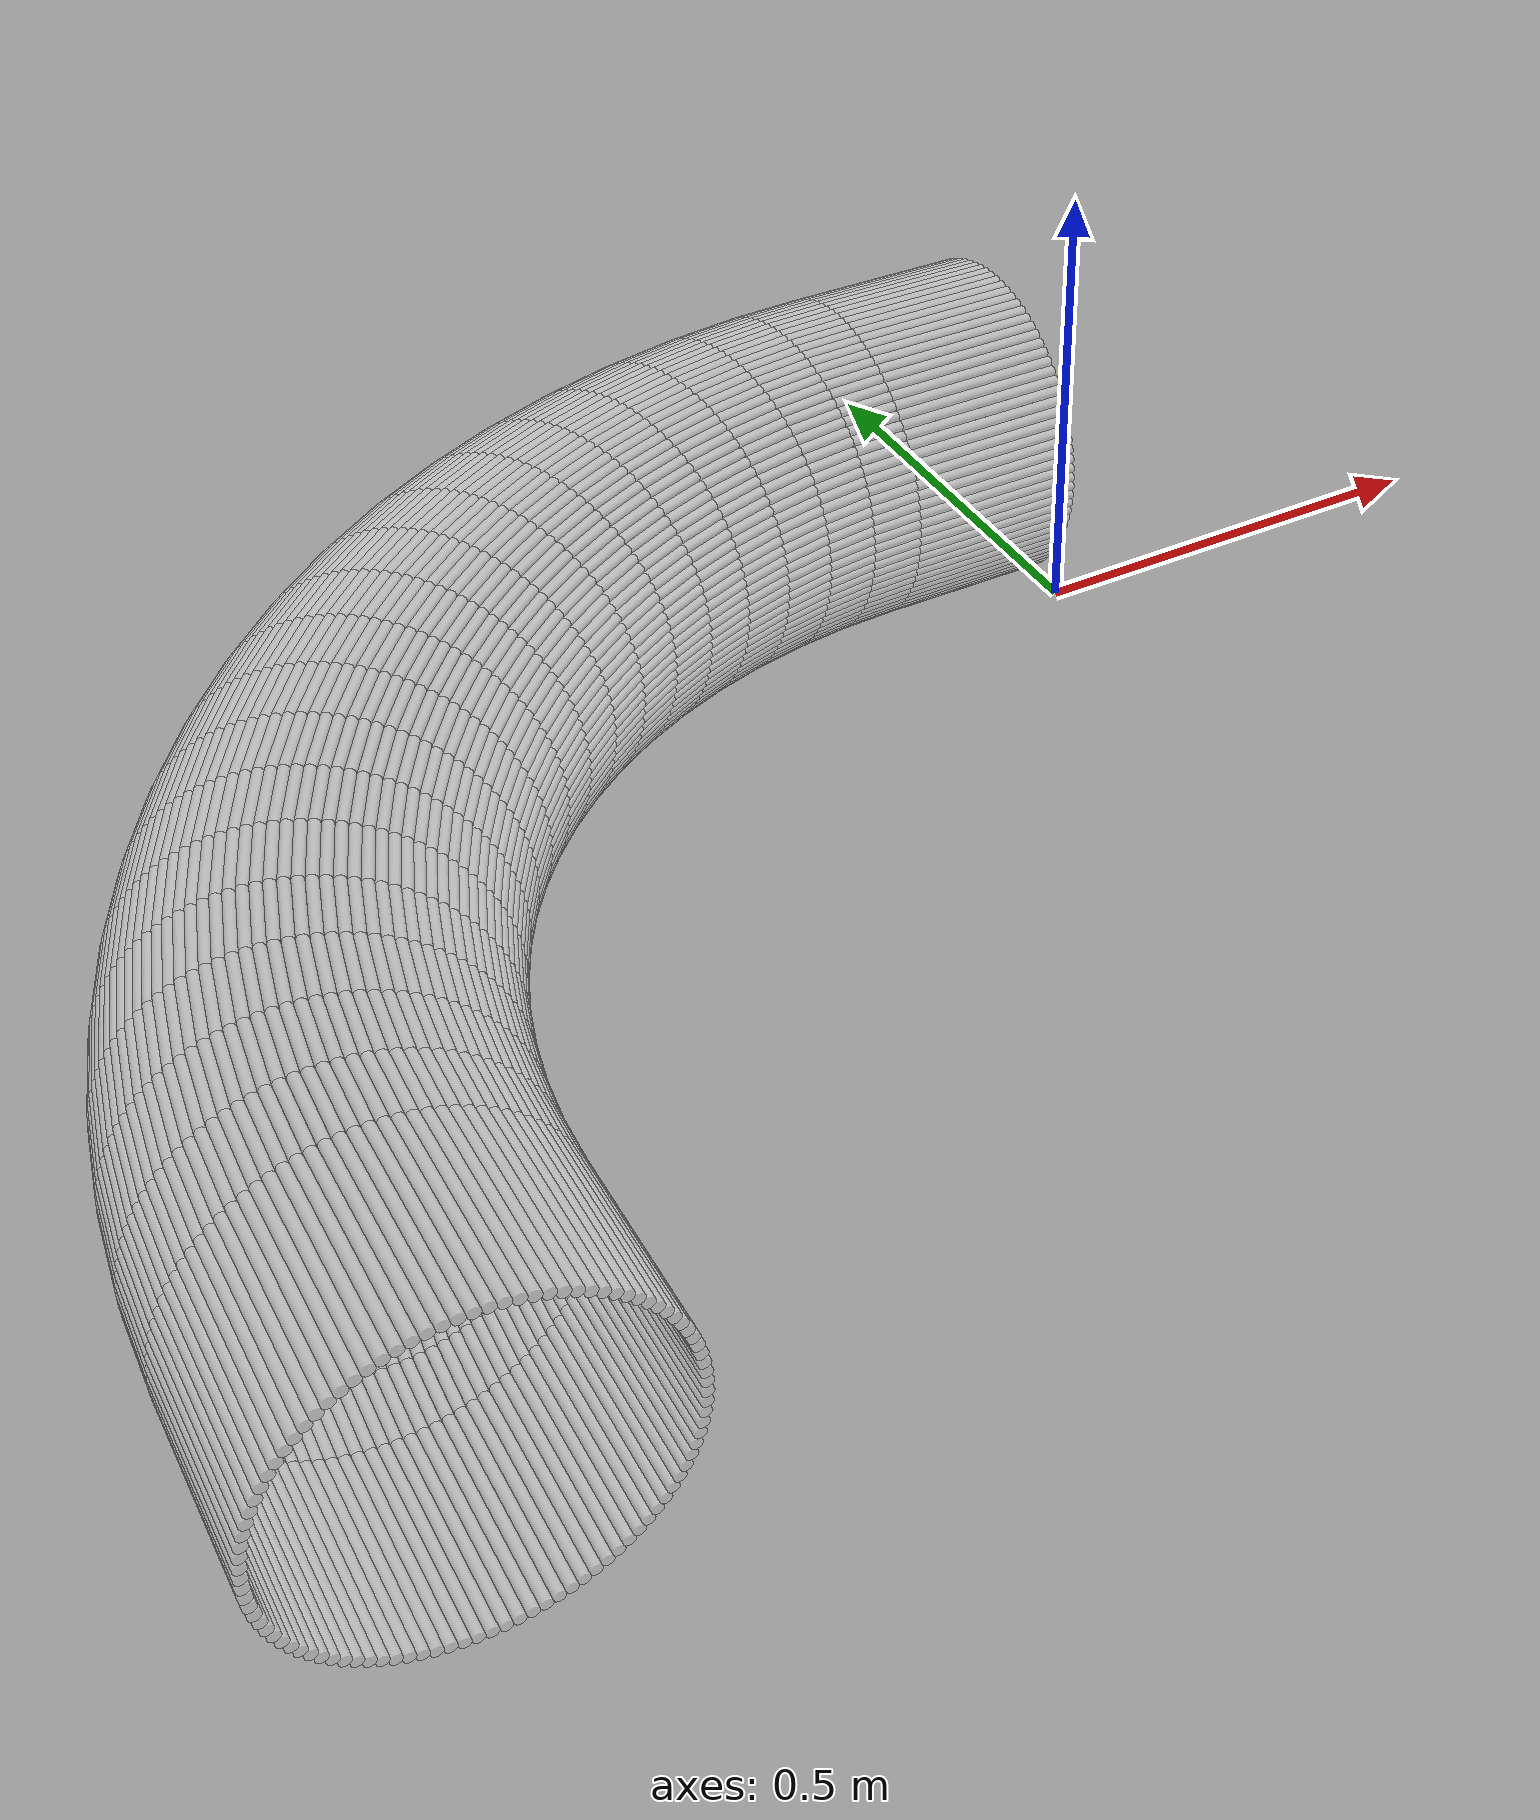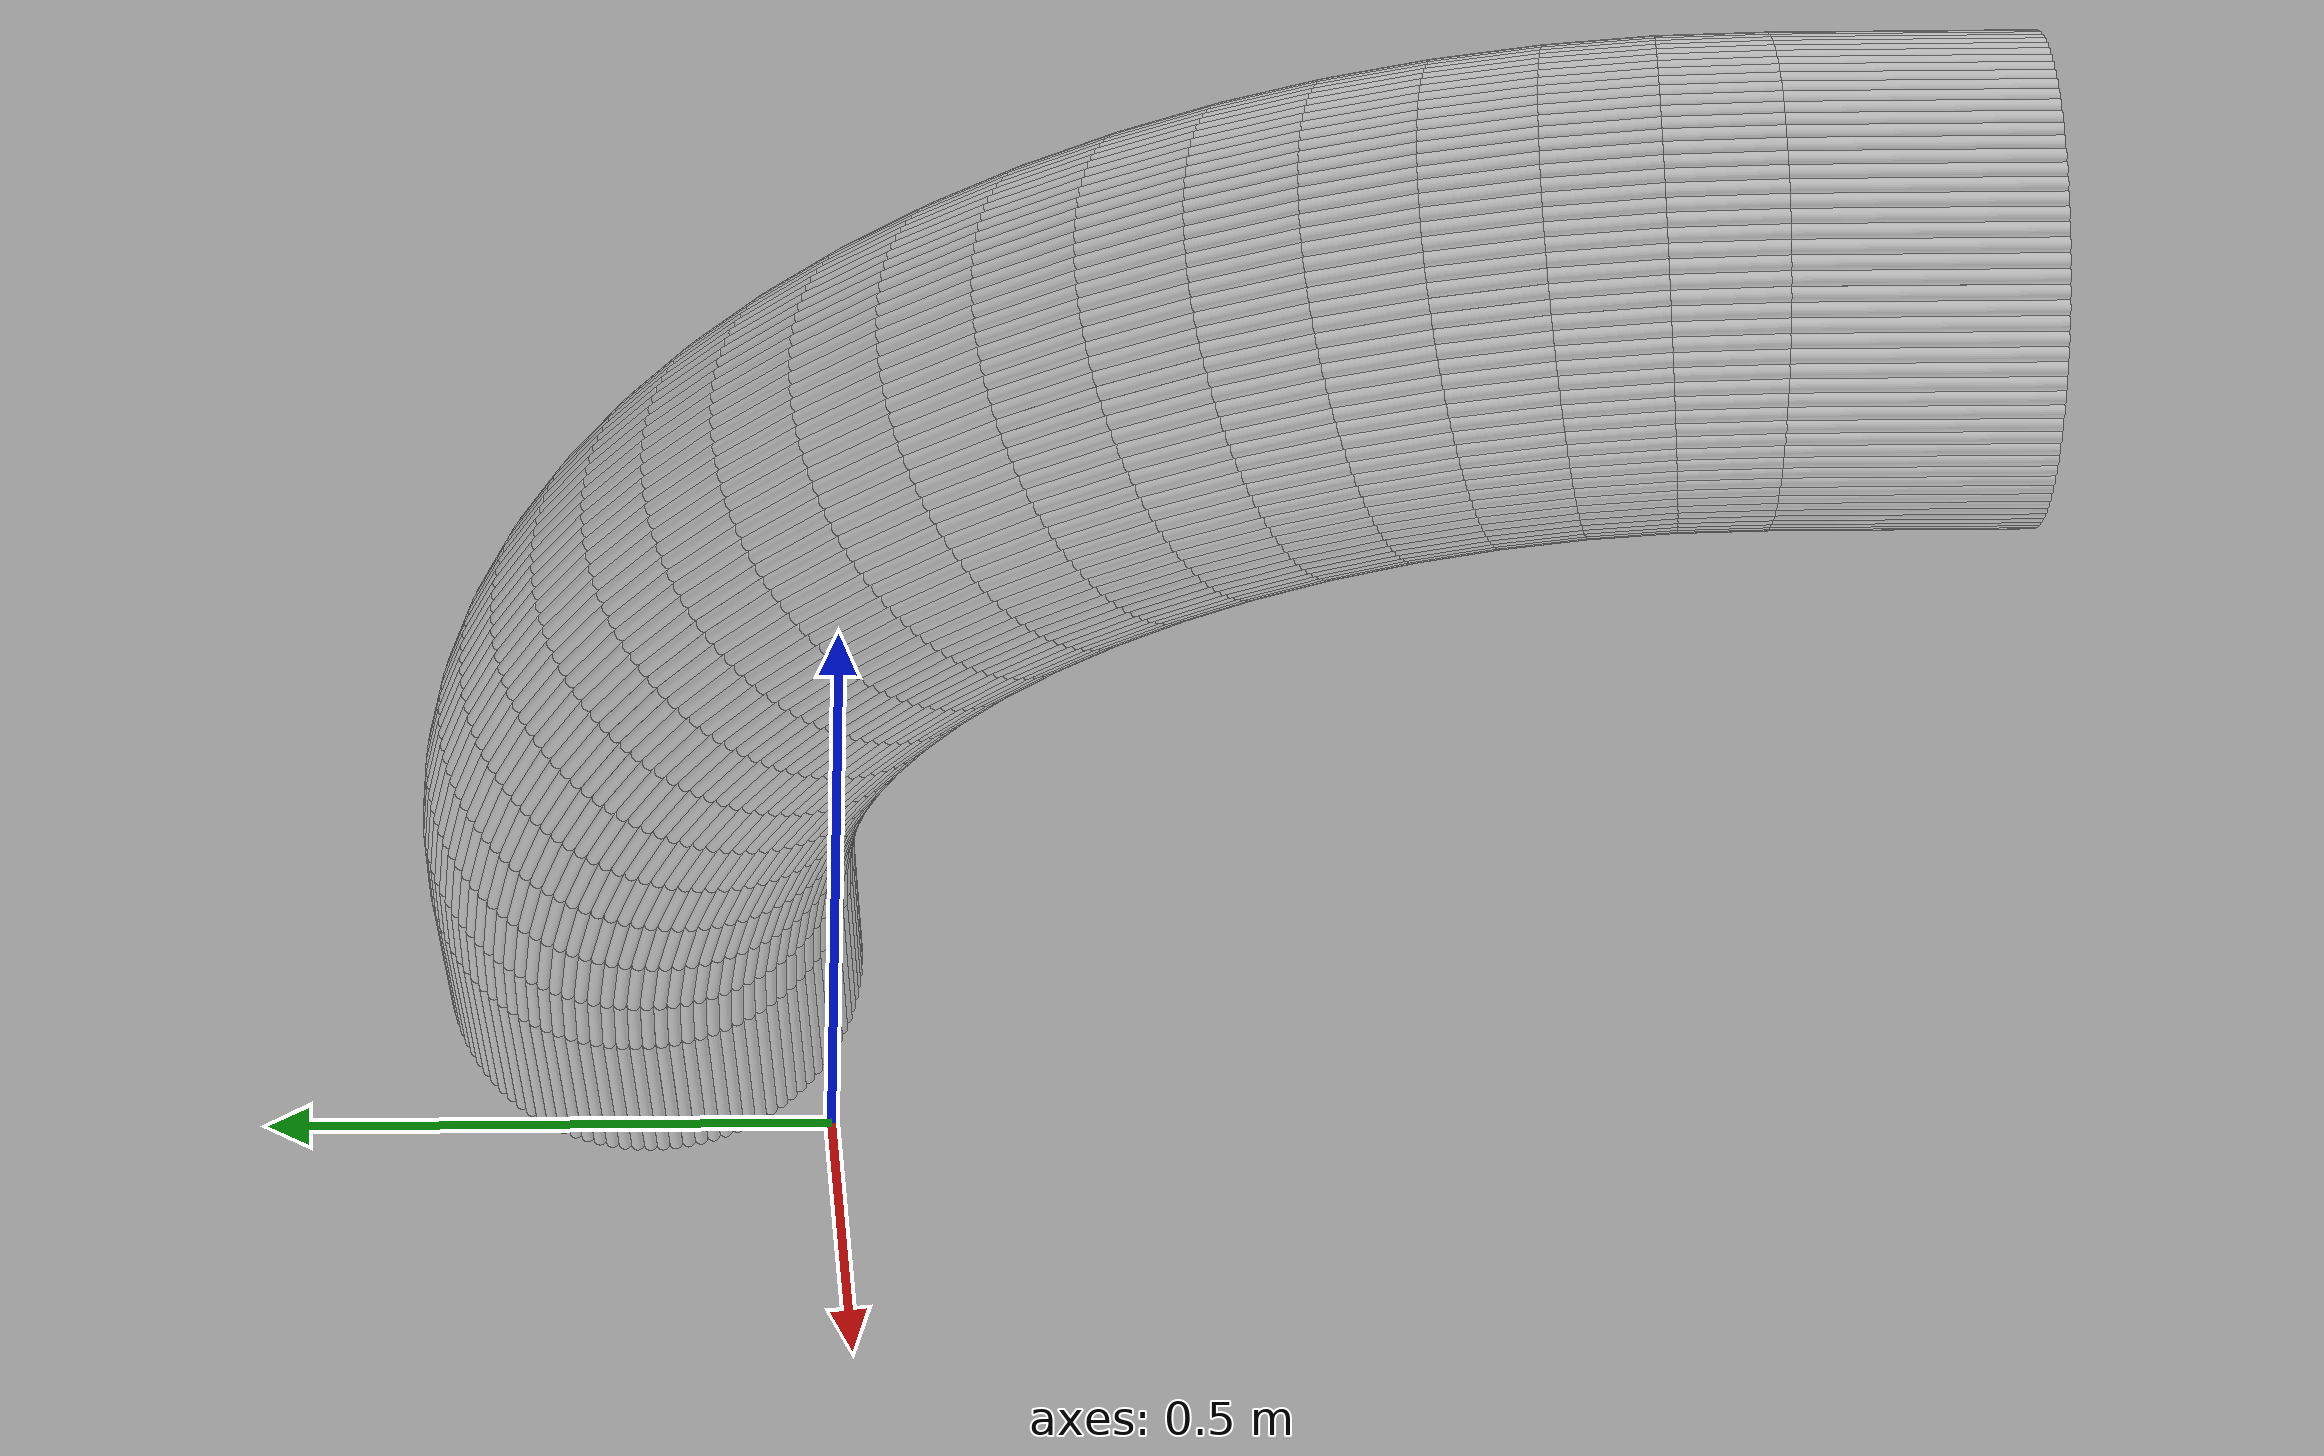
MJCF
<?xml version="1.0" encoding="utf-8"?>
<mujoco>
   <worldbody>
   <body pos="-0.2 -0.74 -0.02" euler="0 0 90">
      <geom euler=" 0 10 0 " fromto="1.08 -0.2 0.18 1.08 0 0.18" rgba="1 1 1 0.35"
            size="0.0056539"
            type="cylinder"/>
      <geom euler=" 0 20 0 " fromto="1.0796 -0.2 0.1913 1.0796 0 0.1913" rgba="1 1 1 0.35"
            size="0.0056539"
            type="cylinder"/>
      <geom euler=" 0 30 0 " fromto="1.0786 -0.2 0.20256 1.0786 0 0.20256"
            rgba="1 1 1 0.35"
            size="0.0056539"
            type="cylinder"/>
      <geom euler=" 0 40 0 " fromto="1.0768 -0.2 0.21373 1.0768 0 0.21373"
            rgba="1 1 1 0.35"
            size="0.0056539"
            type="cylinder"/>
      <geom euler=" 0 50 0 " fromto="1.0743 -0.2 0.22476 1.0743 0 0.22476"
            rgba="1 1 1 0.35"
            size="0.0056539"
            type="cylinder"/>
      <geom euler=" 0 60 0 " fromto="1.0712 -0.2 0.23562 1.0712 0 0.23562"
            rgba="1 1 1 0.35"
            size="0.0056539"
            type="cylinder"/>
      <geom euler=" 0 70 0 " fromto="1.0674 -0.2 0.24626 1.0674 0 0.24626"
            rgba="1 1 1 0.35"
            size="0.0056539"
            type="cylinder"/>
      <geom euler=" 0 80 0 " fromto="1.0629 -0.2 0.25664 1.0629 0 0.25664"
            rgba="1 1 1 0.35"
            size="0.0056539"
            type="cylinder"/>
      <geom euler=" 0 90 0 " fromto="1.0577 -0.2 0.26672 1.0577 0 0.26672"
            rgba="1 1 1 0.35"
            size="0.0056539"
            type="cylinder"/>
      <geom euler=" 0 100 0 " fromto="1.052 -0.2 0.27645 1.052 0 0.27645" rgba="1 1 1 0.35"
            size="0.0056539"
            type="cylinder"/>
      <geom euler=" 0 110 0 " fromto="1.0456 -0.2 0.2858 1.0456 0 0.2858" rgba="1 1 1 0.35"
            size="0.0056539"
            type="cylinder"/>
      <geom euler=" 0 120 0 " fromto="1.0387 -0.2 0.29474 1.0387 0 0.29474"
            rgba="1 1 1 0.35"
            size="0.0056539"
            type="cylinder"/>
      <geom euler=" 0 130 0 " fromto="1.0312 -0.2 0.30322 1.0312 0 0.30322"
            rgba="1 1 1 0.35"
            size="0.0056539"
            type="cylinder"/>
      <geom euler=" 0 140 0 " fromto="1.0232 -0.2 0.31121 1.0232 0 0.31121"
            rgba="1 1 1 0.35"
            size="0.0056539"
            type="cylinder"/>
      <geom euler=" 0 150 0 " fromto="1.0147 -0.2 0.31869 1.0147 0 0.31869"
            rgba="1 1 1 0.35"
            size="0.0056539"
            type="cylinder"/>
      <geom euler=" 0 160 0 " fromto="1.0058 -0.2 0.32562 1.0058 0 0.32562"
            rgba="1 1 1 0.35"
            size="0.0056539"
            type="cylinder"/>
      <geom euler=" 0 170 0 " fromto="0.99645 -0.2 0.33198 0.99645 0 0.33198"
            rgba="1 1 1 0.35"
            size="0.0056539"
            type="cylinder"/>
      <geom euler=" 0 180 0 " fromto="0.98672 -0.2 0.33774 0.98672 0 0.33774"
            rgba="1 1 1 0.35"
            size="0.0056539"
            type="cylinder"/>
      <geom euler=" 0 190 0 " fromto="0.97664 -0.2 0.34287 0.97664 0 0.34287"
            rgba="1 1 1 0.35"
            size="0.0056539"
            type="cylinder"/>
      <geom euler=" 0 200 0 " fromto="0.96626 -0.2 0.34736 0.96626 0 0.34736"
            rgba="1 1 1 0.35"
            size="0.0056539"
            type="cylinder"/>
      <geom euler=" 0 210 0 " fromto="0.95562 -0.2 0.35119 0.95562 0 0.35119"
            rgba="1 1 1 0.35"
            size="0.0056539"
            type="cylinder"/>
      <geom euler=" 0 220 0 " fromto="0.94476 -0.2 0.35434 0.94476 0 0.35434"
            rgba="1 1 1 0.35"
            size="0.0056539"
            type="cylinder"/>
      <geom euler=" 0 230 0 " fromto="0.93373 -0.2 0.35681 0.93373 0 0.35681"
            rgba="1 1 1 0.35"
            size="0.0056539"
            type="cylinder"/>
      <geom euler=" 0 240 0 " fromto="0.92256 -0.2 0.35858 0.92256 0 0.35858"
            rgba="1 1 1 0.35"
            size="0.0056539"
            type="cylinder"/>
      <geom euler=" 0 250 0 " fromto="0.9113 -0.2 0.35964 0.9113 0 0.35964"
            rgba="1 1 1 0.35"
            size="0.0056539"
            type="cylinder"/>
      <geom euler=" 0 260 0 " fromto="0.9 -0.2 0.36 0.9 0 0.36" rgba="1 1 1 0.35"
            size="0.0056539"
            type="cylinder"/>
      <geom euler=" 0 270 0 " fromto="0.8887 -0.2 0.35964 0.8887 0 0.35964"
            rgba="1 1 1 0.35"
            size="0.0056539"
            type="cylinder"/>
      <geom euler=" 0 280 0 " fromto="0.87744 -0.2 0.35858 0.87744 0 0.35858"
            rgba="1 1 1 0.35"
            size="0.0056539"
            type="cylinder"/>
      <geom euler=" 0 290 0 " fromto="0.86627 -0.2 0.35681 0.86627 0 0.35681"
            rgba="1 1 1 0.35"
            size="0.0056539"
            type="cylinder"/>
      <geom euler=" 0 300 0 " fromto="0.85524 -0.2 0.35434 0.85524 0 0.35434"
            rgba="1 1 1 0.35"
            size="0.0056539"
            type="cylinder"/>
      <geom euler=" 0 310 0 " fromto="0.84438 -0.2 0.35119 0.84438 0 0.35119"
            rgba="1 1 1 0.35"
            size="0.0056539"
            type="cylinder"/>
      <geom euler=" 0 320 0 " fromto="0.83374 -0.2 0.34736 0.83374 0 0.34736"
            rgba="1 1 1 0.35"
            size="0.0056539"
            type="cylinder"/>
      <geom euler=" 0 330 0 " fromto="0.82336 -0.2 0.34287 0.82336 0 0.34287"
            rgba="1 1 1 0.35"
            size="0.0056539"
            type="cylinder"/>
      <geom euler=" 0 340 0 " fromto="0.81328 -0.2 0.33774 0.81328 0 0.33774"
            rgba="1 1 1 0.35"
            size="0.0056539"
            type="cylinder"/>
      <geom euler=" 0 350 0 " fromto="0.80355 -0.2 0.33198 0.80355 0 0.33198"
            rgba="1 1 1 0.35"
            size="0.0056539"
            type="cylinder"/>
      <geom euler=" 0 360 0 " fromto="0.7942 -0.2 0.32562 0.7942 0 0.32562"
            rgba="1 1 1 0.35"
            size="0.0056539"
            type="cylinder"/>
      <geom euler=" 0 370 0 " fromto="0.78526 -0.2 0.31869 0.78526 0 0.31869"
            rgba="1 1 1 0.35"
            size="0.0056539"
            type="cylinder"/>
      <geom euler=" 0 380 0 " fromto="0.77678 -0.2 0.31121 0.77678 0 0.31121"
            rgba="1 1 1 0.35"
            size="0.0056539"
            type="cylinder"/>
      <geom euler=" 0 390 0 " fromto="0.76879 -0.2 0.30322 0.76879 0 0.30322"
            rgba="1 1 1 0.35"
            size="0.0056539"
            type="cylinder"/>
      <geom euler=" 0 400 0 " fromto="0.76131 -0.2 0.29474 0.76131 0 0.29474"
            rgba="1 1 1 0.35"
            size="0.0056539"
            type="cylinder"/>
      <geom euler=" 0 410 0 " fromto="0.75438 -0.2 0.2858 0.75438 0 0.2858"
            rgba="1 1 1 0.35"
            size="0.0056539"
            type="cylinder"/>
      <geom euler=" 0 420 0 " fromto="0.74802 -0.2 0.27645 0.74802 0 0.27645"
            rgba="1 1 1 0.35"
            size="0.0056539"
            type="cylinder"/>
      <geom euler=" 0 430 0 " fromto="0.74226 -0.2 0.26672 0.74226 0 0.26672"
            rgba="1 1 1 0.35"
            size="0.0056539"
            type="cylinder"/>
      <geom euler=" 0 440 0 " fromto="0.73713 -0.2 0.25664 0.73713 0 0.25664"
            rgba="1 1 1 0.35"
            size="0.0056539"
            type="cylinder"/>
      <geom euler=" 0 450 0 " fromto="0.73264 -0.2 0.24626 0.73264 0 0.24626"
            rgba="1 1 1 0.35"
            size="0.0056539"
            type="cylinder"/>
      <geom euler=" 0 460 0 " fromto="0.72881 -0.2 0.23562 0.72881 0 0.23562"
            rgba="1 1 1 0.35"
            size="0.0056539"
            type="cylinder"/>
      <geom euler=" 0 470 0 " fromto="0.72566 -0.2 0.22476 0.72566 0 0.22476"
            rgba="1 1 1 0.35"
            size="0.0056539"
            type="cylinder"/>
      <geom euler=" 0 480 0 " fromto="0.72319 -0.2 0.21373 0.72319 0 0.21373"
            rgba="1 1 1 0.35"
            size="0.0056539"
            type="cylinder"/>
      <geom euler=" 0 490 0 " fromto="0.72142 -0.2 0.20256 0.72142 0 0.20256"
            rgba="1 1 1 0.35"
            size="0.0056539"
            type="cylinder"/>
      <geom euler=" 0 500 0 " fromto="0.72036 -0.2 0.1913 0.72036 0 0.1913"
            rgba="1 1 1 0.35"
            size="0.0056539"
            type="cylinder"/>
      <geom euler=" 0 510 0 " fromto="0.72 -0.2 0.18 0.72 0 0.18" rgba="1 1 1 0.35"
            size="0.0056539"
            type="cylinder"/>
      <geom euler=" 0 520 0 " fromto="0.72036 -0.2 0.1687 0.72036 0 0.1687"
            rgba="1 1 1 0.35"
            size="0.0056539"
            type="cylinder"/>
      <geom euler=" 0 530 0 " fromto="0.72142 -0.2 0.15744 0.72142 0 0.15744"
            rgba="1 1 1 0.35"
            size="0.0056539"
            type="cylinder"/>
      <geom euler=" 0 540 0 " fromto="0.72319 -0.2 0.14627 0.72319 0 0.14627"
            rgba="1 1 1 0.35"
            size="0.0056539"
            type="cylinder"/>
      <geom euler=" 0 550 0 " fromto="0.72566 -0.2 0.13524 0.72566 0 0.13524"
            rgba="1 1 1 0.35"
            size="0.0056539"
            type="cylinder"/>
      <geom euler=" 0 560 0 " fromto="0.72881 -0.2 0.12438 0.72881 0 0.12438"
            rgba="1 1 1 0.35"
            size="0.0056539"
            type="cylinder"/>
      <geom euler=" 0 570 0 " fromto="0.73264 -0.2 0.11374 0.73264 0 0.11374"
            rgba="1 1 1 0.35"
            size="0.0056539"
            type="cylinder"/>
      <geom euler=" 0 580 0 " fromto="0.73713 -0.2 0.10336 0.73713 0 0.10336"
            rgba="1 1 1 0.35"
            size="0.0056539"
            type="cylinder"/>
      <geom euler=" 0 590 0 " fromto="0.74226 -0.2 0.093284 0.74226 0 0.093284"
            rgba="1 1 1 0.35"
            size="0.0056539"
            type="cylinder"/>
      <geom euler=" 0 600 0 " fromto="0.74802 -0.2 0.083551 0.74802 0 0.083551"
            rgba="1 1 1 0.35"
            size="0.0056539"
            type="cylinder"/>
      <geom euler=" 0 610 0 " fromto="0.75438 -0.2 0.074199 0.75438 0 0.074199"
            rgba="1 1 1 0.35"
            size="0.0056539"
            type="cylinder"/>
      <geom euler=" 0 620 0 " fromto="0.76131 -0.2 0.065264 0.76131 0 0.065264"
            rgba="1 1 1 0.35"
            size="0.0056539"
            type="cylinder"/>
      <geom euler=" 0 630 0 " fromto="0.76879 -0.2 0.056782 0.76879 0 0.056782"
            rgba="1 1 1 0.35"
            size="0.0056539"
            type="cylinder"/>
      <geom euler=" 0 640 0 " fromto="0.77678 -0.2 0.048786 0.77678 0 0.048786"
            rgba="1 1 1 0.35"
            size="0.0056539"
            type="cylinder"/>
      <geom euler=" 0 650 0 " fromto="0.78526 -0.2 0.041308 0.78526 0 0.041308"
            rgba="1 1 1 0.35"
            size="0.0056539"
            type="cylinder"/>
      <geom euler=" 0 660 0 " fromto="0.7942 -0.2 0.034377 0.7942 0 0.034377"
            rgba="1 1 1 0.35"
            size="0.0056539"
            type="cylinder"/>
      <geom euler=" 0 670 0 " fromto="0.80355 -0.2 0.028021 0.80355 0 0.028021"
            rgba="1 1 1 0.35"
            size="0.0056539"
            type="cylinder"/>
      <geom euler=" 0 680 0 " fromto="0.81328 -0.2 0.022265 0.81328 0 0.022265"
            rgba="1 1 1 0.35"
            size="0.0056539"
            type="cylinder"/>
      <geom euler=" 0 690 0 " fromto="0.82336 -0.2 0.017131 0.82336 0 0.017131"
            rgba="1 1 1 0.35"
            size="0.0056539"
            type="cylinder"/>
      <geom euler=" 0 700 0 " fromto="0.83374 -0.2 0.01264 0.83374 0 0.01264"
            rgba="1 1 1 0.35"
            size="0.0056539"
            type="cylinder"/>
      <geom euler=" 0 710 0 " fromto="0.84438 -0.2 0.0088098 0.84438 0 0.0088098"
            rgba="1 1 1 0.35"
            size="0.0056539"
            type="cylinder"/>
      <geom euler=" 0 720 0 " fromto="0.85524 -0.2 0.005655 0.85524 0 0.005655"
            rgba="1 1 1 0.35"
            size="0.0056539"
            type="cylinder"/>
      <geom euler=" 0 730 0 " fromto="0.86627 -0.2 0.0031883 0.86627 0 0.0031883"
            rgba="1 1 1 0.35"
            size="0.0056539"
            type="cylinder"/>
      <geom euler=" 0 740 0 " fromto="0.87744 -0.2 0.0014194 0.87744 0 0.0014194"
            rgba="1 1 1 0.35"
            size="0.0056539"
            type="cylinder"/>
      <geom euler=" 0 750 0 " fromto="0.8887 -0.2 0.00035519 0.8887 0 0.00035519"
            rgba="1 1 1 0.35"
            size="0.0056539"
            type="cylinder"/>
      <geom euler=" 0 760 0 " fromto="0.9 -0.2 0 0.9 0 0" rgba="1 1 1 0.35"
            size="0.0056539"
            type="cylinder"/>
      <geom euler=" 0 770 0 " fromto="0.9113 -0.2 0.00035519 0.9113 0 0.00035519"
            rgba="1 1 1 0.35"
            size="0.0056539"
            type="cylinder"/>
      <geom euler=" 0 780 0 " fromto="0.92256 -0.2 0.0014194 0.92256 0 0.0014194"
            rgba="1 1 1 0.35"
            size="0.0056539"
            type="cylinder"/>
      <geom euler=" 0 790 0 " fromto="0.93373 -0.2 0.0031883 0.93373 0 0.0031883"
            rgba="1 1 1 0.35"
            size="0.0056539"
            type="cylinder"/>
      <geom euler=" 0 800 0 " fromto="0.94476 -0.2 0.005655 0.94476 0 0.005655"
            rgba="1 1 1 0.35"
            size="0.0056539"
            type="cylinder"/>
      <geom euler=" 0 810 0 " fromto="0.95562 -0.2 0.0088098 0.95562 0 0.0088098"
            rgba="1 1 1 0.35"
            size="0.0056539"
            type="cylinder"/>
      <geom euler=" 0 820 0 " fromto="0.96626 -0.2 0.01264 0.96626 0 0.01264"
            rgba="1 1 1 0.35"
            size="0.0056539"
            type="cylinder"/>
      <geom euler=" 0 830 0 " fromto="0.97664 -0.2 0.017131 0.97664 0 0.017131"
            rgba="1 1 1 0.35"
            size="0.0056539"
            type="cylinder"/>
      <geom euler=" 0 840 0 " fromto="0.98672 -0.2 0.022265 0.98672 0 0.022265"
            rgba="1 1 1 0.35"
            size="0.0056539"
            type="cylinder"/>
      <geom euler=" 0 850 0 " fromto="0.99645 -0.2 0.028021 0.99645 0 0.028021"
            rgba="1 1 1 0.35"
            size="0.0056539"
            type="cylinder"/>
      <geom euler=" 0 860 0 " fromto="1.0058 -0.2 0.034377 1.0058 0 0.034377"
            rgba="1 1 1 0.35"
            size="0.0056539"
            type="cylinder"/>
      <geom euler=" 0 870 0 " fromto="1.0147 -0.2 0.041308 1.0147 0 0.041308"
            rgba="1 1 1 0.35"
            size="0.0056539"
            type="cylinder"/>
      <geom euler=" 0 880 0 " fromto="1.0232 -0.2 0.048786 1.0232 0 0.048786"
            rgba="1 1 1 0.35"
            size="0.0056539"
            type="cylinder"/>
      <geom euler=" 0 890 0 " fromto="1.0312 -0.2 0.056782 1.0312 0 0.056782"
            rgba="1 1 1 0.35"
            size="0.0056539"
            type="cylinder"/>
      <geom euler=" 0 900 0 " fromto="1.0387 -0.2 0.065264 1.0387 0 0.065264"
            rgba="1 1 1 0.35"
            size="0.0056539"
            type="cylinder"/>
      <geom euler=" 0 910 0 " fromto="1.0456 -0.2 0.074199 1.0456 0 0.074199"
            rgba="1 1 1 0.35"
            size="0.0056539"
            type="cylinder"/>
      <geom euler=" 0 920 0 " fromto="1.052 -0.2 0.083551 1.052 0 0.083551"
            rgba="1 1 1 0.35"
            size="0.0056539"
            type="cylinder"/>
      <geom euler=" 0 930 0 " fromto="1.0577 -0.2 0.093284 1.0577 0 0.093284"
            rgba="1 1 1 0.35"
            size="0.0056539"
            type="cylinder"/>
      <geom euler=" 0 940 0 " fromto="1.0629 -0.2 0.10336 1.0629 0 0.10336"
            rgba="1 1 1 0.35"
            size="0.0056539"
            type="cylinder"/>
      <geom euler=" 0 950 0 " fromto="1.0674 -0.2 0.11374 1.0674 0 0.11374"
            rgba="1 1 1 0.35"
            size="0.0056539"
            type="cylinder"/>
      <geom euler=" 0 960 0 " fromto="1.0712 -0.2 0.12438 1.0712 0 0.12438"
            rgba="1 1 1 0.35"
            size="0.0056539"
            type="cylinder"/>
      <geom euler=" 0 970 0 " fromto="1.0743 -0.2 0.13524 1.0743 0 0.13524"
            rgba="1 1 1 0.35"
            size="0.0056539"
            type="cylinder"/>
      <geom euler=" 0 980 0 " fromto="1.0768 -0.2 0.14627 1.0768 0 0.14627"
            rgba="1 1 1 0.35"
            size="0.0056539"
            type="cylinder"/>
      <geom euler=" 0 990 0 " fromto="1.0786 -0.2 0.15744 1.0786 0 0.15744"
            rgba="1 1 1 0.35"
            size="0.0056539"
            type="cylinder"/>
      <geom euler=" 0 1000 0 " fromto="1.0796 -0.2 0.1687 1.0796 0 0.1687"
            rgba="1 1 1 0.35"
            size="0.0056539"
            type="cylinder"/>
      <geom euler=" 0 10 0 " fromto="1.08 0 0.18 1.0763 0.089186 0.18" rgba="1 1 1 0.35"
            size="0.0056539"
            type="cylinder"/>
      <geom euler=" 0 20 0 " fromto="1.0796 0 0.1913 1.076 0.089156 0.1913"
            rgba="1 1 1 0.35"
            size="0.0056539"
            type="cylinder"/>
      <geom euler=" 0 30 0 " fromto="1.0786 0 0.20256 1.0749 0.089068 0.20256"
            rgba="1 1 1 0.35"
            size="0.0056539"
            type="cylinder"/>
      <geom euler=" 0 40 0 " fromto="1.0768 0 0.21373 1.0731 0.088922 0.21373"
            rgba="1 1 1 0.35"
            size="0.0056539"
            type="cylinder"/>
      <geom euler=" 0 50 0 " fromto="1.0743 0 0.22476 1.0707 0.088719 0.22476"
            rgba="1 1 1 0.35"
            size="0.0056539"
            type="cylinder"/>
      <geom euler=" 0 60 0 " fromto="1.0712 0 0.23562 1.0675 0.088458 0.23562"
            rgba="1 1 1 0.35"
            size="0.0056539"
            type="cylinder"/>
      <geom euler=" 0 70 0 " fromto="1.0674 0 0.24626 1.0637 0.088142 0.24626"
            rgba="1 1 1 0.35"
            size="0.0056539"
            type="cylinder"/>
      <geom euler=" 0 80 0 " fromto="1.0629 0 0.25664 1.0592 0.087771 0.25664"
            rgba="1 1 1 0.35"
            size="0.0056539"
            type="cylinder"/>
      <geom euler=" 0 90 0 " fromto="1.0577 0 0.26672 1.0541 0.087347 0.26672"
            rgba="1 1 1 0.35"
            size="0.0056539"
            type="cylinder"/>
      <geom euler=" 0 100 0 " fromto="1.052 0 0.27645 1.0484 0.086872 0.27645"
            rgba="1 1 1 0.35"
            size="0.0056539"
            type="cylinder"/>
      <geom euler=" 0 110 0 " fromto="1.0456 0 0.2858 1.0421 0.086347 0.2858"
            rgba="1 1 1 0.35"
            size="0.0056539"
            type="cylinder"/>
      <geom euler=" 0 120 0 " fromto="1.0387 0 0.29474 1.0351 0.085775 0.29474"
            rgba="1 1 1 0.35"
            size="0.0056539"
            type="cylinder"/>
      <geom euler=" 0 130 0 " fromto="1.0312 0 0.30322 1.0277 0.085157 0.30322"
            rgba="1 1 1 0.35"
            size="0.0056539"
            type="cylinder"/>
      <geom euler=" 0 140 0 " fromto="1.0232 0 0.31121 1.0197 0.084497 0.31121"
            rgba="1 1 1 0.35"
            size="0.0056539"
            type="cylinder"/>
      <geom euler=" 0 150 0 " fromto="1.0147 0 0.31869 1.0113 0.083796 0.31869"
            rgba="1 1 1 0.35"
            size="0.0056539"
            type="cylinder"/>
      <geom euler=" 0 160 0 " fromto="1.0058 0 0.32562 1.0024 0.083058 0.32562"
            rgba="1 1 1 0.35"
            size="0.0056539"
            type="cylinder"/>
      <geom euler=" 0 170 0 " fromto="0.99645 0 0.33198 0.99305 0.082286 0.33198"
            rgba="1 1 1 0.35"
            size="0.0056539"
            type="cylinder"/>
      <geom euler=" 0 180 0 " fromto="0.98672 0 0.33774 0.98335 0.081482 0.33774"
            rgba="1 1 1 0.35"
            size="0.0056539"
            type="cylinder"/>
      <geom euler=" 0 190 0 " fromto="0.97664 0 0.34287 0.9733 0.08065 0.34287"
            rgba="1 1 1 0.35"
            size="0.0056539"
            type="cylinder"/>
      <geom euler=" 0 200 0 " fromto="0.96626 0 0.34736 0.96296 0.079793 0.34736"
            rgba="1 1 1 0.35"
            size="0.0056539"
            type="cylinder"/>
      <geom euler=" 0 210 0 " fromto="0.95562 0 0.35119 0.95236 0.078915 0.35119"
            rgba="1 1 1 0.35"
            size="0.0056539"
            type="cylinder"/>
      <geom euler=" 0 220 0 " fromto="0.94476 0 0.35434 0.94154 0.078018 0.35434"
            rgba="1 1 1 0.35"
            size="0.0056539"
            type="cylinder"/>
      <geom euler=" 0 230 0 " fromto="0.93373 0 0.35681 0.93054 0.077107 0.35681"
            rgba="1 1 1 0.35"
            size="0.0056539"
            type="cylinder"/>
      <geom euler=" 0 240 0 " fromto="0.92256 0 0.35858 0.91941 0.076184 0.35858"
            rgba="1 1 1 0.35"
            size="0.0056539"
            type="cylinder"/>
      <geom euler=" 0 250 0 " fromto="0.9113 0 0.35964 0.90819 0.075255 0.35964"
            rgba="1 1 1 0.35"
            size="0.0056539"
            type="cylinder"/>
      <geom euler=" 0 260 0 " fromto="0.9 0 0.36 0.89693 0.074321 0.36" rgba="1 1 1 0.35"
            size="0.0056539"
            type="cylinder"/>
      <geom euler=" 0 270 0 " fromto="0.8887 0 0.35964 0.88566 0.073388 0.35964"
            rgba="1 1 1 0.35"
            size="0.0056539"
            type="cylinder"/>
      <geom euler=" 0 280 0 " fromto="0.87744 0 0.35858 0.87444 0.072458 0.35858"
            rgba="1 1 1 0.35"
            size="0.0056539"
            type="cylinder"/>
      <geom euler=" 0 290 0 " fromto="0.86627 0 0.35681 0.86331 0.071536 0.35681"
            rgba="1 1 1 0.35"
            size="0.0056539"
            type="cylinder"/>
      <geom euler=" 0 300 0 " fromto="0.85524 0 0.35434 0.85231 0.070625 0.35434"
            rgba="1 1 1 0.35"
            size="0.0056539"
            type="cylinder"/>
      <geom euler=" 0 310 0 " fromto="0.84438 0 0.35119 0.84149 0.069728 0.35119"
            rgba="1 1 1 0.35"
            size="0.0056539"
            type="cylinder"/>
      <geom euler=" 0 320 0 " fromto="0.83374 0 0.34736 0.83089 0.06885 0.34736"
            rgba="1 1 1 0.35"
            size="0.0056539"
            type="cylinder"/>
      <geom euler=" 0 330 0 " fromto="0.82336 0 0.34287 0.82055 0.067993 0.34287"
            rgba="1 1 1 0.35"
            size="0.0056539"
            type="cylinder"/>
      <geom euler=" 0 340 0 " fromto="0.81328 0 0.33774 0.81051 0.06716 0.33774"
            rgba="1 1 1 0.35"
            size="0.0056539"
            type="cylinder"/>
      <geom euler=" 0 350 0 " fromto="0.80355 0 0.33198 0.80081 0.066357 0.33198"
            rgba="1 1 1 0.35"
            size="0.0056539"
            type="cylinder"/>
      <geom euler=" 0 360 0 " fromto="0.7942 0 0.32562 0.79149 0.065584 0.32562"
            rgba="1 1 1 0.35"
            size="0.0056539"
            type="cylinder"/>
      <geom euler=" 0 370 0 " fromto="0.78526 0 0.31869 0.78258 0.064847 0.31869"
            rgba="1 1 1 0.35"
            size="0.0056539"
            type="cylinder"/>
      <geom euler=" 0 380 0 " fromto="0.77678 0 0.31121 0.77413 0.064146 0.31121"
            rgba="1 1 1 0.35"
            size="0.0056539"
            type="cylinder"/>
      <geom euler=" 0 390 0 " fromto="0.76879 0 0.30322 0.76616 0.063486 0.30322"
            rgba="1 1 1 0.35"
            size="0.0056539"
            type="cylinder"/>
      <geom euler=" 0 400 0 " fromto="0.76131 0 0.29474 0.75871 0.062868 0.29474"
            rgba="1 1 1 0.35"
            size="0.0056539"
            type="cylinder"/>
      <geom euler=" 0 410 0 " fromto="0.75438 0 0.2858 0.7518 0.062296 0.2858"
            rgba="1 1 1 0.35"
            size="0.0056539"
            type="cylinder"/>
      <geom euler=" 0 420 0 " fromto="0.74802 0 0.27645 0.74547 0.061771 0.27645"
            rgba="1 1 1 0.35"
            size="0.0056539"
            type="cylinder"/>
      <geom euler=" 0 430 0 " fromto="0.74226 0 0.26672 0.73973 0.061296 0.26672"
            rgba="1 1 1 0.35"
            size="0.0056539"
            type="cylinder"/>
      <geom euler=" 0 440 0 " fromto="0.73713 0 0.25664 0.73461 0.060872 0.25664"
            rgba="1 1 1 0.35"
            size="0.0056539"
            type="cylinder"/>
      <geom euler=" 0 450 0 " fromto="0.73264 0 0.24626 0.73014 0.060501 0.24626"
            rgba="1 1 1 0.35"
            size="0.0056539"
            type="cylinder"/>
      <geom euler=" 0 460 0 " fromto="0.72881 0 0.23562 0.72632 0.060185 0.23562"
            rgba="1 1 1 0.35"
            size="0.0056539"
            type="cylinder"/>
      <geom euler=" 0 470 0 " fromto="0.72566 0 0.22476 0.72318 0.059924 0.22476"
            rgba="1 1 1 0.35"
            size="0.0056539"
            type="cylinder"/>
      <geom euler=" 0 480 0 " fromto="0.72319 0 0.21373 0.72072 0.05972 0.21373"
            rgba="1 1 1 0.35"
            size="0.0056539"
            type="cylinder"/>
      <geom euler=" 0 490 0 " fromto="0.72142 0 0.20256 0.71896 0.059574 0.20256"
            rgba="1 1 1 0.35"
            size="0.0056539"
            type="cylinder"/>
      <geom euler=" 0 500 0 " fromto="0.72036 0 0.1913 0.71789 0.059486 0.1913"
            rgba="1 1 1 0.35"
            size="0.0056539"
            type="cylinder"/>
      <geom euler=" 0 510 0 " fromto="0.72 0 0.18 0.71754 0.059457 0.18" rgba="1 1 1 0.35"
            size="0.0056539"
            type="cylinder"/>
      <geom euler=" 0 520 0 " fromto="0.72036 0 0.1687 0.71789 0.059486 0.1687"
            rgba="1 1 1 0.35"
            size="0.0056539"
            type="cylinder"/>
      <geom euler=" 0 530 0 " fromto="0.72142 0 0.15744 0.71896 0.059574 0.15744"
            rgba="1 1 1 0.35"
            size="0.0056539"
            type="cylinder"/>
      <geom euler=" 0 540 0 " fromto="0.72319 0 0.14627 0.72072 0.05972 0.14627"
            rgba="1 1 1 0.35"
            size="0.0056539"
            type="cylinder"/>
      <geom euler=" 0 550 0 " fromto="0.72566 0 0.13524 0.72318 0.059924 0.13524"
            rgba="1 1 1 0.35"
            size="0.0056539"
            type="cylinder"/>
      <geom euler=" 0 560 0 " fromto="0.72881 0 0.12438 0.72632 0.060185 0.12438"
            rgba="1 1 1 0.35"
            size="0.0056539"
            type="cylinder"/>
      <geom euler=" 0 570 0 " fromto="0.73264 0 0.11374 0.73014 0.060501 0.11374"
            rgba="1 1 1 0.35"
            size="0.0056539"
            type="cylinder"/>
      <geom euler=" 0 580 0 " fromto="0.73713 0 0.10336 0.73461 0.060872 0.10336"
            rgba="1 1 1 0.35"
            size="0.0056539"
            type="cylinder"/>
      <geom euler=" 0 590 0 " fromto="0.74226 0 0.093284 0.73973 0.061296 0.093284"
            rgba="1 1 1 0.35"
            size="0.0056539"
            type="cylinder"/>
      <geom euler=" 0 600 0 " fromto="0.74802 0 0.083551 0.74547 0.061771 0.083551"
            rgba="1 1 1 0.35"
            size="0.0056539"
            type="cylinder"/>
      <geom euler=" 0 610 0 " fromto="0.75438 0 0.074199 0.7518 0.062296 0.074199"
            rgba="1 1 1 0.35"
            size="0.0056539"
            type="cylinder"/>
      <geom euler=" 0 620 0 " fromto="0.76131 0 0.065264 0.75871 0.062868 0.065264"
            rgba="1 1 1 0.35"
            size="0.0056539"
            type="cylinder"/>
      <geom euler=" 0 630 0 " fromto="0.76879 0 0.056782 0.76616 0.063486 0.056782"
            rgba="1 1 1 0.35"
            size="0.0056539"
            type="cylinder"/>
      <geom euler=" 0 640 0 " fromto="0.77678 0 0.048786 0.77413 0.064146 0.048786"
            rgba="1 1 1 0.35"
            size="0.0056539"
            type="cylinder"/>
      <geom euler=" 0 650 0 " fromto="0.78526 0 0.041308 0.78258 0.064847 0.041308"
            rgba="1 1 1 0.35"
            size="0.0056539"
            type="cylinder"/>
      <geom euler=" 0 660 0 " fromto="0.7942 0 0.034377 0.79149 0.065584 0.034377"
            rgba="1 1 1 0.35"
            size="0.0056539"
            type="cylinder"/>
      <geom euler=" 0 670 0 " fromto="0.80355 0 0.028021 0.80081 0.066357 0.028021"
            rgba="1 1 1 0.35"
            size="0.0056539"
            type="cylinder"/>
      <geom euler=" 0 680 0 " fromto="0.81328 0 0.022265 0.81051 0.06716 0.022265"
            rgba="1 1 1 0.35"
            size="0.0056539"
            type="cylinder"/>
      <geom euler=" 0 690 0 " fromto="0.82336 0 0.017131 0.82055 0.067993 0.017131"
            rgba="1 1 1 0.35"
            size="0.0056539"
            type="cylinder"/>
      <geom euler=" 0 700 0 " fromto="0.83374 0 0.01264 0.83089 0.06885 0.01264"
            rgba="1 1 1 0.35"
            size="0.0056539"
            type="cylinder"/>
      <geom euler=" 0 710 0 " fromto="0.84438 0 0.0088098 0.84149 0.069728 0.0088098"
            rgba="1 1 1 0.35"
            size="0.0056539"
            type="cylinder"/>
      <geom euler=" 0 720 0 " fromto="0.85524 0 0.005655 0.85231 0.070625 0.005655"
            rgba="1 1 1 0.35"
            size="0.0056539"
            type="cylinder"/>
      <geom euler=" 0 730 0 " fromto="0.86627 0 0.0031883 0.86331 0.071536 0.0031883"
            rgba="1 1 1 0.35"
            size="0.0056539"
            type="cylinder"/>
      <geom euler=" 0 740 0 " fromto="0.87744 0 0.0014194 0.87444 0.072458 0.0014194"
            rgba="1 1 1 0.35"
            size="0.0056539"
            type="cylinder"/>
      <geom euler=" 0 750 0 " fromto="0.8887 0 0.00035519 0.88566 0.073388 0.00035519"
            rgba="1 1 1 0.35"
            size="0.0056539"
            type="cylinder"/>
      <geom euler=" 0 760 0 " fromto="0.9 0 0 0.89693 0.074321 0" rgba="1 1 1 0.35"
            size="0.0056539"
            type="cylinder"/>
      <geom euler=" 0 770 0 " fromto="0.9113 0 0.00035519 0.90819 0.075255 0.00035519"
            rgba="1 1 1 0.35"
            size="0.0056539"
            type="cylinder"/>
      <geom euler=" 0 780 0 " fromto="0.92256 0 0.0014194 0.91941 0.076184 0.0014194"
            rgba="1 1 1 0.35"
            size="0.0056539"
            type="cylinder"/>
      <geom euler=" 0 790 0 " fromto="0.93373 0 0.0031883 0.93054 0.077107 0.0031883"
            rgba="1 1 1 0.35"
            size="0.0056539"
            type="cylinder"/>
      <geom euler=" 0 800 0 " fromto="0.94476 0 0.005655 0.94154 0.078018 0.005655"
            rgba="1 1 1 0.35"
            size="0.0056539"
            type="cylinder"/>
      <geom euler=" 0 810 0 " fromto="0.95562 0 0.0088098 0.95236 0.078915 0.0088098"
            rgba="1 1 1 0.35"
            size="0.0056539"
            type="cylinder"/>
      <geom euler=" 0 820 0 " fromto="0.96626 0 0.01264 0.96296 0.079793 0.01264"
            rgba="1 1 1 0.35"
            size="0.0056539"
            type="cylinder"/>
      <geom euler=" 0 830 0 " fromto="0.97664 0 0.017131 0.9733 0.08065 0.017131"
            rgba="1 1 1 0.35"
            size="0.0056539"
            type="cylinder"/>
      <geom euler=" 0 840 0 " fromto="0.98672 0 0.022265 0.98335 0.081482 0.022265"
            rgba="1 1 1 0.35"
            size="0.0056539"
            type="cylinder"/>
      <geom euler=" 0 850 0 " fromto="0.99645 0 0.028021 0.99305 0.082286 0.028021"
            rgba="1 1 1 0.35"
            size="0.0056539"
            type="cylinder"/>
      <geom euler=" 0 860 0 " fromto="1.0058 0 0.034377 1.0024 0.083058 0.034377"
            rgba="1 1 1 0.35"
            size="0.0056539"
            type="cylinder"/>
      <geom euler=" 0 870 0 " fromto="1.0147 0 0.041308 1.0113 0.083796 0.041308"
            rgba="1 1 1 0.35"
            size="0.0056539"
            type="cylinder"/>
      <geom euler=" 0 880 0 " fromto="1.0232 0 0.048786 1.0197 0.084497 0.048786"
            rgba="1 1 1 0.35"
            size="0.0056539"
            type="cylinder"/>
      <geom euler=" 0 890 0 " fromto="1.0312 0 0.056782 1.0277 0.085157 0.056782"
            rgba="1 1 1 0.35"
            size="0.0056539"
            type="cylinder"/>
      <geom euler=" 0 900 0 " fromto="1.0387 0 0.065264 1.0351 0.085775 0.065264"
            rgba="1 1 1 0.35"
            size="0.0056539"
            type="cylinder"/>
      <geom euler=" 0 910 0 " fromto="1.0456 0 0.074199 1.0421 0.086347 0.074199"
            rgba="1 1 1 0.35"
            size="0.0056539"
            type="cylinder"/>
      <geom euler=" 0 920 0 " fromto="1.052 0 0.083551 1.0484 0.086872 0.083551"
            rgba="1 1 1 0.35"
            size="0.0056539"
            type="cylinder"/>
      <geom euler=" 0 930 0 " fromto="1.0577 0 0.093284 1.0541 0.087347 0.093284"
            rgba="1 1 1 0.35"
            size="0.0056539"
            type="cylinder"/>
      <geom euler=" 0 940 0 " fromto="1.0629 0 0.10336 1.0592 0.087771 0.10336"
            rgba="1 1 1 0.35"
            size="0.0056539"
            type="cylinder"/>
      <geom euler=" 0 950 0 " fromto="1.0674 0 0.11374 1.0637 0.088142 0.11374"
            rgba="1 1 1 0.35"
            size="0.0056539"
            type="cylinder"/>
      <geom euler=" 0 960 0 " fromto="1.0712 0 0.12438 1.0675 0.088458 0.12438"
            rgba="1 1 1 0.35"
            size="0.0056539"
            type="cylinder"/>
      <geom euler=" 0 970 0 " fromto="1.0743 0 0.13524 1.0707 0.088719 0.13524"
            rgba="1 1 1 0.35"
            size="0.0056539"
            type="cylinder"/>
      <geom euler=" 0 980 0 " fromto="1.0768 0 0.14627 1.0731 0.088922 0.14627"
            rgba="1 1 1 0.35"
            size="0.0056539"
            type="cylinder"/>
      <geom euler=" 0 990 0 " fromto="1.0786 0 0.15744 1.0749 0.089068 0.15744"
            rgba="1 1 1 0.35"
            size="0.0056539"
            type="cylinder"/>
      <geom euler=" 0 1000 0 " fromto="1.0796 0 0.1687 1.076 0.089156 0.1687"
            rgba="1 1 1 0.35"
            size="0.0056539"
            type="cylinder"/>
      <geom euler=" 0 10 0 " fromto="1.0763 0.089186 0.18 1.0653 0.17776 0.18"
            rgba="1 1 1 0.35"
            size="0.0056539"
            type="cylinder"/>
      <geom euler=" 0 20 0 " fromto="1.076 0.089156 0.1913 1.0649 0.1777 0.1913"
            rgba="1 1 1 0.35"
            size="0.0056539"
            type="cylinder"/>
      <geom euler=" 0 30 0 " fromto="1.0749 0.089068 0.20256 1.0639 0.17753 0.20256"
            rgba="1 1 1 0.35"
            size="0.0056539"
            type="cylinder"/>
      <geom euler=" 0 40 0 " fromto="1.0731 0.088922 0.21373 1.0621 0.17724 0.21373"
            rgba="1 1 1 0.35"
            size="0.0056539"
            type="cylinder"/>
      <geom euler=" 0 50 0 " fromto="1.0707 0.088719 0.22476 1.0597 0.17683 0.22476"
            rgba="1 1 1 0.35"
            size="0.0056539"
            type="cylinder"/>
      <geom euler=" 0 60 0 " fromto="1.0675 0.088458 0.23562 1.0566 0.17631 0.23562"
            rgba="1 1 1 0.35"
            size="0.0056539"
            type="cylinder"/>
      <geom euler=" 0 70 0 " fromto="1.0637 0.088142 0.24626 1.0528 0.17568 0.24626"
            rgba="1 1 1 0.35"
            size="0.0056539"
            type="cylinder"/>
      <geom euler=" 0 80 0 " fromto="1.0592 0.087771 0.25664 1.0484 0.17494 0.25664"
            rgba="1 1 1 0.35"
            size="0.0056539"
            type="cylinder"/>
      <geom euler=" 0 90 0 " fromto="1.0541 0.087347 0.26672 1.0433 0.1741 0.26672"
            rgba="1 1 1 0.35"
            size="0.0056539"
            type="cylinder"/>
      <geom euler=" 0 100 0 " fromto="1.0484 0.086872 0.27645 1.0376 0.17315 0.27645"
            rgba="1 1 1 0.35"
            size="0.0056539"
            type="cylinder"/>
      <geom euler=" 0 110 0 " fromto="1.0421 0.086347 0.2858 1.0314 0.1721 0.2858"
            rgba="1 1 1 0.35"
            size="0.0056539"
            type="cylinder"/>
      <geom euler=" 0 120 0 " fromto="1.0351 0.085775 0.29474 1.0245 0.17096 0.29474"
            rgba="1 1 1 0.35"
            size="0.0056539"
            type="cylinder"/>
      <geom euler=" 0 130 0 " fromto="1.0277 0.085157 0.30322 1.0171 0.16973 0.30322"
            rgba="1 1 1 0.35"
            size="0.0056539"
            type="cylinder"/>
      <geom euler=" 0 140 0 " fromto="1.0197 0.084497 0.31121 1.0093 0.16842 0.31121"
            rgba="1 1 1 0.35"
            size="0.0056539"
            type="cylinder"/>
      <geom euler=" 0 150 0 " fromto="1.0113 0.083796 0.31869 1.0009 0.16702 0.31869"
            rgba="1 1 1 0.35"
            size="0.0056539"
            type="cylinder"/>
      <geom euler=" 0 160 0 " fromto="1.0024 0.083058 0.32562 0.99208 0.16555 0.32562"
            rgba="1 1 1 0.35"
            size="0.0056539"
            type="cylinder"/>
      <geom euler=" 0 170 0 " fromto="0.99305 0.082286 0.33198 0.98286 0.16401 0.33198"
            rgba="1 1 1 0.35"
            size="0.0056539"
            type="cylinder"/>
      <geom euler=" 0 180 0 " fromto="0.98335 0.081482 0.33774 0.97326 0.16241 0.33774"
            rgba="1 1 1 0.35"
            size="0.0056539"
            type="cylinder"/>
      <geom euler=" 0 190 0 " fromto="0.9733 0.08065 0.34287 0.96332 0.16075 0.34287"
            rgba="1 1 1 0.35"
            size="0.0056539"
            type="cylinder"/>
      <geom euler=" 0 200 0 " fromto="0.96296 0.079793 0.34736 0.95308 0.15904 0.34736"
            rgba="1 1 1 0.35"
            size="0.0056539"
            type="cylinder"/>
      <geom euler=" 0 210 0 " fromto="0.95236 0.078915 0.35119 0.94259 0.15729 0.35119"
            rgba="1 1 1 0.35"
            size="0.0056539"
            type="cylinder"/>
      <geom euler=" 0 220 0 " fromto="0.94154 0.078018 0.35434 0.93188 0.1555 0.35434"
            rgba="1 1 1 0.35"
            size="0.0056539"
            type="cylinder"/>
      <geom euler=" 0 230 0 " fromto="0.93054 0.077107 0.35681 0.92099 0.15369 0.35681"
            rgba="1 1 1 0.35"
            size="0.0056539"
            type="cylinder"/>
      <geom euler=" 0 240 0 " fromto="0.91941 0.076184 0.35858 0.90998 0.15185 0.35858"
            rgba="1 1 1 0.35"
            size="0.0056539"
            type="cylinder"/>
      <geom euler=" 0 250 0 " fromto="0.90819 0.075255 0.35964 0.89887 0.15 0.35964"
            rgba="1 1 1 0.35"
            size="0.0056539"
            type="cylinder"/>
      <geom euler=" 0 260 0 " fromto="0.89693 0.074321 0.36 0.88773 0.14814 0.36"
            rgba="1 1 1 0.35"
            size="0.0056539"
            type="cylinder"/>
      <geom euler=" 0 270 0 " fromto="0.88566 0.073388 0.35964 0.87658 0.14627 0.35964"
            rgba="1 1 1 0.35"
            size="0.0056539"
            type="cylinder"/>
      <geom euler=" 0 280 0 " fromto="0.87444 0.072458 0.35858 0.86547 0.14442 0.35858"
            rgba="1 1 1 0.35"
            size="0.0056539"
            type="cylinder"/>
      <geom euler=" 0 290 0 " fromto="0.86331 0.071536 0.35681 0.85446 0.14258 0.35681"
            rgba="1 1 1 0.35"
            size="0.0056539"
            type="cylinder"/>
      <geom euler=" 0 300 0 " fromto="0.85231 0.070625 0.35434 0.84357 0.14077 0.35434"
            rgba="1 1 1 0.35"
            size="0.0056539"
            type="cylinder"/>
      <geom euler=" 0 310 0 " fromto="0.84149 0.069728 0.35119 0.83286 0.13898 0.35119"
            rgba="1 1 1 0.35"
            size="0.0056539"
            type="cylinder"/>
      <geom euler=" 0 320 0 " fromto="0.83089 0.06885 0.34736 0.82237 0.13723 0.34736"
            rgba="1 1 1 0.35"
            size="0.0056539"
            type="cylinder"/>
      <geom euler=" 0 330 0 " fromto="0.82055 0.067993 0.34287 0.81213 0.13552 0.34287"
            rgba="1 1 1 0.35"
            size="0.0056539"
            type="cylinder"/>
      <geom euler=" 0 340 0 " fromto="0.81051 0.06716 0.33774 0.80219 0.13386 0.33774"
            rgba="1 1 1 0.35"
            size="0.0056539"
            type="cylinder"/>
      <geom euler=" 0 350 0 " fromto="0.80081 0.066357 0.33198 0.79259 0.13226 0.33198"
            rgba="1 1 1 0.35"
            size="0.0056539"
            type="cylinder"/>
      <geom euler=" 0 360 0 " fromto="0.79149 0.065584 0.32562 0.78337 0.13072 0.32562"
            rgba="1 1 1 0.35"
            size="0.0056539"
            type="cylinder"/>
      <geom euler=" 0 370 0 " fromto="0.78258 0.064847 0.31869 0.77455 0.12925 0.31869"
            rgba="1 1 1 0.35"
            size="0.0056539"
            type="cylinder"/>
      <geom euler=" 0 380 0 " fromto="0.77413 0.064146 0.31121 0.76619 0.12785 0.31121"
            rgba="1 1 1 0.35"
            size="0.0056539"
            type="cylinder"/>
      <geom euler=" 0 390 0 " fromto="0.76616 0.063486 0.30322 0.7583 0.12654 0.30322"
            rgba="1 1 1 0.35"
            size="0.0056539"
            type="cylinder"/>
      <geom euler=" 0 400 0 " fromto="0.75871 0.062868 0.29474 0.75092 0.12531 0.29474"
            rgba="1 1 1 0.35"
            size="0.0056539"
            type="cylinder"/>
      <geom euler=" 0 410 0 " fromto="0.7518 0.062296 0.2858 0.74409 0.12417 0.2858"
            rgba="1 1 1 0.35"
            size="0.0056539"
            type="cylinder"/>
      <geom euler=" 0 420 0 " fromto="0.74547 0.061771 0.27645 0.73782 0.12312 0.27645"
            rgba="1 1 1 0.35"
            size="0.0056539"
            type="cylinder"/>
      <geom euler=" 0 430 0 " fromto="0.73973 0.061296 0.26672 0.73214 0.12217 0.26672"
            rgba="1 1 1 0.35"
            size="0.0056539"
            type="cylinder"/>
      <geom euler=" 0 440 0 " fromto="0.73461 0.060872 0.25664 0.72708 0.12133 0.25664"
            rgba="1 1 1 0.35"
            size="0.0056539"
            type="cylinder"/>
      <geom euler=" 0 450 0 " fromto="0.73014 0.060501 0.24626 0.72265 0.12059 0.24626"
            rgba="1 1 1 0.35"
            size="0.0056539"
            type="cylinder"/>
      <geom euler=" 0 460 0 " fromto="0.72632 0.060185 0.23562 0.71887 0.11996 0.23562"
            rgba="1 1 1 0.35"
            size="0.0056539"
            type="cylinder"/>
      <geom euler=" 0 470 0 " fromto="0.72318 0.059924 0.22476 0.71576 0.11944 0.22476"
            rgba="1 1 1 0.35"
            size="0.0056539"
            type="cylinder"/>
      <geom euler=" 0 480 0 " fromto="0.72072 0.05972 0.21373 0.71332 0.11903 0.21373"
            rgba="1 1 1 0.35"
            size="0.0056539"
            type="cylinder"/>
      <geom euler=" 0 490 0 " fromto="0.71896 0.059574 0.20256 0.71158 0.11874 0.20256"
            rgba="1 1 1 0.35"
            size="0.0056539"
            type="cylinder"/>
      <geom euler=" 0 500 0 " fromto="0.71789 0.059486 0.1913 0.71053 0.11857 0.1913"
            rgba="1 1 1 0.35"
            size="0.0056539"
            type="cylinder"/>
      <geom euler=" 0 510 0 " fromto="0.71754 0.059457 0.18 0.71018 0.11851 0.18"
            rgba="1 1 1 0.35"
            size="0.0056539"
            type="cylinder"/>
      <geom euler=" 0 520 0 " fromto="0.71789 0.059486 0.1687 0.71053 0.11857 0.1687"
            rgba="1 1 1 0.35"
            size="0.0056539"
            type="cylinder"/>
      <geom euler=" 0 530 0 " fromto="0.71896 0.059574 0.15744 0.71158 0.11874 0.15744"
            rgba="1 1 1 0.35"
            size="0.0056539"
            type="cylinder"/>
      <geom euler=" 0 540 0 " fromto="0.72072 0.05972 0.14627 0.71332 0.11903 0.14627"
            rgba="1 1 1 0.35"
            size="0.0056539"
            type="cylinder"/>
      <geom euler=" 0 550 0 " fromto="0.72318 0.059924 0.13524 0.71576 0.11944 0.13524"
            rgba="1 1 1 0.35"
            size="0.0056539"
            type="cylinder"/>
      <geom euler=" 0 560 0 " fromto="0.72632 0.060185 0.12438 0.71887 0.11996 0.12438"
            rgba="1 1 1 0.35"
            size="0.0056539"
            type="cylinder"/>
      <geom euler=" 0 570 0 " fromto="0.73014 0.060501 0.11374 0.72265 0.12059 0.11374"
            rgba="1 1 1 0.35"
            size="0.0056539"
            type="cylinder"/>
      <geom euler=" 0 580 0 " fromto="0.73461 0.060872 0.10336 0.72708 0.12133 0.10336"
            rgba="1 1 1 0.35"
            size="0.0056539"
            type="cylinder"/>
      <geom euler=" 0 590 0 " fromto="0.73973 0.061296 0.093284 0.73214 0.12217 0.093284"
            rgba="1 1 1 0.35"
            size="0.0056539"
            type="cylinder"/>
      <geom euler=" 0 600 0 " fromto="0.74547 0.061771 0.083551 0.73782 0.12312 0.083551"
            rgba="1 1 1 0.35"
            size="0.0056539"
            type="cylinder"/>
      <geom euler=" 0 610 0 " fromto="0.7518 0.062296 0.074199 0.74409 0.12417 0.074199"
            rgba="1 1 1 0.35"
            size="0.0056539"
            type="cylinder"/>
      <geom euler=" 0 620 0 " fromto="0.75871 0.062868 0.065264 0.75092 0.12531 0.065264"
            rgba="1 1 1 0.35"
            size="0.0056539"
            type="cylinder"/>
      <geom euler=" 0 630 0 " fromto="0.76616 0.063486 0.056782 0.7583 0.12654 0.056782"
            rgba="1 1 1 0.35"
            size="0.0056539"
            type="cylinder"/>
      <geom euler=" 0 640 0 " fromto="0.77413 0.064146 0.048786 0.76619 0.12785 0.048786"
            rgba="1 1 1 0.35"
            size="0.0056539"
            type="cylinder"/>
      <geom euler=" 0 650 0 " fromto="0.78258 0.064847 0.041308 0.77455 0.12925 0.041308"
            rgba="1 1 1 0.35"
            size="0.0056539"
            type="cylinder"/>
      <geom euler=" 0 660 0 " fromto="0.79149 0.065584 0.034377 0.78337 0.13072 0.034377"
            rgba="1 1 1 0.35"
            size="0.0056539"
            type="cylinder"/>
      <geom euler=" 0 670 0 " fromto="0.80081 0.066357 0.028021 0.79259 0.13226 0.028021"
            rgba="1 1 1 0.35"
            size="0.0056539"
            type="cylinder"/>
      <geom euler=" 0 680 0 " fromto="0.81051 0.06716 0.022265 0.80219 0.13386 0.022265"
            rgba="1 1 1 0.35"
            size="0.0056539"
            type="cylinder"/>
      <geom euler=" 0 690 0 " fromto="0.82055 0.067993 0.017131 0.81213 0.13552 0.017131"
            rgba="1 1 1 0.35"
            size="0.0056539"
            type="cylinder"/>
      <geom euler=" 0 700 0 " fromto="0.83089 0.06885 0.01264 0.82237 0.13723 0.01264"
            rgba="1 1 1 0.35"
            size="0.0056539"
            type="cylinder"/>
      <geom euler=" 0 710 0 " fromto="0.84149 0.069728 0.0088098 0.83286 0.13898 0.0088098"
            rgba="1 1 1 0.35"
            size="0.0056539"
            type="cylinder"/>
      <geom euler=" 0 720 0 " fromto="0.85231 0.070625 0.005655 0.84357 0.14077 0.005655"
            rgba="1 1 1 0.35"
            size="0.0056539"
            type="cylinder"/>
      <geom euler=" 0 730 0 " fromto="0.86331 0.071536 0.0031883 0.85446 0.14258 0.0031883"
            rgba="1 1 1 0.35"
            size="0.0056539"
            type="cylinder"/>
      <geom euler=" 0 740 0 " fromto="0.87444 0.072458 0.0014194 0.86547 0.14442 0.0014194"
            rgba="1 1 1 0.35"
            size="0.0056539"
            type="cylinder"/>
      <geom euler=" 0 750 0 "
            fromto="0.88566 0.073388 0.00035519 0.87658 0.14627 0.00035519"
            rgba="1 1 1 0.35"
            size="0.0056539"
            type="cylinder"/>
      <geom euler=" 0 760 0 " fromto="0.89693 0.074321 0 0.88773 0.14814 0"
            rgba="1 1 1 0.35"
            size="0.0056539"
            type="cylinder"/>
      <geom euler=" 0 770 0 " fromto="0.90819 0.075255 0.00035519 0.89887 0.15 0.00035519"
            rgba="1 1 1 0.35"
            size="0.0056539"
            type="cylinder"/>
      <geom euler=" 0 780 0 " fromto="0.91941 0.076184 0.0014194 0.90998 0.15185 0.0014194"
            rgba="1 1 1 0.35"
            size="0.0056539"
            type="cylinder"/>
      <geom euler=" 0 790 0 " fromto="0.93054 0.077107 0.0031883 0.92099 0.15369 0.0031883"
            rgba="1 1 1 0.35"
            size="0.0056539"
            type="cylinder"/>
      <geom euler=" 0 800 0 " fromto="0.94154 0.078018 0.005655 0.93188 0.1555 0.005655"
            rgba="1 1 1 0.35"
            size="0.0056539"
            type="cylinder"/>
      <geom euler=" 0 810 0 " fromto="0.95236 0.078915 0.0088098 0.94259 0.15729 0.0088098"
            rgba="1 1 1 0.35"
            size="0.0056539"
            type="cylinder"/>
      <geom euler=" 0 820 0 " fromto="0.96296 0.079793 0.01264 0.95308 0.15904 0.01264"
            rgba="1 1 1 0.35"
            size="0.0056539"
            type="cylinder"/>
      <geom euler=" 0 830 0 " fromto="0.9733 0.08065 0.017131 0.96332 0.16075 0.017131"
            rgba="1 1 1 0.35"
            size="0.0056539"
            type="cylinder"/>
      <geom euler=" 0 840 0 " fromto="0.98335 0.081482 0.022265 0.97326 0.16241 0.022265"
            rgba="1 1 1 0.35"
            size="0.0056539"
            type="cylinder"/>
      <geom euler=" 0 850 0 " fromto="0.99305 0.082286 0.028021 0.98286 0.16401 0.028021"
            rgba="1 1 1 0.35"
            size="0.0056539"
            type="cylinder"/>
      <geom euler=" 0 860 0 " fromto="1.0024 0.083058 0.034377 0.99208 0.16555 0.034377"
            rgba="1 1 1 0.35"
            size="0.0056539"
            type="cylinder"/>
      <geom euler=" 0 870 0 " fromto="1.0113 0.083796 0.041308 1.0009 0.16702 0.041308"
            rgba="1 1 1 0.35"
            size="0.0056539"
            type="cylinder"/>
      <geom euler=" 0 880 0 " fromto="1.0197 0.084497 0.048786 1.0093 0.16842 0.048786"
            rgba="1 1 1 0.35"
            size="0.0056539"
            type="cylinder"/>
      <geom euler=" 0 890 0 " fromto="1.0277 0.085157 0.056782 1.0171 0.16973 0.056782"
            rgba="1 1 1 0.35"
            size="0.0056539"
            type="cylinder"/>
      <geom euler=" 0 900 0 " fromto="1.0351 0.085775 0.065264 1.0245 0.17096 0.065264"
            rgba="1 1 1 0.35"
            size="0.0056539"
            type="cylinder"/>
      <geom euler=" 0 910 0 " fromto="1.0421 0.086347 0.074199 1.0314 0.1721 0.074199"
            rgba="1 1 1 0.35"
            size="0.0056539"
            type="cylinder"/>
      <geom euler=" 0 920 0 " fromto="1.0484 0.086872 0.083551 1.0376 0.17315 0.083551"
            rgba="1 1 1 0.35"
            size="0.0056539"
            type="cylinder"/>
      <geom euler=" 0 930 0 " fromto="1.0541 0.087347 0.093284 1.0433 0.1741 0.093284"
            rgba="1 1 1 0.35"
            size="0.0056539"
            type="cylinder"/>
      <geom euler=" 0 940 0 " fromto="1.0592 0.087771 0.10336 1.0484 0.17494 0.10336"
            rgba="1 1 1 0.35"
            size="0.0056539"
            type="cylinder"/>
      <geom euler=" 0 950 0 " fromto="1.0637 0.088142 0.11374 1.0528 0.17568 0.11374"
            rgba="1 1 1 0.35"
            size="0.0056539"
            type="cylinder"/>
      <geom euler=" 0 960 0 " fromto="1.0675 0.088458 0.12438 1.0566 0.17631 0.12438"
            rgba="1 1 1 0.35"
            size="0.0056539"
            type="cylinder"/>
      <geom euler=" 0 970 0 " fromto="1.0707 0.088719 0.13524 1.0597 0.17683 0.13524"
            rgba="1 1 1 0.35"
            size="0.0056539"
            type="cylinder"/>
      <geom euler=" 0 980 0 " fromto="1.0731 0.088922 0.14627 1.0621 0.17724 0.14627"
            rgba="1 1 1 0.35"
            size="0.0056539"
            type="cylinder"/>
      <geom euler=" 0 990 0 " fromto="1.0749 0.089068 0.15744 1.0639 0.17753 0.15744"
            rgba="1 1 1 0.35"
            size="0.0056539"
            type="cylinder"/>
      <geom euler=" 0 1000 0 " fromto="1.076 0.089156 0.1687 1.0649 0.1777 0.1687"
            rgba="1 1 1 0.35"
            size="0.0056539"
            type="cylinder"/>
      <geom euler=" 0 10 0 " fromto="1.0653 0.17776 0.18 1.047 0.26512 0.18"
            rgba="1 1 1 0.35"
            size="0.0056539"
            type="cylinder"/>
      <geom euler=" 0 20 0 " fromto="1.0649 0.1777 0.1913 1.0466 0.26504 0.1913"
            rgba="1 1 1 0.35"
            size="0.0056539"
            type="cylinder"/>
      <geom euler=" 0 30 0 " fromto="1.0639 0.17753 0.20256 1.0456 0.26478 0.20256"
            rgba="1 1 1 0.35"
            size="0.0056539"
            type="cylinder"/>
      <geom euler=" 0 40 0 " fromto="1.0621 0.17724 0.21373 1.0439 0.26434 0.21373"
            rgba="1 1 1 0.35"
            size="0.0056539"
            type="cylinder"/>
      <geom euler=" 0 50 0 " fromto="1.0597 0.17683 0.22476 1.0415 0.26374 0.22476"
            rgba="1 1 1 0.35"
            size="0.0056539"
            type="cylinder"/>
      <geom euler=" 0 60 0 " fromto="1.0566 0.17631 0.23562 1.0384 0.26296 0.23562"
            rgba="1 1 1 0.35"
            size="0.0056539"
            type="cylinder"/>
      <geom euler=" 0 70 0 " fromto="1.0528 0.17568 0.24626 1.0347 0.26202 0.24626"
            rgba="1 1 1 0.35"
            size="0.0056539"
            type="cylinder"/>
      <geom euler=" 0 80 0 " fromto="1.0484 0.17494 0.25664 1.0303 0.26092 0.25664"
            rgba="1 1 1 0.35"
            size="0.0056539"
            type="cylinder"/>
      <geom euler=" 0 90 0 " fromto="1.0433 0.1741 0.26672 1.0254 0.25966 0.26672"
            rgba="1 1 1 0.35"
            size="0.0056539"
            type="cylinder"/>
      <geom euler=" 0 100 0 " fromto="1.0376 0.17315 0.27645 1.0198 0.25825 0.27645"
            rgba="1 1 1 0.35"
            size="0.0056539"
            type="cylinder"/>
      <geom euler=" 0 110 0 " fromto="1.0314 0.1721 0.2858 1.0136 0.25669 0.2858"
            rgba="1 1 1 0.35"
            size="0.0056539"
            type="cylinder"/>
      <geom euler=" 0 120 0 " fromto="1.0245 0.17096 0.29474 1.0069 0.25498 0.29474"
            rgba="1 1 1 0.35"
            size="0.0056539"
            type="cylinder"/>
      <geom euler=" 0 130 0 " fromto="1.0171 0.16973 0.30322 0.99966 0.25315 0.30322"
            rgba="1 1 1 0.35"
            size="0.0056539"
            type="cylinder"/>
      <geom euler=" 0 140 0 " fromto="1.0093 0.16842 0.31121 0.99191 0.25119 0.31121"
            rgba="1 1 1 0.35"
            size="0.0056539"
            type="cylinder"/>
      <geom euler=" 0 150 0 " fromto="1.0009 0.16702 0.31869 0.98369 0.2491 0.31869"
            rgba="1 1 1 0.35"
            size="0.0056539"
            type="cylinder"/>
      <geom euler=" 0 160 0 " fromto="0.99208 0.16555 0.32562 0.97502 0.24691 0.32562"
            rgba="1 1 1 0.35"
            size="0.0056539"
            type="cylinder"/>
      <geom euler=" 0 170 0 " fromto="0.98286 0.16401 0.33198 0.96596 0.24461 0.33198"
            rgba="1 1 1 0.35"
            size="0.0056539"
            type="cylinder"/>
      <geom euler=" 0 180 0 " fromto="0.97326 0.16241 0.33774 0.95652 0.24222 0.33774"
            rgba="1 1 1 0.35"
            size="0.0056539"
            type="cylinder"/>
      <geom euler=" 0 190 0 " fromto="0.96332 0.16075 0.34287 0.94676 0.23975 0.34287"
            rgba="1 1 1 0.35"
            size="0.0056539"
            type="cylinder"/>
      <geom euler=" 0 200 0 " fromto="0.95308 0.15904 0.34736 0.9367 0.2372 0.34736"
            rgba="1 1 1 0.35"
            size="0.0056539"
            type="cylinder"/>
      <geom euler=" 0 210 0 " fromto="0.94259 0.15729 0.35119 0.92638 0.23459 0.35119"
            rgba="1 1 1 0.35"
            size="0.0056539"
            type="cylinder"/>
      <geom euler=" 0 220 0 " fromto="0.93188 0.1555 0.35434 0.91585 0.23193 0.35434"
            rgba="1 1 1 0.35"
            size="0.0056539"
            type="cylinder"/>
      <geom euler=" 0 230 0 " fromto="0.92099 0.15369 0.35681 0.90516 0.22922 0.35681"
            rgba="1 1 1 0.35"
            size="0.0056539"
            type="cylinder"/>
      <geom euler=" 0 240 0 " fromto="0.90998 0.15185 0.35858 0.89433 0.22648 0.35858"
            rgba="1 1 1 0.35"
            size="0.0056539"
            type="cylinder"/>
      <geom euler=" 0 250 0 " fromto="0.89887 0.15 0.35964 0.88342 0.22371 0.35964"
            rgba="1 1 1 0.35"
            size="0.0056539"
            type="cylinder"/>
      <geom euler=" 0 260 0 " fromto="0.88773 0.14814 0.36 0.87246 0.22094 0.36"
            rgba="1 1 1 0.35"
            size="0.0056539"
            type="cylinder"/>
      <geom euler=" 0 270 0 " fromto="0.87658 0.14627 0.35964 0.8615 0.21816 0.35964"
            rgba="1 1 1 0.35"
            size="0.0056539"
            type="cylinder"/>
      <geom euler=" 0 280 0 " fromto="0.86547 0.14442 0.35858 0.85059 0.2154 0.35858"
            rgba="1 1 1 0.35"
            size="0.0056539"
            type="cylinder"/>
      <geom euler=" 0 290 0 " fromto="0.85446 0.14258 0.35681 0.83976 0.21266 0.35681"
            rgba="1 1 1 0.35"
            size="0.0056539"
            type="cylinder"/>
      <geom euler=" 0 300 0 " fromto="0.84357 0.14077 0.35434 0.82907 0.20995 0.35434"
            rgba="1 1 1 0.35"
            size="0.0056539"
            type="cylinder"/>
      <geom euler=" 0 310 0 " fromto="0.83286 0.13898 0.35119 0.81854 0.20728 0.35119"
            rgba="1 1 1 0.35"
            size="0.0056539"
            type="cylinder"/>
      <geom euler=" 0 320 0 " fromto="0.82237 0.13723 0.34736 0.80823 0.20467 0.34736"
            rgba="1 1 1 0.35"
            size="0.0056539"
            type="cylinder"/>
      <geom euler=" 0 330 0 " fromto="0.81213 0.13552 0.34287 0.79817 0.20212 0.34287"
            rgba="1 1 1 0.35"
            size="0.0056539"
            type="cylinder"/>
      <geom euler=" 0 340 0 " fromto="0.80219 0.13386 0.33774 0.7884 0.19965 0.33774"
            rgba="1 1 1 0.35"
            size="0.0056539"
            type="cylinder"/>
      <geom euler=" 0 350 0 " fromto="0.79259 0.13226 0.33198 0.77896 0.19726 0.33198"
            rgba="1 1 1 0.35"
            size="0.0056539"
            type="cylinder"/>
      <geom euler=" 0 360 0 " fromto="0.78337 0.13072 0.32562 0.7699 0.19496 0.32562"
            rgba="1 1 1 0.35"
            size="0.0056539"
            type="cylinder"/>
      <geom euler=" 0 370 0 " fromto="0.77455 0.12925 0.31869 0.76123 0.19277 0.31869"
            rgba="1 1 1 0.35"
            size="0.0056539"
            type="cylinder"/>
      <geom euler=" 0 380 0 " fromto="0.76619 0.12785 0.31121 0.75301 0.19069 0.31121"
            rgba="1 1 1 0.35"
            size="0.0056539"
            type="cylinder"/>
      <geom euler=" 0 390 0 " fromto="0.7583 0.12654 0.30322 0.74526 0.18873 0.30322"
            rgba="1 1 1 0.35"
            size="0.0056539"
            type="cylinder"/>
      <geom euler=" 0 400 0 " fromto="0.75092 0.12531 0.29474 0.73801 0.18689 0.29474"
            rgba="1 1 1 0.35"
            size="0.0056539"
            type="cylinder"/>
      <geom euler=" 0 410 0 " fromto="0.74409 0.12417 0.2858 0.73129 0.18519 0.2858"
            rgba="1 1 1 0.35"
            size="0.0056539"
            type="cylinder"/>
      <geom euler=" 0 420 0 " fromto="0.73782 0.12312 0.27645 0.72513 0.18363 0.27645"
            rgba="1 1 1 0.35"
            size="0.0056539"
            type="cylinder"/>
      <geom euler=" 0 430 0 " fromto="0.73214 0.12217 0.26672 0.71955 0.18222 0.26672"
            rgba="1 1 1 0.35"
            size="0.0056539"
            type="cylinder"/>
      <geom euler=" 0 440 0 " fromto="0.72708 0.12133 0.25664 0.71458 0.18095 0.25664"
            rgba="1 1 1 0.35"
            size="0.0056539"
            type="cylinder"/>
      <geom euler=" 0 450 0 " fromto="0.72265 0.12059 0.24626 0.71022 0.17985 0.24626"
            rgba="1 1 1 0.35"
            size="0.0056539"
            type="cylinder"/>
      <geom euler=" 0 460 0 " fromto="0.71887 0.11996 0.23562 0.70651 0.17891 0.23562"
            rgba="1 1 1 0.35"
            size="0.0056539"
            type="cylinder"/>
      <geom euler=" 0 470 0 " fromto="0.71576 0.11944 0.22476 0.70345 0.17814 0.22476"
            rgba="1 1 1 0.35"
            size="0.0056539"
            type="cylinder"/>
      <geom euler=" 0 480 0 " fromto="0.71332 0.11903 0.21373 0.70106 0.17753 0.21373"
            rgba="1 1 1 0.35"
            size="0.0056539"
            type="cylinder"/>
      <geom euler=" 0 490 0 " fromto="0.71158 0.11874 0.20256 0.69934 0.1771 0.20256"
            rgba="1 1 1 0.35"
            size="0.0056539"
            type="cylinder"/>
      <geom euler=" 0 500 0 " fromto="0.71053 0.11857 0.1913 0.69831 0.17684 0.1913"
            rgba="1 1 1 0.35"
            size="0.0056539"
            type="cylinder"/>
      <geom euler=" 0 510 0 " fromto="0.71018 0.11851 0.18 0.69797 0.17675 0.18"
            rgba="1 1 1 0.35"
            size="0.0056539"
            type="cylinder"/>
      <geom euler=" 0 520 0 " fromto="0.71053 0.11857 0.1687 0.69831 0.17684 0.1687"
            rgba="1 1 1 0.35"
            size="0.0056539"
            type="cylinder"/>
      <geom euler=" 0 530 0 " fromto="0.71158 0.11874 0.15744 0.69934 0.1771 0.15744"
            rgba="1 1 1 0.35"
            size="0.0056539"
            type="cylinder"/>
      <geom euler=" 0 540 0 " fromto="0.71332 0.11903 0.14627 0.70106 0.17753 0.14627"
            rgba="1 1 1 0.35"
            size="0.0056539"
            type="cylinder"/>
      <geom euler=" 0 550 0 " fromto="0.71576 0.11944 0.13524 0.70345 0.17814 0.13524"
            rgba="1 1 1 0.35"
            size="0.0056539"
            type="cylinder"/>
      <geom euler=" 0 560 0 " fromto="0.71887 0.11996 0.12438 0.70651 0.17891 0.12438"
            rgba="1 1 1 0.35"
            size="0.0056539"
            type="cylinder"/>
      <geom euler=" 0 570 0 " fromto="0.72265 0.12059 0.11374 0.71022 0.17985 0.11374"
            rgba="1 1 1 0.35"
            size="0.0056539"
            type="cylinder"/>
      <geom euler=" 0 580 0 " fromto="0.72708 0.12133 0.10336 0.71458 0.18095 0.10336"
            rgba="1 1 1 0.35"
            size="0.0056539"
            type="cylinder"/>
      <geom euler=" 0 590 0 " fromto="0.73214 0.12217 0.093284 0.71955 0.18222 0.093284"
            rgba="1 1 1 0.35"
            size="0.0056539"
            type="cylinder"/>
      <geom euler=" 0 600 0 " fromto="0.73782 0.12312 0.083551 0.72513 0.18363 0.083551"
            rgba="1 1 1 0.35"
            size="0.0056539"
            type="cylinder"/>
      <geom euler=" 0 610 0 " fromto="0.74409 0.12417 0.074199 0.73129 0.18519 0.074199"
            rgba="1 1 1 0.35"
            size="0.0056539"
            type="cylinder"/>
      <geom euler=" 0 620 0 " fromto="0.75092 0.12531 0.065264 0.73801 0.18689 0.065264"
            rgba="1 1 1 0.35"
            size="0.0056539"
            type="cylinder"/>
      <geom euler=" 0 630 0 " fromto="0.7583 0.12654 0.056782 0.74526 0.18873 0.056782"
            rgba="1 1 1 0.35"
            size="0.0056539"
            type="cylinder"/>
      <geom euler=" 0 640 0 " fromto="0.76619 0.12785 0.048786 0.75301 0.19069 0.048786"
            rgba="1 1 1 0.35"
            size="0.0056539"
            type="cylinder"/>
      <geom euler=" 0 650 0 " fromto="0.77455 0.12925 0.041308 0.76123 0.19277 0.041308"
            rgba="1 1 1 0.35"
            size="0.0056539"
            type="cylinder"/>
      <geom euler=" 0 660 0 " fromto="0.78337 0.13072 0.034377 0.7699 0.19496 0.034377"
            rgba="1 1 1 0.35"
            size="0.0056539"
            type="cylinder"/>
      <geom euler=" 0 670 0 " fromto="0.79259 0.13226 0.028021 0.77896 0.19726 0.028021"
            rgba="1 1 1 0.35"
            size="0.0056539"
            type="cylinder"/>
      <geom euler=" 0 680 0 " fromto="0.80219 0.13386 0.022265 0.7884 0.19965 0.022265"
            rgba="1 1 1 0.35"
            size="0.0056539"
            type="cylinder"/>
      <geom euler=" 0 690 0 " fromto="0.81213 0.13552 0.017131 0.79817 0.20212 0.017131"
            rgba="1 1 1 0.35"
            size="0.0056539"
            type="cylinder"/>
      <geom euler=" 0 700 0 " fromto="0.82237 0.13723 0.01264 0.80823 0.20467 0.01264"
            rgba="1 1 1 0.35"
            size="0.0056539"
            type="cylinder"/>
      <geom euler=" 0 710 0 " fromto="0.83286 0.13898 0.0088098 0.81854 0.20728 0.0088098"
            rgba="1 1 1 0.35"
            size="0.0056539"
            type="cylinder"/>
      <geom euler=" 0 720 0 " fromto="0.84357 0.14077 0.005655 0.82907 0.20995 0.005655"
            rgba="1 1 1 0.35"
            size="0.0056539"
            type="cylinder"/>
      <geom euler=" 0 730 0 " fromto="0.85446 0.14258 0.0031883 0.83976 0.21266 0.0031883"
            rgba="1 1 1 0.35"
            size="0.0056539"
            type="cylinder"/>
      <geom euler=" 0 740 0 " fromto="0.86547 0.14442 0.0014194 0.85059 0.2154 0.0014194"
            rgba="1 1 1 0.35"
            size="0.0056539"
            type="cylinder"/>
      <geom euler=" 0 750 0 " fromto="0.87658 0.14627 0.00035519 0.8615 0.21816 0.00035519"
            rgba="1 1 1 0.35"
            size="0.0056539"
            type="cylinder"/>
      <geom euler=" 0 760 0 " fromto="0.88773 0.14814 0 0.87246 0.22094 0"
            rgba="1 1 1 0.35"
            size="0.0056539"
            type="cylinder"/>
      <geom euler=" 0 770 0 " fromto="0.89887 0.15 0.00035519 0.88342 0.22371 0.00035519"
            rgba="1 1 1 0.35"
            size="0.0056539"
            type="cylinder"/>
      <geom euler=" 0 780 0 " fromto="0.90998 0.15185 0.0014194 0.89433 0.22648 0.0014194"
            rgba="1 1 1 0.35"
            size="0.0056539"
            type="cylinder"/>
      <geom euler=" 0 790 0 " fromto="0.92099 0.15369 0.0031883 0.90516 0.22922 0.0031883"
            rgba="1 1 1 0.35"
            size="0.0056539"
            type="cylinder"/>
      <geom euler=" 0 800 0 " fromto="0.93188 0.1555 0.005655 0.91585 0.23193 0.005655"
            rgba="1 1 1 0.35"
            size="0.0056539"
            type="cylinder"/>
      <geom euler=" 0 810 0 " fromto="0.94259 0.15729 0.0088098 0.92638 0.23459 0.0088098"
            rgba="1 1 1 0.35"
            size="0.0056539"
            type="cylinder"/>
      <geom euler=" 0 820 0 " fromto="0.95308 0.15904 0.01264 0.9367 0.2372 0.01264"
            rgba="1 1 1 0.35"
            size="0.0056539"
            type="cylinder"/>
      <geom euler=" 0 830 0 " fromto="0.96332 0.16075 0.017131 0.94676 0.23975 0.017131"
            rgba="1 1 1 0.35"
            size="0.0056539"
            type="cylinder"/>
      <geom euler=" 0 840 0 " fromto="0.97326 0.16241 0.022265 0.95652 0.24222 0.022265"
            rgba="1 1 1 0.35"
            size="0.0056539"
            type="cylinder"/>
      <geom euler=" 0 850 0 " fromto="0.98286 0.16401 0.028021 0.96596 0.24461 0.028021"
            rgba="1 1 1 0.35"
            size="0.0056539"
            type="cylinder"/>
      <geom euler=" 0 860 0 " fromto="0.99208 0.16555 0.034377 0.97502 0.24691 0.034377"
            rgba="1 1 1 0.35"
            size="0.0056539"
            type="cylinder"/>
      <geom euler=" 0 870 0 " fromto="1.0009 0.16702 0.041308 0.98369 0.2491 0.041308"
            rgba="1 1 1 0.35"
            size="0.0056539"
            type="cylinder"/>
      <geom euler=" 0 880 0 " fromto="1.0093 0.16842 0.048786 0.99191 0.25119 0.048786"
            rgba="1 1 1 0.35"
            size="0.0056539"
            type="cylinder"/>
      <geom euler=" 0 890 0 " fromto="1.0171 0.16973 0.056782 0.99966 0.25315 0.056782"
            rgba="1 1 1 0.35"
            size="0.0056539"
            type="cylinder"/>
      <geom euler=" 0 900 0 " fromto="1.0245 0.17096 0.065264 1.0069 0.25498 0.065264"
            rgba="1 1 1 0.35"
            size="0.0056539"
            type="cylinder"/>
      <geom euler=" 0 910 0 " fromto="1.0314 0.1721 0.074199 1.0136 0.25669 0.074199"
            rgba="1 1 1 0.35"
            size="0.0056539"
            type="cylinder"/>
      <geom euler=" 0 920 0 " fromto="1.0376 0.17315 0.083551 1.0198 0.25825 0.083551"
            rgba="1 1 1 0.35"
            size="0.0056539"
            type="cylinder"/>
      <geom euler=" 0 930 0 " fromto="1.0433 0.1741 0.093284 1.0254 0.25966 0.093284"
            rgba="1 1 1 0.35"
            size="0.0056539"
            type="cylinder"/>
      <geom euler=" 0 940 0 " fromto="1.0484 0.17494 0.10336 1.0303 0.26092 0.10336"
            rgba="1 1 1 0.35"
            size="0.0056539"
            type="cylinder"/>
      <geom euler=" 0 950 0 " fromto="1.0528 0.17568 0.11374 1.0347 0.26202 0.11374"
            rgba="1 1 1 0.35"
            size="0.0056539"
            type="cylinder"/>
      <geom euler=" 0 960 0 " fromto="1.0566 0.17631 0.12438 1.0384 0.26296 0.12438"
            rgba="1 1 1 0.35"
            size="0.0056539"
            type="cylinder"/>
      <geom euler=" 0 970 0 " fromto="1.0597 0.17683 0.13524 1.0415 0.26374 0.13524"
            rgba="1 1 1 0.35"
            size="0.0056539"
            type="cylinder"/>
      <geom euler=" 0 980 0 " fromto="1.0621 0.17724 0.14627 1.0439 0.26434 0.14627"
            rgba="1 1 1 0.35"
            size="0.0056539"
            type="cylinder"/>
      <geom euler=" 0 990 0 " fromto="1.0639 0.17753 0.15744 1.0456 0.26478 0.15744"
            rgba="1 1 1 0.35"
            size="0.0056539"
            type="cylinder"/>
      <geom euler=" 0 1000 0 " fromto="1.0649 0.1777 0.1687 1.0466 0.26504 0.1687"
            rgba="1 1 1 0.35"
            size="0.0056539"
            type="cylinder"/>
      <geom euler=" 0 10 0 " fromto="1.047 0.26512 0.18 1.0215 0.35068 0.18"
            rgba="1 1 1 0.35"
            size="0.0056539"
            type="cylinder"/>
      <geom euler=" 0 20 0 " fromto="1.0466 0.26504 0.1913 1.0211 0.35056 0.1913"
            rgba="1 1 1 0.35"
            size="0.0056539"
            type="cylinder"/>
      <geom euler=" 0 30 0 " fromto="1.0456 0.26478 0.20256 1.0201 0.35021 0.20256"
            rgba="1 1 1 0.35"
            size="0.0056539"
            type="cylinder"/>
      <geom euler=" 0 40 0 " fromto="1.0439 0.26434 0.21373 1.0185 0.34964 0.21373"
            rgba="1 1 1 0.35"
            size="0.0056539"
            type="cylinder"/>
      <geom euler=" 0 50 0 " fromto="1.0415 0.26374 0.22476 1.0161 0.34884 0.22476"
            rgba="1 1 1 0.35"
            size="0.0056539"
            type="cylinder"/>
      <geom euler=" 0 60 0 " fromto="1.0384 0.26296 0.23562 1.0132 0.34781 0.23562"
            rgba="1 1 1 0.35"
            size="0.0056539"
            type="cylinder"/>
      <geom euler=" 0 70 0 " fromto="1.0347 0.26202 0.24626 1.0095 0.34657 0.24626"
            rgba="1 1 1 0.35"
            size="0.0056539"
            type="cylinder"/>
      <geom euler=" 0 80 0 " fromto="1.0303 0.26092 0.25664 1.0053 0.34511 0.25664"
            rgba="1 1 1 0.35"
            size="0.0056539"
            type="cylinder"/>
      <geom euler=" 0 90 0 " fromto="1.0254 0.25966 0.26672 1.0004 0.34345 0.26672"
            rgba="1 1 1 0.35"
            size="0.0056539"
            type="cylinder"/>
      <geom euler=" 0 100 0 " fromto="1.0198 0.25825 0.27645 0.99498 0.34158 0.27645"
            rgba="1 1 1 0.35"
            size="0.0056539"
            type="cylinder"/>
      <geom euler=" 0 110 0 " fromto="1.0136 0.25669 0.2858 0.98897 0.33951 0.2858"
            rgba="1 1 1 0.35"
            size="0.0056539"
            type="cylinder"/>
      <geom euler=" 0 120 0 " fromto="1.0069 0.25498 0.29474 0.98241 0.33726 0.29474"
            rgba="1 1 1 0.35"
            size="0.0056539"
            type="cylinder"/>
      <geom euler=" 0 130 0 " fromto="0.99966 0.25315 0.30322 0.97534 0.33483 0.30322"
            rgba="1 1 1 0.35"
            size="0.0056539"
            type="cylinder"/>
      <geom euler=" 0 140 0 " fromto="0.99191 0.25119 0.31121 0.96778 0.33224 0.31121"
            rgba="1 1 1 0.35"
            size="0.0056539"
            type="cylinder"/>
      <geom euler=" 0 150 0 " fromto="0.98369 0.2491 0.31869 0.95976 0.32948 0.31869"
            rgba="1 1 1 0.35"
            size="0.0056539"
            type="cylinder"/>
      <geom euler=" 0 160 0 " fromto="0.97502 0.24691 0.32562 0.9513 0.32658 0.32562"
            rgba="1 1 1 0.35"
            size="0.0056539"
            type="cylinder"/>
      <geom euler=" 0 170 0 " fromto="0.96596 0.24461 0.33198 0.94246 0.32355 0.33198"
            rgba="1 1 1 0.35"
            size="0.0056539"
            type="cylinder"/>
      <geom euler=" 0 180 0 " fromto="0.95652 0.24222 0.33774 0.93325 0.32039 0.33774"
            rgba="1 1 1 0.35"
            size="0.0056539"
            type="cylinder"/>
      <geom euler=" 0 190 0 " fromto="0.94676 0.23975 0.34287 0.92372 0.31711 0.34287"
            rgba="1 1 1 0.35"
            size="0.0056539"
            type="cylinder"/>
      <geom euler=" 0 200 0 " fromto="0.9367 0.2372 0.34736 0.91391 0.31374 0.34736"
            rgba="1 1 1 0.35"
            size="0.0056539"
            type="cylinder"/>
      <geom euler=" 0 210 0 " fromto="0.92638 0.23459 0.35119 0.90384 0.31029 0.35119"
            rgba="1 1 1 0.35"
            size="0.0056539"
            type="cylinder"/>
      <geom euler=" 0 220 0 " fromto="0.91585 0.23193 0.35434 0.89357 0.30676 0.35434"
            rgba="1 1 1 0.35"
            size="0.0056539"
            type="cylinder"/>
      <geom euler=" 0 230 0 " fromto="0.90516 0.22922 0.35681 0.88314 0.30318 0.35681"
            rgba="1 1 1 0.35"
            size="0.0056539"
            type="cylinder"/>
      <geom euler=" 0 240 0 " fromto="0.89433 0.22648 0.35858 0.87257 0.29955 0.35858"
            rgba="1 1 1 0.35"
            size="0.0056539"
            type="cylinder"/>
      <geom euler=" 0 250 0 " fromto="0.88342 0.22371 0.35964 0.86193 0.2959 0.35964"
            rgba="1 1 1 0.35"
            size="0.0056539"
            type="cylinder"/>
      <geom euler=" 0 260 0 " fromto="0.87246 0.22094 0.36 0.85124 0.29223 0.36"
            rgba="1 1 1 0.35"
            size="0.0056539"
            type="cylinder"/>
      <geom euler=" 0 270 0 " fromto="0.8615 0.21816 0.35964 0.84055 0.28856 0.35964"
            rgba="1 1 1 0.35"
            size="0.0056539"
            type="cylinder"/>
      <geom euler=" 0 280 0 " fromto="0.85059 0.2154 0.35858 0.8299 0.2849 0.35858"
            rgba="1 1 1 0.35"
            size="0.0056539"
            type="cylinder"/>
      <geom euler=" 0 290 0 " fromto="0.83976 0.21266 0.35681 0.81933 0.28128 0.35681"
            rgba="1 1 1 0.35"
            size="0.0056539"
            type="cylinder"/>
      <geom euler=" 0 300 0 " fromto="0.82907 0.20995 0.35434 0.8089 0.27769 0.35434"
            rgba="1 1 1 0.35"
            size="0.0056539"
            type="cylinder"/>
      <geom euler=" 0 310 0 " fromto="0.81854 0.20728 0.35119 0.79863 0.27417 0.35119"
            rgba="1 1 1 0.35"
            size="0.0056539"
            type="cylinder"/>
      <geom euler=" 0 320 0 " fromto="0.80823 0.20467 0.34736 0.78856 0.27071 0.34736"
            rgba="1 1 1 0.35"
            size="0.0056539"
            type="cylinder"/>
      <geom euler=" 0 330 0 " fromto="0.79817 0.20212 0.34287 0.77875 0.26734 0.34287"
            rgba="1 1 1 0.35"
            size="0.0056539"
            type="cylinder"/>
      <geom euler=" 0 340 0 " fromto="0.7884 0.19965 0.33774 0.76922 0.26407 0.33774"
            rgba="1 1 1 0.35"
            size="0.0056539"
            type="cylinder"/>
      <geom euler=" 0 350 0 " fromto="0.77896 0.19726 0.33198 0.76001 0.26091 0.33198"
            rgba="1 1 1 0.35"
            size="0.0056539"
            type="cylinder"/>
      <geom euler=" 0 360 0 " fromto="0.7699 0.19496 0.32562 0.75117 0.25788 0.32562"
            rgba="1 1 1 0.35"
            size="0.0056539"
            type="cylinder"/>
      <geom euler=" 0 370 0 " fromto="0.76123 0.19277 0.31869 0.74272 0.25497 0.31869"
            rgba="1 1 1 0.35"
            size="0.0056539"
            type="cylinder"/>
      <geom euler=" 0 380 0 " fromto="0.75301 0.19069 0.31121 0.73469 0.25222 0.31121"
            rgba="1 1 1 0.35"
            size="0.0056539"
            type="cylinder"/>
      <geom euler=" 0 390 0 " fromto="0.74526 0.18873 0.30322 0.72713 0.24962 0.30322"
            rgba="1 1 1 0.35"
            size="0.0056539"
            type="cylinder"/>
      <geom euler=" 0 400 0 " fromto="0.73801 0.18689 0.29474 0.72006 0.2472 0.29474"
            rgba="1 1 1 0.35"
            size="0.0056539"
            type="cylinder"/>
      <geom euler=" 0 410 0 " fromto="0.73129 0.18519 0.2858 0.7135 0.24495 0.2858"
            rgba="1 1 1 0.35"
            size="0.0056539"
            type="cylinder"/>
      <geom euler=" 0 420 0 " fromto="0.72513 0.18363 0.27645 0.70749 0.24288 0.27645"
            rgba="1 1 1 0.35"
            size="0.0056539"
            type="cylinder"/>
      <geom euler=" 0 430 0 " fromto="0.71955 0.18222 0.26672 0.70205 0.24101 0.26672"
            rgba="1 1 1 0.35"
            size="0.0056539"
            type="cylinder"/>
      <geom euler=" 0 440 0 " fromto="0.71458 0.18095 0.25664 0.69719 0.23935 0.25664"
            rgba="1 1 1 0.35"
            size="0.0056539"
            type="cylinder"/>
      <geom euler=" 0 450 0 " fromto="0.71022 0.17985 0.24626 0.69294 0.23789 0.24626"
            rgba="1 1 1 0.35"
            size="0.0056539"
            type="cylinder"/>
      <geom euler=" 0 460 0 " fromto="0.70651 0.17891 0.23562 0.68932 0.23664 0.23562"
            rgba="1 1 1 0.35"
            size="0.0056539"
            type="cylinder"/>
      <geom euler=" 0 470 0 " fromto="0.70345 0.17814 0.22476 0.68634 0.23562 0.22476"
            rgba="1 1 1 0.35"
            size="0.0056539"
            type="cylinder"/>
      <geom euler=" 0 480 0 " fromto="0.70106 0.17753 0.21373 0.684 0.23482 0.21373"
            rgba="1 1 1 0.35"
            size="0.0056539"
            type="cylinder"/>
      <geom euler=" 0 490 0 " fromto="0.69934 0.1771 0.20256 0.68233 0.23424 0.20256"
            rgba="1 1 1 0.35"
            size="0.0056539"
            type="cylinder"/>
      <geom euler=" 0 500 0 " fromto="0.69831 0.17684 0.1913 0.68132 0.2339 0.1913"
            rgba="1 1 1 0.35"
            size="0.0056539"
            type="cylinder"/>
      <geom euler=" 0 510 0 " fromto="0.69797 0.17675 0.18 0.68099 0.23378 0.18"
            rgba="1 1 1 0.35"
            size="0.0056539"
            type="cylinder"/>
      <geom euler=" 0 520 0 " fromto="0.69831 0.17684 0.1687 0.68132 0.2339 0.1687"
            rgba="1 1 1 0.35"
            size="0.0056539"
            type="cylinder"/>
      <geom euler=" 0 530 0 " fromto="0.69934 0.1771 0.15744 0.68233 0.23424 0.15744"
            rgba="1 1 1 0.35"
            size="0.0056539"
            type="cylinder"/>
      <geom euler=" 0 540 0 " fromto="0.70106 0.17753 0.14627 0.684 0.23482 0.14627"
            rgba="1 1 1 0.35"
            size="0.0056539"
            type="cylinder"/>
      <geom euler=" 0 550 0 " fromto="0.70345 0.17814 0.13524 0.68634 0.23562 0.13524"
            rgba="1 1 1 0.35"
            size="0.0056539"
            type="cylinder"/>
      <geom euler=" 0 560 0 " fromto="0.70651 0.17891 0.12438 0.68932 0.23664 0.12438"
            rgba="1 1 1 0.35"
            size="0.0056539"
            type="cylinder"/>
      <geom euler=" 0 570 0 " fromto="0.71022 0.17985 0.11374 0.69294 0.23789 0.11374"
            rgba="1 1 1 0.35"
            size="0.0056539"
            type="cylinder"/>
      <geom euler=" 0 580 0 " fromto="0.71458 0.18095 0.10336 0.69719 0.23935 0.10336"
            rgba="1 1 1 0.35"
            size="0.0056539"
            type="cylinder"/>
      <geom euler=" 0 590 0 " fromto="0.71955 0.18222 0.093284 0.70205 0.24101 0.093284"
            rgba="1 1 1 0.35"
            size="0.0056539"
            type="cylinder"/>
      <geom euler=" 0 600 0 " fromto="0.72513 0.18363 0.083551 0.70749 0.24288 0.083551"
            rgba="1 1 1 0.35"
            size="0.0056539"
            type="cylinder"/>
      <geom euler=" 0 610 0 " fromto="0.73129 0.18519 0.074199 0.7135 0.24495 0.074199"
            rgba="1 1 1 0.35"
            size="0.0056539"
            type="cylinder"/>
      <geom euler=" 0 620 0 " fromto="0.73801 0.18689 0.065264 0.72006 0.2472 0.065264"
            rgba="1 1 1 0.35"
            size="0.0056539"
            type="cylinder"/>
      <geom euler=" 0 630 0 " fromto="0.74526 0.18873 0.056782 0.72713 0.24962 0.056782"
            rgba="1 1 1 0.35"
            size="0.0056539"
            type="cylinder"/>
      <geom euler=" 0 640 0 " fromto="0.75301 0.19069 0.048786 0.73469 0.25222 0.048786"
            rgba="1 1 1 0.35"
            size="0.0056539"
            type="cylinder"/>
      <geom euler=" 0 650 0 " fromto="0.76123 0.19277 0.041308 0.74272 0.25497 0.041308"
            rgba="1 1 1 0.35"
            size="0.0056539"
            type="cylinder"/>
      <geom euler=" 0 660 0 " fromto="0.7699 0.19496 0.034377 0.75117 0.25788 0.034377"
            rgba="1 1 1 0.35"
            size="0.0056539"
            type="cylinder"/>
      <geom euler=" 0 670 0 " fromto="0.77896 0.19726 0.028021 0.76001 0.26091 0.028021"
            rgba="1 1 1 0.35"
            size="0.0056539"
            type="cylinder"/>
      <geom euler=" 0 680 0 " fromto="0.7884 0.19965 0.022265 0.76922 0.26407 0.022265"
            rgba="1 1 1 0.35"
            size="0.0056539"
            type="cylinder"/>
      <geom euler=" 0 690 0 " fromto="0.79817 0.20212 0.017131 0.77875 0.26734 0.017131"
            rgba="1 1 1 0.35"
            size="0.0056539"
            type="cylinder"/>
      <geom euler=" 0 700 0 " fromto="0.80823 0.20467 0.01264 0.78856 0.27071 0.01264"
            rgba="1 1 1 0.35"
            size="0.0056539"
            type="cylinder"/>
      <geom euler=" 0 710 0 " fromto="0.81854 0.20728 0.0088098 0.79863 0.27417 0.0088098"
            rgba="1 1 1 0.35"
            size="0.0056539"
            type="cylinder"/>
      <geom euler=" 0 720 0 " fromto="0.82907 0.20995 0.005655 0.8089 0.27769 0.005655"
            rgba="1 1 1 0.35"
            size="0.0056539"
            type="cylinder"/>
      <geom euler=" 0 730 0 " fromto="0.83976 0.21266 0.0031883 0.81933 0.28128 0.0031883"
            rgba="1 1 1 0.35"
            size="0.0056539"
            type="cylinder"/>
      <geom euler=" 0 740 0 " fromto="0.85059 0.2154 0.0014194 0.8299 0.2849 0.0014194"
            rgba="1 1 1 0.35"
            size="0.0056539"
            type="cylinder"/>
      <geom euler=" 0 750 0 " fromto="0.8615 0.21816 0.00035519 0.84055 0.28856 0.00035519"
            rgba="1 1 1 0.35"
            size="0.0056539"
            type="cylinder"/>
      <geom euler=" 0 760 0 " fromto="0.87246 0.22094 0 0.85124 0.29223 0"
            rgba="1 1 1 0.35"
            size="0.0056539"
            type="cylinder"/>
      <geom euler=" 0 770 0 " fromto="0.88342 0.22371 0.00035519 0.86193 0.2959 0.00035519"
            rgba="1 1 1 0.35"
            size="0.0056539"
            type="cylinder"/>
      <geom euler=" 0 780 0 " fromto="0.89433 0.22648 0.0014194 0.87257 0.29955 0.0014194"
            rgba="1 1 1 0.35"
            size="0.0056539"
            type="cylinder"/>
      <geom euler=" 0 790 0 " fromto="0.90516 0.22922 0.0031883 0.88314 0.30318 0.0031883"
            rgba="1 1 1 0.35"
            size="0.0056539"
            type="cylinder"/>
      <geom euler=" 0 800 0 " fromto="0.91585 0.23193 0.005655 0.89357 0.30676 0.005655"
            rgba="1 1 1 0.35"
            size="0.0056539"
            type="cylinder"/>
      <geom euler=" 0 810 0 " fromto="0.92638 0.23459 0.0088098 0.90384 0.31029 0.0088098"
            rgba="1 1 1 0.35"
            size="0.0056539"
            type="cylinder"/>
      <geom euler=" 0 820 0 " fromto="0.9367 0.2372 0.01264 0.91391 0.31374 0.01264"
            rgba="1 1 1 0.35"
            size="0.0056539"
            type="cylinder"/>
      <geom euler=" 0 830 0 " fromto="0.94676 0.23975 0.017131 0.92372 0.31711 0.017131"
            rgba="1 1 1 0.35"
            size="0.0056539"
            type="cylinder"/>
      <geom euler=" 0 840 0 " fromto="0.95652 0.24222 0.022265 0.93325 0.32039 0.022265"
            rgba="1 1 1 0.35"
            size="0.0056539"
            type="cylinder"/>
      <geom euler=" 0 850 0 " fromto="0.96596 0.24461 0.028021 0.94246 0.32355 0.028021"
            rgba="1 1 1 0.35"
            size="0.0056539"
            type="cylinder"/>
      <geom euler=" 0 860 0 " fromto="0.97502 0.24691 0.034377 0.9513 0.32658 0.034377"
            rgba="1 1 1 0.35"
            size="0.0056539"
            type="cylinder"/>
      <geom euler=" 0 870 0 " fromto="0.98369 0.2491 0.041308 0.95976 0.32948 0.041308"
            rgba="1 1 1 0.35"
            size="0.0056539"
            type="cylinder"/>
      <geom euler=" 0 880 0 " fromto="0.99191 0.25119 0.048786 0.96778 0.33224 0.048786"
            rgba="1 1 1 0.35"
            size="0.0056539"
            type="cylinder"/>
      <geom euler=" 0 890 0 " fromto="0.99966 0.25315 0.056782 0.97534 0.33483 0.056782"
            rgba="1 1 1 0.35"
            size="0.0056539"
            type="cylinder"/>
      <geom euler=" 0 900 0 " fromto="1.0069 0.25498 0.065264 0.98241 0.33726 0.065264"
            rgba="1 1 1 0.35"
            size="0.0056539"
            type="cylinder"/>
      <geom euler=" 0 910 0 " fromto="1.0136 0.25669 0.074199 0.98897 0.33951 0.074199"
            rgba="1 1 1 0.35"
            size="0.0056539"
            type="cylinder"/>
      <geom euler=" 0 920 0 " fromto="1.0198 0.25825 0.083551 0.99498 0.34158 0.083551"
            rgba="1 1 1 0.35"
            size="0.0056539"
            type="cylinder"/>
      <geom euler=" 0 930 0 " fromto="1.0254 0.25966 0.093284 1.0004 0.34345 0.093284"
            rgba="1 1 1 0.35"
            size="0.0056539"
            type="cylinder"/>
      <geom euler=" 0 940 0 " fromto="1.0303 0.26092 0.10336 1.0053 0.34511 0.10336"
            rgba="1 1 1 0.35"
            size="0.0056539"
            type="cylinder"/>
      <geom euler=" 0 950 0 " fromto="1.0347 0.26202 0.11374 1.0095 0.34657 0.11374"
            rgba="1 1 1 0.35"
            size="0.0056539"
            type="cylinder"/>
      <geom euler=" 0 960 0 " fromto="1.0384 0.26296 0.12438 1.0132 0.34781 0.12438"
            rgba="1 1 1 0.35"
            size="0.0056539"
            type="cylinder"/>
      <geom euler=" 0 970 0 " fromto="1.0415 0.26374 0.13524 1.0161 0.34884 0.13524"
            rgba="1 1 1 0.35"
            size="0.0056539"
            type="cylinder"/>
      <geom euler=" 0 980 0 " fromto="1.0439 0.26434 0.14627 1.0185 0.34964 0.14627"
            rgba="1 1 1 0.35"
            size="0.0056539"
            type="cylinder"/>
      <geom euler=" 0 990 0 " fromto="1.0456 0.26478 0.15744 1.0201 0.35021 0.15744"
            rgba="1 1 1 0.35"
            size="0.0056539"
            type="cylinder"/>
      <geom euler=" 0 1000 0 " fromto="1.0466 0.26504 0.1687 1.0211 0.35056 0.1687"
            rgba="1 1 1 0.35"
            size="0.0056539"
            type="cylinder"/>
      <geom euler=" 0 10 0 " fromto="1.0215 0.35068 0.18 0.98904 0.43383 0.18"
            rgba="1 1 1 0.35"
            size="0.0056539"
            type="cylinder"/>
      <geom euler=" 0 20 0 " fromto="1.0211 0.35056 0.1913 0.98871 0.43369 0.1913"
            rgba="1 1 1 0.35"
            size="0.0056539"
            type="cylinder"/>
      <geom euler=" 0 30 0 " fromto="1.0201 0.35021 0.20256 0.98774 0.43326 0.20256"
            rgba="1 1 1 0.35"
            size="0.0056539"
            type="cylinder"/>
      <geom euler=" 0 40 0 " fromto="1.0185 0.34964 0.21373 0.98612 0.43255 0.21373"
            rgba="1 1 1 0.35"
            size="0.0056539"
            type="cylinder"/>
      <geom euler=" 0 50 0 " fromto="1.0161 0.34884 0.22476 0.98386 0.43156 0.22476"
            rgba="1 1 1 0.35"
            size="0.0056539"
            type="cylinder"/>
      <geom euler=" 0 60 0 " fromto="1.0132 0.34781 0.23562 0.98097 0.43029 0.23562"
            rgba="1 1 1 0.35"
            size="0.0056539"
            type="cylinder"/>
      <geom euler=" 0 70 0 " fromto="1.0095 0.34657 0.24626 0.97746 0.42875 0.24626"
            rgba="1 1 1 0.35"
            size="0.0056539"
            type="cylinder"/>
      <geom euler=" 0 80 0 " fromto="1.0053 0.34511 0.25664 0.97335 0.42695 0.25664"
            rgba="1 1 1 0.35"
            size="0.0056539"
            type="cylinder"/>
      <geom euler=" 0 90 0 " fromto="1.0004 0.34345 0.26672 0.96865 0.42489 0.26672"
            rgba="1 1 1 0.35"
            size="0.0056539"
            type="cylinder"/>
      <geom euler=" 0 100 0 " fromto="0.99498 0.34158 0.27645 0.96337 0.42258 0.27645"
            rgba="1 1 1 0.35"
            size="0.0056539"
            type="cylinder"/>
      <geom euler=" 0 110 0 " fromto="0.98897 0.33951 0.2858 0.95755 0.42002 0.2858"
            rgba="1 1 1 0.35"
            size="0.0056539"
            type="cylinder"/>
      <geom euler=" 0 120 0 " fromto="0.98241 0.33726 0.29474 0.95121 0.41724 0.29474"
            rgba="1 1 1 0.35"
            size="0.0056539"
            type="cylinder"/>
      <geom euler=" 0 130 0 " fromto="0.97534 0.33483 0.30322 0.94436 0.41423 0.30322"
            rgba="1 1 1 0.35"
            size="0.0056539"
            type="cylinder"/>
      <geom euler=" 0 140 0 " fromto="0.96778 0.33224 0.31121 0.93704 0.41102 0.31121"
            rgba="1 1 1 0.35"
            size="0.0056539"
            type="cylinder"/>
      <geom euler=" 0 150 0 " fromto="0.95976 0.32948 0.31869 0.92927 0.40761 0.31869"
            rgba="1 1 1 0.35"
            size="0.0056539"
            type="cylinder"/>
      <geom euler=" 0 160 0 " fromto="0.9513 0.32658 0.32562 0.92109 0.40403 0.32562"
            rgba="1 1 1 0.35"
            size="0.0056539"
            type="cylinder"/>
      <geom euler=" 0 170 0 " fromto="0.94246 0.32355 0.33198 0.91252 0.40027 0.33198"
            rgba="1 1 1 0.35"
            size="0.0056539"
            type="cylinder"/>
      <geom euler=" 0 180 0 " fromto="0.93325 0.32039 0.33774 0.90361 0.39636 0.33774"
            rgba="1 1 1 0.35"
            size="0.0056539"
            type="cylinder"/>
      <geom euler=" 0 190 0 " fromto="0.92372 0.31711 0.34287 0.89438 0.39231 0.34287"
            rgba="1 1 1 0.35"
            size="0.0056539"
            type="cylinder"/>
      <geom euler=" 0 200 0 " fromto="0.91391 0.31374 0.34736 0.88488 0.38814 0.34736"
            rgba="1 1 1 0.35"
            size="0.0056539"
            type="cylinder"/>
      <geom euler=" 0 210 0 " fromto="0.90384 0.31029 0.35119 0.87513 0.38387 0.35119"
            rgba="1 1 1 0.35"
            size="0.0056539"
            type="cylinder"/>
      <geom euler=" 0 220 0 " fromto="0.89357 0.30676 0.35434 0.86519 0.37951 0.35434"
            rgba="1 1 1 0.35"
            size="0.0056539"
            type="cylinder"/>
      <geom euler=" 0 230 0 " fromto="0.88314 0.30318 0.35681 0.85508 0.37507 0.35681"
            rgba="1 1 1 0.35"
            size="0.0056539"
            type="cylinder"/>
      <geom euler=" 0 240 0 " fromto="0.87257 0.29955 0.35858 0.84486 0.37059 0.35858"
            rgba="1 1 1 0.35"
            size="0.0056539"
            type="cylinder"/>
      <geom euler=" 0 250 0 " fromto="0.86193 0.2959 0.35964 0.83455 0.36607 0.35964"
            rgba="1 1 1 0.35"
            size="0.0056539"
            type="cylinder"/>
      <geom euler=" 0 260 0 " fromto="0.85124 0.29223 0.36 0.8242 0.36153 0.36"
            rgba="1 1 1 0.35"
            size="0.0056539"
            type="cylinder"/>
      <geom euler=" 0 270 0 " fromto="0.84055 0.28856 0.35964 0.81385 0.35699 0.35964"
            rgba="1 1 1 0.35"
            size="0.0056539"
            type="cylinder"/>
      <geom euler=" 0 280 0 " fromto="0.8299 0.2849 0.35858 0.80354 0.35246 0.35858"
            rgba="1 1 1 0.35"
            size="0.0056539"
            type="cylinder"/>
      <geom euler=" 0 290 0 " fromto="0.81933 0.28128 0.35681 0.79331 0.34798 0.35681"
            rgba="1 1 1 0.35"
            size="0.0056539"
            type="cylinder"/>
      <geom euler=" 0 300 0 " fromto="0.8089 0.27769 0.35434 0.7832 0.34354 0.35434"
            rgba="1 1 1 0.35"
            size="0.0056539"
            type="cylinder"/>
      <geom euler=" 0 310 0 " fromto="0.79863 0.27417 0.35119 0.77326 0.33918 0.35119"
            rgba="1 1 1 0.35"
            size="0.0056539"
            type="cylinder"/>
      <geom euler=" 0 320 0 " fromto="0.78856 0.27071 0.34736 0.76351 0.33491 0.34736"
            rgba="1 1 1 0.35"
            size="0.0056539"
            type="cylinder"/>
      <geom euler=" 0 330 0 " fromto="0.77875 0.26734 0.34287 0.75401 0.33074 0.34287"
            rgba="1 1 1 0.35"
            size="0.0056539"
            type="cylinder"/>
      <geom euler=" 0 340 0 " fromto="0.76922 0.26407 0.33774 0.74478 0.32669 0.33774"
            rgba="1 1 1 0.35"
            size="0.0056539"
            type="cylinder"/>
      <geom euler=" 0 350 0 " fromto="0.76001 0.26091 0.33198 0.73587 0.32278 0.33198"
            rgba="1 1 1 0.35"
            size="0.0056539"
            type="cylinder"/>
      <geom euler=" 0 360 0 " fromto="0.75117 0.25788 0.32562 0.72731 0.31903 0.32562"
            rgba="1 1 1 0.35"
            size="0.0056539"
            type="cylinder"/>
      <geom euler=" 0 370 0 " fromto="0.74272 0.25497 0.31869 0.71912 0.31544 0.31869"
            rgba="1 1 1 0.35"
            size="0.0056539"
            type="cylinder"/>
      <geom euler=" 0 380 0 " fromto="0.73469 0.25222 0.31121 0.71136 0.31203 0.31121"
            rgba="1 1 1 0.35"
            size="0.0056539"
            type="cylinder"/>
      <geom euler=" 0 390 0 " fromto="0.72713 0.24962 0.30322 0.70403 0.30882 0.30322"
            rgba="1 1 1 0.35"
            size="0.0056539"
            type="cylinder"/>
      <geom euler=" 0 400 0 " fromto="0.72006 0.2472 0.29474 0.69719 0.30581 0.29474"
            rgba="1 1 1 0.35"
            size="0.0056539"
            type="cylinder"/>
      <geom euler=" 0 410 0 " fromto="0.7135 0.24495 0.2858 0.69084 0.30303 0.2858"
            rgba="1 1 1 0.35"
            size="0.0056539"
            type="cylinder"/>
      <geom euler=" 0 420 0 " fromto="0.70749 0.24288 0.27645 0.68502 0.30048 0.27645"
            rgba="1 1 1 0.35"
            size="0.0056539"
            type="cylinder"/>
      <geom euler=" 0 430 0 " fromto="0.70205 0.24101 0.26672 0.67975 0.29816 0.26672"
            rgba="1 1 1 0.35"
            size="0.0056539"
            type="cylinder"/>
      <geom euler=" 0 440 0 " fromto="0.69719 0.23935 0.25664 0.67505 0.2961 0.25664"
            rgba="1 1 1 0.35"
            size="0.0056539"
            type="cylinder"/>
      <geom euler=" 0 450 0 " fromto="0.69294 0.23789 0.24626 0.67093 0.2943 0.24626"
            rgba="1 1 1 0.35"
            size="0.0056539"
            type="cylinder"/>
      <geom euler=" 0 460 0 " fromto="0.68932 0.23664 0.23562 0.66742 0.29276 0.23562"
            rgba="1 1 1 0.35"
            size="0.0056539"
            type="cylinder"/>
      <geom euler=" 0 470 0 " fromto="0.68634 0.23562 0.22476 0.66454 0.29149 0.22476"
            rgba="1 1 1 0.35"
            size="0.0056539"
            type="cylinder"/>
      <geom euler=" 0 480 0 " fromto="0.684 0.23482 0.21373 0.66228 0.2905 0.21373"
            rgba="1 1 1 0.35"
            size="0.0056539"
            type="cylinder"/>
      <geom euler=" 0 490 0 " fromto="0.68233 0.23424 0.20256 0.66066 0.28979 0.20256"
            rgba="1 1 1 0.35"
            size="0.0056539"
            type="cylinder"/>
      <geom euler=" 0 500 0 " fromto="0.68132 0.2339 0.1913 0.65968 0.28936 0.1913"
            rgba="1 1 1 0.35"
            size="0.0056539"
            type="cylinder"/>
      <geom euler=" 0 510 0 " fromto="0.68099 0.23378 0.18 0.65936 0.28922 0.18"
            rgba="1 1 1 0.35"
            size="0.0056539"
            type="cylinder"/>
      <geom euler=" 0 520 0 " fromto="0.68132 0.2339 0.1687 0.65968 0.28936 0.1687"
            rgba="1 1 1 0.35"
            size="0.0056539"
            type="cylinder"/>
      <geom euler=" 0 530 0 " fromto="0.68233 0.23424 0.15744 0.66066 0.28979 0.15744"
            rgba="1 1 1 0.35"
            size="0.0056539"
            type="cylinder"/>
      <geom euler=" 0 540 0 " fromto="0.684 0.23482 0.14627 0.66228 0.2905 0.14627"
            rgba="1 1 1 0.35"
            size="0.0056539"
            type="cylinder"/>
      <geom euler=" 0 550 0 " fromto="0.68634 0.23562 0.13524 0.66454 0.29149 0.13524"
            rgba="1 1 1 0.35"
            size="0.0056539"
            type="cylinder"/>
      <geom euler=" 0 560 0 " fromto="0.68932 0.23664 0.12438 0.66742 0.29276 0.12438"
            rgba="1 1 1 0.35"
            size="0.0056539"
            type="cylinder"/>
      <geom euler=" 0 570 0 " fromto="0.69294 0.23789 0.11374 0.67093 0.2943 0.11374"
            rgba="1 1 1 0.35"
            size="0.0056539"
            type="cylinder"/>
      <geom euler=" 0 580 0 " fromto="0.69719 0.23935 0.10336 0.67505 0.2961 0.10336"
            rgba="1 1 1 0.35"
            size="0.0056539"
            type="cylinder"/>
      <geom euler=" 0 590 0 " fromto="0.70205 0.24101 0.093284 0.67975 0.29816 0.093284"
            rgba="1 1 1 0.35"
            size="0.0056539"
            type="cylinder"/>
      <geom euler=" 0 600 0 " fromto="0.70749 0.24288 0.083551 0.68502 0.30048 0.083551"
            rgba="1 1 1 0.35"
            size="0.0056539"
            type="cylinder"/>
      <geom euler=" 0 610 0 " fromto="0.7135 0.24495 0.074199 0.69084 0.30303 0.074199"
            rgba="1 1 1 0.35"
            size="0.0056539"
            type="cylinder"/>
      <geom euler=" 0 620 0 " fromto="0.72006 0.2472 0.065264 0.69719 0.30581 0.065264"
            rgba="1 1 1 0.35"
            size="0.0056539"
            type="cylinder"/>
      <geom euler=" 0 630 0 " fromto="0.72713 0.24962 0.056782 0.70403 0.30882 0.056782"
            rgba="1 1 1 0.35"
            size="0.0056539"
            type="cylinder"/>
      <geom euler=" 0 640 0 " fromto="0.73469 0.25222 0.048786 0.71136 0.31203 0.048786"
            rgba="1 1 1 0.35"
            size="0.0056539"
            type="cylinder"/>
      <geom euler=" 0 650 0 " fromto="0.74272 0.25497 0.041308 0.71912 0.31544 0.041308"
            rgba="1 1 1 0.35"
            size="0.0056539"
            type="cylinder"/>
      <geom euler=" 0 660 0 " fromto="0.75117 0.25788 0.034377 0.72731 0.31903 0.034377"
            rgba="1 1 1 0.35"
            size="0.0056539"
            type="cylinder"/>
      <geom euler=" 0 670 0 " fromto="0.76001 0.26091 0.028021 0.73587 0.32278 0.028021"
            rgba="1 1 1 0.35"
            size="0.0056539"
            type="cylinder"/>
      <geom euler=" 0 680 0 " fromto="0.76922 0.26407 0.022265 0.74478 0.32669 0.022265"
            rgba="1 1 1 0.35"
            size="0.0056539"
            type="cylinder"/>
      <geom euler=" 0 690 0 " fromto="0.77875 0.26734 0.017131 0.75401 0.33074 0.017131"
            rgba="1 1 1 0.35"
            size="0.0056539"
            type="cylinder"/>
      <geom euler=" 0 700 0 " fromto="0.78856 0.27071 0.01264 0.76351 0.33491 0.01264"
            rgba="1 1 1 0.35"
            size="0.0056539"
            type="cylinder"/>
      <geom euler=" 0 710 0 " fromto="0.79863 0.27417 0.0088098 0.77326 0.33918 0.0088098"
            rgba="1 1 1 0.35"
            size="0.0056539"
            type="cylinder"/>
      <geom euler=" 0 720 0 " fromto="0.8089 0.27769 0.005655 0.7832 0.34354 0.005655"
            rgba="1 1 1 0.35"
            size="0.0056539"
            type="cylinder"/>
      <geom euler=" 0 730 0 " fromto="0.81933 0.28128 0.0031883 0.79331 0.34798 0.0031883"
            rgba="1 1 1 0.35"
            size="0.0056539"
            type="cylinder"/>
      <geom euler=" 0 740 0 " fromto="0.8299 0.2849 0.0014194 0.80354 0.35246 0.0014194"
            rgba="1 1 1 0.35"
            size="0.0056539"
            type="cylinder"/>
      <geom euler=" 0 750 0 "
            fromto="0.84055 0.28856 0.00035519 0.81385 0.35699 0.00035519"
            rgba="1 1 1 0.35"
            size="0.0056539"
            type="cylinder"/>
      <geom euler=" 0 760 0 " fromto="0.85124 0.29223 0 0.8242 0.36153 0" rgba="1 1 1 0.35"
            size="0.0056539"
            type="cylinder"/>
      <geom euler=" 0 770 0 " fromto="0.86193 0.2959 0.00035519 0.83455 0.36607 0.00035519"
            rgba="1 1 1 0.35"
            size="0.0056539"
            type="cylinder"/>
      <geom euler=" 0 780 0 " fromto="0.87257 0.29955 0.0014194 0.84486 0.37059 0.0014194"
            rgba="1 1 1 0.35"
            size="0.0056539"
            type="cylinder"/>
      <geom euler=" 0 790 0 " fromto="0.88314 0.30318 0.0031883 0.85508 0.37507 0.0031883"
            rgba="1 1 1 0.35"
            size="0.0056539"
            type="cylinder"/>
      <geom euler=" 0 800 0 " fromto="0.89357 0.30676 0.005655 0.86519 0.37951 0.005655"
            rgba="1 1 1 0.35"
            size="0.0056539"
            type="cylinder"/>
      <geom euler=" 0 810 0 " fromto="0.90384 0.31029 0.0088098 0.87513 0.38387 0.0088098"
            rgba="1 1 1 0.35"
            size="0.0056539"
            type="cylinder"/>
      <geom euler=" 0 820 0 " fromto="0.91391 0.31374 0.01264 0.88488 0.38814 0.01264"
            rgba="1 1 1 0.35"
            size="0.0056539"
            type="cylinder"/>
      <geom euler=" 0 830 0 " fromto="0.92372 0.31711 0.017131 0.89438 0.39231 0.017131"
            rgba="1 1 1 0.35"
            size="0.0056539"
            type="cylinder"/>
      <geom euler=" 0 840 0 " fromto="0.93325 0.32039 0.022265 0.90361 0.39636 0.022265"
            rgba="1 1 1 0.35"
            size="0.0056539"
            type="cylinder"/>
      <geom euler=" 0 850 0 " fromto="0.94246 0.32355 0.028021 0.91252 0.40027 0.028021"
            rgba="1 1 1 0.35"
            size="0.0056539"
            type="cylinder"/>
      <geom euler=" 0 860 0 " fromto="0.9513 0.32658 0.034377 0.92109 0.40403 0.034377"
            rgba="1 1 1 0.35"
            size="0.0056539"
            type="cylinder"/>
      <geom euler=" 0 870 0 " fromto="0.95976 0.32948 0.041308 0.92927 0.40761 0.041308"
            rgba="1 1 1 0.35"
            size="0.0056539"
            type="cylinder"/>
      <geom euler=" 0 880 0 " fromto="0.96778 0.33224 0.048786 0.93704 0.41102 0.048786"
            rgba="1 1 1 0.35"
            size="0.0056539"
            type="cylinder"/>
      <geom euler=" 0 890 0 " fromto="0.97534 0.33483 0.056782 0.94436 0.41423 0.056782"
            rgba="1 1 1 0.35"
            size="0.0056539"
            type="cylinder"/>
      <geom euler=" 0 900 0 " fromto="0.98241 0.33726 0.065264 0.95121 0.41724 0.065264"
            rgba="1 1 1 0.35"
            size="0.0056539"
            type="cylinder"/>
      <geom euler=" 0 910 0 " fromto="0.98897 0.33951 0.074199 0.95755 0.42002 0.074199"
            rgba="1 1 1 0.35"
            size="0.0056539"
            type="cylinder"/>
      <geom euler=" 0 920 0 " fromto="0.99498 0.34158 0.083551 0.96337 0.42258 0.083551"
            rgba="1 1 1 0.35"
            size="0.0056539"
            type="cylinder"/>
      <geom euler=" 0 930 0 " fromto="1.0004 0.34345 0.093284 0.96865 0.42489 0.093284"
            rgba="1 1 1 0.35"
            size="0.0056539"
            type="cylinder"/>
      <geom euler=" 0 940 0 " fromto="1.0053 0.34511 0.10336 0.97335 0.42695 0.10336"
            rgba="1 1 1 0.35"
            size="0.0056539"
            type="cylinder"/>
      <geom euler=" 0 950 0 " fromto="1.0095 0.34657 0.11374 0.97746 0.42875 0.11374"
            rgba="1 1 1 0.35"
            size="0.0056539"
            type="cylinder"/>
      <geom euler=" 0 960 0 " fromto="1.0132 0.34781 0.12438 0.98097 0.43029 0.12438"
            rgba="1 1 1 0.35"
            size="0.0056539"
            type="cylinder"/>
      <geom euler=" 0 970 0 " fromto="1.0161 0.34884 0.13524 0.98386 0.43156 0.13524"
            rgba="1 1 1 0.35"
            size="0.0056539"
            type="cylinder"/>
      <geom euler=" 0 980 0 " fromto="1.0185 0.34964 0.14627 0.98612 0.43255 0.14627"
            rgba="1 1 1 0.35"
            size="0.0056539"
            type="cylinder"/>
      <geom euler=" 0 990 0 " fromto="1.0201 0.35021 0.15744 0.98774 0.43326 0.15744"
            rgba="1 1 1 0.35"
            size="0.0056539"
            type="cylinder"/>
      <geom euler=" 0 1000 0 " fromto="1.0211 0.35056 0.1687 0.98871 0.43369 0.1687"
            rgba="1 1 1 0.35"
            size="0.0056539"
            type="cylinder"/>
      <geom euler=" 0 10 0 " fromto="0.98904 0.43383 0.18 0.94983 0.51402 0.18"
            rgba="1 1 1 0.35"
            size="0.0056539"
            type="cylinder"/>
      <geom euler=" 0 20 0 " fromto="0.98871 0.43369 0.1913 0.94952 0.51385 0.1913"
            rgba="1 1 1 0.35"
            size="0.0056539"
            type="cylinder"/>
      <geom euler=" 0 30 0 " fromto="0.98774 0.43326 0.20256 0.94858 0.51335 0.20256"
            rgba="1 1 1 0.35"
            size="0.0056539"
            type="cylinder"/>
      <geom euler=" 0 40 0 " fromto="0.98612 0.43255 0.21373 0.94703 0.51251 0.21373"
            rgba="1 1 1 0.35"
            size="0.0056539"
            type="cylinder"/>
      <geom euler=" 0 50 0 " fromto="0.98386 0.43156 0.22476 0.94486 0.51133 0.22476"
            rgba="1 1 1 0.35"
            size="0.0056539"
            type="cylinder"/>
      <geom euler=" 0 60 0 " fromto="0.98097 0.43029 0.23562 0.94208 0.50983 0.23562"
            rgba="1 1 1 0.35"
            size="0.0056539"
            type="cylinder"/>
      <geom euler=" 0 70 0 " fromto="0.97746 0.42875 0.24626 0.93871 0.50801 0.24626"
            rgba="1 1 1 0.35"
            size="0.0056539"
            type="cylinder"/>
      <geom euler=" 0 80 0 " fromto="0.97335 0.42695 0.25664 0.93477 0.50587 0.25664"
            rgba="1 1 1 0.35"
            size="0.0056539"
            type="cylinder"/>
      <geom euler=" 0 90 0 " fromto="0.96865 0.42489 0.26672 0.93025 0.50343 0.26672"
            rgba="1 1 1 0.35"
            size="0.0056539"
            type="cylinder"/>
      <geom euler=" 0 100 0 " fromto="0.96337 0.42258 0.27645 0.92519 0.50069 0.27645"
            rgba="1 1 1 0.35"
            size="0.0056539"
            type="cylinder"/>
      <geom euler=" 0 110 0 " fromto="0.95755 0.42002 0.2858 0.9196 0.49766 0.2858"
            rgba="1 1 1 0.35"
            size="0.0056539"
            type="cylinder"/>
      <geom euler=" 0 120 0 " fromto="0.95121 0.41724 0.29474 0.9135 0.49436 0.29474"
            rgba="1 1 1 0.35"
            size="0.0056539"
            type="cylinder"/>
      <geom euler=" 0 130 0 " fromto="0.94436 0.41423 0.30322 0.90693 0.4908 0.30322"
            rgba="1 1 1 0.35"
            size="0.0056539"
            type="cylinder"/>
      <geom euler=" 0 140 0 " fromto="0.93704 0.41102 0.31121 0.89989 0.487 0.31121"
            rgba="1 1 1 0.35"
            size="0.0056539"
            type="cylinder"/>
      <geom euler=" 0 150 0 " fromto="0.92927 0.40761 0.31869 0.89243 0.48296 0.31869"
            rgba="1 1 1 0.35"
            size="0.0056539"
            type="cylinder"/>
      <geom euler=" 0 160 0 " fromto="0.92109 0.40403 0.32562 0.88458 0.47871 0.32562"
            rgba="1 1 1 0.35"
            size="0.0056539"
            type="cylinder"/>
      <geom euler=" 0 170 0 " fromto="0.91252 0.40027 0.33198 0.87635 0.47426 0.33198"
            rgba="1 1 1 0.35"
            size="0.0056539"
            type="cylinder"/>
      <geom euler=" 0 180 0 " fromto="0.90361 0.39636 0.33774 0.86779 0.46962 0.33774"
            rgba="1 1 1 0.35"
            size="0.0056539"
            type="cylinder"/>
      <geom euler=" 0 190 0 " fromto="0.89438 0.39231 0.34287 0.85893 0.46483 0.34287"
            rgba="1 1 1 0.35"
            size="0.0056539"
            type="cylinder"/>
      <geom euler=" 0 200 0 " fromto="0.88488 0.38814 0.34736 0.8498 0.45989 0.34736"
            rgba="1 1 1 0.35"
            size="0.0056539"
            type="cylinder"/>
      <geom euler=" 0 210 0 " fromto="0.87513 0.38387 0.35119 0.84045 0.45483 0.35119"
            rgba="1 1 1 0.35"
            size="0.0056539"
            type="cylinder"/>
      <geom euler=" 0 220 0 " fromto="0.86519 0.37951 0.35434 0.8309 0.44966 0.35434"
            rgba="1 1 1 0.35"
            size="0.0056539"
            type="cylinder"/>
      <geom euler=" 0 230 0 " fromto="0.85508 0.37507 0.35681 0.82119 0.44441 0.35681"
            rgba="1 1 1 0.35"
            size="0.0056539"
            type="cylinder"/>
      <geom euler=" 0 240 0 " fromto="0.84486 0.37059 0.35858 0.81137 0.43909 0.35858"
            rgba="1 1 1 0.35"
            size="0.0056539"
            type="cylinder"/>
      <geom euler=" 0 250 0 " fromto="0.83455 0.36607 0.35964 0.80147 0.43373 0.35964"
            rgba="1 1 1 0.35"
            size="0.0056539"
            type="cylinder"/>
      <geom euler=" 0 260 0 " fromto="0.8242 0.36153 0.36 0.79153 0.42835 0.36"
            rgba="1 1 1 0.35"
            size="0.0056539"
            type="cylinder"/>
      <geom euler=" 0 270 0 " fromto="0.81385 0.35699 0.35964 0.78159 0.42297 0.35964"
            rgba="1 1 1 0.35"
            size="0.0056539"
            type="cylinder"/>
      <geom euler=" 0 280 0 " fromto="0.80354 0.35246 0.35858 0.77169 0.41762 0.35858"
            rgba="1 1 1 0.35"
            size="0.0056539"
            type="cylinder"/>
      <geom euler=" 0 290 0 " fromto="0.79331 0.34798 0.35681 0.76186 0.4123 0.35681"
            rgba="1 1 1 0.35"
            size="0.0056539"
            type="cylinder"/>
      <geom euler=" 0 300 0 " fromto="0.7832 0.34354 0.35434 0.75216 0.40705 0.35434"
            rgba="1 1 1 0.35"
            size="0.0056539"
            type="cylinder"/>
      <geom euler=" 0 310 0 " fromto="0.77326 0.33918 0.35119 0.74261 0.40188 0.35119"
            rgba="1 1 1 0.35"
            size="0.0056539"
            type="cylinder"/>
      <geom euler=" 0 320 0 " fromto="0.76351 0.33491 0.34736 0.73325 0.39682 0.34736"
            rgba="1 1 1 0.35"
            size="0.0056539"
            type="cylinder"/>
      <geom euler=" 0 330 0 " fromto="0.75401 0.33074 0.34287 0.72412 0.39188 0.34287"
            rgba="1 1 1 0.35"
            size="0.0056539"
            type="cylinder"/>
      <geom euler=" 0 340 0 " fromto="0.74478 0.32669 0.33774 0.71526 0.38708 0.33774"
            rgba="1 1 1 0.35"
            size="0.0056539"
            type="cylinder"/>
      <geom euler=" 0 350 0 " fromto="0.73587 0.32278 0.33198 0.7067 0.38245 0.33198"
            rgba="1 1 1 0.35"
            size="0.0056539"
            type="cylinder"/>
      <geom euler=" 0 360 0 " fromto="0.72731 0.31903 0.32562 0.69848 0.378 0.32562"
            rgba="1 1 1 0.35"
            size="0.0056539"
            type="cylinder"/>
      <geom euler=" 0 370 0 " fromto="0.71912 0.31544 0.31869 0.69062 0.37374 0.31869"
            rgba="1 1 1 0.35"
            size="0.0056539"
            type="cylinder"/>
      <geom euler=" 0 380 0 " fromto="0.71136 0.31203 0.31121 0.68316 0.36971 0.31121"
            rgba="1 1 1 0.35"
            size="0.0056539"
            type="cylinder"/>
      <geom euler=" 0 390 0 " fromto="0.70403 0.30882 0.30322 0.67613 0.3659 0.30322"
            rgba="1 1 1 0.35"
            size="0.0056539"
            type="cylinder"/>
      <geom euler=" 0 400 0 " fromto="0.69719 0.30581 0.29474 0.66955 0.36234 0.29474"
            rgba="1 1 1 0.35"
            size="0.0056539"
            type="cylinder"/>
      <geom euler=" 0 410 0 " fromto="0.69084 0.30303 0.2858 0.66345 0.35904 0.2858"
            rgba="1 1 1 0.35"
            size="0.0056539"
            type="cylinder"/>
      <geom euler=" 0 420 0 " fromto="0.68502 0.30048 0.27645 0.65786 0.35602 0.27645"
            rgba="1 1 1 0.35"
            size="0.0056539"
            type="cylinder"/>
      <geom euler=" 0 430 0 " fromto="0.67975 0.29816 0.26672 0.6528 0.35328 0.26672"
            rgba="1 1 1 0.35"
            size="0.0056539"
            type="cylinder"/>
      <geom euler=" 0 440 0 " fromto="0.67505 0.2961 0.25664 0.64829 0.35084 0.25664"
            rgba="1 1 1 0.35"
            size="0.0056539"
            type="cylinder"/>
      <geom euler=" 0 450 0 " fromto="0.67093 0.2943 0.24626 0.64434 0.3487 0.24626"
            rgba="1 1 1 0.35"
            size="0.0056539"
            type="cylinder"/>
      <geom euler=" 0 460 0 " fromto="0.66742 0.29276 0.23562 0.64097 0.34688 0.23562"
            rgba="1 1 1 0.35"
            size="0.0056539"
            type="cylinder"/>
      <geom euler=" 0 470 0 " fromto="0.66454 0.29149 0.22476 0.63819 0.34537 0.22476"
            rgba="1 1 1 0.35"
            size="0.0056539"
            type="cylinder"/>
      <geom euler=" 0 480 0 " fromto="0.66228 0.2905 0.21373 0.63603 0.3442 0.21373"
            rgba="1 1 1 0.35"
            size="0.0056539"
            type="cylinder"/>
      <geom euler=" 0 490 0 " fromto="0.66066 0.28979 0.20256 0.63447 0.34336 0.20256"
            rgba="1 1 1 0.35"
            size="0.0056539"
            type="cylinder"/>
      <geom euler=" 0 500 0 " fromto="0.65968 0.28936 0.1913 0.63353 0.34285 0.1913"
            rgba="1 1 1 0.35"
            size="0.0056539"
            type="cylinder"/>
      <geom euler=" 0 510 0 " fromto="0.65936 0.28922 0.18 0.63322 0.34268 0.18"
            rgba="1 1 1 0.35"
            size="0.0056539"
            type="cylinder"/>
      <geom euler=" 0 520 0 " fromto="0.65968 0.28936 0.1687 0.63353 0.34285 0.1687"
            rgba="1 1 1 0.35"
            size="0.0056539"
            type="cylinder"/>
      <geom euler=" 0 530 0 " fromto="0.66066 0.28979 0.15744 0.63447 0.34336 0.15744"
            rgba="1 1 1 0.35"
            size="0.0056539"
            type="cylinder"/>
      <geom euler=" 0 540 0 " fromto="0.66228 0.2905 0.14627 0.63603 0.3442 0.14627"
            rgba="1 1 1 0.35"
            size="0.0056539"
            type="cylinder"/>
      <geom euler=" 0 550 0 " fromto="0.66454 0.29149 0.13524 0.63819 0.34537 0.13524"
            rgba="1 1 1 0.35"
            size="0.0056539"
            type="cylinder"/>
      <geom euler=" 0 560 0 " fromto="0.66742 0.29276 0.12438 0.64097 0.34688 0.12438"
            rgba="1 1 1 0.35"
            size="0.0056539"
            type="cylinder"/>
      <geom euler=" 0 570 0 " fromto="0.67093 0.2943 0.11374 0.64434 0.3487 0.11374"
            rgba="1 1 1 0.35"
            size="0.0056539"
            type="cylinder"/>
      <geom euler=" 0 580 0 " fromto="0.67505 0.2961 0.10336 0.64829 0.35084 0.10336"
            rgba="1 1 1 0.35"
            size="0.0056539"
            type="cylinder"/>
      <geom euler=" 0 590 0 " fromto="0.67975 0.29816 0.093284 0.6528 0.35328 0.093284"
            rgba="1 1 1 0.35"
            size="0.0056539"
            type="cylinder"/>
      <geom euler=" 0 600 0 " fromto="0.68502 0.30048 0.083551 0.65786 0.35602 0.083551"
            rgba="1 1 1 0.35"
            size="0.0056539"
            type="cylinder"/>
      <geom euler=" 0 610 0 " fromto="0.69084 0.30303 0.074199 0.66345 0.35904 0.074199"
            rgba="1 1 1 0.35"
            size="0.0056539"
            type="cylinder"/>
      <geom euler=" 0 620 0 " fromto="0.69719 0.30581 0.065264 0.66955 0.36234 0.065264"
            rgba="1 1 1 0.35"
            size="0.0056539"
            type="cylinder"/>
      <geom euler=" 0 630 0 " fromto="0.70403 0.30882 0.056782 0.67613 0.3659 0.056782"
            rgba="1 1 1 0.35"
            size="0.0056539"
            type="cylinder"/>
      <geom euler=" 0 640 0 " fromto="0.71136 0.31203 0.048786 0.68316 0.36971 0.048786"
            rgba="1 1 1 0.35"
            size="0.0056539"
            type="cylinder"/>
      <geom euler=" 0 650 0 " fromto="0.71912 0.31544 0.041308 0.69062 0.37374 0.041308"
            rgba="1 1 1 0.35"
            size="0.0056539"
            type="cylinder"/>
      <geom euler=" 0 660 0 " fromto="0.72731 0.31903 0.034377 0.69848 0.378 0.034377"
            rgba="1 1 1 0.35"
            size="0.0056539"
            type="cylinder"/>
      <geom euler=" 0 670 0 " fromto="0.73587 0.32278 0.028021 0.7067 0.38245 0.028021"
            rgba="1 1 1 0.35"
            size="0.0056539"
            type="cylinder"/>
      <geom euler=" 0 680 0 " fromto="0.74478 0.32669 0.022265 0.71526 0.38708 0.022265"
            rgba="1 1 1 0.35"
            size="0.0056539"
            type="cylinder"/>
      <geom euler=" 0 690 0 " fromto="0.75401 0.33074 0.017131 0.72412 0.39188 0.017131"
            rgba="1 1 1 0.35"
            size="0.0056539"
            type="cylinder"/>
      <geom euler=" 0 700 0 " fromto="0.76351 0.33491 0.01264 0.73325 0.39682 0.01264"
            rgba="1 1 1 0.35"
            size="0.0056539"
            type="cylinder"/>
      <geom euler=" 0 710 0 " fromto="0.77326 0.33918 0.0088098 0.74261 0.40188 0.0088098"
            rgba="1 1 1 0.35"
            size="0.0056539"
            type="cylinder"/>
      <geom euler=" 0 720 0 " fromto="0.7832 0.34354 0.005655 0.75216 0.40705 0.005655"
            rgba="1 1 1 0.35"
            size="0.0056539"
            type="cylinder"/>
      <geom euler=" 0 730 0 " fromto="0.79331 0.34798 0.0031883 0.76186 0.4123 0.0031883"
            rgba="1 1 1 0.35"
            size="0.0056539"
            type="cylinder"/>
      <geom euler=" 0 740 0 " fromto="0.80354 0.35246 0.0014194 0.77169 0.41762 0.0014194"
            rgba="1 1 1 0.35"
            size="0.0056539"
            type="cylinder"/>
      <geom euler=" 0 750 0 "
            fromto="0.81385 0.35699 0.00035519 0.78159 0.42297 0.00035519"
            rgba="1 1 1 0.35"
            size="0.0056539"
            type="cylinder"/>
      <geom euler=" 0 760 0 " fromto="0.8242 0.36153 0 0.79153 0.42835 0" rgba="1 1 1 0.35"
            size="0.0056539"
            type="cylinder"/>
      <geom euler=" 0 770 0 "
            fromto="0.83455 0.36607 0.00035519 0.80147 0.43373 0.00035519"
            rgba="1 1 1 0.35"
            size="0.0056539"
            type="cylinder"/>
      <geom euler=" 0 780 0 " fromto="0.84486 0.37059 0.0014194 0.81137 0.43909 0.0014194"
            rgba="1 1 1 0.35"
            size="0.0056539"
            type="cylinder"/>
      <geom euler=" 0 790 0 " fromto="0.85508 0.37507 0.0031883 0.82119 0.44441 0.0031883"
            rgba="1 1 1 0.35"
            size="0.0056539"
            type="cylinder"/>
      <geom euler=" 0 800 0 " fromto="0.86519 0.37951 0.005655 0.8309 0.44966 0.005655"
            rgba="1 1 1 0.35"
            size="0.0056539"
            type="cylinder"/>
      <geom euler=" 0 810 0 " fromto="0.87513 0.38387 0.0088098 0.84045 0.45483 0.0088098"
            rgba="1 1 1 0.35"
            size="0.0056539"
            type="cylinder"/>
      <geom euler=" 0 820 0 " fromto="0.88488 0.38814 0.01264 0.8498 0.45989 0.01264"
            rgba="1 1 1 0.35"
            size="0.0056539"
            type="cylinder"/>
      <geom euler=" 0 830 0 " fromto="0.89438 0.39231 0.017131 0.85893 0.46483 0.017131"
            rgba="1 1 1 0.35"
            size="0.0056539"
            type="cylinder"/>
      <geom euler=" 0 840 0 " fromto="0.90361 0.39636 0.022265 0.86779 0.46962 0.022265"
            rgba="1 1 1 0.35"
            size="0.0056539"
            type="cylinder"/>
      <geom euler=" 0 850 0 " fromto="0.91252 0.40027 0.028021 0.87635 0.47426 0.028021"
            rgba="1 1 1 0.35"
            size="0.0056539"
            type="cylinder"/>
      <geom euler=" 0 860 0 " fromto="0.92109 0.40403 0.034377 0.88458 0.47871 0.034377"
            rgba="1 1 1 0.35"
            size="0.0056539"
            type="cylinder"/>
      <geom euler=" 0 870 0 " fromto="0.92927 0.40761 0.041308 0.89243 0.48296 0.041308"
            rgba="1 1 1 0.35"
            size="0.0056539"
            type="cylinder"/>
      <geom euler=" 0 880 0 " fromto="0.93704 0.41102 0.048786 0.89989 0.487 0.048786"
            rgba="1 1 1 0.35"
            size="0.0056539"
            type="cylinder"/>
      <geom euler=" 0 890 0 " fromto="0.94436 0.41423 0.056782 0.90693 0.4908 0.056782"
            rgba="1 1 1 0.35"
            size="0.0056539"
            type="cylinder"/>
      <geom euler=" 0 900 0 " fromto="0.95121 0.41724 0.065264 0.9135 0.49436 0.065264"
            rgba="1 1 1 0.35"
            size="0.0056539"
            type="cylinder"/>
      <geom euler=" 0 910 0 " fromto="0.95755 0.42002 0.074199 0.9196 0.49766 0.074199"
            rgba="1 1 1 0.35"
            size="0.0056539"
            type="cylinder"/>
      <geom euler=" 0 920 0 " fromto="0.96337 0.42258 0.083551 0.92519 0.50069 0.083551"
            rgba="1 1 1 0.35"
            size="0.0056539"
            type="cylinder"/>
      <geom euler=" 0 930 0 " fromto="0.96865 0.42489 0.093284 0.93025 0.50343 0.093284"
            rgba="1 1 1 0.35"
            size="0.0056539"
            type="cylinder"/>
      <geom euler=" 0 940 0 " fromto="0.97335 0.42695 0.10336 0.93477 0.50587 0.10336"
            rgba="1 1 1 0.35"
            size="0.0056539"
            type="cylinder"/>
      <geom euler=" 0 950 0 " fromto="0.97746 0.42875 0.11374 0.93871 0.50801 0.11374"
            rgba="1 1 1 0.35"
            size="0.0056539"
            type="cylinder"/>
      <geom euler=" 0 960 0 " fromto="0.98097 0.43029 0.12438 0.94208 0.50983 0.12438"
            rgba="1 1 1 0.35"
            size="0.0056539"
            type="cylinder"/>
      <geom euler=" 0 970 0 " fromto="0.98386 0.43156 0.13524 0.94486 0.51133 0.13524"
            rgba="1 1 1 0.35"
            size="0.0056539"
            type="cylinder"/>
      <geom euler=" 0 980 0 " fromto="0.98612 0.43255 0.14627 0.94703 0.51251 0.14627"
            rgba="1 1 1 0.35"
            size="0.0056539"
            type="cylinder"/>
      <geom euler=" 0 990 0 " fromto="0.98774 0.43326 0.15744 0.94858 0.51335 0.15744"
            rgba="1 1 1 0.35"
            size="0.0056539"
            type="cylinder"/>
      <geom euler=" 0 1000 0 " fromto="0.98871 0.43369 0.1687 0.94952 0.51385 0.1687"
            rgba="1 1 1 0.35"
            size="0.0056539"
            type="cylinder"/>
      <geom euler=" 0 10 0 " fromto="0.94983 0.51402 0.18 0.90414 0.5907 0.18"
            rgba="1 1 1 0.35"
            size="0.0056539"
            type="cylinder"/>
      <geom euler=" 0 20 0 " fromto="0.94952 0.51385 0.1913 0.90384 0.59051 0.1913"
            rgba="1 1 1 0.35"
            size="0.0056539"
            type="cylinder"/>
      <geom euler=" 0 30 0 " fromto="0.94858 0.51335 0.20256 0.90295 0.58993 0.20256"
            rgba="1 1 1 0.35"
            size="0.0056539"
            type="cylinder"/>
      <geom euler=" 0 40 0 " fromto="0.94703 0.51251 0.21373 0.90147 0.58896 0.21373"
            rgba="1 1 1 0.35"
            size="0.0056539"
            type="cylinder"/>
      <geom euler=" 0 50 0 " fromto="0.94486 0.51133 0.22476 0.89941 0.58761 0.22476"
            rgba="1 1 1 0.35"
            size="0.0056539"
            type="cylinder"/>
      <geom euler=" 0 60 0 " fromto="0.94208 0.50983 0.23562 0.89676 0.58589 0.23562"
            rgba="1 1 1 0.35"
            size="0.0056539"
            type="cylinder"/>
      <geom euler=" 0 70 0 " fromto="0.93871 0.50801 0.24626 0.89356 0.58379 0.24626"
            rgba="1 1 1 0.35"
            size="0.0056539"
            type="cylinder"/>
      <geom euler=" 0 80 0 " fromto="0.93477 0.50587 0.25664 0.8898 0.58133 0.25664"
            rgba="1 1 1 0.35"
            size="0.0056539"
            type="cylinder"/>
      <geom euler=" 0 90 0 " fromto="0.93025 0.50343 0.26672 0.8855 0.57853 0.26672"
            rgba="1 1 1 0.35"
            size="0.0056539"
            type="cylinder"/>
      <geom euler=" 0 100 0 " fromto="0.92519 0.50069 0.27645 0.88068 0.57538 0.27645"
            rgba="1 1 1 0.35"
            size="0.0056539"
            type="cylinder"/>
      <geom euler=" 0 110 0 " fromto="0.9196 0.49766 0.2858 0.87536 0.5719 0.2858"
            rgba="1 1 1 0.35"
            size="0.0056539"
            type="cylinder"/>
      <geom euler=" 0 120 0 " fromto="0.9135 0.49436 0.29474 0.86956 0.56811 0.29474"
            rgba="1 1 1 0.35"
            size="0.0056539"
            type="cylinder"/>
      <geom euler=" 0 130 0 " fromto="0.90693 0.4908 0.30322 0.8633 0.56402 0.30322"
            rgba="1 1 1 0.35"
            size="0.0056539"
            type="cylinder"/>
      <geom euler=" 0 140 0 " fromto="0.89989 0.487 0.31121 0.8566 0.55965 0.31121"
            rgba="1 1 1 0.35"
            size="0.0056539"
            type="cylinder"/>
      <geom euler=" 0 150 0 " fromto="0.89243 0.48296 0.31869 0.8495 0.55501 0.31869"
            rgba="1 1 1 0.35"
            size="0.0056539"
            type="cylinder"/>
      <geom euler=" 0 160 0 " fromto="0.88458 0.47871 0.32562 0.84202 0.55012 0.32562"
            rgba="1 1 1 0.35"
            size="0.0056539"
            type="cylinder"/>
      <geom euler=" 0 170 0 " fromto="0.87635 0.47426 0.33198 0.83419 0.54501 0.33198"
            rgba="1 1 1 0.35"
            size="0.0056539"
            type="cylinder"/>
      <geom euler=" 0 180 0 " fromto="0.86779 0.46962 0.33774 0.82605 0.53968 0.33774"
            rgba="1 1 1 0.35"
            size="0.0056539"
            type="cylinder"/>
      <geom euler=" 0 190 0 " fromto="0.85893 0.46483 0.34287 0.81761 0.53417 0.34287"
            rgba="1 1 1 0.35"
            size="0.0056539"
            type="cylinder"/>
      <geom euler=" 0 200 0 " fromto="0.8498 0.45989 0.34736 0.80892 0.5285 0.34736"
            rgba="1 1 1 0.35"
            size="0.0056539"
            type="cylinder"/>
      <geom euler=" 0 210 0 " fromto="0.84045 0.45483 0.35119 0.80002 0.52268 0.35119"
            rgba="1 1 1 0.35"
            size="0.0056539"
            type="cylinder"/>
      <geom euler=" 0 220 0 " fromto="0.8309 0.44966 0.35434 0.79092 0.51674 0.35434"
            rgba="1 1 1 0.35"
            size="0.0056539"
            type="cylinder"/>
      <geom euler=" 0 230 0 " fromto="0.82119 0.44441 0.35681 0.78169 0.5107 0.35681"
            rgba="1 1 1 0.35"
            size="0.0056539"
            type="cylinder"/>
      <geom euler=" 0 240 0 " fromto="0.81137 0.43909 0.35858 0.77234 0.50459 0.35858"
            rgba="1 1 1 0.35"
            size="0.0056539"
            type="cylinder"/>
      <geom euler=" 0 250 0 " fromto="0.80147 0.43373 0.35964 0.76291 0.49844 0.35964"
            rgba="1 1 1 0.35"
            size="0.0056539"
            type="cylinder"/>
      <geom euler=" 0 260 0 " fromto="0.79153 0.42835 0.36 0.75345 0.49225 0.36"
            rgba="1 1 1 0.35"
            size="0.0056539"
            type="cylinder"/>
      <geom euler=" 0 270 0 " fromto="0.78159 0.42297 0.35964 0.74399 0.48607 0.35964"
            rgba="1 1 1 0.35"
            size="0.0056539"
            type="cylinder"/>
      <geom euler=" 0 280 0 " fromto="0.77169 0.41762 0.35858 0.73456 0.47991 0.35858"
            rgba="1 1 1 0.35"
            size="0.0056539"
            type="cylinder"/>
      <geom euler=" 0 290 0 " fromto="0.76186 0.4123 0.35681 0.72521 0.47381 0.35681"
            rgba="1 1 1 0.35"
            size="0.0056539"
            type="cylinder"/>
      <geom euler=" 0 300 0 " fromto="0.75216 0.40705 0.35434 0.71597 0.46777 0.35434"
            rgba="1 1 1 0.35"
            size="0.0056539"
            type="cylinder"/>
      <geom euler=" 0 310 0 " fromto="0.74261 0.40188 0.35119 0.70688 0.46183 0.35119"
            rgba="1 1 1 0.35"
            size="0.0056539"
            type="cylinder"/>
      <geom euler=" 0 320 0 " fromto="0.73325 0.39682 0.34736 0.69798 0.45601 0.34736"
            rgba="1 1 1 0.35"
            size="0.0056539"
            type="cylinder"/>
      <geom euler=" 0 330 0 " fromto="0.72412 0.39188 0.34287 0.68929 0.45034 0.34287"
            rgba="1 1 1 0.35"
            size="0.0056539"
            type="cylinder"/>
      <geom euler=" 0 340 0 " fromto="0.71526 0.38708 0.33774 0.68085 0.44482 0.33774"
            rgba="1 1 1 0.35"
            size="0.0056539"
            type="cylinder"/>
      <geom euler=" 0 350 0 " fromto="0.7067 0.38245 0.33198 0.67271 0.4395 0.33198"
            rgba="1 1 1 0.35"
            size="0.0056539"
            type="cylinder"/>
      <geom euler=" 0 360 0 " fromto="0.69848 0.378 0.32562 0.66488 0.43439 0.32562"
            rgba="1 1 1 0.35"
            size="0.0056539"
            type="cylinder"/>
      <geom euler=" 0 370 0 " fromto="0.69062 0.37374 0.31869 0.6574 0.4295 0.31869"
            rgba="1 1 1 0.35"
            size="0.0056539"
            type="cylinder"/>
      <geom euler=" 0 380 0 " fromto="0.68316 0.36971 0.31121 0.6503 0.42486 0.31121"
            rgba="1 1 1 0.35"
            size="0.0056539"
            type="cylinder"/>
      <geom euler=" 0 390 0 " fromto="0.67613 0.3659 0.30322 0.6436 0.42049 0.30322"
            rgba="1 1 1 0.35"
            size="0.0056539"
            type="cylinder"/>
      <geom euler=" 0 400 0 " fromto="0.66955 0.36234 0.29474 0.63734 0.4164 0.29474"
            rgba="1 1 1 0.35"
            size="0.0056539"
            type="cylinder"/>
      <geom euler=" 0 410 0 " fromto="0.66345 0.35904 0.2858 0.63154 0.41261 0.2858"
            rgba="1 1 1 0.35"
            size="0.0056539"
            type="cylinder"/>
      <geom euler=" 0 420 0 " fromto="0.65786 0.35602 0.27645 0.62622 0.40913 0.27645"
            rgba="1 1 1 0.35"
            size="0.0056539"
            type="cylinder"/>
      <geom euler=" 0 430 0 " fromto="0.6528 0.35328 0.26672 0.6214 0.40598 0.26672"
            rgba="1 1 1 0.35"
            size="0.0056539"
            type="cylinder"/>
      <geom euler=" 0 440 0 " fromto="0.64829 0.35084 0.25664 0.6171 0.40317 0.25664"
            rgba="1 1 1 0.35"
            size="0.0056539"
            type="cylinder"/>
      <geom euler=" 0 450 0 " fromto="0.64434 0.3487 0.24626 0.61334 0.40072 0.24626"
            rgba="1 1 1 0.35"
            size="0.0056539"
            type="cylinder"/>
      <geom euler=" 0 460 0 " fromto="0.64097 0.34688 0.23562 0.61014 0.39862 0.23562"
            rgba="1 1 1 0.35"
            size="0.0056539"
            type="cylinder"/>
      <geom euler=" 0 470 0 " fromto="0.63819 0.34537 0.22476 0.60749 0.3969 0.22476"
            rgba="1 1 1 0.35"
            size="0.0056539"
            type="cylinder"/>
      <geom euler=" 0 480 0 " fromto="0.63603 0.3442 0.21373 0.60543 0.39555 0.21373"
            rgba="1 1 1 0.35"
            size="0.0056539"
            type="cylinder"/>
      <geom euler=" 0 490 0 " fromto="0.63447 0.34336 0.20256 0.60395 0.39458 0.20256"
            rgba="1 1 1 0.35"
            size="0.0056539"
            type="cylinder"/>
      <geom euler=" 0 500 0 " fromto="0.63353 0.34285 0.1913 0.60306 0.394 0.1913"
            rgba="1 1 1 0.35"
            size="0.0056539"
            type="cylinder"/>
      <geom euler=" 0 510 0 " fromto="0.63322 0.34268 0.18 0.60276 0.3938 0.18"
            rgba="1 1 1 0.35"
            size="0.0056539"
            type="cylinder"/>
      <geom euler=" 0 520 0 " fromto="0.63353 0.34285 0.1687 0.60306 0.394 0.1687"
            rgba="1 1 1 0.35"
            size="0.0056539"
            type="cylinder"/>
      <geom euler=" 0 530 0 " fromto="0.63447 0.34336 0.15744 0.60395 0.39458 0.15744"
            rgba="1 1 1 0.35"
            size="0.0056539"
            type="cylinder"/>
      <geom euler=" 0 540 0 " fromto="0.63603 0.3442 0.14627 0.60543 0.39555 0.14627"
            rgba="1 1 1 0.35"
            size="0.0056539"
            type="cylinder"/>
      <geom euler=" 0 550 0 " fromto="0.63819 0.34537 0.13524 0.60749 0.3969 0.13524"
            rgba="1 1 1 0.35"
            size="0.0056539"
            type="cylinder"/>
      <geom euler=" 0 560 0 " fromto="0.64097 0.34688 0.12438 0.61014 0.39862 0.12438"
            rgba="1 1 1 0.35"
            size="0.0056539"
            type="cylinder"/>
      <geom euler=" 0 570 0 " fromto="0.64434 0.3487 0.11374 0.61334 0.40072 0.11374"
            rgba="1 1 1 0.35"
            size="0.0056539"
            type="cylinder"/>
      <geom euler=" 0 580 0 " fromto="0.64829 0.35084 0.10336 0.6171 0.40317 0.10336"
            rgba="1 1 1 0.35"
            size="0.0056539"
            type="cylinder"/>
      <geom euler=" 0 590 0 " fromto="0.6528 0.35328 0.093284 0.6214 0.40598 0.093284"
            rgba="1 1 1 0.35"
            size="0.0056539"
            type="cylinder"/>
      <geom euler=" 0 600 0 " fromto="0.65786 0.35602 0.083551 0.62622 0.40913 0.083551"
            rgba="1 1 1 0.35"
            size="0.0056539"
            type="cylinder"/>
      <geom euler=" 0 610 0 " fromto="0.66345 0.35904 0.074199 0.63154 0.41261 0.074199"
            rgba="1 1 1 0.35"
            size="0.0056539"
            type="cylinder"/>
      <geom euler=" 0 620 0 " fromto="0.66955 0.36234 0.065264 0.63734 0.4164 0.065264"
            rgba="1 1 1 0.35"
            size="0.0056539"
            type="cylinder"/>
      <geom euler=" 0 630 0 " fromto="0.67613 0.3659 0.056782 0.6436 0.42049 0.056782"
            rgba="1 1 1 0.35"
            size="0.0056539"
            type="cylinder"/>
      <geom euler=" 0 640 0 " fromto="0.68316 0.36971 0.048786 0.6503 0.42486 0.048786"
            rgba="1 1 1 0.35"
            size="0.0056539"
            type="cylinder"/>
      <geom euler=" 0 650 0 " fromto="0.69062 0.37374 0.041308 0.6574 0.4295 0.041308"
            rgba="1 1 1 0.35"
            size="0.0056539"
            type="cylinder"/>
      <geom euler=" 0 660 0 " fromto="0.69848 0.378 0.034377 0.66488 0.43439 0.034377"
            rgba="1 1 1 0.35"
            size="0.0056539"
            type="cylinder"/>
      <geom euler=" 0 670 0 " fromto="0.7067 0.38245 0.028021 0.67271 0.4395 0.028021"
            rgba="1 1 1 0.35"
            size="0.0056539"
            type="cylinder"/>
      <geom euler=" 0 680 0 " fromto="0.71526 0.38708 0.022265 0.68085 0.44482 0.022265"
            rgba="1 1 1 0.35"
            size="0.0056539"
            type="cylinder"/>
      <geom euler=" 0 690 0 " fromto="0.72412 0.39188 0.017131 0.68929 0.45034 0.017131"
            rgba="1 1 1 0.35"
            size="0.0056539"
            type="cylinder"/>
      <geom euler=" 0 700 0 " fromto="0.73325 0.39682 0.01264 0.69798 0.45601 0.01264"
            rgba="1 1 1 0.35"
            size="0.0056539"
            type="cylinder"/>
      <geom euler=" 0 710 0 " fromto="0.74261 0.40188 0.0088098 0.70688 0.46183 0.0088098"
            rgba="1 1 1 0.35"
            size="0.0056539"
            type="cylinder"/>
      <geom euler=" 0 720 0 " fromto="0.75216 0.40705 0.005655 0.71597 0.46777 0.005655"
            rgba="1 1 1 0.35"
            size="0.0056539"
            type="cylinder"/>
      <geom euler=" 0 730 0 " fromto="0.76186 0.4123 0.0031883 0.72521 0.47381 0.0031883"
            rgba="1 1 1 0.35"
            size="0.0056539"
            type="cylinder"/>
      <geom euler=" 0 740 0 " fromto="0.77169 0.41762 0.0014194 0.73456 0.47991 0.0014194"
            rgba="1 1 1 0.35"
            size="0.0056539"
            type="cylinder"/>
      <geom euler=" 0 750 0 "
            fromto="0.78159 0.42297 0.00035519 0.74399 0.48607 0.00035519"
            rgba="1 1 1 0.35"
            size="0.0056539"
            type="cylinder"/>
      <geom euler=" 0 760 0 " fromto="0.79153 0.42835 0 0.75345 0.49225 0"
            rgba="1 1 1 0.35"
            size="0.0056539"
            type="cylinder"/>
      <geom euler=" 0 770 0 "
            fromto="0.80147 0.43373 0.00035519 0.76291 0.49844 0.00035519"
            rgba="1 1 1 0.35"
            size="0.0056539"
            type="cylinder"/>
      <geom euler=" 0 780 0 " fromto="0.81137 0.43909 0.0014194 0.77234 0.50459 0.0014194"
            rgba="1 1 1 0.35"
            size="0.0056539"
            type="cylinder"/>
      <geom euler=" 0 790 0 " fromto="0.82119 0.44441 0.0031883 0.78169 0.5107 0.0031883"
            rgba="1 1 1 0.35"
            size="0.0056539"
            type="cylinder"/>
      <geom euler=" 0 800 0 " fromto="0.8309 0.44966 0.005655 0.79092 0.51674 0.005655"
            rgba="1 1 1 0.35"
            size="0.0056539"
            type="cylinder"/>
      <geom euler=" 0 810 0 " fromto="0.84045 0.45483 0.0088098 0.80002 0.52268 0.0088098"
            rgba="1 1 1 0.35"
            size="0.0056539"
            type="cylinder"/>
      <geom euler=" 0 820 0 " fromto="0.8498 0.45989 0.01264 0.80892 0.5285 0.01264"
            rgba="1 1 1 0.35"
            size="0.0056539"
            type="cylinder"/>
      <geom euler=" 0 830 0 " fromto="0.85893 0.46483 0.017131 0.81761 0.53417 0.017131"
            rgba="1 1 1 0.35"
            size="0.0056539"
            type="cylinder"/>
      <geom euler=" 0 840 0 " fromto="0.86779 0.46962 0.022265 0.82605 0.53968 0.022265"
            rgba="1 1 1 0.35"
            size="0.0056539"
            type="cylinder"/>
      <geom euler=" 0 850 0 " fromto="0.87635 0.47426 0.028021 0.83419 0.54501 0.028021"
            rgba="1 1 1 0.35"
            size="0.0056539"
            type="cylinder"/>
      <geom euler=" 0 860 0 " fromto="0.88458 0.47871 0.034377 0.84202 0.55012 0.034377"
            rgba="1 1 1 0.35"
            size="0.0056539"
            type="cylinder"/>
      <geom euler=" 0 870 0 " fromto="0.89243 0.48296 0.041308 0.8495 0.55501 0.041308"
            rgba="1 1 1 0.35"
            size="0.0056539"
            type="cylinder"/>
      <geom euler=" 0 880 0 " fromto="0.89989 0.487 0.048786 0.8566 0.55965 0.048786"
            rgba="1 1 1 0.35"
            size="0.0056539"
            type="cylinder"/>
      <geom euler=" 0 890 0 " fromto="0.90693 0.4908 0.056782 0.8633 0.56402 0.056782"
            rgba="1 1 1 0.35"
            size="0.0056539"
            type="cylinder"/>
      <geom euler=" 0 900 0 " fromto="0.9135 0.49436 0.065264 0.86956 0.56811 0.065264"
            rgba="1 1 1 0.35"
            size="0.0056539"
            type="cylinder"/>
      <geom euler=" 0 910 0 " fromto="0.9196 0.49766 0.074199 0.87536 0.5719 0.074199"
            rgba="1 1 1 0.35"
            size="0.0056539"
            type="cylinder"/>
      <geom euler=" 0 920 0 " fromto="0.92519 0.50069 0.083551 0.88068 0.57538 0.083551"
            rgba="1 1 1 0.35"
            size="0.0056539"
            type="cylinder"/>
      <geom euler=" 0 930 0 " fromto="0.93025 0.50343 0.093284 0.8855 0.57853 0.093284"
            rgba="1 1 1 0.35"
            size="0.0056539"
            type="cylinder"/>
      <geom euler=" 0 940 0 " fromto="0.93477 0.50587 0.10336 0.8898 0.58133 0.10336"
            rgba="1 1 1 0.35"
            size="0.0056539"
            type="cylinder"/>
      <geom euler=" 0 950 0 " fromto="0.93871 0.50801 0.11374 0.89356 0.58379 0.11374"
            rgba="1 1 1 0.35"
            size="0.0056539"
            type="cylinder"/>
      <geom euler=" 0 960 0 " fromto="0.94208 0.50983 0.12438 0.89676 0.58589 0.12438"
            rgba="1 1 1 0.35"
            size="0.0056539"
            type="cylinder"/>
      <geom euler=" 0 970 0 " fromto="0.94486 0.51133 0.13524 0.89941 0.58761 0.13524"
            rgba="1 1 1 0.35"
            size="0.0056539"
            type="cylinder"/>
      <geom euler=" 0 980 0 " fromto="0.94703 0.51251 0.14627 0.90147 0.58896 0.14627"
            rgba="1 1 1 0.35"
            size="0.0056539"
            type="cylinder"/>
      <geom euler=" 0 990 0 " fromto="0.94858 0.51335 0.15744 0.90295 0.58993 0.15744"
            rgba="1 1 1 0.35"
            size="0.0056539"
            type="cylinder"/>
      <geom euler=" 0 1000 0 " fromto="0.94952 0.51385 0.1687 0.90384 0.59051 0.1687"
            rgba="1 1 1 0.35"
            size="0.0056539"
            type="cylinder"/>
      <geom euler=" 0 10 0 " fromto="0.90414 0.5907 0.18 0.85227 0.66335 0.18"
            rgba="1 1 1 0.35"
            size="0.0056539"
            type="cylinder"/>
      <geom euler=" 0 20 0 " fromto="0.90384 0.59051 0.1913 0.85199 0.66313 0.1913"
            rgba="1 1 1 0.35"
            size="0.0056539"
            type="cylinder"/>
      <geom euler=" 0 30 0 " fromto="0.90295 0.58993 0.20256 0.85115 0.66248 0.20256"
            rgba="1 1 1 0.35"
            size="0.0056539"
            type="cylinder"/>
      <geom euler=" 0 40 0 " fromto="0.90147 0.58896 0.21373 0.84976 0.66139 0.21373"
            rgba="1 1 1 0.35"
            size="0.0056539"
            type="cylinder"/>
      <geom euler=" 0 50 0 " fromto="0.89941 0.58761 0.22476 0.84781 0.65988 0.22476"
            rgba="1 1 1 0.35"
            size="0.0056539"
            type="cylinder"/>
      <geom euler=" 0 60 0 " fromto="0.89676 0.58589 0.23562 0.84532 0.65794 0.23562"
            rgba="1 1 1 0.35"
            size="0.0056539"
            type="cylinder"/>
      <geom euler=" 0 70 0 " fromto="0.89356 0.58379 0.24626 0.8423 0.65559 0.24626"
            rgba="1 1 1 0.35"
            size="0.0056539"
            type="cylinder"/>
      <geom euler=" 0 80 0 " fromto="0.8898 0.58133 0.25664 0.83875 0.65283 0.25664"
            rgba="1 1 1 0.35"
            size="0.0056539"
            type="cylinder"/>
      <geom euler=" 0 90 0 " fromto="0.8855 0.57853 0.26672 0.8347 0.64967 0.26672"
            rgba="1 1 1 0.35"
            size="0.0056539"
            type="cylinder"/>
      <geom euler=" 0 100 0 " fromto="0.88068 0.57538 0.27645 0.83016 0.64614 0.27645"
            rgba="1 1 1 0.35"
            size="0.0056539"
            type="cylinder"/>
      <geom euler=" 0 110 0 " fromto="0.87536 0.5719 0.2858 0.82514 0.64223 0.2858"
            rgba="1 1 1 0.35"
            size="0.0056539"
            type="cylinder"/>
      <geom euler=" 0 120 0 " fromto="0.86956 0.56811 0.29474 0.81967 0.63798 0.29474"
            rgba="1 1 1 0.35"
            size="0.0056539"
            type="cylinder"/>
      <geom euler=" 0 130 0 " fromto="0.8633 0.56402 0.30322 0.81377 0.63338 0.30322"
            rgba="1 1 1 0.35"
            size="0.0056539"
            type="cylinder"/>
      <geom euler=" 0 140 0 " fromto="0.8566 0.55965 0.31121 0.80746 0.62847 0.31121"
            rgba="1 1 1 0.35"
            size="0.0056539"
            type="cylinder"/>
      <geom euler=" 0 150 0 " fromto="0.8495 0.55501 0.31869 0.80077 0.62326 0.31869"
            rgba="1 1 1 0.35"
            size="0.0056539"
            type="cylinder"/>
      <geom euler=" 0 160 0 " fromto="0.84202 0.55012 0.32562 0.79372 0.61778 0.32562"
            rgba="1 1 1 0.35"
            size="0.0056539"
            type="cylinder"/>
      <geom euler=" 0 170 0 " fromto="0.83419 0.54501 0.33198 0.78634 0.61203 0.33198"
            rgba="1 1 1 0.35"
            size="0.0056539"
            type="cylinder"/>
      <geom euler=" 0 180 0 " fromto="0.82605 0.53968 0.33774 0.77866 0.60605 0.33774"
            rgba="1 1 1 0.35"
            size="0.0056539"
            type="cylinder"/>
      <geom euler=" 0 190 0 " fromto="0.81761 0.53417 0.34287 0.77071 0.59986 0.34287"
            rgba="1 1 1 0.35"
            size="0.0056539"
            type="cylinder"/>
      <geom euler=" 0 200 0 " fromto="0.80892 0.5285 0.34736 0.76252 0.59349 0.34736"
            rgba="1 1 1 0.35"
            size="0.0056539"
            type="cylinder"/>
      <geom euler=" 0 210 0 " fromto="0.80002 0.52268 0.35119 0.75412 0.58696 0.35119"
            rgba="1 1 1 0.35"
            size="0.0056539"
            type="cylinder"/>
      <geom euler=" 0 220 0 " fromto="0.79092 0.51674 0.35434 0.74555 0.58029 0.35434"
            rgba="1 1 1 0.35"
            size="0.0056539"
            type="cylinder"/>
      <geom euler=" 0 230 0 " fromto="0.78169 0.5107 0.35681 0.73684 0.57351 0.35681"
            rgba="1 1 1 0.35"
            size="0.0056539"
            type="cylinder"/>
      <geom euler=" 0 240 0 " fromto="0.77234 0.50459 0.35858 0.72803 0.56665 0.35858"
            rgba="1 1 1 0.35"
            size="0.0056539"
            type="cylinder"/>
      <geom euler=" 0 250 0 " fromto="0.76291 0.49844 0.35964 0.71915 0.55973 0.35964"
            rgba="1 1 1 0.35"
            size="0.0056539"
            type="cylinder"/>
      <geom euler=" 0 260 0 " fromto="0.75345 0.49225 0.36 0.71023 0.55279 0.36"
            rgba="1 1 1 0.35"
            size="0.0056539"
            type="cylinder"/>
      <geom euler=" 0 270 0 " fromto="0.74399 0.48607 0.35964 0.70131 0.54585 0.35964"
            rgba="1 1 1 0.35"
            size="0.0056539"
            type="cylinder"/>
      <geom euler=" 0 280 0 " fromto="0.73456 0.47991 0.35858 0.69242 0.53893 0.35858"
            rgba="1 1 1 0.35"
            size="0.0056539"
            type="cylinder"/>
      <geom euler=" 0 290 0 " fromto="0.72521 0.47381 0.35681 0.68361 0.53207 0.35681"
            rgba="1 1 1 0.35"
            size="0.0056539"
            type="cylinder"/>
      <geom euler=" 0 300 0 " fromto="0.71597 0.46777 0.35434 0.6749 0.5253 0.35434"
            rgba="1 1 1 0.35"
            size="0.0056539"
            type="cylinder"/>
      <geom euler=" 0 310 0 " fromto="0.70688 0.46183 0.35119 0.66633 0.51863 0.35119"
            rgba="1 1 1 0.35"
            size="0.0056539"
            type="cylinder"/>
      <geom euler=" 0 320 0 " fromto="0.69798 0.45601 0.34736 0.65794 0.51209 0.34736"
            rgba="1 1 1 0.35"
            size="0.0056539"
            type="cylinder"/>
      <geom euler=" 0 330 0 " fromto="0.68929 0.45034 0.34287 0.64975 0.50572 0.34287"
            rgba="1 1 1 0.35"
            size="0.0056539"
            type="cylinder"/>
      <geom euler=" 0 340 0 " fromto="0.68085 0.44482 0.33774 0.6418 0.49953 0.33774"
            rgba="1 1 1 0.35"
            size="0.0056539"
            type="cylinder"/>
      <geom euler=" 0 350 0 " fromto="0.67271 0.4395 0.33198 0.63411 0.49355 0.33198"
            rgba="1 1 1 0.35"
            size="0.0056539"
            type="cylinder"/>
      <geom euler=" 0 360 0 " fromto="0.66488 0.43439 0.32562 0.62673 0.48781 0.32562"
            rgba="1 1 1 0.35"
            size="0.0056539"
            type="cylinder"/>
      <geom euler=" 0 370 0 " fromto="0.6574 0.4295 0.31869 0.61968 0.48232 0.31869"
            rgba="1 1 1 0.35"
            size="0.0056539"
            type="cylinder"/>
      <geom euler=" 0 380 0 " fromto="0.6503 0.42486 0.31121 0.61299 0.47711 0.31121"
            rgba="1 1 1 0.35"
            size="0.0056539"
            type="cylinder"/>
      <geom euler=" 0 390 0 " fromto="0.6436 0.42049 0.30322 0.60668 0.4722 0.30322"
            rgba="1 1 1 0.35"
            size="0.0056539"
            type="cylinder"/>
      <geom euler=" 0 400 0 " fromto="0.63734 0.4164 0.29474 0.60078 0.4676 0.29474"
            rgba="1 1 1 0.35"
            size="0.0056539"
            type="cylinder"/>
      <geom euler=" 0 410 0 " fromto="0.63154 0.41261 0.2858 0.59531 0.46335 0.2858"
            rgba="1 1 1 0.35"
            size="0.0056539"
            type="cylinder"/>
      <geom euler=" 0 420 0 " fromto="0.62622 0.40913 0.27645 0.59029 0.45944 0.27645"
            rgba="1 1 1 0.35"
            size="0.0056539"
            type="cylinder"/>
      <geom euler=" 0 430 0 " fromto="0.6214 0.40598 0.26672 0.58575 0.45591 0.26672"
            rgba="1 1 1 0.35"
            size="0.0056539"
            type="cylinder"/>
      <geom euler=" 0 440 0 " fromto="0.6171 0.40317 0.25664 0.5817 0.45276 0.25664"
            rgba="1 1 1 0.35"
            size="0.0056539"
            type="cylinder"/>
      <geom euler=" 0 450 0 " fromto="0.61334 0.40072 0.24626 0.57816 0.45 0.24626"
            rgba="1 1 1 0.35"
            size="0.0056539"
            type="cylinder"/>
      <geom euler=" 0 460 0 " fromto="0.61014 0.39862 0.23562 0.57513 0.44764 0.23562"
            rgba="1 1 1 0.35"
            size="0.0056539"
            type="cylinder"/>
      <geom euler=" 0 470 0 " fromto="0.60749 0.3969 0.22476 0.57264 0.44571 0.22476"
            rgba="1 1 1 0.35"
            size="0.0056539"
            type="cylinder"/>
      <geom euler=" 0 480 0 " fromto="0.60543 0.39555 0.21373 0.5707 0.44419 0.21373"
            rgba="1 1 1 0.35"
            size="0.0056539"
            type="cylinder"/>
      <geom euler=" 0 490 0 " fromto="0.60395 0.39458 0.20256 0.5693 0.4431 0.20256"
            rgba="1 1 1 0.35"
            size="0.0056539"
            type="cylinder"/>
      <geom euler=" 0 500 0 " fromto="0.60306 0.394 0.1913 0.56846 0.44245 0.1913"
            rgba="1 1 1 0.35"
            size="0.0056539"
            type="cylinder"/>
      <geom euler=" 0 510 0 " fromto="0.60276 0.3938 0.18 0.56818 0.44223 0.18"
            rgba="1 1 1 0.35"
            size="0.0056539"
            type="cylinder"/>
      <geom euler=" 0 520 0 " fromto="0.60306 0.394 0.1687 0.56846 0.44245 0.1687"
            rgba="1 1 1 0.35"
            size="0.0056539"
            type="cylinder"/>
      <geom euler=" 0 530 0 " fromto="0.60395 0.39458 0.15744 0.5693 0.4431 0.15744"
            rgba="1 1 1 0.35"
            size="0.0056539"
            type="cylinder"/>
      <geom euler=" 0 540 0 " fromto="0.60543 0.39555 0.14627 0.5707 0.44419 0.14627"
            rgba="1 1 1 0.35"
            size="0.0056539"
            type="cylinder"/>
      <geom euler=" 0 550 0 " fromto="0.60749 0.3969 0.13524 0.57264 0.44571 0.13524"
            rgba="1 1 1 0.35"
            size="0.0056539"
            type="cylinder"/>
      <geom euler=" 0 560 0 " fromto="0.61014 0.39862 0.12438 0.57513 0.44764 0.12438"
            rgba="1 1 1 0.35"
            size="0.0056539"
            type="cylinder"/>
      <geom euler=" 0 570 0 " fromto="0.61334 0.40072 0.11374 0.57816 0.45 0.11374"
            rgba="1 1 1 0.35"
            size="0.0056539"
            type="cylinder"/>
      <geom euler=" 0 580 0 " fromto="0.6171 0.40317 0.10336 0.5817 0.45276 0.10336"
            rgba="1 1 1 0.35"
            size="0.0056539"
            type="cylinder"/>
      <geom euler=" 0 590 0 " fromto="0.6214 0.40598 0.093284 0.58575 0.45591 0.093284"
            rgba="1 1 1 0.35"
            size="0.0056539"
            type="cylinder"/>
      <geom euler=" 0 600 0 " fromto="0.62622 0.40913 0.083551 0.59029 0.45944 0.083551"
            rgba="1 1 1 0.35"
            size="0.0056539"
            type="cylinder"/>
      <geom euler=" 0 610 0 " fromto="0.63154 0.41261 0.074199 0.59531 0.46335 0.074199"
            rgba="1 1 1 0.35"
            size="0.0056539"
            type="cylinder"/>
      <geom euler=" 0 620 0 " fromto="0.63734 0.4164 0.065264 0.60078 0.4676 0.065264"
            rgba="1 1 1 0.35"
            size="0.0056539"
            type="cylinder"/>
      <geom euler=" 0 630 0 " fromto="0.6436 0.42049 0.056782 0.60668 0.4722 0.056782"
            rgba="1 1 1 0.35"
            size="0.0056539"
            type="cylinder"/>
      <geom euler=" 0 640 0 " fromto="0.6503 0.42486 0.048786 0.61299 0.47711 0.048786"
            rgba="1 1 1 0.35"
            size="0.0056539"
            type="cylinder"/>
      <geom euler=" 0 650 0 " fromto="0.6574 0.4295 0.041308 0.61968 0.48232 0.041308"
            rgba="1 1 1 0.35"
            size="0.0056539"
            type="cylinder"/>
      <geom euler=" 0 660 0 " fromto="0.66488 0.43439 0.034377 0.62673 0.48781 0.034377"
            rgba="1 1 1 0.35"
            size="0.0056539"
            type="cylinder"/>
      <geom euler=" 0 670 0 " fromto="0.67271 0.4395 0.028021 0.63411 0.49355 0.028021"
            rgba="1 1 1 0.35"
            size="0.0056539"
            type="cylinder"/>
      <geom euler=" 0 680 0 " fromto="0.68085 0.44482 0.022265 0.6418 0.49953 0.022265"
            rgba="1 1 1 0.35"
            size="0.0056539"
            type="cylinder"/>
      <geom euler=" 0 690 0 " fromto="0.68929 0.45034 0.017131 0.64975 0.50572 0.017131"
            rgba="1 1 1 0.35"
            size="0.0056539"
            type="cylinder"/>
      <geom euler=" 0 700 0 " fromto="0.69798 0.45601 0.01264 0.65794 0.51209 0.01264"
            rgba="1 1 1 0.35"
            size="0.0056539"
            type="cylinder"/>
      <geom euler=" 0 710 0 " fromto="0.70688 0.46183 0.0088098 0.66633 0.51863 0.0088098"
            rgba="1 1 1 0.35"
            size="0.0056539"
            type="cylinder"/>
      <geom euler=" 0 720 0 " fromto="0.71597 0.46777 0.005655 0.6749 0.5253 0.005655"
            rgba="1 1 1 0.35"
            size="0.0056539"
            type="cylinder"/>
      <geom euler=" 0 730 0 " fromto="0.72521 0.47381 0.0031883 0.68361 0.53207 0.0031883"
            rgba="1 1 1 0.35"
            size="0.0056539"
            type="cylinder"/>
      <geom euler=" 0 740 0 " fromto="0.73456 0.47991 0.0014194 0.69242 0.53893 0.0014194"
            rgba="1 1 1 0.35"
            size="0.0056539"
            type="cylinder"/>
      <geom euler=" 0 750 0 "
            fromto="0.74399 0.48607 0.00035519 0.70131 0.54585 0.00035519"
            rgba="1 1 1 0.35"
            size="0.0056539"
            type="cylinder"/>
      <geom euler=" 0 760 0 " fromto="0.75345 0.49225 0 0.71023 0.55279 0"
            rgba="1 1 1 0.35"
            size="0.0056539"
            type="cylinder"/>
      <geom euler=" 0 770 0 "
            fromto="0.76291 0.49844 0.00035519 0.71915 0.55973 0.00035519"
            rgba="1 1 1 0.35"
            size="0.0056539"
            type="cylinder"/>
      <geom euler=" 0 780 0 " fromto="0.77234 0.50459 0.0014194 0.72803 0.56665 0.0014194"
            rgba="1 1 1 0.35"
            size="0.0056539"
            type="cylinder"/>
      <geom euler=" 0 790 0 " fromto="0.78169 0.5107 0.0031883 0.73684 0.57351 0.0031883"
            rgba="1 1 1 0.35"
            size="0.0056539"
            type="cylinder"/>
      <geom euler=" 0 800 0 " fromto="0.79092 0.51674 0.005655 0.74555 0.58029 0.005655"
            rgba="1 1 1 0.35"
            size="0.0056539"
            type="cylinder"/>
      <geom euler=" 0 810 0 " fromto="0.80002 0.52268 0.0088098 0.75412 0.58696 0.0088098"
            rgba="1 1 1 0.35"
            size="0.0056539"
            type="cylinder"/>
      <geom euler=" 0 820 0 " fromto="0.80892 0.5285 0.01264 0.76252 0.59349 0.01264"
            rgba="1 1 1 0.35"
            size="0.0056539"
            type="cylinder"/>
      <geom euler=" 0 830 0 " fromto="0.81761 0.53417 0.017131 0.77071 0.59986 0.017131"
            rgba="1 1 1 0.35"
            size="0.0056539"
            type="cylinder"/>
      <geom euler=" 0 840 0 " fromto="0.82605 0.53968 0.022265 0.77866 0.60605 0.022265"
            rgba="1 1 1 0.35"
            size="0.0056539"
            type="cylinder"/>
      <geom euler=" 0 850 0 " fromto="0.83419 0.54501 0.028021 0.78634 0.61203 0.028021"
            rgba="1 1 1 0.35"
            size="0.0056539"
            type="cylinder"/>
      <geom euler=" 0 860 0 " fromto="0.84202 0.55012 0.034377 0.79372 0.61778 0.034377"
            rgba="1 1 1 0.35"
            size="0.0056539"
            type="cylinder"/>
      <geom euler=" 0 870 0 " fromto="0.8495 0.55501 0.041308 0.80077 0.62326 0.041308"
            rgba="1 1 1 0.35"
            size="0.0056539"
            type="cylinder"/>
      <geom euler=" 0 880 0 " fromto="0.8566 0.55965 0.048786 0.80746 0.62847 0.048786"
            rgba="1 1 1 0.35"
            size="0.0056539"
            type="cylinder"/>
      <geom euler=" 0 890 0 " fromto="0.8633 0.56402 0.056782 0.81377 0.63338 0.056782"
            rgba="1 1 1 0.35"
            size="0.0056539"
            type="cylinder"/>
      <geom euler=" 0 900 0 " fromto="0.86956 0.56811 0.065264 0.81967 0.63798 0.065264"
            rgba="1 1 1 0.35"
            size="0.0056539"
            type="cylinder"/>
      <geom euler=" 0 910 0 " fromto="0.87536 0.5719 0.074199 0.82514 0.64223 0.074199"
            rgba="1 1 1 0.35"
            size="0.0056539"
            type="cylinder"/>
      <geom euler=" 0 920 0 " fromto="0.88068 0.57538 0.083551 0.83016 0.64614 0.083551"
            rgba="1 1 1 0.35"
            size="0.0056539"
            type="cylinder"/>
      <geom euler=" 0 930 0 " fromto="0.8855 0.57853 0.093284 0.8347 0.64967 0.093284"
            rgba="1 1 1 0.35"
            size="0.0056539"
            type="cylinder"/>
      <geom euler=" 0 940 0 " fromto="0.8898 0.58133 0.10336 0.83875 0.65283 0.10336"
            rgba="1 1 1 0.35"
            size="0.0056539"
            type="cylinder"/>
      <geom euler=" 0 950 0 " fromto="0.89356 0.58379 0.11374 0.8423 0.65559 0.11374"
            rgba="1 1 1 0.35"
            size="0.0056539"
            type="cylinder"/>
      <geom euler=" 0 960 0 " fromto="0.89676 0.58589 0.12438 0.84532 0.65794 0.12438"
            rgba="1 1 1 0.35"
            size="0.0056539"
            type="cylinder"/>
      <geom euler=" 0 970 0 " fromto="0.89941 0.58761 0.13524 0.84781 0.65988 0.13524"
            rgba="1 1 1 0.35"
            size="0.0056539"
            type="cylinder"/>
      <geom euler=" 0 980 0 " fromto="0.90147 0.58896 0.14627 0.84976 0.66139 0.14627"
            rgba="1 1 1 0.35"
            size="0.0056539"
            type="cylinder"/>
      <geom euler=" 0 990 0 " fromto="0.90295 0.58993 0.15744 0.85115 0.66248 0.15744"
            rgba="1 1 1 0.35"
            size="0.0056539"
            type="cylinder"/>
      <geom euler=" 0 1000 0 " fromto="0.90384 0.59051 0.1687 0.85199 0.66313 0.1687"
            rgba="1 1 1 0.35"
            size="0.0056539"
            type="cylinder"/>
      <geom euler=" 0 10 0 " fromto="0.85227 0.66335 0.18 0.79458 0.73146 0.18"
            rgba="1 1 1 0.35"
            size="0.0056539"
            type="cylinder"/>
      <geom euler=" 0 20 0 " fromto="0.85199 0.66313 0.1913 0.79432 0.73122 0.1913"
            rgba="1 1 1 0.35"
            size="0.0056539"
            type="cylinder"/>
      <geom euler=" 0 30 0 " fromto="0.85115 0.66248 0.20256 0.79354 0.7305 0.20256"
            rgba="1 1 1 0.35"
            size="0.0056539"
            type="cylinder"/>
      <geom euler=" 0 40 0 " fromto="0.84976 0.66139 0.21373 0.79224 0.7293 0.21373"
            rgba="1 1 1 0.35"
            size="0.0056539"
            type="cylinder"/>
      <geom euler=" 0 50 0 " fromto="0.84781 0.65988 0.22476 0.79042 0.72763 0.22476"
            rgba="1 1 1 0.35"
            size="0.0056539"
            type="cylinder"/>
      <geom euler=" 0 60 0 " fromto="0.84532 0.65794 0.23562 0.7881 0.7255 0.23562"
            rgba="1 1 1 0.35"
            size="0.0056539"
            type="cylinder"/>
      <geom euler=" 0 70 0 " fromto="0.8423 0.65559 0.24626 0.78528 0.7229 0.24626"
            rgba="1 1 1 0.35"
            size="0.0056539"
            type="cylinder"/>
      <geom euler=" 0 80 0 " fromto="0.83875 0.65283 0.25664 0.78198 0.71986 0.25664"
            rgba="1 1 1 0.35"
            size="0.0056539"
            type="cylinder"/>
      <geom euler=" 0 90 0 " fromto="0.8347 0.64967 0.26672 0.7782 0.71638 0.26672"
            rgba="1 1 1 0.35"
            size="0.0056539"
            type="cylinder"/>
      <geom euler=" 0 100 0 " fromto="0.83016 0.64614 0.27645 0.77397 0.71249 0.27645"
            rgba="1 1 1 0.35"
            size="0.0056539"
            type="cylinder"/>
      <geom euler=" 0 110 0 " fromto="0.82514 0.64223 0.2858 0.76929 0.70818 0.2858"
            rgba="1 1 1 0.35"
            size="0.0056539"
            type="cylinder"/>
      <geom euler=" 0 120 0 " fromto="0.81967 0.63798 0.29474 0.76419 0.70349 0.29474"
            rgba="1 1 1 0.35"
            size="0.0056539"
            type="cylinder"/>
      <geom euler=" 0 130 0 " fromto="0.81377 0.63338 0.30322 0.75869 0.69842 0.30322"
            rgba="1 1 1 0.35"
            size="0.0056539"
            type="cylinder"/>
      <geom euler=" 0 140 0 " fromto="0.80746 0.62847 0.31121 0.75281 0.69301 0.31121"
            rgba="1 1 1 0.35"
            size="0.0056539"
            type="cylinder"/>
      <geom euler=" 0 150 0 " fromto="0.80077 0.62326 0.31869 0.74657 0.68726 0.31869"
            rgba="1 1 1 0.35"
            size="0.0056539"
            type="cylinder"/>
      <geom euler=" 0 160 0 " fromto="0.79372 0.61778 0.32562 0.73999 0.68121 0.32562"
            rgba="1 1 1 0.35"
            size="0.0056539"
            type="cylinder"/>
      <geom euler=" 0 170 0 " fromto="0.78634 0.61203 0.33198 0.73311 0.67488 0.33198"
            rgba="1 1 1 0.35"
            size="0.0056539"
            type="cylinder"/>
      <geom euler=" 0 180 0 " fromto="0.77866 0.60605 0.33774 0.72595 0.66828 0.33774"
            rgba="1 1 1 0.35"
            size="0.0056539"
            type="cylinder"/>
      <geom euler=" 0 190 0 " fromto="0.77071 0.59986 0.34287 0.71854 0.66146 0.34287"
            rgba="1 1 1 0.35"
            size="0.0056539"
            type="cylinder"/>
      <geom euler=" 0 200 0 " fromto="0.76252 0.59349 0.34736 0.7109 0.65443 0.34736"
            rgba="1 1 1 0.35"
            size="0.0056539"
            type="cylinder"/>
      <geom euler=" 0 210 0 " fromto="0.75412 0.58696 0.35119 0.70307 0.64723 0.35119"
            rgba="1 1 1 0.35"
            size="0.0056539"
            type="cylinder"/>
      <geom euler=" 0 220 0 " fromto="0.74555 0.58029 0.35434 0.69509 0.63987 0.35434"
            rgba="1 1 1 0.35"
            size="0.0056539"
            type="cylinder"/>
      <geom euler=" 0 230 0 " fromto="0.73684 0.57351 0.35681 0.68697 0.6324 0.35681"
            rgba="1 1 1 0.35"
            size="0.0056539"
            type="cylinder"/>
      <geom euler=" 0 240 0 " fromto="0.72803 0.56665 0.35858 0.67875 0.62483 0.35858"
            rgba="1 1 1 0.35"
            size="0.0056539"
            type="cylinder"/>
      <geom euler=" 0 250 0 " fromto="0.71915 0.55973 0.35964 0.67047 0.61721 0.35964"
            rgba="1 1 1 0.35"
            size="0.0056539"
            type="cylinder"/>
      <geom euler=" 0 260 0 " fromto="0.71023 0.55279 0.36 0.66215 0.60955 0.36"
            rgba="1 1 1 0.35"
            size="0.0056539"
            type="cylinder"/>
      <geom euler=" 0 270 0 " fromto="0.70131 0.54585 0.35964 0.65384 0.6019 0.35964"
            rgba="1 1 1 0.35"
            size="0.0056539"
            type="cylinder"/>
      <geom euler=" 0 280 0 " fromto="0.69242 0.53893 0.35858 0.64555 0.59427 0.35858"
            rgba="1 1 1 0.35"
            size="0.0056539"
            type="cylinder"/>
      <geom euler=" 0 290 0 " fromto="0.68361 0.53207 0.35681 0.63734 0.58671 0.35681"
            rgba="1 1 1 0.35"
            size="0.0056539"
            type="cylinder"/>
      <geom euler=" 0 300 0 " fromto="0.6749 0.5253 0.35434 0.62922 0.57924 0.35434"
            rgba="1 1 1 0.35"
            size="0.0056539"
            type="cylinder"/>
      <geom euler=" 0 310 0 " fromto="0.66633 0.51863 0.35119 0.62123 0.57188 0.35119"
            rgba="1 1 1 0.35"
            size="0.0056539"
            type="cylinder"/>
      <geom euler=" 0 320 0 " fromto="0.65794 0.51209 0.34736 0.6134 0.56468 0.34736"
            rgba="1 1 1 0.35"
            size="0.0056539"
            type="cylinder"/>
      <geom euler=" 0 330 0 " fromto="0.64975 0.50572 0.34287 0.60577 0.55765 0.34287"
            rgba="1 1 1 0.35"
            size="0.0056539"
            type="cylinder"/>
      <geom euler=" 0 340 0 " fromto="0.6418 0.49953 0.33774 0.59835 0.55082 0.33774"
            rgba="1 1 1 0.35"
            size="0.0056539"
            type="cylinder"/>
      <geom euler=" 0 350 0 " fromto="0.63411 0.49355 0.33198 0.59119 0.54423 0.33198"
            rgba="1 1 1 0.35"
            size="0.0056539"
            type="cylinder"/>
      <geom euler=" 0 360 0 " fromto="0.62673 0.48781 0.32562 0.58431 0.5379 0.32562"
            rgba="1 1 1 0.35"
            size="0.0056539"
            type="cylinder"/>
      <geom euler=" 0 370 0 " fromto="0.61968 0.48232 0.31869 0.57774 0.53184 0.31869"
            rgba="1 1 1 0.35"
            size="0.0056539"
            type="cylinder"/>
      <geom euler=" 0 380 0 " fromto="0.61299 0.47711 0.31121 0.5715 0.5261 0.31121"
            rgba="1 1 1 0.35"
            size="0.0056539"
            type="cylinder"/>
      <geom euler=" 0 390 0 " fromto="0.60668 0.4722 0.30322 0.56561 0.52068 0.30322"
            rgba="1 1 1 0.35"
            size="0.0056539"
            type="cylinder"/>
      <geom euler=" 0 400 0 " fromto="0.60078 0.4676 0.29474 0.56011 0.51562 0.29474"
            rgba="1 1 1 0.35"
            size="0.0056539"
            type="cylinder"/>
      <geom euler=" 0 410 0 " fromto="0.59531 0.46335 0.2858 0.55501 0.51093 0.2858"
            rgba="1 1 1 0.35"
            size="0.0056539"
            type="cylinder"/>
      <geom euler=" 0 420 0 " fromto="0.59029 0.45944 0.27645 0.55034 0.50662 0.27645"
            rgba="1 1 1 0.35"
            size="0.0056539"
            type="cylinder"/>
      <geom euler=" 0 430 0 " fromto="0.58575 0.45591 0.26672 0.5461 0.50272 0.26672"
            rgba="1 1 1 0.35"
            size="0.0056539"
            type="cylinder"/>
      <geom euler=" 0 440 0 " fromto="0.5817 0.45276 0.25664 0.54232 0.49925 0.25664"
            rgba="1 1 1 0.35"
            size="0.0056539"
            type="cylinder"/>
      <geom euler=" 0 450 0 " fromto="0.57816 0.45 0.24626 0.53902 0.4962 0.24626"
            rgba="1 1 1 0.35"
            size="0.0056539"
            type="cylinder"/>
      <geom euler=" 0 460 0 " fromto="0.57513 0.44764 0.23562 0.5362 0.49361 0.23562"
            rgba="1 1 1 0.35"
            size="0.0056539"
            type="cylinder"/>
      <geom euler=" 0 470 0 " fromto="0.57264 0.44571 0.22476 0.53388 0.49147 0.22476"
            rgba="1 1 1 0.35"
            size="0.0056539"
            type="cylinder"/>
      <geom euler=" 0 480 0 " fromto="0.5707 0.44419 0.21373 0.53207 0.4898 0.21373"
            rgba="1 1 1 0.35"
            size="0.0056539"
            type="cylinder"/>
      <geom euler=" 0 490 0 " fromto="0.5693 0.4431 0.20256 0.53077 0.4886 0.20256"
            rgba="1 1 1 0.35"
            size="0.0056539"
            type="cylinder"/>
      <geom euler=" 0 500 0 " fromto="0.56846 0.44245 0.1913 0.52998 0.48788 0.1913"
            rgba="1 1 1 0.35"
            size="0.0056539"
            type="cylinder"/>
      <geom euler=" 0 510 0 " fromto="0.56818 0.44223 0.18 0.52972 0.48764 0.18"
            rgba="1 1 1 0.35"
            size="0.0056539"
            type="cylinder"/>
      <geom euler=" 0 520 0 " fromto="0.56846 0.44245 0.1687 0.52998 0.48788 0.1687"
            rgba="1 1 1 0.35"
            size="0.0056539"
            type="cylinder"/>
      <geom euler=" 0 530 0 " fromto="0.5693 0.4431 0.15744 0.53077 0.4886 0.15744"
            rgba="1 1 1 0.35"
            size="0.0056539"
            type="cylinder"/>
      <geom euler=" 0 540 0 " fromto="0.5707 0.44419 0.14627 0.53207 0.4898 0.14627"
            rgba="1 1 1 0.35"
            size="0.0056539"
            type="cylinder"/>
      <geom euler=" 0 550 0 " fromto="0.57264 0.44571 0.13524 0.53388 0.49147 0.13524"
            rgba="1 1 1 0.35"
            size="0.0056539"
            type="cylinder"/>
      <geom euler=" 0 560 0 " fromto="0.57513 0.44764 0.12438 0.5362 0.49361 0.12438"
            rgba="1 1 1 0.35"
            size="0.0056539"
            type="cylinder"/>
      <geom euler=" 0 570 0 " fromto="0.57816 0.45 0.11374 0.53902 0.4962 0.11374"
            rgba="1 1 1 0.35"
            size="0.0056539"
            type="cylinder"/>
      <geom euler=" 0 580 0 " fromto="0.5817 0.45276 0.10336 0.54232 0.49925 0.10336"
            rgba="1 1 1 0.35"
            size="0.0056539"
            type="cylinder"/>
      <geom euler=" 0 590 0 " fromto="0.58575 0.45591 0.093284 0.5461 0.50272 0.093284"
            rgba="1 1 1 0.35"
            size="0.0056539"
            type="cylinder"/>
      <geom euler=" 0 600 0 " fromto="0.59029 0.45944 0.083551 0.55034 0.50662 0.083551"
            rgba="1 1 1 0.35"
            size="0.0056539"
            type="cylinder"/>
      <geom euler=" 0 610 0 " fromto="0.59531 0.46335 0.074199 0.55501 0.51093 0.074199"
            rgba="1 1 1 0.35"
            size="0.0056539"
            type="cylinder"/>
      <geom euler=" 0 620 0 " fromto="0.60078 0.4676 0.065264 0.56011 0.51562 0.065264"
            rgba="1 1 1 0.35"
            size="0.0056539"
            type="cylinder"/>
      <geom euler=" 0 630 0 " fromto="0.60668 0.4722 0.056782 0.56561 0.52068 0.056782"
            rgba="1 1 1 0.35"
            size="0.0056539"
            type="cylinder"/>
      <geom euler=" 0 640 0 " fromto="0.61299 0.47711 0.048786 0.5715 0.5261 0.048786"
            rgba="1 1 1 0.35"
            size="0.0056539"
            type="cylinder"/>
      <geom euler=" 0 650 0 " fromto="0.61968 0.48232 0.041308 0.57774 0.53184 0.041308"
            rgba="1 1 1 0.35"
            size="0.0056539"
            type="cylinder"/>
      <geom euler=" 0 660 0 " fromto="0.62673 0.48781 0.034377 0.58431 0.5379 0.034377"
            rgba="1 1 1 0.35"
            size="0.0056539"
            type="cylinder"/>
      <geom euler=" 0 670 0 " fromto="0.63411 0.49355 0.028021 0.59119 0.54423 0.028021"
            rgba="1 1 1 0.35"
            size="0.0056539"
            type="cylinder"/>
      <geom euler=" 0 680 0 " fromto="0.6418 0.49953 0.022265 0.59835 0.55082 0.022265"
            rgba="1 1 1 0.35"
            size="0.0056539"
            type="cylinder"/>
      <geom euler=" 0 690 0 " fromto="0.64975 0.50572 0.017131 0.60577 0.55765 0.017131"
            rgba="1 1 1 0.35"
            size="0.0056539"
            type="cylinder"/>
      <geom euler=" 0 700 0 " fromto="0.65794 0.51209 0.01264 0.6134 0.56468 0.01264"
            rgba="1 1 1 0.35"
            size="0.0056539"
            type="cylinder"/>
      <geom euler=" 0 710 0 " fromto="0.66633 0.51863 0.0088098 0.62123 0.57188 0.0088098"
            rgba="1 1 1 0.35"
            size="0.0056539"
            type="cylinder"/>
      <geom euler=" 0 720 0 " fromto="0.6749 0.5253 0.005655 0.62922 0.57924 0.005655"
            rgba="1 1 1 0.35"
            size="0.0056539"
            type="cylinder"/>
      <geom euler=" 0 730 0 " fromto="0.68361 0.53207 0.0031883 0.63734 0.58671 0.0031883"
            rgba="1 1 1 0.35"
            size="0.0056539"
            type="cylinder"/>
      <geom euler=" 0 740 0 " fromto="0.69242 0.53893 0.0014194 0.64555 0.59427 0.0014194"
            rgba="1 1 1 0.35"
            size="0.0056539"
            type="cylinder"/>
      <geom euler=" 0 750 0 " fromto="0.70131 0.54585 0.00035519 0.65384 0.6019 0.00035519"
            rgba="1 1 1 0.35"
            size="0.0056539"
            type="cylinder"/>
      <geom euler=" 0 760 0 " fromto="0.71023 0.55279 0 0.66215 0.60955 0"
            rgba="1 1 1 0.35"
            size="0.0056539"
            type="cylinder"/>
      <geom euler=" 0 770 0 "
            fromto="0.71915 0.55973 0.00035519 0.67047 0.61721 0.00035519"
            rgba="1 1 1 0.35"
            size="0.0056539"
            type="cylinder"/>
      <geom euler=" 0 780 0 " fromto="0.72803 0.56665 0.0014194 0.67875 0.62483 0.0014194"
            rgba="1 1 1 0.35"
            size="0.0056539"
            type="cylinder"/>
      <geom euler=" 0 790 0 " fromto="0.73684 0.57351 0.0031883 0.68697 0.6324 0.0031883"
            rgba="1 1 1 0.35"
            size="0.0056539"
            type="cylinder"/>
      <geom euler=" 0 800 0 " fromto="0.74555 0.58029 0.005655 0.69509 0.63987 0.005655"
            rgba="1 1 1 0.35"
            size="0.0056539"
            type="cylinder"/>
      <geom euler=" 0 810 0 " fromto="0.75412 0.58696 0.0088098 0.70307 0.64723 0.0088098"
            rgba="1 1 1 0.35"
            size="0.0056539"
            type="cylinder"/>
      <geom euler=" 0 820 0 " fromto="0.76252 0.59349 0.01264 0.7109 0.65443 0.01264"
            rgba="1 1 1 0.35"
            size="0.0056539"
            type="cylinder"/>
      <geom euler=" 0 830 0 " fromto="0.77071 0.59986 0.017131 0.71854 0.66146 0.017131"
            rgba="1 1 1 0.35"
            size="0.0056539"
            type="cylinder"/>
      <geom euler=" 0 840 0 " fromto="0.77866 0.60605 0.022265 0.72595 0.66828 0.022265"
            rgba="1 1 1 0.35"
            size="0.0056539"
            type="cylinder"/>
      <geom euler=" 0 850 0 " fromto="0.78634 0.61203 0.028021 0.73311 0.67488 0.028021"
            rgba="1 1 1 0.35"
            size="0.0056539"
            type="cylinder"/>
      <geom euler=" 0 860 0 " fromto="0.79372 0.61778 0.034377 0.73999 0.68121 0.034377"
            rgba="1 1 1 0.35"
            size="0.0056539"
            type="cylinder"/>
      <geom euler=" 0 870 0 " fromto="0.80077 0.62326 0.041308 0.74657 0.68726 0.041308"
            rgba="1 1 1 0.35"
            size="0.0056539"
            type="cylinder"/>
      <geom euler=" 0 880 0 " fromto="0.80746 0.62847 0.048786 0.75281 0.69301 0.048786"
            rgba="1 1 1 0.35"
            size="0.0056539"
            type="cylinder"/>
      <geom euler=" 0 890 0 " fromto="0.81377 0.63338 0.056782 0.75869 0.69842 0.056782"
            rgba="1 1 1 0.35"
            size="0.0056539"
            type="cylinder"/>
      <geom euler=" 0 900 0 " fromto="0.81967 0.63798 0.065264 0.76419 0.70349 0.065264"
            rgba="1 1 1 0.35"
            size="0.0056539"
            type="cylinder"/>
      <geom euler=" 0 910 0 " fromto="0.82514 0.64223 0.074199 0.76929 0.70818 0.074199"
            rgba="1 1 1 0.35"
            size="0.0056539"
            type="cylinder"/>
      <geom euler=" 0 920 0 " fromto="0.83016 0.64614 0.083551 0.77397 0.71249 0.083551"
            rgba="1 1 1 0.35"
            size="0.0056539"
            type="cylinder"/>
      <geom euler=" 0 930 0 " fromto="0.8347 0.64967 0.093284 0.7782 0.71638 0.093284"
            rgba="1 1 1 0.35"
            size="0.0056539"
            type="cylinder"/>
      <geom euler=" 0 940 0 " fromto="0.83875 0.65283 0.10336 0.78198 0.71986 0.10336"
            rgba="1 1 1 0.35"
            size="0.0056539"
            type="cylinder"/>
      <geom euler=" 0 950 0 " fromto="0.8423 0.65559 0.11374 0.78528 0.7229 0.11374"
            rgba="1 1 1 0.35"
            size="0.0056539"
            type="cylinder"/>
      <geom euler=" 0 960 0 " fromto="0.84532 0.65794 0.12438 0.7881 0.7255 0.12438"
            rgba="1 1 1 0.35"
            size="0.0056539"
            type="cylinder"/>
      <geom euler=" 0 970 0 " fromto="0.84781 0.65988 0.13524 0.79042 0.72763 0.13524"
            rgba="1 1 1 0.35"
            size="0.0056539"
            type="cylinder"/>
      <geom euler=" 0 980 0 " fromto="0.84976 0.66139 0.14627 0.79224 0.7293 0.14627"
            rgba="1 1 1 0.35"
            size="0.0056539"
            type="cylinder"/>
      <geom euler=" 0 990 0 " fromto="0.85115 0.66248 0.15744 0.79354 0.7305 0.15744"
            rgba="1 1 1 0.35"
            size="0.0056539"
            type="cylinder"/>
      <geom euler=" 0 1000 0 " fromto="0.85199 0.66313 0.1687 0.79432 0.73122 0.1687"
            rgba="1 1 1 0.35"
            size="0.0056539"
            type="cylinder"/>
      <geom euler=" 0 10 0 " fromto="0.79458 0.73146 0.18 0.73146 0.79458 0.18"
            rgba="1 1 1 0.35"
            size="0.0056539"
            type="cylinder"/>
      <geom euler=" 0 20 0 " fromto="0.79432 0.73122 0.1913 0.73122 0.79432 0.1913"
            rgba="1 1 1 0.35"
            size="0.0056539"
            type="cylinder"/>
      <geom euler=" 0 30 0 " fromto="0.79354 0.7305 0.20256 0.7305 0.79354 0.20256"
            rgba="1 1 1 0.35"
            size="0.0056539"
            type="cylinder"/>
      <geom euler=" 0 40 0 " fromto="0.79224 0.7293 0.21373 0.7293 0.79224 0.21373"
            rgba="1 1 1 0.35"
            size="0.0056539"
            type="cylinder"/>
      <geom euler=" 0 50 0 " fromto="0.79042 0.72763 0.22476 0.72763 0.79042 0.22476"
            rgba="1 1 1 0.35"
            size="0.0056539"
            type="cylinder"/>
      <geom euler=" 0 60 0 " fromto="0.7881 0.7255 0.23562 0.7255 0.7881 0.23562"
            rgba="1 1 1 0.35"
            size="0.0056539"
            type="cylinder"/>
      <geom euler=" 0 70 0 " fromto="0.78528 0.7229 0.24626 0.7229 0.78528 0.24626"
            rgba="1 1 1 0.35"
            size="0.0056539"
            type="cylinder"/>
      <geom euler=" 0 80 0 " fromto="0.78198 0.71986 0.25664 0.71986 0.78198 0.25664"
            rgba="1 1 1 0.35"
            size="0.0056539"
            type="cylinder"/>
      <geom euler=" 0 90 0 " fromto="0.7782 0.71638 0.26672 0.71638 0.7782 0.26672"
            rgba="1 1 1 0.35"
            size="0.0056539"
            type="cylinder"/>
      <geom euler=" 0 100 0 " fromto="0.77397 0.71249 0.27645 0.71249 0.77397 0.27645"
            rgba="1 1 1 0.35"
            size="0.0056539"
            type="cylinder"/>
      <geom euler=" 0 110 0 " fromto="0.76929 0.70818 0.2858 0.70818 0.76929 0.2858"
            rgba="1 1 1 0.35"
            size="0.0056539"
            type="cylinder"/>
      <geom euler=" 0 120 0 " fromto="0.76419 0.70349 0.29474 0.70349 0.76419 0.29474"
            rgba="1 1 1 0.35"
            size="0.0056539"
            type="cylinder"/>
      <geom euler=" 0 130 0 " fromto="0.75869 0.69842 0.30322 0.69842 0.75869 0.30322"
            rgba="1 1 1 0.35"
            size="0.0056539"
            type="cylinder"/>
      <geom euler=" 0 140 0 " fromto="0.75281 0.69301 0.31121 0.69301 0.75281 0.31121"
            rgba="1 1 1 0.35"
            size="0.0056539"
            type="cylinder"/>
      <geom euler=" 0 150 0 " fromto="0.74657 0.68726 0.31869 0.68726 0.74657 0.31869"
            rgba="1 1 1 0.35"
            size="0.0056539"
            type="cylinder"/>
      <geom euler=" 0 160 0 " fromto="0.73999 0.68121 0.32562 0.68121 0.73999 0.32562"
            rgba="1 1 1 0.35"
            size="0.0056539"
            type="cylinder"/>
      <geom euler=" 0 170 0 " fromto="0.73311 0.67488 0.33198 0.67488 0.73311 0.33198"
            rgba="1 1 1 0.35"
            size="0.0056539"
            type="cylinder"/>
      <geom euler=" 0 180 0 " fromto="0.72595 0.66828 0.33774 0.66828 0.72595 0.33774"
            rgba="1 1 1 0.35"
            size="0.0056539"
            type="cylinder"/>
      <geom euler=" 0 190 0 " fromto="0.71854 0.66146 0.34287 0.66146 0.71854 0.34287"
            rgba="1 1 1 0.35"
            size="0.0056539"
            type="cylinder"/>
      <geom euler=" 0 200 0 " fromto="0.7109 0.65443 0.34736 0.65443 0.7109 0.34736"
            rgba="1 1 1 0.35"
            size="0.0056539"
            type="cylinder"/>
      <geom euler=" 0 210 0 " fromto="0.70307 0.64723 0.35119 0.64723 0.70307 0.35119"
            rgba="1 1 1 0.35"
            size="0.0056539"
            type="cylinder"/>
      <geom euler=" 0 220 0 " fromto="0.69509 0.63987 0.35434 0.63987 0.69509 0.35434"
            rgba="1 1 1 0.35"
            size="0.0056539"
            type="cylinder"/>
      <geom euler=" 0 230 0 " fromto="0.68697 0.6324 0.35681 0.6324 0.68697 0.35681"
            rgba="1 1 1 0.35"
            size="0.0056539"
            type="cylinder"/>
      <geom euler=" 0 240 0 " fromto="0.67875 0.62483 0.35858 0.62483 0.67875 0.35858"
            rgba="1 1 1 0.35"
            size="0.0056539"
            type="cylinder"/>
      <geom euler=" 0 250 0 " fromto="0.67047 0.61721 0.35964 0.61721 0.67047 0.35964"
            rgba="1 1 1 0.35"
            size="0.0056539"
            type="cylinder"/>
      <geom euler=" 0 260 0 " fromto="0.66215 0.60955 0.36 0.60955 0.66215 0.36"
            rgba="1 1 1 0.35"
            size="0.0056539"
            type="cylinder"/>
      <geom euler=" 0 270 0 " fromto="0.65384 0.6019 0.35964 0.6019 0.65384 0.35964"
            rgba="1 1 1 0.35"
            size="0.0056539"
            type="cylinder"/>
      <geom euler=" 0 280 0 " fromto="0.64555 0.59427 0.35858 0.59427 0.64555 0.35858"
            rgba="1 1 1 0.35"
            size="0.0056539"
            type="cylinder"/>
      <geom euler=" 0 290 0 " fromto="0.63734 0.58671 0.35681 0.58671 0.63734 0.35681"
            rgba="1 1 1 0.35"
            size="0.0056539"
            type="cylinder"/>
      <geom euler=" 0 300 0 " fromto="0.62922 0.57924 0.35434 0.57924 0.62922 0.35434"
            rgba="1 1 1 0.35"
            size="0.0056539"
            type="cylinder"/>
      <geom euler=" 0 310 0 " fromto="0.62123 0.57188 0.35119 0.57188 0.62123 0.35119"
            rgba="1 1 1 0.35"
            size="0.0056539"
            type="cylinder"/>
      <geom euler=" 0 320 0 " fromto="0.6134 0.56468 0.34736 0.56468 0.6134 0.34736"
            rgba="1 1 1 0.35"
            size="0.0056539"
            type="cylinder"/>
      <geom euler=" 0 330 0 " fromto="0.60577 0.55765 0.34287 0.55765 0.60577 0.34287"
            rgba="1 1 1 0.35"
            size="0.0056539"
            type="cylinder"/>
      <geom euler=" 0 340 0 " fromto="0.59835 0.55082 0.33774 0.55082 0.59835 0.33774"
            rgba="1 1 1 0.35"
            size="0.0056539"
            type="cylinder"/>
      <geom euler=" 0 350 0 " fromto="0.59119 0.54423 0.33198 0.54423 0.59119 0.33198"
            rgba="1 1 1 0.35"
            size="0.0056539"
            type="cylinder"/>
      <geom euler=" 0 360 0 " fromto="0.58431 0.5379 0.32562 0.5379 0.58431 0.32562"
            rgba="1 1 1 0.35"
            size="0.0056539"
            type="cylinder"/>
      <geom euler=" 0 370 0 " fromto="0.57774 0.53184 0.31869 0.53184 0.57774 0.31869"
            rgba="1 1 1 0.35"
            size="0.0056539"
            type="cylinder"/>
      <geom euler=" 0 380 0 " fromto="0.5715 0.5261 0.31121 0.5261 0.5715 0.31121"
            rgba="1 1 1 0.35"
            size="0.0056539"
            type="cylinder"/>
      <geom euler=" 0 390 0 " fromto="0.56561 0.52068 0.30322 0.52068 0.56561 0.30322"
            rgba="1 1 1 0.35"
            size="0.0056539"
            type="cylinder"/>
      <geom euler=" 0 400 0 " fromto="0.56011 0.51562 0.29474 0.51562 0.56011 0.29474"
            rgba="1 1 1 0.35"
            size="0.0056539"
            type="cylinder"/>
      <geom euler=" 0 410 0 " fromto="0.55501 0.51093 0.2858 0.51093 0.55501 0.2858"
            rgba="1 1 1 0.35"
            size="0.0056539"
            type="cylinder"/>
      <geom euler=" 0 420 0 " fromto="0.55034 0.50662 0.27645 0.50662 0.55034 0.27645"
            rgba="1 1 1 0.35"
            size="0.0056539"
            type="cylinder"/>
      <geom euler=" 0 430 0 " fromto="0.5461 0.50272 0.26672 0.50272 0.5461 0.26672"
            rgba="1 1 1 0.35"
            size="0.0056539"
            type="cylinder"/>
      <geom euler=" 0 440 0 " fromto="0.54232 0.49925 0.25664 0.49925 0.54232 0.25664"
            rgba="1 1 1 0.35"
            size="0.0056539"
            type="cylinder"/>
      <geom euler=" 0 450 0 " fromto="0.53902 0.4962 0.24626 0.4962 0.53902 0.24626"
            rgba="1 1 1 0.35"
            size="0.0056539"
            type="cylinder"/>
      <geom euler=" 0 460 0 " fromto="0.5362 0.49361 0.23562 0.49361 0.5362 0.23562"
            rgba="1 1 1 0.35"
            size="0.0056539"
            type="cylinder"/>
      <geom euler=" 0 470 0 " fromto="0.53388 0.49147 0.22476 0.49147 0.53388 0.22476"
            rgba="1 1 1 0.35"
            size="0.0056539"
            type="cylinder"/>
      <geom euler=" 0 480 0 " fromto="0.53207 0.4898 0.21373 0.4898 0.53207 0.21373"
            rgba="1 1 1 0.35"
            size="0.0056539"
            type="cylinder"/>
      <geom euler=" 0 490 0 " fromto="0.53077 0.4886 0.20256 0.4886 0.53077 0.20256"
            rgba="1 1 1 0.35"
            size="0.0056539"
            type="cylinder"/>
      <geom euler=" 0 500 0 " fromto="0.52998 0.48788 0.1913 0.48788 0.52998 0.1913"
            rgba="1 1 1 0.35"
            size="0.0056539"
            type="cylinder"/>
      <geom euler=" 0 510 0 " fromto="0.52972 0.48764 0.18 0.48764 0.52972 0.18"
            rgba="1 1 1 0.35"
            size="0.0056539"
            type="cylinder"/>
      <geom euler=" 0 520 0 " fromto="0.52998 0.48788 0.1687 0.48788 0.52998 0.1687"
            rgba="1 1 1 0.35"
            size="0.0056539"
            type="cylinder"/>
      <geom euler=" 0 530 0 " fromto="0.53077 0.4886 0.15744 0.4886 0.53077 0.15744"
            rgba="1 1 1 0.35"
            size="0.0056539"
            type="cylinder"/>
      <geom euler=" 0 540 0 " fromto="0.53207 0.4898 0.14627 0.4898 0.53207 0.14627"
            rgba="1 1 1 0.35"
            size="0.0056539"
            type="cylinder"/>
      <geom euler=" 0 550 0 " fromto="0.53388 0.49147 0.13524 0.49147 0.53388 0.13524"
            rgba="1 1 1 0.35"
            size="0.0056539"
            type="cylinder"/>
      <geom euler=" 0 560 0 " fromto="0.5362 0.49361 0.12438 0.49361 0.5362 0.12438"
            rgba="1 1 1 0.35"
            size="0.0056539"
            type="cylinder"/>
      <geom euler=" 0 570 0 " fromto="0.53902 0.4962 0.11374 0.4962 0.53902 0.11374"
            rgba="1 1 1 0.35"
            size="0.0056539"
            type="cylinder"/>
      <geom euler=" 0 580 0 " fromto="0.54232 0.49925 0.10336 0.49925 0.54232 0.10336"
            rgba="1 1 1 0.35"
            size="0.0056539"
            type="cylinder"/>
      <geom euler=" 0 590 0 " fromto="0.5461 0.50272 0.093284 0.50272 0.5461 0.093284"
            rgba="1 1 1 0.35"
            size="0.0056539"
            type="cylinder"/>
      <geom euler=" 0 600 0 " fromto="0.55034 0.50662 0.083551 0.50662 0.55034 0.083551"
            rgba="1 1 1 0.35"
            size="0.0056539"
            type="cylinder"/>
      <geom euler=" 0 610 0 " fromto="0.55501 0.51093 0.074199 0.51093 0.55501 0.074199"
            rgba="1 1 1 0.35"
            size="0.0056539"
            type="cylinder"/>
      <geom euler=" 0 620 0 " fromto="0.56011 0.51562 0.065264 0.51562 0.56011 0.065264"
            rgba="1 1 1 0.35"
            size="0.0056539"
            type="cylinder"/>
      <geom euler=" 0 630 0 " fromto="0.56561 0.52068 0.056782 0.52068 0.56561 0.056782"
            rgba="1 1 1 0.35"
            size="0.0056539"
            type="cylinder"/>
      <geom euler=" 0 640 0 " fromto="0.5715 0.5261 0.048786 0.5261 0.5715 0.048786"
            rgba="1 1 1 0.35"
            size="0.0056539"
            type="cylinder"/>
      <geom euler=" 0 650 0 " fromto="0.57774 0.53184 0.041308 0.53184 0.57774 0.041308"
            rgba="1 1 1 0.35"
            size="0.0056539"
            type="cylinder"/>
      <geom euler=" 0 660 0 " fromto="0.58431 0.5379 0.034377 0.5379 0.58431 0.034377"
            rgba="1 1 1 0.35"
            size="0.0056539"
            type="cylinder"/>
      <geom euler=" 0 670 0 " fromto="0.59119 0.54423 0.028021 0.54423 0.59119 0.028021"
            rgba="1 1 1 0.35"
            size="0.0056539"
            type="cylinder"/>
      <geom euler=" 0 680 0 " fromto="0.59835 0.55082 0.022265 0.55082 0.59835 0.022265"
            rgba="1 1 1 0.35"
            size="0.0056539"
            type="cylinder"/>
      <geom euler=" 0 690 0 " fromto="0.60577 0.55765 0.017131 0.55765 0.60577 0.017131"
            rgba="1 1 1 0.35"
            size="0.0056539"
            type="cylinder"/>
      <geom euler=" 0 700 0 " fromto="0.6134 0.56468 0.01264 0.56468 0.6134 0.01264"
            rgba="1 1 1 0.35"
            size="0.0056539"
            type="cylinder"/>
      <geom euler=" 0 710 0 " fromto="0.62123 0.57188 0.0088098 0.57188 0.62123 0.0088098"
            rgba="1 1 1 0.35"
            size="0.0056539"
            type="cylinder"/>
      <geom euler=" 0 720 0 " fromto="0.62922 0.57924 0.005655 0.57924 0.62922 0.005655"
            rgba="1 1 1 0.35"
            size="0.0056539"
            type="cylinder"/>
      <geom euler=" 0 730 0 " fromto="0.63734 0.58671 0.0031883 0.58671 0.63734 0.0031883"
            rgba="1 1 1 0.35"
            size="0.0056539"
            type="cylinder"/>
      <geom euler=" 0 740 0 " fromto="0.64555 0.59427 0.0014194 0.59427 0.64555 0.0014194"
            rgba="1 1 1 0.35"
            size="0.0056539"
            type="cylinder"/>
      <geom euler=" 0 750 0 " fromto="0.65384 0.6019 0.00035519 0.6019 0.65384 0.00035519"
            rgba="1 1 1 0.35"
            size="0.0056539"
            type="cylinder"/>
      <geom euler=" 0 760 0 " fromto="0.66215 0.60955 0 0.60955 0.66215 0"
            rgba="1 1 1 0.35"
            size="0.0056539"
            type="cylinder"/>
      <geom euler=" 0 770 0 "
            fromto="0.67047 0.61721 0.00035519 0.61721 0.67047 0.00035519"
            rgba="1 1 1 0.35"
            size="0.0056539"
            type="cylinder"/>
      <geom euler=" 0 780 0 " fromto="0.67875 0.62483 0.0014194 0.62483 0.67875 0.0014194"
            rgba="1 1 1 0.35"
            size="0.0056539"
            type="cylinder"/>
      <geom euler=" 0 790 0 " fromto="0.68697 0.6324 0.0031883 0.6324 0.68697 0.0031883"
            rgba="1 1 1 0.35"
            size="0.0056539"
            type="cylinder"/>
      <geom euler=" 0 800 0 " fromto="0.69509 0.63987 0.005655 0.63987 0.69509 0.005655"
            rgba="1 1 1 0.35"
            size="0.0056539"
            type="cylinder"/>
      <geom euler=" 0 810 0 " fromto="0.70307 0.64723 0.0088098 0.64723 0.70307 0.0088098"
            rgba="1 1 1 0.35"
            size="0.0056539"
            type="cylinder"/>
      <geom euler=" 0 820 0 " fromto="0.7109 0.65443 0.01264 0.65443 0.7109 0.01264"
            rgba="1 1 1 0.35"
            size="0.0056539"
            type="cylinder"/>
      <geom euler=" 0 830 0 " fromto="0.71854 0.66146 0.017131 0.66146 0.71854 0.017131"
            rgba="1 1 1 0.35"
            size="0.0056539"
            type="cylinder"/>
      <geom euler=" 0 840 0 " fromto="0.72595 0.66828 0.022265 0.66828 0.72595 0.022265"
            rgba="1 1 1 0.35"
            size="0.0056539"
            type="cylinder"/>
      <geom euler=" 0 850 0 " fromto="0.73311 0.67488 0.028021 0.67488 0.73311 0.028021"
            rgba="1 1 1 0.35"
            size="0.0056539"
            type="cylinder"/>
      <geom euler=" 0 860 0 " fromto="0.73999 0.68121 0.034377 0.68121 0.73999 0.034377"
            rgba="1 1 1 0.35"
            size="0.0056539"
            type="cylinder"/>
      <geom euler=" 0 870 0 " fromto="0.74657 0.68726 0.041308 0.68726 0.74657 0.041308"
            rgba="1 1 1 0.35"
            size="0.0056539"
            type="cylinder"/>
      <geom euler=" 0 880 0 " fromto="0.75281 0.69301 0.048786 0.69301 0.75281 0.048786"
            rgba="1 1 1 0.35"
            size="0.0056539"
            type="cylinder"/>
      <geom euler=" 0 890 0 " fromto="0.75869 0.69842 0.056782 0.69842 0.75869 0.056782"
            rgba="1 1 1 0.35"
            size="0.0056539"
            type="cylinder"/>
      <geom euler=" 0 900 0 " fromto="0.76419 0.70349 0.065264 0.70349 0.76419 0.065264"
            rgba="1 1 1 0.35"
            size="0.0056539"
            type="cylinder"/>
      <geom euler=" 0 910 0 " fromto="0.76929 0.70818 0.074199 0.70818 0.76929 0.074199"
            rgba="1 1 1 0.35"
            size="0.0056539"
            type="cylinder"/>
      <geom euler=" 0 920 0 " fromto="0.77397 0.71249 0.083551 0.71249 0.77397 0.083551"
            rgba="1 1 1 0.35"
            size="0.0056539"
            type="cylinder"/>
      <geom euler=" 0 930 0 " fromto="0.7782 0.71638 0.093284 0.71638 0.7782 0.093284"
            rgba="1 1 1 0.35"
            size="0.0056539"
            type="cylinder"/>
      <geom euler=" 0 940 0 " fromto="0.78198 0.71986 0.10336 0.71986 0.78198 0.10336"
            rgba="1 1 1 0.35"
            size="0.0056539"
            type="cylinder"/>
      <geom euler=" 0 950 0 " fromto="0.78528 0.7229 0.11374 0.7229 0.78528 0.11374"
            rgba="1 1 1 0.35"
            size="0.0056539"
            type="cylinder"/>
      <geom euler=" 0 960 0 " fromto="0.7881 0.7255 0.12438 0.7255 0.7881 0.12438"
            rgba="1 1 1 0.35"
            size="0.0056539"
            type="cylinder"/>
      <geom euler=" 0 970 0 " fromto="0.79042 0.72763 0.13524 0.72763 0.79042 0.13524"
            rgba="1 1 1 0.35"
            size="0.0056539"
            type="cylinder"/>
      <geom euler=" 0 980 0 " fromto="0.79224 0.7293 0.14627 0.7293 0.79224 0.14627"
            rgba="1 1 1 0.35"
            size="0.0056539"
            type="cylinder"/>
      <geom euler=" 0 990 0 " fromto="0.79354 0.7305 0.15744 0.7305 0.79354 0.15744"
            rgba="1 1 1 0.35"
            size="0.0056539"
            type="cylinder"/>
      <geom euler=" 0 1000 0 " fromto="0.79432 0.73122 0.1687 0.73122 0.79432 0.1687"
            rgba="1 1 1 0.35"
            size="0.0056539"
            type="cylinder"/>
      <geom euler=" 0 10 0 " fromto="0.73146 0.79458 0.18 0.66335 0.85227 0.18"
            rgba="1 1 1 0.35"
            size="0.0056539"
            type="cylinder"/>
      <geom euler=" 0 20 0 " fromto="0.73122 0.79432 0.1913 0.66313 0.85199 0.1913"
            rgba="1 1 1 0.35"
            size="0.0056539"
            type="cylinder"/>
      <geom euler=" 0 30 0 " fromto="0.7305 0.79354 0.20256 0.66248 0.85115 0.20256"
            rgba="1 1 1 0.35"
            size="0.0056539"
            type="cylinder"/>
      <geom euler=" 0 40 0 " fromto="0.7293 0.79224 0.21373 0.66139 0.84976 0.21373"
            rgba="1 1 1 0.35"
            size="0.0056539"
            type="cylinder"/>
      <geom euler=" 0 50 0 " fromto="0.72763 0.79042 0.22476 0.65988 0.84781 0.22476"
            rgba="1 1 1 0.35"
            size="0.0056539"
            type="cylinder"/>
      <geom euler=" 0 60 0 " fromto="0.7255 0.7881 0.23562 0.65794 0.84532 0.23562"
            rgba="1 1 1 0.35"
            size="0.0056539"
            type="cylinder"/>
      <geom euler=" 0 70 0 " fromto="0.7229 0.78528 0.24626 0.65559 0.8423 0.24626"
            rgba="1 1 1 0.35"
            size="0.0056539"
            type="cylinder"/>
      <geom euler=" 0 80 0 " fromto="0.71986 0.78198 0.25664 0.65283 0.83875 0.25664"
            rgba="1 1 1 0.35"
            size="0.0056539"
            type="cylinder"/>
      <geom euler=" 0 90 0 " fromto="0.71638 0.7782 0.26672 0.64967 0.8347 0.26672"
            rgba="1 1 1 0.35"
            size="0.0056539"
            type="cylinder"/>
      <geom euler=" 0 100 0 " fromto="0.71249 0.77397 0.27645 0.64614 0.83016 0.27645"
            rgba="1 1 1 0.35"
            size="0.0056539"
            type="cylinder"/>
      <geom euler=" 0 110 0 " fromto="0.70818 0.76929 0.2858 0.64223 0.82514 0.2858"
            rgba="1 1 1 0.35"
            size="0.0056539"
            type="cylinder"/>
      <geom euler=" 0 120 0 " fromto="0.70349 0.76419 0.29474 0.63798 0.81967 0.29474"
            rgba="1 1 1 0.35"
            size="0.0056539"
            type="cylinder"/>
      <geom euler=" 0 130 0 " fromto="0.69842 0.75869 0.30322 0.63338 0.81377 0.30322"
            rgba="1 1 1 0.35"
            size="0.0056539"
            type="cylinder"/>
      <geom euler=" 0 140 0 " fromto="0.69301 0.75281 0.31121 0.62847 0.80746 0.31121"
            rgba="1 1 1 0.35"
            size="0.0056539"
            type="cylinder"/>
      <geom euler=" 0 150 0 " fromto="0.68726 0.74657 0.31869 0.62326 0.80077 0.31869"
            rgba="1 1 1 0.35"
            size="0.0056539"
            type="cylinder"/>
      <geom euler=" 0 160 0 " fromto="0.68121 0.73999 0.32562 0.61778 0.79372 0.32562"
            rgba="1 1 1 0.35"
            size="0.0056539"
            type="cylinder"/>
      <geom euler=" 0 170 0 " fromto="0.67488 0.73311 0.33198 0.61203 0.78634 0.33198"
            rgba="1 1 1 0.35"
            size="0.0056539"
            type="cylinder"/>
      <geom euler=" 0 180 0 " fromto="0.66828 0.72595 0.33774 0.60605 0.77866 0.33774"
            rgba="1 1 1 0.35"
            size="0.0056539"
            type="cylinder"/>
      <geom euler=" 0 190 0 " fromto="0.66146 0.71854 0.34287 0.59986 0.77071 0.34287"
            rgba="1 1 1 0.35"
            size="0.0056539"
            type="cylinder"/>
      <geom euler=" 0 200 0 " fromto="0.65443 0.7109 0.34736 0.59349 0.76252 0.34736"
            rgba="1 1 1 0.35"
            size="0.0056539"
            type="cylinder"/>
      <geom euler=" 0 210 0 " fromto="0.64723 0.70307 0.35119 0.58696 0.75412 0.35119"
            rgba="1 1 1 0.35"
            size="0.0056539"
            type="cylinder"/>
      <geom euler=" 0 220 0 " fromto="0.63987 0.69509 0.35434 0.58029 0.74555 0.35434"
            rgba="1 1 1 0.35"
            size="0.0056539"
            type="cylinder"/>
      <geom euler=" 0 230 0 " fromto="0.6324 0.68697 0.35681 0.57351 0.73684 0.35681"
            rgba="1 1 1 0.35"
            size="0.0056539"
            type="cylinder"/>
      <geom euler=" 0 240 0 " fromto="0.62483 0.67875 0.35858 0.56665 0.72803 0.35858"
            rgba="1 1 1 0.35"
            size="0.0056539"
            type="cylinder"/>
      <geom euler=" 0 250 0 " fromto="0.61721 0.67047 0.35964 0.55973 0.71915 0.35964"
            rgba="1 1 1 0.35"
            size="0.0056539"
            type="cylinder"/>
      <geom euler=" 0 260 0 " fromto="0.60955 0.66215 0.36 0.55279 0.71023 0.36"
            rgba="1 1 1 0.35"
            size="0.0056539"
            type="cylinder"/>
      <geom euler=" 0 270 0 " fromto="0.6019 0.65384 0.35964 0.54585 0.70131 0.35964"
            rgba="1 1 1 0.35"
            size="0.0056539"
            type="cylinder"/>
      <geom euler=" 0 280 0 " fromto="0.59427 0.64555 0.35858 0.53893 0.69242 0.35858"
            rgba="1 1 1 0.35"
            size="0.0056539"
            type="cylinder"/>
      <geom euler=" 0 290 0 " fromto="0.58671 0.63734 0.35681 0.53207 0.68361 0.35681"
            rgba="1 1 1 0.35"
            size="0.0056539"
            type="cylinder"/>
      <geom euler=" 0 300 0 " fromto="0.57924 0.62922 0.35434 0.5253 0.6749 0.35434"
            rgba="1 1 1 0.35"
            size="0.0056539"
            type="cylinder"/>
      <geom euler=" 0 310 0 " fromto="0.57188 0.62123 0.35119 0.51863 0.66633 0.35119"
            rgba="1 1 1 0.35"
            size="0.0056539"
            type="cylinder"/>
      <geom euler=" 0 320 0 " fromto="0.56468 0.6134 0.34736 0.51209 0.65794 0.34736"
            rgba="1 1 1 0.35"
            size="0.0056539"
            type="cylinder"/>
      <geom euler=" 0 330 0 " fromto="0.55765 0.60577 0.34287 0.50572 0.64975 0.34287"
            rgba="1 1 1 0.35"
            size="0.0056539"
            type="cylinder"/>
      <geom euler=" 0 340 0 " fromto="0.55082 0.59835 0.33774 0.49953 0.6418 0.33774"
            rgba="1 1 1 0.35"
            size="0.0056539"
            type="cylinder"/>
      <geom euler=" 0 350 0 " fromto="0.54423 0.59119 0.33198 0.49355 0.63411 0.33198"
            rgba="1 1 1 0.35"
            size="0.0056539"
            type="cylinder"/>
      <geom euler=" 0 360 0 " fromto="0.5379 0.58431 0.32562 0.48781 0.62673 0.32562"
            rgba="1 1 1 0.35"
            size="0.0056539"
            type="cylinder"/>
      <geom euler=" 0 370 0 " fromto="0.53184 0.57774 0.31869 0.48232 0.61968 0.31869"
            rgba="1 1 1 0.35"
            size="0.0056539"
            type="cylinder"/>
      <geom euler=" 0 380 0 " fromto="0.5261 0.5715 0.31121 0.47711 0.61299 0.31121"
            rgba="1 1 1 0.35"
            size="0.0056539"
            type="cylinder"/>
      <geom euler=" 0 390 0 " fromto="0.52068 0.56561 0.30322 0.4722 0.60668 0.30322"
            rgba="1 1 1 0.35"
            size="0.0056539"
            type="cylinder"/>
      <geom euler=" 0 400 0 " fromto="0.51562 0.56011 0.29474 0.4676 0.60078 0.29474"
            rgba="1 1 1 0.35"
            size="0.0056539"
            type="cylinder"/>
      <geom euler=" 0 410 0 " fromto="0.51093 0.55501 0.2858 0.46335 0.59531 0.2858"
            rgba="1 1 1 0.35"
            size="0.0056539"
            type="cylinder"/>
      <geom euler=" 0 420 0 " fromto="0.50662 0.55034 0.27645 0.45944 0.59029 0.27645"
            rgba="1 1 1 0.35"
            size="0.0056539"
            type="cylinder"/>
      <geom euler=" 0 430 0 " fromto="0.50272 0.5461 0.26672 0.45591 0.58575 0.26672"
            rgba="1 1 1 0.35"
            size="0.0056539"
            type="cylinder"/>
      <geom euler=" 0 440 0 " fromto="0.49925 0.54232 0.25664 0.45276 0.5817 0.25664"
            rgba="1 1 1 0.35"
            size="0.0056539"
            type="cylinder"/>
      <geom euler=" 0 450 0 " fromto="0.4962 0.53902 0.24626 0.45 0.57816 0.24626"
            rgba="1 1 1 0.35"
            size="0.0056539"
            type="cylinder"/>
      <geom euler=" 0 460 0 " fromto="0.49361 0.5362 0.23562 0.44764 0.57513 0.23562"
            rgba="1 1 1 0.35"
            size="0.0056539"
            type="cylinder"/>
      <geom euler=" 0 470 0 " fromto="0.49147 0.53388 0.22476 0.44571 0.57264 0.22476"
            rgba="1 1 1 0.35"
            size="0.0056539"
            type="cylinder"/>
      <geom euler=" 0 480 0 " fromto="0.4898 0.53207 0.21373 0.44419 0.5707 0.21373"
            rgba="1 1 1 0.35"
            size="0.0056539"
            type="cylinder"/>
      <geom euler=" 0 490 0 " fromto="0.4886 0.53077 0.20256 0.4431 0.5693 0.20256"
            rgba="1 1 1 0.35"
            size="0.0056539"
            type="cylinder"/>
      <geom euler=" 0 500 0 " fromto="0.48788 0.52998 0.1913 0.44245 0.56846 0.1913"
            rgba="1 1 1 0.35"
            size="0.0056539"
            type="cylinder"/>
      <geom euler=" 0 510 0 " fromto="0.48764 0.52972 0.18 0.44223 0.56818 0.18"
            rgba="1 1 1 0.35"
            size="0.0056539"
            type="cylinder"/>
      <geom euler=" 0 520 0 " fromto="0.48788 0.52998 0.1687 0.44245 0.56846 0.1687"
            rgba="1 1 1 0.35"
            size="0.0056539"
            type="cylinder"/>
      <geom euler=" 0 530 0 " fromto="0.4886 0.53077 0.15744 0.4431 0.5693 0.15744"
            rgba="1 1 1 0.35"
            size="0.0056539"
            type="cylinder"/>
      <geom euler=" 0 540 0 " fromto="0.4898 0.53207 0.14627 0.44419 0.5707 0.14627"
            rgba="1 1 1 0.35"
            size="0.0056539"
            type="cylinder"/>
      <geom euler=" 0 550 0 " fromto="0.49147 0.53388 0.13524 0.44571 0.57264 0.13524"
            rgba="1 1 1 0.35"
            size="0.0056539"
            type="cylinder"/>
      <geom euler=" 0 560 0 " fromto="0.49361 0.5362 0.12438 0.44764 0.57513 0.12438"
            rgba="1 1 1 0.35"
            size="0.0056539"
            type="cylinder"/>
      <geom euler=" 0 570 0 " fromto="0.4962 0.53902 0.11374 0.45 0.57816 0.11374"
            rgba="1 1 1 0.35"
            size="0.0056539"
            type="cylinder"/>
      <geom euler=" 0 580 0 " fromto="0.49925 0.54232 0.10336 0.45276 0.5817 0.10336"
            rgba="1 1 1 0.35"
            size="0.0056539"
            type="cylinder"/>
      <geom euler=" 0 590 0 " fromto="0.50272 0.5461 0.093284 0.45591 0.58575 0.093284"
            rgba="1 1 1 0.35"
            size="0.0056539"
            type="cylinder"/>
      <geom euler=" 0 600 0 " fromto="0.50662 0.55034 0.083551 0.45944 0.59029 0.083551"
            rgba="1 1 1 0.35"
            size="0.0056539"
            type="cylinder"/>
      <geom euler=" 0 610 0 " fromto="0.51093 0.55501 0.074199 0.46335 0.59531 0.074199"
            rgba="1 1 1 0.35"
            size="0.0056539"
            type="cylinder"/>
      <geom euler=" 0 620 0 " fromto="0.51562 0.56011 0.065264 0.4676 0.60078 0.065264"
            rgba="1 1 1 0.35"
            size="0.0056539"
            type="cylinder"/>
      <geom euler=" 0 630 0 " fromto="0.52068 0.56561 0.056782 0.4722 0.60668 0.056782"
            rgba="1 1 1 0.35"
            size="0.0056539"
            type="cylinder"/>
      <geom euler=" 0 640 0 " fromto="0.5261 0.5715 0.048786 0.47711 0.61299 0.048786"
            rgba="1 1 1 0.35"
            size="0.0056539"
            type="cylinder"/>
      <geom euler=" 0 650 0 " fromto="0.53184 0.57774 0.041308 0.48232 0.61968 0.041308"
            rgba="1 1 1 0.35"
            size="0.0056539"
            type="cylinder"/>
      <geom euler=" 0 660 0 " fromto="0.5379 0.58431 0.034377 0.48781 0.62673 0.034377"
            rgba="1 1 1 0.35"
            size="0.0056539"
            type="cylinder"/>
      <geom euler=" 0 670 0 " fromto="0.54423 0.59119 0.028021 0.49355 0.63411 0.028021"
            rgba="1 1 1 0.35"
            size="0.0056539"
            type="cylinder"/>
      <geom euler=" 0 680 0 " fromto="0.55082 0.59835 0.022265 0.49953 0.6418 0.022265"
            rgba="1 1 1 0.35"
            size="0.0056539"
            type="cylinder"/>
      <geom euler=" 0 690 0 " fromto="0.55765 0.60577 0.017131 0.50572 0.64975 0.017131"
            rgba="1 1 1 0.35"
            size="0.0056539"
            type="cylinder"/>
      <geom euler=" 0 700 0 " fromto="0.56468 0.6134 0.01264 0.51209 0.65794 0.01264"
            rgba="1 1 1 0.35"
            size="0.0056539"
            type="cylinder"/>
      <geom euler=" 0 710 0 " fromto="0.57188 0.62123 0.0088098 0.51863 0.66633 0.0088098"
            rgba="1 1 1 0.35"
            size="0.0056539"
            type="cylinder"/>
      <geom euler=" 0 720 0 " fromto="0.57924 0.62922 0.005655 0.5253 0.6749 0.005655"
            rgba="1 1 1 0.35"
            size="0.0056539"
            type="cylinder"/>
      <geom euler=" 0 730 0 " fromto="0.58671 0.63734 0.0031883 0.53207 0.68361 0.0031883"
            rgba="1 1 1 0.35"
            size="0.0056539"
            type="cylinder"/>
      <geom euler=" 0 740 0 " fromto="0.59427 0.64555 0.0014194 0.53893 0.69242 0.0014194"
            rgba="1 1 1 0.35"
            size="0.0056539"
            type="cylinder"/>
      <geom euler=" 0 750 0 " fromto="0.6019 0.65384 0.00035519 0.54585 0.70131 0.00035519"
            rgba="1 1 1 0.35"
            size="0.0056539"
            type="cylinder"/>
      <geom euler=" 0 760 0 " fromto="0.60955 0.66215 0 0.55279 0.71023 0"
            rgba="1 1 1 0.35"
            size="0.0056539"
            type="cylinder"/>
      <geom euler=" 0 770 0 "
            fromto="0.61721 0.67047 0.00035519 0.55973 0.71915 0.00035519"
            rgba="1 1 1 0.35"
            size="0.0056539"
            type="cylinder"/>
      <geom euler=" 0 780 0 " fromto="0.62483 0.67875 0.0014194 0.56665 0.72803 0.0014194"
            rgba="1 1 1 0.35"
            size="0.0056539"
            type="cylinder"/>
      <geom euler=" 0 790 0 " fromto="0.6324 0.68697 0.0031883 0.57351 0.73684 0.0031883"
            rgba="1 1 1 0.35"
            size="0.0056539"
            type="cylinder"/>
      <geom euler=" 0 800 0 " fromto="0.63987 0.69509 0.005655 0.58029 0.74555 0.005655"
            rgba="1 1 1 0.35"
            size="0.0056539"
            type="cylinder"/>
      <geom euler=" 0 810 0 " fromto="0.64723 0.70307 0.0088098 0.58696 0.75412 0.0088098"
            rgba="1 1 1 0.35"
            size="0.0056539"
            type="cylinder"/>
      <geom euler=" 0 820 0 " fromto="0.65443 0.7109 0.01264 0.59349 0.76252 0.01264"
            rgba="1 1 1 0.35"
            size="0.0056539"
            type="cylinder"/>
      <geom euler=" 0 830 0 " fromto="0.66146 0.71854 0.017131 0.59986 0.77071 0.017131"
            rgba="1 1 1 0.35"
            size="0.0056539"
            type="cylinder"/>
      <geom euler=" 0 840 0 " fromto="0.66828 0.72595 0.022265 0.60605 0.77866 0.022265"
            rgba="1 1 1 0.35"
            size="0.0056539"
            type="cylinder"/>
      <geom euler=" 0 850 0 " fromto="0.67488 0.73311 0.028021 0.61203 0.78634 0.028021"
            rgba="1 1 1 0.35"
            size="0.0056539"
            type="cylinder"/>
      <geom euler=" 0 860 0 " fromto="0.68121 0.73999 0.034377 0.61778 0.79372 0.034377"
            rgba="1 1 1 0.35"
            size="0.0056539"
            type="cylinder"/>
      <geom euler=" 0 870 0 " fromto="0.68726 0.74657 0.041308 0.62326 0.80077 0.041308"
            rgba="1 1 1 0.35"
            size="0.0056539"
            type="cylinder"/>
      <geom euler=" 0 880 0 " fromto="0.69301 0.75281 0.048786 0.62847 0.80746 0.048786"
            rgba="1 1 1 0.35"
            size="0.0056539"
            type="cylinder"/>
      <geom euler=" 0 890 0 " fromto="0.69842 0.75869 0.056782 0.63338 0.81377 0.056782"
            rgba="1 1 1 0.35"
            size="0.0056539"
            type="cylinder"/>
      <geom euler=" 0 900 0 " fromto="0.70349 0.76419 0.065264 0.63798 0.81967 0.065264"
            rgba="1 1 1 0.35"
            size="0.0056539"
            type="cylinder"/>
      <geom euler=" 0 910 0 " fromto="0.70818 0.76929 0.074199 0.64223 0.82514 0.074199"
            rgba="1 1 1 0.35"
            size="0.0056539"
            type="cylinder"/>
      <geom euler=" 0 920 0 " fromto="0.71249 0.77397 0.083551 0.64614 0.83016 0.083551"
            rgba="1 1 1 0.35"
            size="0.0056539"
            type="cylinder"/>
      <geom euler=" 0 930 0 " fromto="0.71638 0.7782 0.093284 0.64967 0.8347 0.093284"
            rgba="1 1 1 0.35"
            size="0.0056539"
            type="cylinder"/>
      <geom euler=" 0 940 0 " fromto="0.71986 0.78198 0.10336 0.65283 0.83875 0.10336"
            rgba="1 1 1 0.35"
            size="0.0056539"
            type="cylinder"/>
      <geom euler=" 0 950 0 " fromto="0.7229 0.78528 0.11374 0.65559 0.8423 0.11374"
            rgba="1 1 1 0.35"
            size="0.0056539"
            type="cylinder"/>
      <geom euler=" 0 960 0 " fromto="0.7255 0.7881 0.12438 0.65794 0.84532 0.12438"
            rgba="1 1 1 0.35"
            size="0.0056539"
            type="cylinder"/>
      <geom euler=" 0 970 0 " fromto="0.72763 0.79042 0.13524 0.65988 0.84781 0.13524"
            rgba="1 1 1 0.35"
            size="0.0056539"
            type="cylinder"/>
      <geom euler=" 0 980 0 " fromto="0.7293 0.79224 0.14627 0.66139 0.84976 0.14627"
            rgba="1 1 1 0.35"
            size="0.0056539"
            type="cylinder"/>
      <geom euler=" 0 990 0 " fromto="0.7305 0.79354 0.15744 0.66248 0.85115 0.15744"
            rgba="1 1 1 0.35"
            size="0.0056539"
            type="cylinder"/>
      <geom euler=" 0 1000 0 " fromto="0.73122 0.79432 0.1687 0.66313 0.85199 0.1687"
            rgba="1 1 1 0.35"
            size="0.0056539"
            type="cylinder"/>
      <geom euler=" 0 10 0 " fromto="0.66335 0.85227 0.18 0.5907 0.90414 0.18"
            rgba="1 1 1 0.35"
            size="0.0056539"
            type="cylinder"/>
      <geom euler=" 0 20 0 " fromto="0.66313 0.85199 0.1913 0.59051 0.90384 0.1913"
            rgba="1 1 1 0.35"
            size="0.0056539"
            type="cylinder"/>
      <geom euler=" 0 30 0 " fromto="0.66248 0.85115 0.20256 0.58993 0.90295 0.20256"
            rgba="1 1 1 0.35"
            size="0.0056539"
            type="cylinder"/>
      <geom euler=" 0 40 0 " fromto="0.66139 0.84976 0.21373 0.58896 0.90147 0.21373"
            rgba="1 1 1 0.35"
            size="0.0056539"
            type="cylinder"/>
      <geom euler=" 0 50 0 " fromto="0.65988 0.84781 0.22476 0.58761 0.89941 0.22476"
            rgba="1 1 1 0.35"
            size="0.0056539"
            type="cylinder"/>
      <geom euler=" 0 60 0 " fromto="0.65794 0.84532 0.23562 0.58589 0.89676 0.23562"
            rgba="1 1 1 0.35"
            size="0.0056539"
            type="cylinder"/>
      <geom euler=" 0 70 0 " fromto="0.65559 0.8423 0.24626 0.58379 0.89356 0.24626"
            rgba="1 1 1 0.35"
            size="0.0056539"
            type="cylinder"/>
      <geom euler=" 0 80 0 " fromto="0.65283 0.83875 0.25664 0.58133 0.8898 0.25664"
            rgba="1 1 1 0.35"
            size="0.0056539"
            type="cylinder"/>
      <geom euler=" 0 90 0 " fromto="0.64967 0.8347 0.26672 0.57853 0.8855 0.26672"
            rgba="1 1 1 0.35"
            size="0.0056539"
            type="cylinder"/>
      <geom euler=" 0 100 0 " fromto="0.64614 0.83016 0.27645 0.57538 0.88068 0.27645"
            rgba="1 1 1 0.35"
            size="0.0056539"
            type="cylinder"/>
      <geom euler=" 0 110 0 " fromto="0.64223 0.82514 0.2858 0.5719 0.87536 0.2858"
            rgba="1 1 1 0.35"
            size="0.0056539"
            type="cylinder"/>
      <geom euler=" 0 120 0 " fromto="0.63798 0.81967 0.29474 0.56811 0.86956 0.29474"
            rgba="1 1 1 0.35"
            size="0.0056539"
            type="cylinder"/>
      <geom euler=" 0 130 0 " fromto="0.63338 0.81377 0.30322 0.56402 0.8633 0.30322"
            rgba="1 1 1 0.35"
            size="0.0056539"
            type="cylinder"/>
      <geom euler=" 0 140 0 " fromto="0.62847 0.80746 0.31121 0.55965 0.8566 0.31121"
            rgba="1 1 1 0.35"
            size="0.0056539"
            type="cylinder"/>
      <geom euler=" 0 150 0 " fromto="0.62326 0.80077 0.31869 0.55501 0.8495 0.31869"
            rgba="1 1 1 0.35"
            size="0.0056539"
            type="cylinder"/>
      <geom euler=" 0 160 0 " fromto="0.61778 0.79372 0.32562 0.55012 0.84202 0.32562"
            rgba="1 1 1 0.35"
            size="0.0056539"
            type="cylinder"/>
      <geom euler=" 0 170 0 " fromto="0.61203 0.78634 0.33198 0.54501 0.83419 0.33198"
            rgba="1 1 1 0.35"
            size="0.0056539"
            type="cylinder"/>
      <geom euler=" 0 180 0 " fromto="0.60605 0.77866 0.33774 0.53968 0.82605 0.33774"
            rgba="1 1 1 0.35"
            size="0.0056539"
            type="cylinder"/>
      <geom euler=" 0 190 0 " fromto="0.59986 0.77071 0.34287 0.53417 0.81761 0.34287"
            rgba="1 1 1 0.35"
            size="0.0056539"
            type="cylinder"/>
      <geom euler=" 0 200 0 " fromto="0.59349 0.76252 0.34736 0.5285 0.80892 0.34736"
            rgba="1 1 1 0.35"
            size="0.0056539"
            type="cylinder"/>
      <geom euler=" 0 210 0 " fromto="0.58696 0.75412 0.35119 0.52268 0.80002 0.35119"
            rgba="1 1 1 0.35"
            size="0.0056539"
            type="cylinder"/>
      <geom euler=" 0 220 0 " fromto="0.58029 0.74555 0.35434 0.51674 0.79092 0.35434"
            rgba="1 1 1 0.35"
            size="0.0056539"
            type="cylinder"/>
      <geom euler=" 0 230 0 " fromto="0.57351 0.73684 0.35681 0.5107 0.78169 0.35681"
            rgba="1 1 1 0.35"
            size="0.0056539"
            type="cylinder"/>
      <geom euler=" 0 240 0 " fromto="0.56665 0.72803 0.35858 0.50459 0.77234 0.35858"
            rgba="1 1 1 0.35"
            size="0.0056539"
            type="cylinder"/>
      <geom euler=" 0 250 0 " fromto="0.55973 0.71915 0.35964 0.49844 0.76291 0.35964"
            rgba="1 1 1 0.35"
            size="0.0056539"
            type="cylinder"/>
      <geom euler=" 0 260 0 " fromto="0.55279 0.71023 0.36 0.49225 0.75345 0.36"
            rgba="1 1 1 0.35"
            size="0.0056539"
            type="cylinder"/>
      <geom euler=" 0 270 0 " fromto="0.54585 0.70131 0.35964 0.48607 0.74399 0.35964"
            rgba="1 1 1 0.35"
            size="0.0056539"
            type="cylinder"/>
      <geom euler=" 0 280 0 " fromto="0.53893 0.69242 0.35858 0.47991 0.73456 0.35858"
            rgba="1 1 1 0.35"
            size="0.0056539"
            type="cylinder"/>
      <geom euler=" 0 290 0 " fromto="0.53207 0.68361 0.35681 0.47381 0.72521 0.35681"
            rgba="1 1 1 0.35"
            size="0.0056539"
            type="cylinder"/>
      <geom euler=" 0 300 0 " fromto="0.5253 0.6749 0.35434 0.46777 0.71597 0.35434"
            rgba="1 1 1 0.35"
            size="0.0056539"
            type="cylinder"/>
      <geom euler=" 0 310 0 " fromto="0.51863 0.66633 0.35119 0.46183 0.70688 0.35119"
            rgba="1 1 1 0.35"
            size="0.0056539"
            type="cylinder"/>
      <geom euler=" 0 320 0 " fromto="0.51209 0.65794 0.34736 0.45601 0.69798 0.34736"
            rgba="1 1 1 0.35"
            size="0.0056539"
            type="cylinder"/>
      <geom euler=" 0 330 0 " fromto="0.50572 0.64975 0.34287 0.45034 0.68929 0.34287"
            rgba="1 1 1 0.35"
            size="0.0056539"
            type="cylinder"/>
      <geom euler=" 0 340 0 " fromto="0.49953 0.6418 0.33774 0.44482 0.68085 0.33774"
            rgba="1 1 1 0.35"
            size="0.0056539"
            type="cylinder"/>
      <geom euler=" 0 350 0 " fromto="0.49355 0.63411 0.33198 0.4395 0.67271 0.33198"
            rgba="1 1 1 0.35"
            size="0.0056539"
            type="cylinder"/>
      <geom euler=" 0 360 0 " fromto="0.48781 0.62673 0.32562 0.43439 0.66488 0.32562"
            rgba="1 1 1 0.35"
            size="0.0056539"
            type="cylinder"/>
      <geom euler=" 0 370 0 " fromto="0.48232 0.61968 0.31869 0.4295 0.6574 0.31869"
            rgba="1 1 1 0.35"
            size="0.0056539"
            type="cylinder"/>
      <geom euler=" 0 380 0 " fromto="0.47711 0.61299 0.31121 0.42486 0.6503 0.31121"
            rgba="1 1 1 0.35"
            size="0.0056539"
            type="cylinder"/>
      <geom euler=" 0 390 0 " fromto="0.4722 0.60668 0.30322 0.42049 0.6436 0.30322"
            rgba="1 1 1 0.35"
            size="0.0056539"
            type="cylinder"/>
      <geom euler=" 0 400 0 " fromto="0.4676 0.60078 0.29474 0.4164 0.63734 0.29474"
            rgba="1 1 1 0.35"
            size="0.0056539"
            type="cylinder"/>
      <geom euler=" 0 410 0 " fromto="0.46335 0.59531 0.2858 0.41261 0.63154 0.2858"
            rgba="1 1 1 0.35"
            size="0.0056539"
            type="cylinder"/>
      <geom euler=" 0 420 0 " fromto="0.45944 0.59029 0.27645 0.40913 0.62622 0.27645"
            rgba="1 1 1 0.35"
            size="0.0056539"
            type="cylinder"/>
      <geom euler=" 0 430 0 " fromto="0.45591 0.58575 0.26672 0.40598 0.6214 0.26672"
            rgba="1 1 1 0.35"
            size="0.0056539"
            type="cylinder"/>
      <geom euler=" 0 440 0 " fromto="0.45276 0.5817 0.25664 0.40317 0.6171 0.25664"
            rgba="1 1 1 0.35"
            size="0.0056539"
            type="cylinder"/>
      <geom euler=" 0 450 0 " fromto="0.45 0.57816 0.24626 0.40072 0.61334 0.24626"
            rgba="1 1 1 0.35"
            size="0.0056539"
            type="cylinder"/>
      <geom euler=" 0 460 0 " fromto="0.44764 0.57513 0.23562 0.39862 0.61014 0.23562"
            rgba="1 1 1 0.35"
            size="0.0056539"
            type="cylinder"/>
      <geom euler=" 0 470 0 " fromto="0.44571 0.57264 0.22476 0.3969 0.60749 0.22476"
            rgba="1 1 1 0.35"
            size="0.0056539"
            type="cylinder"/>
      <geom euler=" 0 480 0 " fromto="0.44419 0.5707 0.21373 0.39555 0.60543 0.21373"
            rgba="1 1 1 0.35"
            size="0.0056539"
            type="cylinder"/>
      <geom euler=" 0 490 0 " fromto="0.4431 0.5693 0.20256 0.39458 0.60395 0.20256"
            rgba="1 1 1 0.35"
            size="0.0056539"
            type="cylinder"/>
      <geom euler=" 0 500 0 " fromto="0.44245 0.56846 0.1913 0.394 0.60306 0.1913"
            rgba="1 1 1 0.35"
            size="0.0056539"
            type="cylinder"/>
      <geom euler=" 0 510 0 " fromto="0.44223 0.56818 0.18 0.3938 0.60276 0.18"
            rgba="1 1 1 0.35"
            size="0.0056539"
            type="cylinder"/>
      <geom euler=" 0 520 0 " fromto="0.44245 0.56846 0.1687 0.394 0.60306 0.1687"
            rgba="1 1 1 0.35"
            size="0.0056539"
            type="cylinder"/>
      <geom euler=" 0 530 0 " fromto="0.4431 0.5693 0.15744 0.39458 0.60395 0.15744"
            rgba="1 1 1 0.35"
            size="0.0056539"
            type="cylinder"/>
      <geom euler=" 0 540 0 " fromto="0.44419 0.5707 0.14627 0.39555 0.60543 0.14627"
            rgba="1 1 1 0.35"
            size="0.0056539"
            type="cylinder"/>
      <geom euler=" 0 550 0 " fromto="0.44571 0.57264 0.13524 0.3969 0.60749 0.13524"
            rgba="1 1 1 0.35"
            size="0.0056539"
            type="cylinder"/>
      <geom euler=" 0 560 0 " fromto="0.44764 0.57513 0.12438 0.39862 0.61014 0.12438"
            rgba="1 1 1 0.35"
            size="0.0056539"
            type="cylinder"/>
      <geom euler=" 0 570 0 " fromto="0.45 0.57816 0.11374 0.40072 0.61334 0.11374"
            rgba="1 1 1 0.35"
            size="0.0056539"
            type="cylinder"/>
      <geom euler=" 0 580 0 " fromto="0.45276 0.5817 0.10336 0.40317 0.6171 0.10336"
            rgba="1 1 1 0.35"
            size="0.0056539"
            type="cylinder"/>
      <geom euler=" 0 590 0 " fromto="0.45591 0.58575 0.093284 0.40598 0.6214 0.093284"
            rgba="1 1 1 0.35"
            size="0.0056539"
            type="cylinder"/>
      <geom euler=" 0 600 0 " fromto="0.45944 0.59029 0.083551 0.40913 0.62622 0.083551"
            rgba="1 1 1 0.35"
            size="0.0056539"
            type="cylinder"/>
      <geom euler=" 0 610 0 " fromto="0.46335 0.59531 0.074199 0.41261 0.63154 0.074199"
            rgba="1 1 1 0.35"
            size="0.0056539"
            type="cylinder"/>
      <geom euler=" 0 620 0 " fromto="0.4676 0.60078 0.065264 0.4164 0.63734 0.065264"
            rgba="1 1 1 0.35"
            size="0.0056539"
            type="cylinder"/>
      <geom euler=" 0 630 0 " fromto="0.4722 0.60668 0.056782 0.42049 0.6436 0.056782"
            rgba="1 1 1 0.35"
            size="0.0056539"
            type="cylinder"/>
      <geom euler=" 0 640 0 " fromto="0.47711 0.61299 0.048786 0.42486 0.6503 0.048786"
            rgba="1 1 1 0.35"
            size="0.0056539"
            type="cylinder"/>
      <geom euler=" 0 650 0 " fromto="0.48232 0.61968 0.041308 0.4295 0.6574 0.041308"
            rgba="1 1 1 0.35"
            size="0.0056539"
            type="cylinder"/>
      <geom euler=" 0 660 0 " fromto="0.48781 0.62673 0.034377 0.43439 0.66488 0.034377"
            rgba="1 1 1 0.35"
            size="0.0056539"
            type="cylinder"/>
      <geom euler=" 0 670 0 " fromto="0.49355 0.63411 0.028021 0.4395 0.67271 0.028021"
            rgba="1 1 1 0.35"
            size="0.0056539"
            type="cylinder"/>
      <geom euler=" 0 680 0 " fromto="0.49953 0.6418 0.022265 0.44482 0.68085 0.022265"
            rgba="1 1 1 0.35"
            size="0.0056539"
            type="cylinder"/>
      <geom euler=" 0 690 0 " fromto="0.50572 0.64975 0.017131 0.45034 0.68929 0.017131"
            rgba="1 1 1 0.35"
            size="0.0056539"
            type="cylinder"/>
      <geom euler=" 0 700 0 " fromto="0.51209 0.65794 0.01264 0.45601 0.69798 0.01264"
            rgba="1 1 1 0.35"
            size="0.0056539"
            type="cylinder"/>
      <geom euler=" 0 710 0 " fromto="0.51863 0.66633 0.0088098 0.46183 0.70688 0.0088098"
            rgba="1 1 1 0.35"
            size="0.0056539"
            type="cylinder"/>
      <geom euler=" 0 720 0 " fromto="0.5253 0.6749 0.005655 0.46777 0.71597 0.005655"
            rgba="1 1 1 0.35"
            size="0.0056539"
            type="cylinder"/>
      <geom euler=" 0 730 0 " fromto="0.53207 0.68361 0.0031883 0.47381 0.72521 0.0031883"
            rgba="1 1 1 0.35"
            size="0.0056539"
            type="cylinder"/>
      <geom euler=" 0 740 0 " fromto="0.53893 0.69242 0.0014194 0.47991 0.73456 0.0014194"
            rgba="1 1 1 0.35"
            size="0.0056539"
            type="cylinder"/>
      <geom euler=" 0 750 0 "
            fromto="0.54585 0.70131 0.00035519 0.48607 0.74399 0.00035519"
            rgba="1 1 1 0.35"
            size="0.0056539"
            type="cylinder"/>
      <geom euler=" 0 760 0 " fromto="0.55279 0.71023 0 0.49225 0.75345 0"
            rgba="1 1 1 0.35"
            size="0.0056539"
            type="cylinder"/>
      <geom euler=" 0 770 0 "
            fromto="0.55973 0.71915 0.00035519 0.49844 0.76291 0.00035519"
            rgba="1 1 1 0.35"
            size="0.0056539"
            type="cylinder"/>
      <geom euler=" 0 780 0 " fromto="0.56665 0.72803 0.0014194 0.50459 0.77234 0.0014194"
            rgba="1 1 1 0.35"
            size="0.0056539"
            type="cylinder"/>
      <geom euler=" 0 790 0 " fromto="0.57351 0.73684 0.0031883 0.5107 0.78169 0.0031883"
            rgba="1 1 1 0.35"
            size="0.0056539"
            type="cylinder"/>
      <geom euler=" 0 800 0 " fromto="0.58029 0.74555 0.005655 0.51674 0.79092 0.005655"
            rgba="1 1 1 0.35"
            size="0.0056539"
            type="cylinder"/>
      <geom euler=" 0 810 0 " fromto="0.58696 0.75412 0.0088098 0.52268 0.80002 0.0088098"
            rgba="1 1 1 0.35"
            size="0.0056539"
            type="cylinder"/>
      <geom euler=" 0 820 0 " fromto="0.59349 0.76252 0.01264 0.5285 0.80892 0.01264"
            rgba="1 1 1 0.35"
            size="0.0056539"
            type="cylinder"/>
      <geom euler=" 0 830 0 " fromto="0.59986 0.77071 0.017131 0.53417 0.81761 0.017131"
            rgba="1 1 1 0.35"
            size="0.0056539"
            type="cylinder"/>
      <geom euler=" 0 840 0 " fromto="0.60605 0.77866 0.022265 0.53968 0.82605 0.022265"
            rgba="1 1 1 0.35"
            size="0.0056539"
            type="cylinder"/>
      <geom euler=" 0 850 0 " fromto="0.61203 0.78634 0.028021 0.54501 0.83419 0.028021"
            rgba="1 1 1 0.35"
            size="0.0056539"
            type="cylinder"/>
      <geom euler=" 0 860 0 " fromto="0.61778 0.79372 0.034377 0.55012 0.84202 0.034377"
            rgba="1 1 1 0.35"
            size="0.0056539"
            type="cylinder"/>
      <geom euler=" 0 870 0 " fromto="0.62326 0.80077 0.041308 0.55501 0.8495 0.041308"
            rgba="1 1 1 0.35"
            size="0.0056539"
            type="cylinder"/>
      <geom euler=" 0 880 0 " fromto="0.62847 0.80746 0.048786 0.55965 0.8566 0.048786"
            rgba="1 1 1 0.35"
            size="0.0056539"
            type="cylinder"/>
      <geom euler=" 0 890 0 " fromto="0.63338 0.81377 0.056782 0.56402 0.8633 0.056782"
            rgba="1 1 1 0.35"
            size="0.0056539"
            type="cylinder"/>
      <geom euler=" 0 900 0 " fromto="0.63798 0.81967 0.065264 0.56811 0.86956 0.065264"
            rgba="1 1 1 0.35"
            size="0.0056539"
            type="cylinder"/>
      <geom euler=" 0 910 0 " fromto="0.64223 0.82514 0.074199 0.5719 0.87536 0.074199"
            rgba="1 1 1 0.35"
            size="0.0056539"
            type="cylinder"/>
      <geom euler=" 0 920 0 " fromto="0.64614 0.83016 0.083551 0.57538 0.88068 0.083551"
            rgba="1 1 1 0.35"
            size="0.0056539"
            type="cylinder"/>
      <geom euler=" 0 930 0 " fromto="0.64967 0.8347 0.093284 0.57853 0.8855 0.093284"
            rgba="1 1 1 0.35"
            size="0.0056539"
            type="cylinder"/>
      <geom euler=" 0 940 0 " fromto="0.65283 0.83875 0.10336 0.58133 0.8898 0.10336"
            rgba="1 1 1 0.35"
            size="0.0056539"
            type="cylinder"/>
      <geom euler=" 0 950 0 " fromto="0.65559 0.8423 0.11374 0.58379 0.89356 0.11374"
            rgba="1 1 1 0.35"
            size="0.0056539"
            type="cylinder"/>
      <geom euler=" 0 960 0 " fromto="0.65794 0.84532 0.12438 0.58589 0.89676 0.12438"
            rgba="1 1 1 0.35"
            size="0.0056539"
            type="cylinder"/>
      <geom euler=" 0 970 0 " fromto="0.65988 0.84781 0.13524 0.58761 0.89941 0.13524"
            rgba="1 1 1 0.35"
            size="0.0056539"
            type="cylinder"/>
      <geom euler=" 0 980 0 " fromto="0.66139 0.84976 0.14627 0.58896 0.90147 0.14627"
            rgba="1 1 1 0.35"
            size="0.0056539"
            type="cylinder"/>
      <geom euler=" 0 990 0 " fromto="0.66248 0.85115 0.15744 0.58993 0.90295 0.15744"
            rgba="1 1 1 0.35"
            size="0.0056539"
            type="cylinder"/>
      <geom euler=" 0 1000 0 " fromto="0.66313 0.85199 0.1687 0.59051 0.90384 0.1687"
            rgba="1 1 1 0.35"
            size="0.0056539"
            type="cylinder"/>
      <geom euler=" 0 10 0 " fromto="0.5907 0.90414 0.18 0.51402 0.94983 0.18"
            rgba="1 1 1 0.35"
            size="0.0056539"
            type="cylinder"/>
      <geom euler=" 0 20 0 " fromto="0.59051 0.90384 0.1913 0.51385 0.94952 0.1913"
            rgba="1 1 1 0.35"
            size="0.0056539"
            type="cylinder"/>
      <geom euler=" 0 30 0 " fromto="0.58993 0.90295 0.20256 0.51335 0.94858 0.20256"
            rgba="1 1 1 0.35"
            size="0.0056539"
            type="cylinder"/>
      <geom euler=" 0 40 0 " fromto="0.58896 0.90147 0.21373 0.51251 0.94703 0.21373"
            rgba="1 1 1 0.35"
            size="0.0056539"
            type="cylinder"/>
      <geom euler=" 0 50 0 " fromto="0.58761 0.89941 0.22476 0.51133 0.94486 0.22476"
            rgba="1 1 1 0.35"
            size="0.0056539"
            type="cylinder"/>
      <geom euler=" 0 60 0 " fromto="0.58589 0.89676 0.23562 0.50983 0.94208 0.23562"
            rgba="1 1 1 0.35"
            size="0.0056539"
            type="cylinder"/>
      <geom euler=" 0 70 0 " fromto="0.58379 0.89356 0.24626 0.50801 0.93871 0.24626"
            rgba="1 1 1 0.35"
            size="0.0056539"
            type="cylinder"/>
      <geom euler=" 0 80 0 " fromto="0.58133 0.8898 0.25664 0.50587 0.93477 0.25664"
            rgba="1 1 1 0.35"
            size="0.0056539"
            type="cylinder"/>
      <geom euler=" 0 90 0 " fromto="0.57853 0.8855 0.26672 0.50343 0.93025 0.26672"
            rgba="1 1 1 0.35"
            size="0.0056539"
            type="cylinder"/>
      <geom euler=" 0 100 0 " fromto="0.57538 0.88068 0.27645 0.50069 0.92519 0.27645"
            rgba="1 1 1 0.35"
            size="0.0056539"
            type="cylinder"/>
      <geom euler=" 0 110 0 " fromto="0.5719 0.87536 0.2858 0.49766 0.9196 0.2858"
            rgba="1 1 1 0.35"
            size="0.0056539"
            type="cylinder"/>
      <geom euler=" 0 120 0 " fromto="0.56811 0.86956 0.29474 0.49436 0.9135 0.29474"
            rgba="1 1 1 0.35"
            size="0.0056539"
            type="cylinder"/>
      <geom euler=" 0 130 0 " fromto="0.56402 0.8633 0.30322 0.4908 0.90693 0.30322"
            rgba="1 1 1 0.35"
            size="0.0056539"
            type="cylinder"/>
      <geom euler=" 0 140 0 " fromto="0.55965 0.8566 0.31121 0.487 0.89989 0.31121"
            rgba="1 1 1 0.35"
            size="0.0056539"
            type="cylinder"/>
      <geom euler=" 0 150 0 " fromto="0.55501 0.8495 0.31869 0.48296 0.89243 0.31869"
            rgba="1 1 1 0.35"
            size="0.0056539"
            type="cylinder"/>
      <geom euler=" 0 160 0 " fromto="0.55012 0.84202 0.32562 0.47871 0.88458 0.32562"
            rgba="1 1 1 0.35"
            size="0.0056539"
            type="cylinder"/>
      <geom euler=" 0 170 0 " fromto="0.54501 0.83419 0.33198 0.47426 0.87635 0.33198"
            rgba="1 1 1 0.35"
            size="0.0056539"
            type="cylinder"/>
      <geom euler=" 0 180 0 " fromto="0.53968 0.82605 0.33774 0.46962 0.86779 0.33774"
            rgba="1 1 1 0.35"
            size="0.0056539"
            type="cylinder"/>
      <geom euler=" 0 190 0 " fromto="0.53417 0.81761 0.34287 0.46483 0.85893 0.34287"
            rgba="1 1 1 0.35"
            size="0.0056539"
            type="cylinder"/>
      <geom euler=" 0 200 0 " fromto="0.5285 0.80892 0.34736 0.45989 0.8498 0.34736"
            rgba="1 1 1 0.35"
            size="0.0056539"
            type="cylinder"/>
      <geom euler=" 0 210 0 " fromto="0.52268 0.80002 0.35119 0.45483 0.84045 0.35119"
            rgba="1 1 1 0.35"
            size="0.0056539"
            type="cylinder"/>
      <geom euler=" 0 220 0 " fromto="0.51674 0.79092 0.35434 0.44966 0.8309 0.35434"
            rgba="1 1 1 0.35"
            size="0.0056539"
            type="cylinder"/>
      <geom euler=" 0 230 0 " fromto="0.5107 0.78169 0.35681 0.44441 0.82119 0.35681"
            rgba="1 1 1 0.35"
            size="0.0056539"
            type="cylinder"/>
      <geom euler=" 0 240 0 " fromto="0.50459 0.77234 0.35858 0.43909 0.81137 0.35858"
            rgba="1 1 1 0.35"
            size="0.0056539"
            type="cylinder"/>
      <geom euler=" 0 250 0 " fromto="0.49844 0.76291 0.35964 0.43373 0.80147 0.35964"
            rgba="1 1 1 0.35"
            size="0.0056539"
            type="cylinder"/>
      <geom euler=" 0 260 0 " fromto="0.49225 0.75345 0.36 0.42835 0.79153 0.36"
            rgba="1 1 1 0.35"
            size="0.0056539"
            type="cylinder"/>
      <geom euler=" 0 270 0 " fromto="0.48607 0.74399 0.35964 0.42297 0.78159 0.35964"
            rgba="1 1 1 0.35"
            size="0.0056539"
            type="cylinder"/>
      <geom euler=" 0 280 0 " fromto="0.47991 0.73456 0.35858 0.41762 0.77169 0.35858"
            rgba="1 1 1 0.35"
            size="0.0056539"
            type="cylinder"/>
      <geom euler=" 0 290 0 " fromto="0.47381 0.72521 0.35681 0.4123 0.76186 0.35681"
            rgba="1 1 1 0.35"
            size="0.0056539"
            type="cylinder"/>
      <geom euler=" 0 300 0 " fromto="0.46777 0.71597 0.35434 0.40705 0.75216 0.35434"
            rgba="1 1 1 0.35"
            size="0.0056539"
            type="cylinder"/>
      <geom euler=" 0 310 0 " fromto="0.46183 0.70688 0.35119 0.40188 0.74261 0.35119"
            rgba="1 1 1 0.35"
            size="0.0056539"
            type="cylinder"/>
      <geom euler=" 0 320 0 " fromto="0.45601 0.69798 0.34736 0.39682 0.73325 0.34736"
            rgba="1 1 1 0.35"
            size="0.0056539"
            type="cylinder"/>
      <geom euler=" 0 330 0 " fromto="0.45034 0.68929 0.34287 0.39188 0.72412 0.34287"
            rgba="1 1 1 0.35"
            size="0.0056539"
            type="cylinder"/>
      <geom euler=" 0 340 0 " fromto="0.44482 0.68085 0.33774 0.38708 0.71526 0.33774"
            rgba="1 1 1 0.35"
            size="0.0056539"
            type="cylinder"/>
      <geom euler=" 0 350 0 " fromto="0.4395 0.67271 0.33198 0.38245 0.7067 0.33198"
            rgba="1 1 1 0.35"
            size="0.0056539"
            type="cylinder"/>
      <geom euler=" 0 360 0 " fromto="0.43439 0.66488 0.32562 0.378 0.69848 0.32562"
            rgba="1 1 1 0.35"
            size="0.0056539"
            type="cylinder"/>
      <geom euler=" 0 370 0 " fromto="0.4295 0.6574 0.31869 0.37374 0.69062 0.31869"
            rgba="1 1 1 0.35"
            size="0.0056539"
            type="cylinder"/>
      <geom euler=" 0 380 0 " fromto="0.42486 0.6503 0.31121 0.36971 0.68316 0.31121"
            rgba="1 1 1 0.35"
            size="0.0056539"
            type="cylinder"/>
      <geom euler=" 0 390 0 " fromto="0.42049 0.6436 0.30322 0.3659 0.67613 0.30322"
            rgba="1 1 1 0.35"
            size="0.0056539"
            type="cylinder"/>
      <geom euler=" 0 400 0 " fromto="0.4164 0.63734 0.29474 0.36234 0.66955 0.29474"
            rgba="1 1 1 0.35"
            size="0.0056539"
            type="cylinder"/>
      <geom euler=" 0 410 0 " fromto="0.41261 0.63154 0.2858 0.35904 0.66345 0.2858"
            rgba="1 1 1 0.35"
            size="0.0056539"
            type="cylinder"/>
      <geom euler=" 0 420 0 " fromto="0.40913 0.62622 0.27645 0.35602 0.65786 0.27645"
            rgba="1 1 1 0.35"
            size="0.0056539"
            type="cylinder"/>
      <geom euler=" 0 430 0 " fromto="0.40598 0.6214 0.26672 0.35328 0.6528 0.26672"
            rgba="1 1 1 0.35"
            size="0.0056539"
            type="cylinder"/>
      <geom euler=" 0 440 0 " fromto="0.40317 0.6171 0.25664 0.35084 0.64829 0.25664"
            rgba="1 1 1 0.35"
            size="0.0056539"
            type="cylinder"/>
      <geom euler=" 0 450 0 " fromto="0.40072 0.61334 0.24626 0.3487 0.64434 0.24626"
            rgba="1 1 1 0.35"
            size="0.0056539"
            type="cylinder"/>
      <geom euler=" 0 460 0 " fromto="0.39862 0.61014 0.23562 0.34688 0.64097 0.23562"
            rgba="1 1 1 0.35"
            size="0.0056539"
            type="cylinder"/>
      <geom euler=" 0 470 0 " fromto="0.3969 0.60749 0.22476 0.34537 0.63819 0.22476"
            rgba="1 1 1 0.35"
            size="0.0056539"
            type="cylinder"/>
      <geom euler=" 0 480 0 " fromto="0.39555 0.60543 0.21373 0.3442 0.63603 0.21373"
            rgba="1 1 1 0.35"
            size="0.0056539"
            type="cylinder"/>
      <geom euler=" 0 490 0 " fromto="0.39458 0.60395 0.20256 0.34336 0.63447 0.20256"
            rgba="1 1 1 0.35"
            size="0.0056539"
            type="cylinder"/>
      <geom euler=" 0 500 0 " fromto="0.394 0.60306 0.1913 0.34285 0.63353 0.1913"
            rgba="1 1 1 0.35"
            size="0.0056539"
            type="cylinder"/>
      <geom euler=" 0 510 0 " fromto="0.3938 0.60276 0.18 0.34268 0.63322 0.18"
            rgba="1 1 1 0.35"
            size="0.0056539"
            type="cylinder"/>
      <geom euler=" 0 520 0 " fromto="0.394 0.60306 0.1687 0.34285 0.63353 0.1687"
            rgba="1 1 1 0.35"
            size="0.0056539"
            type="cylinder"/>
      <geom euler=" 0 530 0 " fromto="0.39458 0.60395 0.15744 0.34336 0.63447 0.15744"
            rgba="1 1 1 0.35"
            size="0.0056539"
            type="cylinder"/>
      <geom euler=" 0 540 0 " fromto="0.39555 0.60543 0.14627 0.3442 0.63603 0.14627"
            rgba="1 1 1 0.35"
            size="0.0056539"
            type="cylinder"/>
      <geom euler=" 0 550 0 " fromto="0.3969 0.60749 0.13524 0.34537 0.63819 0.13524"
            rgba="1 1 1 0.35"
            size="0.0056539"
            type="cylinder"/>
      <geom euler=" 0 560 0 " fromto="0.39862 0.61014 0.12438 0.34688 0.64097 0.12438"
            rgba="1 1 1 0.35"
            size="0.0056539"
            type="cylinder"/>
      <geom euler=" 0 570 0 " fromto="0.40072 0.61334 0.11374 0.3487 0.64434 0.11374"
            rgba="1 1 1 0.35"
            size="0.0056539"
            type="cylinder"/>
      <geom euler=" 0 580 0 " fromto="0.40317 0.6171 0.10336 0.35084 0.64829 0.10336"
            rgba="1 1 1 0.35"
            size="0.0056539"
            type="cylinder"/>
      <geom euler=" 0 590 0 " fromto="0.40598 0.6214 0.093284 0.35328 0.6528 0.093284"
            rgba="1 1 1 0.35"
            size="0.0056539"
            type="cylinder"/>
      <geom euler=" 0 600 0 " fromto="0.40913 0.62622 0.083551 0.35602 0.65786 0.083551"
            rgba="1 1 1 0.35"
            size="0.0056539"
            type="cylinder"/>
      <geom euler=" 0 610 0 " fromto="0.41261 0.63154 0.074199 0.35904 0.66345 0.074199"
            rgba="1 1 1 0.35"
            size="0.0056539"
            type="cylinder"/>
      <geom euler=" 0 620 0 " fromto="0.4164 0.63734 0.065264 0.36234 0.66955 0.065264"
            rgba="1 1 1 0.35"
            size="0.0056539"
            type="cylinder"/>
      <geom euler=" 0 630 0 " fromto="0.42049 0.6436 0.056782 0.3659 0.67613 0.056782"
            rgba="1 1 1 0.35"
            size="0.0056539"
            type="cylinder"/>
      <geom euler=" 0 640 0 " fromto="0.42486 0.6503 0.048786 0.36971 0.68316 0.048786"
            rgba="1 1 1 0.35"
            size="0.0056539"
            type="cylinder"/>
      <geom euler=" 0 650 0 " fromto="0.4295 0.6574 0.041308 0.37374 0.69062 0.041308"
            rgba="1 1 1 0.35"
            size="0.0056539"
            type="cylinder"/>
      <geom euler=" 0 660 0 " fromto="0.43439 0.66488 0.034377 0.378 0.69848 0.034377"
            rgba="1 1 1 0.35"
            size="0.0056539"
            type="cylinder"/>
      <geom euler=" 0 670 0 " fromto="0.4395 0.67271 0.028021 0.38245 0.7067 0.028021"
            rgba="1 1 1 0.35"
            size="0.0056539"
            type="cylinder"/>
      <geom euler=" 0 680 0 " fromto="0.44482 0.68085 0.022265 0.38708 0.71526 0.022265"
            rgba="1 1 1 0.35"
            size="0.0056539"
            type="cylinder"/>
      <geom euler=" 0 690 0 " fromto="0.45034 0.68929 0.017131 0.39188 0.72412 0.017131"
            rgba="1 1 1 0.35"
            size="0.0056539"
            type="cylinder"/>
      <geom euler=" 0 700 0 " fromto="0.45601 0.69798 0.01264 0.39682 0.73325 0.01264"
            rgba="1 1 1 0.35"
            size="0.0056539"
            type="cylinder"/>
      <geom euler=" 0 710 0 " fromto="0.46183 0.70688 0.0088098 0.40188 0.74261 0.0088098"
            rgba="1 1 1 0.35"
            size="0.0056539"
            type="cylinder"/>
      <geom euler=" 0 720 0 " fromto="0.46777 0.71597 0.005655 0.40705 0.75216 0.005655"
            rgba="1 1 1 0.35"
            size="0.0056539"
            type="cylinder"/>
      <geom euler=" 0 730 0 " fromto="0.47381 0.72521 0.0031883 0.4123 0.76186 0.0031883"
            rgba="1 1 1 0.35"
            size="0.0056539"
            type="cylinder"/>
      <geom euler=" 0 740 0 " fromto="0.47991 0.73456 0.0014194 0.41762 0.77169 0.0014194"
            rgba="1 1 1 0.35"
            size="0.0056539"
            type="cylinder"/>
      <geom euler=" 0 750 0 "
            fromto="0.48607 0.74399 0.00035519 0.42297 0.78159 0.00035519"
            rgba="1 1 1 0.35"
            size="0.0056539"
            type="cylinder"/>
      <geom euler=" 0 760 0 " fromto="0.49225 0.75345 0 0.42835 0.79153 0"
            rgba="1 1 1 0.35"
            size="0.0056539"
            type="cylinder"/>
      <geom euler=" 0 770 0 "
            fromto="0.49844 0.76291 0.00035519 0.43373 0.80147 0.00035519"
            rgba="1 1 1 0.35"
            size="0.0056539"
            type="cylinder"/>
      <geom euler=" 0 780 0 " fromto="0.50459 0.77234 0.0014194 0.43909 0.81137 0.0014194"
            rgba="1 1 1 0.35"
            size="0.0056539"
            type="cylinder"/>
      <geom euler=" 0 790 0 " fromto="0.5107 0.78169 0.0031883 0.44441 0.82119 0.0031883"
            rgba="1 1 1 0.35"
            size="0.0056539"
            type="cylinder"/>
      <geom euler=" 0 800 0 " fromto="0.51674 0.79092 0.005655 0.44966 0.8309 0.005655"
            rgba="1 1 1 0.35"
            size="0.0056539"
            type="cylinder"/>
      <geom euler=" 0 810 0 " fromto="0.52268 0.80002 0.0088098 0.45483 0.84045 0.0088098"
            rgba="1 1 1 0.35"
            size="0.0056539"
            type="cylinder"/>
      <geom euler=" 0 820 0 " fromto="0.5285 0.80892 0.01264 0.45989 0.8498 0.01264"
            rgba="1 1 1 0.35"
            size="0.0056539"
            type="cylinder"/>
      <geom euler=" 0 830 0 " fromto="0.53417 0.81761 0.017131 0.46483 0.85893 0.017131"
            rgba="1 1 1 0.35"
            size="0.0056539"
            type="cylinder"/>
      <geom euler=" 0 840 0 " fromto="0.53968 0.82605 0.022265 0.46962 0.86779 0.022265"
            rgba="1 1 1 0.35"
            size="0.0056539"
            type="cylinder"/>
      <geom euler=" 0 850 0 " fromto="0.54501 0.83419 0.028021 0.47426 0.87635 0.028021"
            rgba="1 1 1 0.35"
            size="0.0056539"
            type="cylinder"/>
      <geom euler=" 0 860 0 " fromto="0.55012 0.84202 0.034377 0.47871 0.88458 0.034377"
            rgba="1 1 1 0.35"
            size="0.0056539"
            type="cylinder"/>
      <geom euler=" 0 870 0 " fromto="0.55501 0.8495 0.041308 0.48296 0.89243 0.041308"
            rgba="1 1 1 0.35"
            size="0.0056539"
            type="cylinder"/>
      <geom euler=" 0 880 0 " fromto="0.55965 0.8566 0.048786 0.487 0.89989 0.048786"
            rgba="1 1 1 0.35"
            size="0.0056539"
            type="cylinder"/>
      <geom euler=" 0 890 0 " fromto="0.56402 0.8633 0.056782 0.4908 0.90693 0.056782"
            rgba="1 1 1 0.35"
            size="0.0056539"
            type="cylinder"/>
      <geom euler=" 0 900 0 " fromto="0.56811 0.86956 0.065264 0.49436 0.9135 0.065264"
            rgba="1 1 1 0.35"
            size="0.0056539"
            type="cylinder"/>
      <geom euler=" 0 910 0 " fromto="0.5719 0.87536 0.074199 0.49766 0.9196 0.074199"
            rgba="1 1 1 0.35"
            size="0.0056539"
            type="cylinder"/>
      <geom euler=" 0 920 0 " fromto="0.57538 0.88068 0.083551 0.50069 0.92519 0.083551"
            rgba="1 1 1 0.35"
            size="0.0056539"
            type="cylinder"/>
      <geom euler=" 0 930 0 " fromto="0.57853 0.8855 0.093284 0.50343 0.93025 0.093284"
            rgba="1 1 1 0.35"
            size="0.0056539"
            type="cylinder"/>
      <geom euler=" 0 940 0 " fromto="0.58133 0.8898 0.10336 0.50587 0.93477 0.10336"
            rgba="1 1 1 0.35"
            size="0.0056539"
            type="cylinder"/>
      <geom euler=" 0 950 0 " fromto="0.58379 0.89356 0.11374 0.50801 0.93871 0.11374"
            rgba="1 1 1 0.35"
            size="0.0056539"
            type="cylinder"/>
      <geom euler=" 0 960 0 " fromto="0.58589 0.89676 0.12438 0.50983 0.94208 0.12438"
            rgba="1 1 1 0.35"
            size="0.0056539"
            type="cylinder"/>
      <geom euler=" 0 970 0 " fromto="0.58761 0.89941 0.13524 0.51133 0.94486 0.13524"
            rgba="1 1 1 0.35"
            size="0.0056539"
            type="cylinder"/>
      <geom euler=" 0 980 0 " fromto="0.58896 0.90147 0.14627 0.51251 0.94703 0.14627"
            rgba="1 1 1 0.35"
            size="0.0056539"
            type="cylinder"/>
      <geom euler=" 0 990 0 " fromto="0.58993 0.90295 0.15744 0.51335 0.94858 0.15744"
            rgba="1 1 1 0.35"
            size="0.0056539"
            type="cylinder"/>
      <geom euler=" 0 1000 0 " fromto="0.59051 0.90384 0.1687 0.51385 0.94952 0.1687"
            rgba="1 1 1 0.35"
            size="0.0056539"
            type="cylinder"/>
      <geom euler=" 0 10 0 " fromto="0.51402 0.94983 0.18 0.43383 0.98904 0.18"
            rgba="1 1 1 0.35"
            size="0.0056539"
            type="cylinder"/>
      <geom euler=" 0 20 0 " fromto="0.51385 0.94952 0.1913 0.43369 0.98871 0.1913"
            rgba="1 1 1 0.35"
            size="0.0056539"
            type="cylinder"/>
      <geom euler=" 0 30 0 " fromto="0.51335 0.94858 0.20256 0.43326 0.98774 0.20256"
            rgba="1 1 1 0.35"
            size="0.0056539"
            type="cylinder"/>
      <geom euler=" 0 40 0 " fromto="0.51251 0.94703 0.21373 0.43255 0.98612 0.21373"
            rgba="1 1 1 0.35"
            size="0.0056539"
            type="cylinder"/>
      <geom euler=" 0 50 0 " fromto="0.51133 0.94486 0.22476 0.43156 0.98386 0.22476"
            rgba="1 1 1 0.35"
            size="0.0056539"
            type="cylinder"/>
      <geom euler=" 0 60 0 " fromto="0.50983 0.94208 0.23562 0.43029 0.98097 0.23562"
            rgba="1 1 1 0.35"
            size="0.0056539"
            type="cylinder"/>
      <geom euler=" 0 70 0 " fromto="0.50801 0.93871 0.24626 0.42875 0.97746 0.24626"
            rgba="1 1 1 0.35"
            size="0.0056539"
            type="cylinder"/>
      <geom euler=" 0 80 0 " fromto="0.50587 0.93477 0.25664 0.42695 0.97335 0.25664"
            rgba="1 1 1 0.35"
            size="0.0056539"
            type="cylinder"/>
      <geom euler=" 0 90 0 " fromto="0.50343 0.93025 0.26672 0.42489 0.96865 0.26672"
            rgba="1 1 1 0.35"
            size="0.0056539"
            type="cylinder"/>
      <geom euler=" 0 100 0 " fromto="0.50069 0.92519 0.27645 0.42258 0.96337 0.27645"
            rgba="1 1 1 0.35"
            size="0.0056539"
            type="cylinder"/>
      <geom euler=" 0 110 0 " fromto="0.49766 0.9196 0.2858 0.42002 0.95755 0.2858"
            rgba="1 1 1 0.35"
            size="0.0056539"
            type="cylinder"/>
      <geom euler=" 0 120 0 " fromto="0.49436 0.9135 0.29474 0.41724 0.95121 0.29474"
            rgba="1 1 1 0.35"
            size="0.0056539"
            type="cylinder"/>
      <geom euler=" 0 130 0 " fromto="0.4908 0.90693 0.30322 0.41423 0.94436 0.30322"
            rgba="1 1 1 0.35"
            size="0.0056539"
            type="cylinder"/>
      <geom euler=" 0 140 0 " fromto="0.487 0.89989 0.31121 0.41102 0.93704 0.31121"
            rgba="1 1 1 0.35"
            size="0.0056539"
            type="cylinder"/>
      <geom euler=" 0 150 0 " fromto="0.48296 0.89243 0.31869 0.40761 0.92927 0.31869"
            rgba="1 1 1 0.35"
            size="0.0056539"
            type="cylinder"/>
      <geom euler=" 0 160 0 " fromto="0.47871 0.88458 0.32562 0.40403 0.92109 0.32562"
            rgba="1 1 1 0.35"
            size="0.0056539"
            type="cylinder"/>
      <geom euler=" 0 170 0 " fromto="0.47426 0.87635 0.33198 0.40027 0.91252 0.33198"
            rgba="1 1 1 0.35"
            size="0.0056539"
            type="cylinder"/>
      <geom euler=" 0 180 0 " fromto="0.46962 0.86779 0.33774 0.39636 0.90361 0.33774"
            rgba="1 1 1 0.35"
            size="0.0056539"
            type="cylinder"/>
      <geom euler=" 0 190 0 " fromto="0.46483 0.85893 0.34287 0.39231 0.89438 0.34287"
            rgba="1 1 1 0.35"
            size="0.0056539"
            type="cylinder"/>
      <geom euler=" 0 200 0 " fromto="0.45989 0.8498 0.34736 0.38814 0.88488 0.34736"
            rgba="1 1 1 0.35"
            size="0.0056539"
            type="cylinder"/>
      <geom euler=" 0 210 0 " fromto="0.45483 0.84045 0.35119 0.38387 0.87513 0.35119"
            rgba="1 1 1 0.35"
            size="0.0056539"
            type="cylinder"/>
      <geom euler=" 0 220 0 " fromto="0.44966 0.8309 0.35434 0.37951 0.86519 0.35434"
            rgba="1 1 1 0.35"
            size="0.0056539"
            type="cylinder"/>
      <geom euler=" 0 230 0 " fromto="0.44441 0.82119 0.35681 0.37507 0.85508 0.35681"
            rgba="1 1 1 0.35"
            size="0.0056539"
            type="cylinder"/>
      <geom euler=" 0 240 0 " fromto="0.43909 0.81137 0.35858 0.37059 0.84486 0.35858"
            rgba="1 1 1 0.35"
            size="0.0056539"
            type="cylinder"/>
      <geom euler=" 0 250 0 " fromto="0.43373 0.80147 0.35964 0.36607 0.83455 0.35964"
            rgba="1 1 1 0.35"
            size="0.0056539"
            type="cylinder"/>
      <geom euler=" 0 260 0 " fromto="0.42835 0.79153 0.36 0.36153 0.8242 0.36"
            rgba="1 1 1 0.35"
            size="0.0056539"
            type="cylinder"/>
      <geom euler=" 0 270 0 " fromto="0.42297 0.78159 0.35964 0.35699 0.81385 0.35964"
            rgba="1 1 1 0.35"
            size="0.0056539"
            type="cylinder"/>
      <geom euler=" 0 280 0 " fromto="0.41762 0.77169 0.35858 0.35246 0.80354 0.35858"
            rgba="1 1 1 0.35"
            size="0.0056539"
            type="cylinder"/>
      <geom euler=" 0 290 0 " fromto="0.4123 0.76186 0.35681 0.34798 0.79331 0.35681"
            rgba="1 1 1 0.35"
            size="0.0056539"
            type="cylinder"/>
      <geom euler=" 0 300 0 " fromto="0.40705 0.75216 0.35434 0.34354 0.7832 0.35434"
            rgba="1 1 1 0.35"
            size="0.0056539"
            type="cylinder"/>
      <geom euler=" 0 310 0 " fromto="0.40188 0.74261 0.35119 0.33918 0.77326 0.35119"
            rgba="1 1 1 0.35"
            size="0.0056539"
            type="cylinder"/>
      <geom euler=" 0 320 0 " fromto="0.39682 0.73325 0.34736 0.33491 0.76351 0.34736"
            rgba="1 1 1 0.35"
            size="0.0056539"
            type="cylinder"/>
      <geom euler=" 0 330 0 " fromto="0.39188 0.72412 0.34287 0.33074 0.75401 0.34287"
            rgba="1 1 1 0.35"
            size="0.0056539"
            type="cylinder"/>
      <geom euler=" 0 340 0 " fromto="0.38708 0.71526 0.33774 0.32669 0.74478 0.33774"
            rgba="1 1 1 0.35"
            size="0.0056539"
            type="cylinder"/>
      <geom euler=" 0 350 0 " fromto="0.38245 0.7067 0.33198 0.32278 0.73587 0.33198"
            rgba="1 1 1 0.35"
            size="0.0056539"
            type="cylinder"/>
      <geom euler=" 0 360 0 " fromto="0.378 0.69848 0.32562 0.31903 0.72731 0.32562"
            rgba="1 1 1 0.35"
            size="0.0056539"
            type="cylinder"/>
      <geom euler=" 0 370 0 " fromto="0.37374 0.69062 0.31869 0.31544 0.71912 0.31869"
            rgba="1 1 1 0.35"
            size="0.0056539"
            type="cylinder"/>
      <geom euler=" 0 380 0 " fromto="0.36971 0.68316 0.31121 0.31203 0.71136 0.31121"
            rgba="1 1 1 0.35"
            size="0.0056539"
            type="cylinder"/>
      <geom euler=" 0 390 0 " fromto="0.3659 0.67613 0.30322 0.30882 0.70403 0.30322"
            rgba="1 1 1 0.35"
            size="0.0056539"
            type="cylinder"/>
      <geom euler=" 0 400 0 " fromto="0.36234 0.66955 0.29474 0.30581 0.69719 0.29474"
            rgba="1 1 1 0.35"
            size="0.0056539"
            type="cylinder"/>
      <geom euler=" 0 410 0 " fromto="0.35904 0.66345 0.2858 0.30303 0.69084 0.2858"
            rgba="1 1 1 0.35"
            size="0.0056539"
            type="cylinder"/>
      <geom euler=" 0 420 0 " fromto="0.35602 0.65786 0.27645 0.30048 0.68502 0.27645"
            rgba="1 1 1 0.35"
            size="0.0056539"
            type="cylinder"/>
      <geom euler=" 0 430 0 " fromto="0.35328 0.6528 0.26672 0.29816 0.67975 0.26672"
            rgba="1 1 1 0.35"
            size="0.0056539"
            type="cylinder"/>
      <geom euler=" 0 440 0 " fromto="0.35084 0.64829 0.25664 0.2961 0.67505 0.25664"
            rgba="1 1 1 0.35"
            size="0.0056539"
            type="cylinder"/>
      <geom euler=" 0 450 0 " fromto="0.3487 0.64434 0.24626 0.2943 0.67093 0.24626"
            rgba="1 1 1 0.35"
            size="0.0056539"
            type="cylinder"/>
      <geom euler=" 0 460 0 " fromto="0.34688 0.64097 0.23562 0.29276 0.66742 0.23562"
            rgba="1 1 1 0.35"
            size="0.0056539"
            type="cylinder"/>
      <geom euler=" 0 470 0 " fromto="0.34537 0.63819 0.22476 0.29149 0.66454 0.22476"
            rgba="1 1 1 0.35"
            size="0.0056539"
            type="cylinder"/>
      <geom euler=" 0 480 0 " fromto="0.3442 0.63603 0.21373 0.2905 0.66228 0.21373"
            rgba="1 1 1 0.35"
            size="0.0056539"
            type="cylinder"/>
      <geom euler=" 0 490 0 " fromto="0.34336 0.63447 0.20256 0.28979 0.66066 0.20256"
            rgba="1 1 1 0.35"
            size="0.0056539"
            type="cylinder"/>
      <geom euler=" 0 500 0 " fromto="0.34285 0.63353 0.1913 0.28936 0.65968 0.1913"
            rgba="1 1 1 0.35"
            size="0.0056539"
            type="cylinder"/>
      <geom euler=" 0 510 0 " fromto="0.34268 0.63322 0.18 0.28922 0.65936 0.18"
            rgba="1 1 1 0.35"
            size="0.0056539"
            type="cylinder"/>
      <geom euler=" 0 520 0 " fromto="0.34285 0.63353 0.1687 0.28936 0.65968 0.1687"
            rgba="1 1 1 0.35"
            size="0.0056539"
            type="cylinder"/>
      <geom euler=" 0 530 0 " fromto="0.34336 0.63447 0.15744 0.28979 0.66066 0.15744"
            rgba="1 1 1 0.35"
            size="0.0056539"
            type="cylinder"/>
      <geom euler=" 0 540 0 " fromto="0.3442 0.63603 0.14627 0.2905 0.66228 0.14627"
            rgba="1 1 1 0.35"
            size="0.0056539"
            type="cylinder"/>
      <geom euler=" 0 550 0 " fromto="0.34537 0.63819 0.13524 0.29149 0.66454 0.13524"
            rgba="1 1 1 0.35"
            size="0.0056539"
            type="cylinder"/>
      <geom euler=" 0 560 0 " fromto="0.34688 0.64097 0.12438 0.29276 0.66742 0.12438"
            rgba="1 1 1 0.35"
            size="0.0056539"
            type="cylinder"/>
      <geom euler=" 0 570 0 " fromto="0.3487 0.64434 0.11374 0.2943 0.67093 0.11374"
            rgba="1 1 1 0.35"
            size="0.0056539"
            type="cylinder"/>
      <geom euler=" 0 580 0 " fromto="0.35084 0.64829 0.10336 0.2961 0.67505 0.10336"
            rgba="1 1 1 0.35"
            size="0.0056539"
            type="cylinder"/>
      <geom euler=" 0 590 0 " fromto="0.35328 0.6528 0.093284 0.29816 0.67975 0.093284"
            rgba="1 1 1 0.35"
            size="0.0056539"
            type="cylinder"/>
      <geom euler=" 0 600 0 " fromto="0.35602 0.65786 0.083551 0.30048 0.68502 0.083551"
            rgba="1 1 1 0.35"
            size="0.0056539"
            type="cylinder"/>
      <geom euler=" 0 610 0 " fromto="0.35904 0.66345 0.074199 0.30303 0.69084 0.074199"
            rgba="1 1 1 0.35"
            size="0.0056539"
            type="cylinder"/>
      <geom euler=" 0 620 0 " fromto="0.36234 0.66955 0.065264 0.30581 0.69719 0.065264"
            rgba="1 1 1 0.35"
            size="0.0056539"
            type="cylinder"/>
      <geom euler=" 0 630 0 " fromto="0.3659 0.67613 0.056782 0.30882 0.70403 0.056782"
            rgba="1 1 1 0.35"
            size="0.0056539"
            type="cylinder"/>
      <geom euler=" 0 640 0 " fromto="0.36971 0.68316 0.048786 0.31203 0.71136 0.048786"
            rgba="1 1 1 0.35"
            size="0.0056539"
            type="cylinder"/>
      <geom euler=" 0 650 0 " fromto="0.37374 0.69062 0.041308 0.31544 0.71912 0.041308"
            rgba="1 1 1 0.35"
            size="0.0056539"
            type="cylinder"/>
      <geom euler=" 0 660 0 " fromto="0.378 0.69848 0.034377 0.31903 0.72731 0.034377"
            rgba="1 1 1 0.35"
            size="0.0056539"
            type="cylinder"/>
      <geom euler=" 0 670 0 " fromto="0.38245 0.7067 0.028021 0.32278 0.73587 0.028021"
            rgba="1 1 1 0.35"
            size="0.0056539"
            type="cylinder"/>
      <geom euler=" 0 680 0 " fromto="0.38708 0.71526 0.022265 0.32669 0.74478 0.022265"
            rgba="1 1 1 0.35"
            size="0.0056539"
            type="cylinder"/>
      <geom euler=" 0 690 0 " fromto="0.39188 0.72412 0.017131 0.33074 0.75401 0.017131"
            rgba="1 1 1 0.35"
            size="0.0056539"
            type="cylinder"/>
      <geom euler=" 0 700 0 " fromto="0.39682 0.73325 0.01264 0.33491 0.76351 0.01264"
            rgba="1 1 1 0.35"
            size="0.0056539"
            type="cylinder"/>
      <geom euler=" 0 710 0 " fromto="0.40188 0.74261 0.0088098 0.33918 0.77326 0.0088098"
            rgba="1 1 1 0.35"
            size="0.0056539"
            type="cylinder"/>
      <geom euler=" 0 720 0 " fromto="0.40705 0.75216 0.005655 0.34354 0.7832 0.005655"
            rgba="1 1 1 0.35"
            size="0.0056539"
            type="cylinder"/>
      <geom euler=" 0 730 0 " fromto="0.4123 0.76186 0.0031883 0.34798 0.79331 0.0031883"
            rgba="1 1 1 0.35"
            size="0.0056539"
            type="cylinder"/>
      <geom euler=" 0 740 0 " fromto="0.41762 0.77169 0.0014194 0.35246 0.80354 0.0014194"
            rgba="1 1 1 0.35"
            size="0.0056539"
            type="cylinder"/>
      <geom euler=" 0 750 0 "
            fromto="0.42297 0.78159 0.00035519 0.35699 0.81385 0.00035519"
            rgba="1 1 1 0.35"
            size="0.0056539"
            type="cylinder"/>
      <geom euler=" 0 760 0 " fromto="0.42835 0.79153 0 0.36153 0.8242 0" rgba="1 1 1 0.35"
            size="0.0056539"
            type="cylinder"/>
      <geom euler=" 0 770 0 "
            fromto="0.43373 0.80147 0.00035519 0.36607 0.83455 0.00035519"
            rgba="1 1 1 0.35"
            size="0.0056539"
            type="cylinder"/>
      <geom euler=" 0 780 0 " fromto="0.43909 0.81137 0.0014194 0.37059 0.84486 0.0014194"
            rgba="1 1 1 0.35"
            size="0.0056539"
            type="cylinder"/>
      <geom euler=" 0 790 0 " fromto="0.44441 0.82119 0.0031883 0.37507 0.85508 0.0031883"
            rgba="1 1 1 0.35"
            size="0.0056539"
            type="cylinder"/>
      <geom euler=" 0 800 0 " fromto="0.44966 0.8309 0.005655 0.37951 0.86519 0.005655"
            rgba="1 1 1 0.35"
            size="0.0056539"
            type="cylinder"/>
      <geom euler=" 0 810 0 " fromto="0.45483 0.84045 0.0088098 0.38387 0.87513 0.0088098"
            rgba="1 1 1 0.35"
            size="0.0056539"
            type="cylinder"/>
      <geom euler=" 0 820 0 " fromto="0.45989 0.8498 0.01264 0.38814 0.88488 0.01264"
            rgba="1 1 1 0.35"
            size="0.0056539"
            type="cylinder"/>
      <geom euler=" 0 830 0 " fromto="0.46483 0.85893 0.017131 0.39231 0.89438 0.017131"
            rgba="1 1 1 0.35"
            size="0.0056539"
            type="cylinder"/>
      <geom euler=" 0 840 0 " fromto="0.46962 0.86779 0.022265 0.39636 0.90361 0.022265"
            rgba="1 1 1 0.35"
            size="0.0056539"
            type="cylinder"/>
      <geom euler=" 0 850 0 " fromto="0.47426 0.87635 0.028021 0.40027 0.91252 0.028021"
            rgba="1 1 1 0.35"
            size="0.0056539"
            type="cylinder"/>
      <geom euler=" 0 860 0 " fromto="0.47871 0.88458 0.034377 0.40403 0.92109 0.034377"
            rgba="1 1 1 0.35"
            size="0.0056539"
            type="cylinder"/>
      <geom euler=" 0 870 0 " fromto="0.48296 0.89243 0.041308 0.40761 0.92927 0.041308"
            rgba="1 1 1 0.35"
            size="0.0056539"
            type="cylinder"/>
      <geom euler=" 0 880 0 " fromto="0.487 0.89989 0.048786 0.41102 0.93704 0.048786"
            rgba="1 1 1 0.35"
            size="0.0056539"
            type="cylinder"/>
      <geom euler=" 0 890 0 " fromto="0.4908 0.90693 0.056782 0.41423 0.94436 0.056782"
            rgba="1 1 1 0.35"
            size="0.0056539"
            type="cylinder"/>
      <geom euler=" 0 900 0 " fromto="0.49436 0.9135 0.065264 0.41724 0.95121 0.065264"
            rgba="1 1 1 0.35"
            size="0.0056539"
            type="cylinder"/>
      <geom euler=" 0 910 0 " fromto="0.49766 0.9196 0.074199 0.42002 0.95755 0.074199"
            rgba="1 1 1 0.35"
            size="0.0056539"
            type="cylinder"/>
      <geom euler=" 0 920 0 " fromto="0.50069 0.92519 0.083551 0.42258 0.96337 0.083551"
            rgba="1 1 1 0.35"
            size="0.0056539"
            type="cylinder"/>
      <geom euler=" 0 930 0 " fromto="0.50343 0.93025 0.093284 0.42489 0.96865 0.093284"
            rgba="1 1 1 0.35"
            size="0.0056539"
            type="cylinder"/>
      <geom euler=" 0 940 0 " fromto="0.50587 0.93477 0.10336 0.42695 0.97335 0.10336"
            rgba="1 1 1 0.35"
            size="0.0056539"
            type="cylinder"/>
      <geom euler=" 0 950 0 " fromto="0.50801 0.93871 0.11374 0.42875 0.97746 0.11374"
            rgba="1 1 1 0.35"
            size="0.0056539"
            type="cylinder"/>
      <geom euler=" 0 960 0 " fromto="0.50983 0.94208 0.12438 0.43029 0.98097 0.12438"
            rgba="1 1 1 0.35"
            size="0.0056539"
            type="cylinder"/>
      <geom euler=" 0 970 0 " fromto="0.51133 0.94486 0.13524 0.43156 0.98386 0.13524"
            rgba="1 1 1 0.35"
            size="0.0056539"
            type="cylinder"/>
      <geom euler=" 0 980 0 " fromto="0.51251 0.94703 0.14627 0.43255 0.98612 0.14627"
            rgba="1 1 1 0.35"
            size="0.0056539"
            type="cylinder"/>
      <geom euler=" 0 990 0 " fromto="0.51335 0.94858 0.15744 0.43326 0.98774 0.15744"
            rgba="1 1 1 0.35"
            size="0.0056539"
            type="cylinder"/>
      <geom euler=" 0 1000 0 " fromto="0.51385 0.94952 0.1687 0.43369 0.98871 0.1687"
            rgba="1 1 1 0.35"
            size="0.0056539"
            type="cylinder"/>
      <geom euler=" 0 10 0 " fromto="0.43383 0.98904 0.18 0.35068 1.0215 0.18"
            rgba="1 1 1 0.35"
            size="0.0056539"
            type="cylinder"/>
      <geom euler=" 0 20 0 " fromto="0.43369 0.98871 0.1913 0.35056 1.0211 0.1913"
            rgba="1 1 1 0.35"
            size="0.0056539"
            type="cylinder"/>
      <geom euler=" 0 30 0 " fromto="0.43326 0.98774 0.20256 0.35021 1.0201 0.20256"
            rgba="1 1 1 0.35"
            size="0.0056539"
            type="cylinder"/>
      <geom euler=" 0 40 0 " fromto="0.43255 0.98612 0.21373 0.34964 1.0185 0.21373"
            rgba="1 1 1 0.35"
            size="0.0056539"
            type="cylinder"/>
      <geom euler=" 0 50 0 " fromto="0.43156 0.98386 0.22476 0.34884 1.0161 0.22476"
            rgba="1 1 1 0.35"
            size="0.0056539"
            type="cylinder"/>
      <geom euler=" 0 60 0 " fromto="0.43029 0.98097 0.23562 0.34781 1.0132 0.23562"
            rgba="1 1 1 0.35"
            size="0.0056539"
            type="cylinder"/>
      <geom euler=" 0 70 0 " fromto="0.42875 0.97746 0.24626 0.34657 1.0095 0.24626"
            rgba="1 1 1 0.35"
            size="0.0056539"
            type="cylinder"/>
      <geom euler=" 0 80 0 " fromto="0.42695 0.97335 0.25664 0.34511 1.0053 0.25664"
            rgba="1 1 1 0.35"
            size="0.0056539"
            type="cylinder"/>
      <geom euler=" 0 90 0 " fromto="0.42489 0.96865 0.26672 0.34345 1.0004 0.26672"
            rgba="1 1 1 0.35"
            size="0.0056539"
            type="cylinder"/>
      <geom euler=" 0 100 0 " fromto="0.42258 0.96337 0.27645 0.34158 0.99498 0.27645"
            rgba="1 1 1 0.35"
            size="0.0056539"
            type="cylinder"/>
      <geom euler=" 0 110 0 " fromto="0.42002 0.95755 0.2858 0.33951 0.98897 0.2858"
            rgba="1 1 1 0.35"
            size="0.0056539"
            type="cylinder"/>
      <geom euler=" 0 120 0 " fromto="0.41724 0.95121 0.29474 0.33726 0.98241 0.29474"
            rgba="1 1 1 0.35"
            size="0.0056539"
            type="cylinder"/>
      <geom euler=" 0 130 0 " fromto="0.41423 0.94436 0.30322 0.33483 0.97534 0.30322"
            rgba="1 1 1 0.35"
            size="0.0056539"
            type="cylinder"/>
      <geom euler=" 0 140 0 " fromto="0.41102 0.93704 0.31121 0.33224 0.96778 0.31121"
            rgba="1 1 1 0.35"
            size="0.0056539"
            type="cylinder"/>
      <geom euler=" 0 150 0 " fromto="0.40761 0.92927 0.31869 0.32948 0.95976 0.31869"
            rgba="1 1 1 0.35"
            size="0.0056539"
            type="cylinder"/>
      <geom euler=" 0 160 0 " fromto="0.40403 0.92109 0.32562 0.32658 0.9513 0.32562"
            rgba="1 1 1 0.35"
            size="0.0056539"
            type="cylinder"/>
      <geom euler=" 0 170 0 " fromto="0.40027 0.91252 0.33198 0.32355 0.94246 0.33198"
            rgba="1 1 1 0.35"
            size="0.0056539"
            type="cylinder"/>
      <geom euler=" 0 180 0 " fromto="0.39636 0.90361 0.33774 0.32039 0.93325 0.33774"
            rgba="1 1 1 0.35"
            size="0.0056539"
            type="cylinder"/>
      <geom euler=" 0 190 0 " fromto="0.39231 0.89438 0.34287 0.31711 0.92372 0.34287"
            rgba="1 1 1 0.35"
            size="0.0056539"
            type="cylinder"/>
      <geom euler=" 0 200 0 " fromto="0.38814 0.88488 0.34736 0.31374 0.91391 0.34736"
            rgba="1 1 1 0.35"
            size="0.0056539"
            type="cylinder"/>
      <geom euler=" 0 210 0 " fromto="0.38387 0.87513 0.35119 0.31029 0.90384 0.35119"
            rgba="1 1 1 0.35"
            size="0.0056539"
            type="cylinder"/>
      <geom euler=" 0 220 0 " fromto="0.37951 0.86519 0.35434 0.30676 0.89357 0.35434"
            rgba="1 1 1 0.35"
            size="0.0056539"
            type="cylinder"/>
      <geom euler=" 0 230 0 " fromto="0.37507 0.85508 0.35681 0.30318 0.88314 0.35681"
            rgba="1 1 1 0.35"
            size="0.0056539"
            type="cylinder"/>
      <geom euler=" 0 240 0 " fromto="0.37059 0.84486 0.35858 0.29955 0.87257 0.35858"
            rgba="1 1 1 0.35"
            size="0.0056539"
            type="cylinder"/>
      <geom euler=" 0 250 0 " fromto="0.36607 0.83455 0.35964 0.2959 0.86193 0.35964"
            rgba="1 1 1 0.35"
            size="0.0056539"
            type="cylinder"/>
      <geom euler=" 0 260 0 " fromto="0.36153 0.8242 0.36 0.29223 0.85124 0.36"
            rgba="1 1 1 0.35"
            size="0.0056539"
            type="cylinder"/>
      <geom euler=" 0 270 0 " fromto="0.35699 0.81385 0.35964 0.28856 0.84055 0.35964"
            rgba="1 1 1 0.35"
            size="0.0056539"
            type="cylinder"/>
      <geom euler=" 0 280 0 " fromto="0.35246 0.80354 0.35858 0.2849 0.8299 0.35858"
            rgba="1 1 1 0.35"
            size="0.0056539"
            type="cylinder"/>
      <geom euler=" 0 290 0 " fromto="0.34798 0.79331 0.35681 0.28128 0.81933 0.35681"
            rgba="1 1 1 0.35"
            size="0.0056539"
            type="cylinder"/>
      <geom euler=" 0 300 0 " fromto="0.34354 0.7832 0.35434 0.27769 0.8089 0.35434"
            rgba="1 1 1 0.35"
            size="0.0056539"
            type="cylinder"/>
      <geom euler=" 0 310 0 " fromto="0.33918 0.77326 0.35119 0.27417 0.79863 0.35119"
            rgba="1 1 1 0.35"
            size="0.0056539"
            type="cylinder"/>
      <geom euler=" 0 320 0 " fromto="0.33491 0.76351 0.34736 0.27071 0.78856 0.34736"
            rgba="1 1 1 0.35"
            size="0.0056539"
            type="cylinder"/>
      <geom euler=" 0 330 0 " fromto="0.33074 0.75401 0.34287 0.26734 0.77875 0.34287"
            rgba="1 1 1 0.35"
            size="0.0056539"
            type="cylinder"/>
      <geom euler=" 0 340 0 " fromto="0.32669 0.74478 0.33774 0.26407 0.76922 0.33774"
            rgba="1 1 1 0.35"
            size="0.0056539"
            type="cylinder"/>
      <geom euler=" 0 350 0 " fromto="0.32278 0.73587 0.33198 0.26091 0.76001 0.33198"
            rgba="1 1 1 0.35"
            size="0.0056539"
            type="cylinder"/>
      <geom euler=" 0 360 0 " fromto="0.31903 0.72731 0.32562 0.25788 0.75117 0.32562"
            rgba="1 1 1 0.35"
            size="0.0056539"
            type="cylinder"/>
      <geom euler=" 0 370 0 " fromto="0.31544 0.71912 0.31869 0.25497 0.74272 0.31869"
            rgba="1 1 1 0.35"
            size="0.0056539"
            type="cylinder"/>
      <geom euler=" 0 380 0 " fromto="0.31203 0.71136 0.31121 0.25222 0.73469 0.31121"
            rgba="1 1 1 0.35"
            size="0.0056539"
            type="cylinder"/>
      <geom euler=" 0 390 0 " fromto="0.30882 0.70403 0.30322 0.24962 0.72713 0.30322"
            rgba="1 1 1 0.35"
            size="0.0056539"
            type="cylinder"/>
      <geom euler=" 0 400 0 " fromto="0.30581 0.69719 0.29474 0.2472 0.72006 0.29474"
            rgba="1 1 1 0.35"
            size="0.0056539"
            type="cylinder"/>
      <geom euler=" 0 410 0 " fromto="0.30303 0.69084 0.2858 0.24495 0.7135 0.2858"
            rgba="1 1 1 0.35"
            size="0.0056539"
            type="cylinder"/>
      <geom euler=" 0 420 0 " fromto="0.30048 0.68502 0.27645 0.24288 0.70749 0.27645"
            rgba="1 1 1 0.35"
            size="0.0056539"
            type="cylinder"/>
      <geom euler=" 0 430 0 " fromto="0.29816 0.67975 0.26672 0.24101 0.70205 0.26672"
            rgba="1 1 1 0.35"
            size="0.0056539"
            type="cylinder"/>
      <geom euler=" 0 440 0 " fromto="0.2961 0.67505 0.25664 0.23935 0.69719 0.25664"
            rgba="1 1 1 0.35"
            size="0.0056539"
            type="cylinder"/>
      <geom euler=" 0 450 0 " fromto="0.2943 0.67093 0.24626 0.23789 0.69294 0.24626"
            rgba="1 1 1 0.35"
            size="0.0056539"
            type="cylinder"/>
      <geom euler=" 0 460 0 " fromto="0.29276 0.66742 0.23562 0.23664 0.68932 0.23562"
            rgba="1 1 1 0.35"
            size="0.0056539"
            type="cylinder"/>
      <geom euler=" 0 470 0 " fromto="0.29149 0.66454 0.22476 0.23562 0.68634 0.22476"
            rgba="1 1 1 0.35"
            size="0.0056539"
            type="cylinder"/>
      <geom euler=" 0 480 0 " fromto="0.2905 0.66228 0.21373 0.23482 0.684 0.21373"
            rgba="1 1 1 0.35"
            size="0.0056539"
            type="cylinder"/>
      <geom euler=" 0 490 0 " fromto="0.28979 0.66066 0.20256 0.23424 0.68233 0.20256"
            rgba="1 1 1 0.35"
            size="0.0056539"
            type="cylinder"/>
      <geom euler=" 0 500 0 " fromto="0.28936 0.65968 0.1913 0.2339 0.68132 0.1913"
            rgba="1 1 1 0.35"
            size="0.0056539"
            type="cylinder"/>
      <geom euler=" 0 510 0 " fromto="0.28922 0.65936 0.18 0.23378 0.68099 0.18"
            rgba="1 1 1 0.35"
            size="0.0056539"
            type="cylinder"/>
      <geom euler=" 0 520 0 " fromto="0.28936 0.65968 0.1687 0.2339 0.68132 0.1687"
            rgba="1 1 1 0.35"
            size="0.0056539"
            type="cylinder"/>
      <geom euler=" 0 530 0 " fromto="0.28979 0.66066 0.15744 0.23424 0.68233 0.15744"
            rgba="1 1 1 0.35"
            size="0.0056539"
            type="cylinder"/>
      <geom euler=" 0 540 0 " fromto="0.2905 0.66228 0.14627 0.23482 0.684 0.14627"
            rgba="1 1 1 0.35"
            size="0.0056539"
            type="cylinder"/>
      <geom euler=" 0 550 0 " fromto="0.29149 0.66454 0.13524 0.23562 0.68634 0.13524"
            rgba="1 1 1 0.35"
            size="0.0056539"
            type="cylinder"/>
      <geom euler=" 0 560 0 " fromto="0.29276 0.66742 0.12438 0.23664 0.68932 0.12438"
            rgba="1 1 1 0.35"
            size="0.0056539"
            type="cylinder"/>
      <geom euler=" 0 570 0 " fromto="0.2943 0.67093 0.11374 0.23789 0.69294 0.11374"
            rgba="1 1 1 0.35"
            size="0.0056539"
            type="cylinder"/>
      <geom euler=" 0 580 0 " fromto="0.2961 0.67505 0.10336 0.23935 0.69719 0.10336"
            rgba="1 1 1 0.35"
            size="0.0056539"
            type="cylinder"/>
      <geom euler=" 0 590 0 " fromto="0.29816 0.67975 0.093284 0.24101 0.70205 0.093284"
            rgba="1 1 1 0.35"
            size="0.0056539"
            type="cylinder"/>
      <geom euler=" 0 600 0 " fromto="0.30048 0.68502 0.083551 0.24288 0.70749 0.083551"
            rgba="1 1 1 0.35"
            size="0.0056539"
            type="cylinder"/>
      <geom euler=" 0 610 0 " fromto="0.30303 0.69084 0.074199 0.24495 0.7135 0.074199"
            rgba="1 1 1 0.35"
            size="0.0056539"
            type="cylinder"/>
      <geom euler=" 0 620 0 " fromto="0.30581 0.69719 0.065264 0.2472 0.72006 0.065264"
            rgba="1 1 1 0.35"
            size="0.0056539"
            type="cylinder"/>
      <geom euler=" 0 630 0 " fromto="0.30882 0.70403 0.056782 0.24962 0.72713 0.056782"
            rgba="1 1 1 0.35"
            size="0.0056539"
            type="cylinder"/>
      <geom euler=" 0 640 0 " fromto="0.31203 0.71136 0.048786 0.25222 0.73469 0.048786"
            rgba="1 1 1 0.35"
            size="0.0056539"
            type="cylinder"/>
      <geom euler=" 0 650 0 " fromto="0.31544 0.71912 0.041308 0.25497 0.74272 0.041308"
            rgba="1 1 1 0.35"
            size="0.0056539"
            type="cylinder"/>
      <geom euler=" 0 660 0 " fromto="0.31903 0.72731 0.034377 0.25788 0.75117 0.034377"
            rgba="1 1 1 0.35"
            size="0.0056539"
            type="cylinder"/>
      <geom euler=" 0 670 0 " fromto="0.32278 0.73587 0.028021 0.26091 0.76001 0.028021"
            rgba="1 1 1 0.35"
            size="0.0056539"
            type="cylinder"/>
      <geom euler=" 0 680 0 " fromto="0.32669 0.74478 0.022265 0.26407 0.76922 0.022265"
            rgba="1 1 1 0.35"
            size="0.0056539"
            type="cylinder"/>
      <geom euler=" 0 690 0 " fromto="0.33074 0.75401 0.017131 0.26734 0.77875 0.017131"
            rgba="1 1 1 0.35"
            size="0.0056539"
            type="cylinder"/>
      <geom euler=" 0 700 0 " fromto="0.33491 0.76351 0.01264 0.27071 0.78856 0.01264"
            rgba="1 1 1 0.35"
            size="0.0056539"
            type="cylinder"/>
      <geom euler=" 0 710 0 " fromto="0.33918 0.77326 0.0088098 0.27417 0.79863 0.0088098"
            rgba="1 1 1 0.35"
            size="0.0056539"
            type="cylinder"/>
      <geom euler=" 0 720 0 " fromto="0.34354 0.7832 0.005655 0.27769 0.8089 0.005655"
            rgba="1 1 1 0.35"
            size="0.0056539"
            type="cylinder"/>
      <geom euler=" 0 730 0 " fromto="0.34798 0.79331 0.0031883 0.28128 0.81933 0.0031883"
            rgba="1 1 1 0.35"
            size="0.0056539"
            type="cylinder"/>
      <geom euler=" 0 740 0 " fromto="0.35246 0.80354 0.0014194 0.2849 0.8299 0.0014194"
            rgba="1 1 1 0.35"
            size="0.0056539"
            type="cylinder"/>
      <geom euler=" 0 750 0 "
            fromto="0.35699 0.81385 0.00035519 0.28856 0.84055 0.00035519"
            rgba="1 1 1 0.35"
            size="0.0056539"
            type="cylinder"/>
      <geom euler=" 0 760 0 " fromto="0.36153 0.8242 0 0.29223 0.85124 0" rgba="1 1 1 0.35"
            size="0.0056539"
            type="cylinder"/>
      <geom euler=" 0 770 0 " fromto="0.36607 0.83455 0.00035519 0.2959 0.86193 0.00035519"
            rgba="1 1 1 0.35"
            size="0.0056539"
            type="cylinder"/>
      <geom euler=" 0 780 0 " fromto="0.37059 0.84486 0.0014194 0.29955 0.87257 0.0014194"
            rgba="1 1 1 0.35"
            size="0.0056539"
            type="cylinder"/>
      <geom euler=" 0 790 0 " fromto="0.37507 0.85508 0.0031883 0.30318 0.88314 0.0031883"
            rgba="1 1 1 0.35"
            size="0.0056539"
            type="cylinder"/>
      <geom euler=" 0 800 0 " fromto="0.37951 0.86519 0.005655 0.30676 0.89357 0.005655"
            rgba="1 1 1 0.35"
            size="0.0056539"
            type="cylinder"/>
      <geom euler=" 0 810 0 " fromto="0.38387 0.87513 0.0088098 0.31029 0.90384 0.0088098"
            rgba="1 1 1 0.35"
            size="0.0056539"
            type="cylinder"/>
      <geom euler=" 0 820 0 " fromto="0.38814 0.88488 0.01264 0.31374 0.91391 0.01264"
            rgba="1 1 1 0.35"
            size="0.0056539"
            type="cylinder"/>
      <geom euler=" 0 830 0 " fromto="0.39231 0.89438 0.017131 0.31711 0.92372 0.017131"
            rgba="1 1 1 0.35"
            size="0.0056539"
            type="cylinder"/>
      <geom euler=" 0 840 0 " fromto="0.39636 0.90361 0.022265 0.32039 0.93325 0.022265"
            rgba="1 1 1 0.35"
            size="0.0056539"
            type="cylinder"/>
      <geom euler=" 0 850 0 " fromto="0.40027 0.91252 0.028021 0.32355 0.94246 0.028021"
            rgba="1 1 1 0.35"
            size="0.0056539"
            type="cylinder"/>
      <geom euler=" 0 860 0 " fromto="0.40403 0.92109 0.034377 0.32658 0.9513 0.034377"
            rgba="1 1 1 0.35"
            size="0.0056539"
            type="cylinder"/>
      <geom euler=" 0 870 0 " fromto="0.40761 0.92927 0.041308 0.32948 0.95976 0.041308"
            rgba="1 1 1 0.35"
            size="0.0056539"
            type="cylinder"/>
      <geom euler=" 0 880 0 " fromto="0.41102 0.93704 0.048786 0.33224 0.96778 0.048786"
            rgba="1 1 1 0.35"
            size="0.0056539"
            type="cylinder"/>
      <geom euler=" 0 890 0 " fromto="0.41423 0.94436 0.056782 0.33483 0.97534 0.056782"
            rgba="1 1 1 0.35"
            size="0.0056539"
            type="cylinder"/>
      <geom euler=" 0 900 0 " fromto="0.41724 0.95121 0.065264 0.33726 0.98241 0.065264"
            rgba="1 1 1 0.35"
            size="0.0056539"
            type="cylinder"/>
      <geom euler=" 0 910 0 " fromto="0.42002 0.95755 0.074199 0.33951 0.98897 0.074199"
            rgba="1 1 1 0.35"
            size="0.0056539"
            type="cylinder"/>
      <geom euler=" 0 920 0 " fromto="0.42258 0.96337 0.083551 0.34158 0.99498 0.083551"
            rgba="1 1 1 0.35"
            size="0.0056539"
            type="cylinder"/>
      <geom euler=" 0 930 0 " fromto="0.42489 0.96865 0.093284 0.34345 1.0004 0.093284"
            rgba="1 1 1 0.35"
            size="0.0056539"
            type="cylinder"/>
      <geom euler=" 0 940 0 " fromto="0.42695 0.97335 0.10336 0.34511 1.0053 0.10336"
            rgba="1 1 1 0.35"
            size="0.0056539"
            type="cylinder"/>
      <geom euler=" 0 950 0 " fromto="0.42875 0.97746 0.11374 0.34657 1.0095 0.11374"
            rgba="1 1 1 0.35"
            size="0.0056539"
            type="cylinder"/>
      <geom euler=" 0 960 0 " fromto="0.43029 0.98097 0.12438 0.34781 1.0132 0.12438"
            rgba="1 1 1 0.35"
            size="0.0056539"
            type="cylinder"/>
      <geom euler=" 0 970 0 " fromto="0.43156 0.98386 0.13524 0.34884 1.0161 0.13524"
            rgba="1 1 1 0.35"
            size="0.0056539"
            type="cylinder"/>
      <geom euler=" 0 980 0 " fromto="0.43255 0.98612 0.14627 0.34964 1.0185 0.14627"
            rgba="1 1 1 0.35"
            size="0.0056539"
            type="cylinder"/>
      <geom euler=" 0 990 0 " fromto="0.43326 0.98774 0.15744 0.35021 1.0201 0.15744"
            rgba="1 1 1 0.35"
            size="0.0056539"
            type="cylinder"/>
      <geom euler=" 0 1000 0 " fromto="0.43369 0.98871 0.1687 0.35056 1.0211 0.1687"
            rgba="1 1 1 0.35"
            size="0.0056539"
            type="cylinder"/>
      <geom euler=" 0 10 0 " fromto="0.35068 1.0215 0.18 0.26512 1.047 0.18"
            rgba="1 1 1 0.35"
            size="0.0056539"
            type="cylinder"/>
      <geom euler=" 0 20 0 " fromto="0.35056 1.0211 0.1913 0.26504 1.0466 0.1913"
            rgba="1 1 1 0.35"
            size="0.0056539"
            type="cylinder"/>
      <geom euler=" 0 30 0 " fromto="0.35021 1.0201 0.20256 0.26478 1.0456 0.20256"
            rgba="1 1 1 0.35"
            size="0.0056539"
            type="cylinder"/>
      <geom euler=" 0 40 0 " fromto="0.34964 1.0185 0.21373 0.26434 1.0439 0.21373"
            rgba="1 1 1 0.35"
            size="0.0056539"
            type="cylinder"/>
      <geom euler=" 0 50 0 " fromto="0.34884 1.0161 0.22476 0.26374 1.0415 0.22476"
            rgba="1 1 1 0.35"
            size="0.0056539"
            type="cylinder"/>
      <geom euler=" 0 60 0 " fromto="0.34781 1.0132 0.23562 0.26296 1.0384 0.23562"
            rgba="1 1 1 0.35"
            size="0.0056539"
            type="cylinder"/>
      <geom euler=" 0 70 0 " fromto="0.34657 1.0095 0.24626 0.26202 1.0347 0.24626"
            rgba="1 1 1 0.35"
            size="0.0056539"
            type="cylinder"/>
      <geom euler=" 0 80 0 " fromto="0.34511 1.0053 0.25664 0.26092 1.0303 0.25664"
            rgba="1 1 1 0.35"
            size="0.0056539"
            type="cylinder"/>
      <geom euler=" 0 90 0 " fromto="0.34345 1.0004 0.26672 0.25966 1.0254 0.26672"
            rgba="1 1 1 0.35"
            size="0.0056539"
            type="cylinder"/>
      <geom euler=" 0 100 0 " fromto="0.34158 0.99498 0.27645 0.25825 1.0198 0.27645"
            rgba="1 1 1 0.35"
            size="0.0056539"
            type="cylinder"/>
      <geom euler=" 0 110 0 " fromto="0.33951 0.98897 0.2858 0.25669 1.0136 0.2858"
            rgba="1 1 1 0.35"
            size="0.0056539"
            type="cylinder"/>
      <geom euler=" 0 120 0 " fromto="0.33726 0.98241 0.29474 0.25498 1.0069 0.29474"
            rgba="1 1 1 0.35"
            size="0.0056539"
            type="cylinder"/>
      <geom euler=" 0 130 0 " fromto="0.33483 0.97534 0.30322 0.25315 0.99966 0.30322"
            rgba="1 1 1 0.35"
            size="0.0056539"
            type="cylinder"/>
      <geom euler=" 0 140 0 " fromto="0.33224 0.96778 0.31121 0.25119 0.99191 0.31121"
            rgba="1 1 1 0.35"
            size="0.0056539"
            type="cylinder"/>
      <geom euler=" 0 150 0 " fromto="0.32948 0.95976 0.31869 0.2491 0.98369 0.31869"
            rgba="1 1 1 0.35"
            size="0.0056539"
            type="cylinder"/>
      <geom euler=" 0 160 0 " fromto="0.32658 0.9513 0.32562 0.24691 0.97502 0.32562"
            rgba="1 1 1 0.35"
            size="0.0056539"
            type="cylinder"/>
      <geom euler=" 0 170 0 " fromto="0.32355 0.94246 0.33198 0.24461 0.96596 0.33198"
            rgba="1 1 1 0.35"
            size="0.0056539"
            type="cylinder"/>
      <geom euler=" 0 180 0 " fromto="0.32039 0.93325 0.33774 0.24222 0.95652 0.33774"
            rgba="1 1 1 0.35"
            size="0.0056539"
            type="cylinder"/>
      <geom euler=" 0 190 0 " fromto="0.31711 0.92372 0.34287 0.23975 0.94676 0.34287"
            rgba="1 1 1 0.35"
            size="0.0056539"
            type="cylinder"/>
      <geom euler=" 0 200 0 " fromto="0.31374 0.91391 0.34736 0.2372 0.9367 0.34736"
            rgba="1 1 1 0.35"
            size="0.0056539"
            type="cylinder"/>
      <geom euler=" 0 210 0 " fromto="0.31029 0.90384 0.35119 0.23459 0.92638 0.35119"
            rgba="1 1 1 0.35"
            size="0.0056539"
            type="cylinder"/>
      <geom euler=" 0 220 0 " fromto="0.30676 0.89357 0.35434 0.23193 0.91585 0.35434"
            rgba="1 1 1 0.35"
            size="0.0056539"
            type="cylinder"/>
      <geom euler=" 0 230 0 " fromto="0.30318 0.88314 0.35681 0.22922 0.90516 0.35681"
            rgba="1 1 1 0.35"
            size="0.0056539"
            type="cylinder"/>
      <geom euler=" 0 240 0 " fromto="0.29955 0.87257 0.35858 0.22648 0.89433 0.35858"
            rgba="1 1 1 0.35"
            size="0.0056539"
            type="cylinder"/>
      <geom euler=" 0 250 0 " fromto="0.2959 0.86193 0.35964 0.22371 0.88342 0.35964"
            rgba="1 1 1 0.35"
            size="0.0056539"
            type="cylinder"/>
      <geom euler=" 0 260 0 " fromto="0.29223 0.85124 0.36 0.22094 0.87246 0.36"
            rgba="1 1 1 0.35"
            size="0.0056539"
            type="cylinder"/>
      <geom euler=" 0 270 0 " fromto="0.28856 0.84055 0.35964 0.21816 0.8615 0.35964"
            rgba="1 1 1 0.35"
            size="0.0056539"
            type="cylinder"/>
      <geom euler=" 0 280 0 " fromto="0.2849 0.8299 0.35858 0.2154 0.85059 0.35858"
            rgba="1 1 1 0.35"
            size="0.0056539"
            type="cylinder"/>
      <geom euler=" 0 290 0 " fromto="0.28128 0.81933 0.35681 0.21266 0.83976 0.35681"
            rgba="1 1 1 0.35"
            size="0.0056539"
            type="cylinder"/>
      <geom euler=" 0 300 0 " fromto="0.27769 0.8089 0.35434 0.20995 0.82907 0.35434"
            rgba="1 1 1 0.35"
            size="0.0056539"
            type="cylinder"/>
      <geom euler=" 0 310 0 " fromto="0.27417 0.79863 0.35119 0.20728 0.81854 0.35119"
            rgba="1 1 1 0.35"
            size="0.0056539"
            type="cylinder"/>
      <geom euler=" 0 320 0 " fromto="0.27071 0.78856 0.34736 0.20467 0.80823 0.34736"
            rgba="1 1 1 0.35"
            size="0.0056539"
            type="cylinder"/>
      <geom euler=" 0 330 0 " fromto="0.26734 0.77875 0.34287 0.20212 0.79817 0.34287"
            rgba="1 1 1 0.35"
            size="0.0056539"
            type="cylinder"/>
      <geom euler=" 0 340 0 " fromto="0.26407 0.76922 0.33774 0.19965 0.7884 0.33774"
            rgba="1 1 1 0.35"
            size="0.0056539"
            type="cylinder"/>
      <geom euler=" 0 350 0 " fromto="0.26091 0.76001 0.33198 0.19726 0.77896 0.33198"
            rgba="1 1 1 0.35"
            size="0.0056539"
            type="cylinder"/>
      <geom euler=" 0 360 0 " fromto="0.25788 0.75117 0.32562 0.19496 0.7699 0.32562"
            rgba="1 1 1 0.35"
            size="0.0056539"
            type="cylinder"/>
      <geom euler=" 0 370 0 " fromto="0.25497 0.74272 0.31869 0.19277 0.76123 0.31869"
            rgba="1 1 1 0.35"
            size="0.0056539"
            type="cylinder"/>
      <geom euler=" 0 380 0 " fromto="0.25222 0.73469 0.31121 0.19069 0.75301 0.31121"
            rgba="1 1 1 0.35"
            size="0.0056539"
            type="cylinder"/>
      <geom euler=" 0 390 0 " fromto="0.24962 0.72713 0.30322 0.18873 0.74526 0.30322"
            rgba="1 1 1 0.35"
            size="0.0056539"
            type="cylinder"/>
      <geom euler=" 0 400 0 " fromto="0.2472 0.72006 0.29474 0.18689 0.73801 0.29474"
            rgba="1 1 1 0.35"
            size="0.0056539"
            type="cylinder"/>
      <geom euler=" 0 410 0 " fromto="0.24495 0.7135 0.2858 0.18519 0.73129 0.2858"
            rgba="1 1 1 0.35"
            size="0.0056539"
            type="cylinder"/>
      <geom euler=" 0 420 0 " fromto="0.24288 0.70749 0.27645 0.18363 0.72513 0.27645"
            rgba="1 1 1 0.35"
            size="0.0056539"
            type="cylinder"/>
      <geom euler=" 0 430 0 " fromto="0.24101 0.70205 0.26672 0.18222 0.71955 0.26672"
            rgba="1 1 1 0.35"
            size="0.0056539"
            type="cylinder"/>
      <geom euler=" 0 440 0 " fromto="0.23935 0.69719 0.25664 0.18095 0.71458 0.25664"
            rgba="1 1 1 0.35"
            size="0.0056539"
            type="cylinder"/>
      <geom euler=" 0 450 0 " fromto="0.23789 0.69294 0.24626 0.17985 0.71022 0.24626"
            rgba="1 1 1 0.35"
            size="0.0056539"
            type="cylinder"/>
      <geom euler=" 0 460 0 " fromto="0.23664 0.68932 0.23562 0.17891 0.70651 0.23562"
            rgba="1 1 1 0.35"
            size="0.0056539"
            type="cylinder"/>
      <geom euler=" 0 470 0 " fromto="0.23562 0.68634 0.22476 0.17814 0.70345 0.22476"
            rgba="1 1 1 0.35"
            size="0.0056539"
            type="cylinder"/>
      <geom euler=" 0 480 0 " fromto="0.23482 0.684 0.21373 0.17753 0.70106 0.21373"
            rgba="1 1 1 0.35"
            size="0.0056539"
            type="cylinder"/>
      <geom euler=" 0 490 0 " fromto="0.23424 0.68233 0.20256 0.1771 0.69934 0.20256"
            rgba="1 1 1 0.35"
            size="0.0056539"
            type="cylinder"/>
      <geom euler=" 0 500 0 " fromto="0.2339 0.68132 0.1913 0.17684 0.69831 0.1913"
            rgba="1 1 1 0.35"
            size="0.0056539"
            type="cylinder"/>
      <geom euler=" 0 510 0 " fromto="0.23378 0.68099 0.18 0.17675 0.69797 0.18"
            rgba="1 1 1 0.35"
            size="0.0056539"
            type="cylinder"/>
      <geom euler=" 0 520 0 " fromto="0.2339 0.68132 0.1687 0.17684 0.69831 0.1687"
            rgba="1 1 1 0.35"
            size="0.0056539"
            type="cylinder"/>
      <geom euler=" 0 530 0 " fromto="0.23424 0.68233 0.15744 0.1771 0.69934 0.15744"
            rgba="1 1 1 0.35"
            size="0.0056539"
            type="cylinder"/>
      <geom euler=" 0 540 0 " fromto="0.23482 0.684 0.14627 0.17753 0.70106 0.14627"
            rgba="1 1 1 0.35"
            size="0.0056539"
            type="cylinder"/>
      <geom euler=" 0 550 0 " fromto="0.23562 0.68634 0.13524 0.17814 0.70345 0.13524"
            rgba="1 1 1 0.35"
            size="0.0056539"
            type="cylinder"/>
      <geom euler=" 0 560 0 " fromto="0.23664 0.68932 0.12438 0.17891 0.70651 0.12438"
            rgba="1 1 1 0.35"
            size="0.0056539"
            type="cylinder"/>
      <geom euler=" 0 570 0 " fromto="0.23789 0.69294 0.11374 0.17985 0.71022 0.11374"
            rgba="1 1 1 0.35"
            size="0.0056539"
            type="cylinder"/>
      <geom euler=" 0 580 0 " fromto="0.23935 0.69719 0.10336 0.18095 0.71458 0.10336"
            rgba="1 1 1 0.35"
            size="0.0056539"
            type="cylinder"/>
      <geom euler=" 0 590 0 " fromto="0.24101 0.70205 0.093284 0.18222 0.71955 0.093284"
            rgba="1 1 1 0.35"
            size="0.0056539"
            type="cylinder"/>
      <geom euler=" 0 600 0 " fromto="0.24288 0.70749 0.083551 0.18363 0.72513 0.083551"
            rgba="1 1 1 0.35"
            size="0.0056539"
            type="cylinder"/>
      <geom euler=" 0 610 0 " fromto="0.24495 0.7135 0.074199 0.18519 0.73129 0.074199"
            rgba="1 1 1 0.35"
            size="0.0056539"
            type="cylinder"/>
      <geom euler=" 0 620 0 " fromto="0.2472 0.72006 0.065264 0.18689 0.73801 0.065264"
            rgba="1 1 1 0.35"
            size="0.0056539"
            type="cylinder"/>
      <geom euler=" 0 630 0 " fromto="0.24962 0.72713 0.056782 0.18873 0.74526 0.056782"
            rgba="1 1 1 0.35"
            size="0.0056539"
            type="cylinder"/>
      <geom euler=" 0 640 0 " fromto="0.25222 0.73469 0.048786 0.19069 0.75301 0.048786"
            rgba="1 1 1 0.35"
            size="0.0056539"
            type="cylinder"/>
      <geom euler=" 0 650 0 " fromto="0.25497 0.74272 0.041308 0.19277 0.76123 0.041308"
            rgba="1 1 1 0.35"
            size="0.0056539"
            type="cylinder"/>
      <geom euler=" 0 660 0 " fromto="0.25788 0.75117 0.034377 0.19496 0.7699 0.034377"
            rgba="1 1 1 0.35"
            size="0.0056539"
            type="cylinder"/>
      <geom euler=" 0 670 0 " fromto="0.26091 0.76001 0.028021 0.19726 0.77896 0.028021"
            rgba="1 1 1 0.35"
            size="0.0056539"
            type="cylinder"/>
      <geom euler=" 0 680 0 " fromto="0.26407 0.76922 0.022265 0.19965 0.7884 0.022265"
            rgba="1 1 1 0.35"
            size="0.0056539"
            type="cylinder"/>
      <geom euler=" 0 690 0 " fromto="0.26734 0.77875 0.017131 0.20212 0.79817 0.017131"
            rgba="1 1 1 0.35"
            size="0.0056539"
            type="cylinder"/>
      <geom euler=" 0 700 0 " fromto="0.27071 0.78856 0.01264 0.20467 0.80823 0.01264"
            rgba="1 1 1 0.35"
            size="0.0056539"
            type="cylinder"/>
      <geom euler=" 0 710 0 " fromto="0.27417 0.79863 0.0088098 0.20728 0.81854 0.0088098"
            rgba="1 1 1 0.35"
            size="0.0056539"
            type="cylinder"/>
      <geom euler=" 0 720 0 " fromto="0.27769 0.8089 0.005655 0.20995 0.82907 0.005655"
            rgba="1 1 1 0.35"
            size="0.0056539"
            type="cylinder"/>
      <geom euler=" 0 730 0 " fromto="0.28128 0.81933 0.0031883 0.21266 0.83976 0.0031883"
            rgba="1 1 1 0.35"
            size="0.0056539"
            type="cylinder"/>
      <geom euler=" 0 740 0 " fromto="0.2849 0.8299 0.0014194 0.2154 0.85059 0.0014194"
            rgba="1 1 1 0.35"
            size="0.0056539"
            type="cylinder"/>
      <geom euler=" 0 750 0 " fromto="0.28856 0.84055 0.00035519 0.21816 0.8615 0.00035519"
            rgba="1 1 1 0.35"
            size="0.0056539"
            type="cylinder"/>
      <geom euler=" 0 760 0 " fromto="0.29223 0.85124 0 0.22094 0.87246 0"
            rgba="1 1 1 0.35"
            size="0.0056539"
            type="cylinder"/>
      <geom euler=" 0 770 0 " fromto="0.2959 0.86193 0.00035519 0.22371 0.88342 0.00035519"
            rgba="1 1 1 0.35"
            size="0.0056539"
            type="cylinder"/>
      <geom euler=" 0 780 0 " fromto="0.29955 0.87257 0.0014194 0.22648 0.89433 0.0014194"
            rgba="1 1 1 0.35"
            size="0.0056539"
            type="cylinder"/>
      <geom euler=" 0 790 0 " fromto="0.30318 0.88314 0.0031883 0.22922 0.90516 0.0031883"
            rgba="1 1 1 0.35"
            size="0.0056539"
            type="cylinder"/>
      <geom euler=" 0 800 0 " fromto="0.30676 0.89357 0.005655 0.23193 0.91585 0.005655"
            rgba="1 1 1 0.35"
            size="0.0056539"
            type="cylinder"/>
      <geom euler=" 0 810 0 " fromto="0.31029 0.90384 0.0088098 0.23459 0.92638 0.0088098"
            rgba="1 1 1 0.35"
            size="0.0056539"
            type="cylinder"/>
      <geom euler=" 0 820 0 " fromto="0.31374 0.91391 0.01264 0.2372 0.9367 0.01264"
            rgba="1 1 1 0.35"
            size="0.0056539"
            type="cylinder"/>
      <geom euler=" 0 830 0 " fromto="0.31711 0.92372 0.017131 0.23975 0.94676 0.017131"
            rgba="1 1 1 0.35"
            size="0.0056539"
            type="cylinder"/>
      <geom euler=" 0 840 0 " fromto="0.32039 0.93325 0.022265 0.24222 0.95652 0.022265"
            rgba="1 1 1 0.35"
            size="0.0056539"
            type="cylinder"/>
      <geom euler=" 0 850 0 " fromto="0.32355 0.94246 0.028021 0.24461 0.96596 0.028021"
            rgba="1 1 1 0.35"
            size="0.0056539"
            type="cylinder"/>
      <geom euler=" 0 860 0 " fromto="0.32658 0.9513 0.034377 0.24691 0.97502 0.034377"
            rgba="1 1 1 0.35"
            size="0.0056539"
            type="cylinder"/>
      <geom euler=" 0 870 0 " fromto="0.32948 0.95976 0.041308 0.2491 0.98369 0.041308"
            rgba="1 1 1 0.35"
            size="0.0056539"
            type="cylinder"/>
      <geom euler=" 0 880 0 " fromto="0.33224 0.96778 0.048786 0.25119 0.99191 0.048786"
            rgba="1 1 1 0.35"
            size="0.0056539"
            type="cylinder"/>
      <geom euler=" 0 890 0 " fromto="0.33483 0.97534 0.056782 0.25315 0.99966 0.056782"
            rgba="1 1 1 0.35"
            size="0.0056539"
            type="cylinder"/>
      <geom euler=" 0 900 0 " fromto="0.33726 0.98241 0.065264 0.25498 1.0069 0.065264"
            rgba="1 1 1 0.35"
            size="0.0056539"
            type="cylinder"/>
      <geom euler=" 0 910 0 " fromto="0.33951 0.98897 0.074199 0.25669 1.0136 0.074199"
            rgba="1 1 1 0.35"
            size="0.0056539"
            type="cylinder"/>
      <geom euler=" 0 920 0 " fromto="0.34158 0.99498 0.083551 0.25825 1.0198 0.083551"
            rgba="1 1 1 0.35"
            size="0.0056539"
            type="cylinder"/>
      <geom euler=" 0 930 0 " fromto="0.34345 1.0004 0.093284 0.25966 1.0254 0.093284"
            rgba="1 1 1 0.35"
            size="0.0056539"
            type="cylinder"/>
      <geom euler=" 0 940 0 " fromto="0.34511 1.0053 0.10336 0.26092 1.0303 0.10336"
            rgba="1 1 1 0.35"
            size="0.0056539"
            type="cylinder"/>
      <geom euler=" 0 950 0 " fromto="0.34657 1.0095 0.11374 0.26202 1.0347 0.11374"
            rgba="1 1 1 0.35"
            size="0.0056539"
            type="cylinder"/>
      <geom euler=" 0 960 0 " fromto="0.34781 1.0132 0.12438 0.26296 1.0384 0.12438"
            rgba="1 1 1 0.35"
            size="0.0056539"
            type="cylinder"/>
      <geom euler=" 0 970 0 " fromto="0.34884 1.0161 0.13524 0.26374 1.0415 0.13524"
            rgba="1 1 1 0.35"
            size="0.0056539"
            type="cylinder"/>
      <geom euler=" 0 980 0 " fromto="0.34964 1.0185 0.14627 0.26434 1.0439 0.14627"
            rgba="1 1 1 0.35"
            size="0.0056539"
            type="cylinder"/>
      <geom euler=" 0 990 0 " fromto="0.35021 1.0201 0.15744 0.26478 1.0456 0.15744"
            rgba="1 1 1 0.35"
            size="0.0056539"
            type="cylinder"/>
      <geom euler=" 0 1000 0 " fromto="0.35056 1.0211 0.1687 0.26504 1.0466 0.1687"
            rgba="1 1 1 0.35"
            size="0.0056539"
            type="cylinder"/>
      <geom euler=" 0 10 0 " fromto="0.26512 1.047 0.18 0.17776 1.0653 0.18"
            rgba="1 1 1 0.35"
            size="0.0056539"
            type="cylinder"/>
      <geom euler=" 0 20 0 " fromto="0.26504 1.0466 0.1913 0.1777 1.0649 0.1913"
            rgba="1 1 1 0.35"
            size="0.0056539"
            type="cylinder"/>
      <geom euler=" 0 30 0 " fromto="0.26478 1.0456 0.20256 0.17753 1.0639 0.20256"
            rgba="1 1 1 0.35"
            size="0.0056539"
            type="cylinder"/>
      <geom euler=" 0 40 0 " fromto="0.26434 1.0439 0.21373 0.17724 1.0621 0.21373"
            rgba="1 1 1 0.35"
            size="0.0056539"
            type="cylinder"/>
      <geom euler=" 0 50 0 " fromto="0.26374 1.0415 0.22476 0.17683 1.0597 0.22476"
            rgba="1 1 1 0.35"
            size="0.0056539"
            type="cylinder"/>
      <geom euler=" 0 60 0 " fromto="0.26296 1.0384 0.23562 0.17631 1.0566 0.23562"
            rgba="1 1 1 0.35"
            size="0.0056539"
            type="cylinder"/>
      <geom euler=" 0 70 0 " fromto="0.26202 1.0347 0.24626 0.17568 1.0528 0.24626"
            rgba="1 1 1 0.35"
            size="0.0056539"
            type="cylinder"/>
      <geom euler=" 0 80 0 " fromto="0.26092 1.0303 0.25664 0.17494 1.0484 0.25664"
            rgba="1 1 1 0.35"
            size="0.0056539"
            type="cylinder"/>
      <geom euler=" 0 90 0 " fromto="0.25966 1.0254 0.26672 0.1741 1.0433 0.26672"
            rgba="1 1 1 0.35"
            size="0.0056539"
            type="cylinder"/>
      <geom euler=" 0 100 0 " fromto="0.25825 1.0198 0.27645 0.17315 1.0376 0.27645"
            rgba="1 1 1 0.35"
            size="0.0056539"
            type="cylinder"/>
      <geom euler=" 0 110 0 " fromto="0.25669 1.0136 0.2858 0.1721 1.0314 0.2858"
            rgba="1 1 1 0.35"
            size="0.0056539"
            type="cylinder"/>
      <geom euler=" 0 120 0 " fromto="0.25498 1.0069 0.29474 0.17096 1.0245 0.29474"
            rgba="1 1 1 0.35"
            size="0.0056539"
            type="cylinder"/>
      <geom euler=" 0 130 0 " fromto="0.25315 0.99966 0.30322 0.16973 1.0171 0.30322"
            rgba="1 1 1 0.35"
            size="0.0056539"
            type="cylinder"/>
      <geom euler=" 0 140 0 " fromto="0.25119 0.99191 0.31121 0.16842 1.0093 0.31121"
            rgba="1 1 1 0.35"
            size="0.0056539"
            type="cylinder"/>
      <geom euler=" 0 150 0 " fromto="0.2491 0.98369 0.31869 0.16702 1.0009 0.31869"
            rgba="1 1 1 0.35"
            size="0.0056539"
            type="cylinder"/>
      <geom euler=" 0 160 0 " fromto="0.24691 0.97502 0.32562 0.16555 0.99208 0.32562"
            rgba="1 1 1 0.35"
            size="0.0056539"
            type="cylinder"/>
      <geom euler=" 0 170 0 " fromto="0.24461 0.96596 0.33198 0.16401 0.98286 0.33198"
            rgba="1 1 1 0.35"
            size="0.0056539"
            type="cylinder"/>
      <geom euler=" 0 180 0 " fromto="0.24222 0.95652 0.33774 0.16241 0.97326 0.33774"
            rgba="1 1 1 0.35"
            size="0.0056539"
            type="cylinder"/>
      <geom euler=" 0 190 0 " fromto="0.23975 0.94676 0.34287 0.16075 0.96332 0.34287"
            rgba="1 1 1 0.35"
            size="0.0056539"
            type="cylinder"/>
      <geom euler=" 0 200 0 " fromto="0.2372 0.9367 0.34736 0.15904 0.95308 0.34736"
            rgba="1 1 1 0.35"
            size="0.0056539"
            type="cylinder"/>
      <geom euler=" 0 210 0 " fromto="0.23459 0.92638 0.35119 0.15729 0.94259 0.35119"
            rgba="1 1 1 0.35"
            size="0.0056539"
            type="cylinder"/>
      <geom euler=" 0 220 0 " fromto="0.23193 0.91585 0.35434 0.1555 0.93188 0.35434"
            rgba="1 1 1 0.35"
            size="0.0056539"
            type="cylinder"/>
      <geom euler=" 0 230 0 " fromto="0.22922 0.90516 0.35681 0.15369 0.92099 0.35681"
            rgba="1 1 1 0.35"
            size="0.0056539"
            type="cylinder"/>
      <geom euler=" 0 240 0 " fromto="0.22648 0.89433 0.35858 0.15185 0.90998 0.35858"
            rgba="1 1 1 0.35"
            size="0.0056539"
            type="cylinder"/>
      <geom euler=" 0 250 0 " fromto="0.22371 0.88342 0.35964 0.15 0.89887 0.35964"
            rgba="1 1 1 0.35"
            size="0.0056539"
            type="cylinder"/>
      <geom euler=" 0 260 0 " fromto="0.22094 0.87246 0.36 0.14814 0.88773 0.36"
            rgba="1 1 1 0.35"
            size="0.0056539"
            type="cylinder"/>
      <geom euler=" 0 270 0 " fromto="0.21816 0.8615 0.35964 0.14627 0.87658 0.35964"
            rgba="1 1 1 0.35"
            size="0.0056539"
            type="cylinder"/>
      <geom euler=" 0 280 0 " fromto="0.2154 0.85059 0.35858 0.14442 0.86547 0.35858"
            rgba="1 1 1 0.35"
            size="0.0056539"
            type="cylinder"/>
      <geom euler=" 0 290 0 " fromto="0.21266 0.83976 0.35681 0.14258 0.85446 0.35681"
            rgba="1 1 1 0.35"
            size="0.0056539"
            type="cylinder"/>
      <geom euler=" 0 300 0 " fromto="0.20995 0.82907 0.35434 0.14077 0.84357 0.35434"
            rgba="1 1 1 0.35"
            size="0.0056539"
            type="cylinder"/>
      <geom euler=" 0 310 0 " fromto="0.20728 0.81854 0.35119 0.13898 0.83286 0.35119"
            rgba="1 1 1 0.35"
            size="0.0056539"
            type="cylinder"/>
      <geom euler=" 0 320 0 " fromto="0.20467 0.80823 0.34736 0.13723 0.82237 0.34736"
            rgba="1 1 1 0.35"
            size="0.0056539"
            type="cylinder"/>
      <geom euler=" 0 330 0 " fromto="0.20212 0.79817 0.34287 0.13552 0.81213 0.34287"
            rgba="1 1 1 0.35"
            size="0.0056539"
            type="cylinder"/>
      <geom euler=" 0 340 0 " fromto="0.19965 0.7884 0.33774 0.13386 0.80219 0.33774"
            rgba="1 1 1 0.35"
            size="0.0056539"
            type="cylinder"/>
      <geom euler=" 0 350 0 " fromto="0.19726 0.77896 0.33198 0.13226 0.79259 0.33198"
            rgba="1 1 1 0.35"
            size="0.0056539"
            type="cylinder"/>
      <geom euler=" 0 360 0 " fromto="0.19496 0.7699 0.32562 0.13072 0.78337 0.32562"
            rgba="1 1 1 0.35"
            size="0.0056539"
            type="cylinder"/>
      <geom euler=" 0 370 0 " fromto="0.19277 0.76123 0.31869 0.12925 0.77455 0.31869"
            rgba="1 1 1 0.35"
            size="0.0056539"
            type="cylinder"/>
      <geom euler=" 0 380 0 " fromto="0.19069 0.75301 0.31121 0.12785 0.76619 0.31121"
            rgba="1 1 1 0.35"
            size="0.0056539"
            type="cylinder"/>
      <geom euler=" 0 390 0 " fromto="0.18873 0.74526 0.30322 0.12654 0.7583 0.30322"
            rgba="1 1 1 0.35"
            size="0.0056539"
            type="cylinder"/>
      <geom euler=" 0 400 0 " fromto="0.18689 0.73801 0.29474 0.12531 0.75092 0.29474"
            rgba="1 1 1 0.35"
            size="0.0056539"
            type="cylinder"/>
      <geom euler=" 0 410 0 " fromto="0.18519 0.73129 0.2858 0.12417 0.74409 0.2858"
            rgba="1 1 1 0.35"
            size="0.0056539"
            type="cylinder"/>
      <geom euler=" 0 420 0 " fromto="0.18363 0.72513 0.27645 0.12312 0.73782 0.27645"
            rgba="1 1 1 0.35"
            size="0.0056539"
            type="cylinder"/>
      <geom euler=" 0 430 0 " fromto="0.18222 0.71955 0.26672 0.12217 0.73214 0.26672"
            rgba="1 1 1 0.35"
            size="0.0056539"
            type="cylinder"/>
      <geom euler=" 0 440 0 " fromto="0.18095 0.71458 0.25664 0.12133 0.72708 0.25664"
            rgba="1 1 1 0.35"
            size="0.0056539"
            type="cylinder"/>
      <geom euler=" 0 450 0 " fromto="0.17985 0.71022 0.24626 0.12059 0.72265 0.24626"
            rgba="1 1 1 0.35"
            size="0.0056539"
            type="cylinder"/>
      <geom euler=" 0 460 0 " fromto="0.17891 0.70651 0.23562 0.11996 0.71887 0.23562"
            rgba="1 1 1 0.35"
            size="0.0056539"
            type="cylinder"/>
      <geom euler=" 0 470 0 " fromto="0.17814 0.70345 0.22476 0.11944 0.71576 0.22476"
            rgba="1 1 1 0.35"
            size="0.0056539"
            type="cylinder"/>
      <geom euler=" 0 480 0 " fromto="0.17753 0.70106 0.21373 0.11903 0.71332 0.21373"
            rgba="1 1 1 0.35"
            size="0.0056539"
            type="cylinder"/>
      <geom euler=" 0 490 0 " fromto="0.1771 0.69934 0.20256 0.11874 0.71158 0.20256"
            rgba="1 1 1 0.35"
            size="0.0056539"
            type="cylinder"/>
      <geom euler=" 0 500 0 " fromto="0.17684 0.69831 0.1913 0.11857 0.71053 0.1913"
            rgba="1 1 1 0.35"
            size="0.0056539"
            type="cylinder"/>
      <geom euler=" 0 510 0 " fromto="0.17675 0.69797 0.18 0.11851 0.71018 0.18"
            rgba="1 1 1 0.35"
            size="0.0056539"
            type="cylinder"/>
      <geom euler=" 0 520 0 " fromto="0.17684 0.69831 0.1687 0.11857 0.71053 0.1687"
            rgba="1 1 1 0.35"
            size="0.0056539"
            type="cylinder"/>
      <geom euler=" 0 530 0 " fromto="0.1771 0.69934 0.15744 0.11874 0.71158 0.15744"
            rgba="1 1 1 0.35"
            size="0.0056539"
            type="cylinder"/>
      <geom euler=" 0 540 0 " fromto="0.17753 0.70106 0.14627 0.11903 0.71332 0.14627"
            rgba="1 1 1 0.35"
            size="0.0056539"
            type="cylinder"/>
      <geom euler=" 0 550 0 " fromto="0.17814 0.70345 0.13524 0.11944 0.71576 0.13524"
            rgba="1 1 1 0.35"
            size="0.0056539"
            type="cylinder"/>
      <geom euler=" 0 560 0 " fromto="0.17891 0.70651 0.12438 0.11996 0.71887 0.12438"
            rgba="1 1 1 0.35"
            size="0.0056539"
            type="cylinder"/>
      <geom euler=" 0 570 0 " fromto="0.17985 0.71022 0.11374 0.12059 0.72265 0.11374"
            rgba="1 1 1 0.35"
            size="0.0056539"
            type="cylinder"/>
      <geom euler=" 0 580 0 " fromto="0.18095 0.71458 0.10336 0.12133 0.72708 0.10336"
            rgba="1 1 1 0.35"
            size="0.0056539"
            type="cylinder"/>
      <geom euler=" 0 590 0 " fromto="0.18222 0.71955 0.093284 0.12217 0.73214 0.093284"
            rgba="1 1 1 0.35"
            size="0.0056539"
            type="cylinder"/>
      <geom euler=" 0 600 0 " fromto="0.18363 0.72513 0.083551 0.12312 0.73782 0.083551"
            rgba="1 1 1 0.35"
            size="0.0056539"
            type="cylinder"/>
      <geom euler=" 0 610 0 " fromto="0.18519 0.73129 0.074199 0.12417 0.74409 0.074199"
            rgba="1 1 1 0.35"
            size="0.0056539"
            type="cylinder"/>
      <geom euler=" 0 620 0 " fromto="0.18689 0.73801 0.065264 0.12531 0.75092 0.065264"
            rgba="1 1 1 0.35"
            size="0.0056539"
            type="cylinder"/>
      <geom euler=" 0 630 0 " fromto="0.18873 0.74526 0.056782 0.12654 0.7583 0.056782"
            rgba="1 1 1 0.35"
            size="0.0056539"
            type="cylinder"/>
      <geom euler=" 0 640 0 " fromto="0.19069 0.75301 0.048786 0.12785 0.76619 0.048786"
            rgba="1 1 1 0.35"
            size="0.0056539"
            type="cylinder"/>
      <geom euler=" 0 650 0 " fromto="0.19277 0.76123 0.041308 0.12925 0.77455 0.041308"
            rgba="1 1 1 0.35"
            size="0.0056539"
            type="cylinder"/>
      <geom euler=" 0 660 0 " fromto="0.19496 0.7699 0.034377 0.13072 0.78337 0.034377"
            rgba="1 1 1 0.35"
            size="0.0056539"
            type="cylinder"/>
      <geom euler=" 0 670 0 " fromto="0.19726 0.77896 0.028021 0.13226 0.79259 0.028021"
            rgba="1 1 1 0.35"
            size="0.0056539"
            type="cylinder"/>
      <geom euler=" 0 680 0 " fromto="0.19965 0.7884 0.022265 0.13386 0.80219 0.022265"
            rgba="1 1 1 0.35"
            size="0.0056539"
            type="cylinder"/>
      <geom euler=" 0 690 0 " fromto="0.20212 0.79817 0.017131 0.13552 0.81213 0.017131"
            rgba="1 1 1 0.35"
            size="0.0056539"
            type="cylinder"/>
      <geom euler=" 0 700 0 " fromto="0.20467 0.80823 0.01264 0.13723 0.82237 0.01264"
            rgba="1 1 1 0.35"
            size="0.0056539"
            type="cylinder"/>
      <geom euler=" 0 710 0 " fromto="0.20728 0.81854 0.0088098 0.13898 0.83286 0.0088098"
            rgba="1 1 1 0.35"
            size="0.0056539"
            type="cylinder"/>
      <geom euler=" 0 720 0 " fromto="0.20995 0.82907 0.005655 0.14077 0.84357 0.005655"
            rgba="1 1 1 0.35"
            size="0.0056539"
            type="cylinder"/>
      <geom euler=" 0 730 0 " fromto="0.21266 0.83976 0.0031883 0.14258 0.85446 0.0031883"
            rgba="1 1 1 0.35"
            size="0.0056539"
            type="cylinder"/>
      <geom euler=" 0 740 0 " fromto="0.2154 0.85059 0.0014194 0.14442 0.86547 0.0014194"
            rgba="1 1 1 0.35"
            size="0.0056539"
            type="cylinder"/>
      <geom euler=" 0 750 0 " fromto="0.21816 0.8615 0.00035519 0.14627 0.87658 0.00035519"
            rgba="1 1 1 0.35"
            size="0.0056539"
            type="cylinder"/>
      <geom euler=" 0 760 0 " fromto="0.22094 0.87246 0 0.14814 0.88773 0"
            rgba="1 1 1 0.35"
            size="0.0056539"
            type="cylinder"/>
      <geom euler=" 0 770 0 " fromto="0.22371 0.88342 0.00035519 0.15 0.89887 0.00035519"
            rgba="1 1 1 0.35"
            size="0.0056539"
            type="cylinder"/>
      <geom euler=" 0 780 0 " fromto="0.22648 0.89433 0.0014194 0.15185 0.90998 0.0014194"
            rgba="1 1 1 0.35"
            size="0.0056539"
            type="cylinder"/>
      <geom euler=" 0 790 0 " fromto="0.22922 0.90516 0.0031883 0.15369 0.92099 0.0031883"
            rgba="1 1 1 0.35"
            size="0.0056539"
            type="cylinder"/>
      <geom euler=" 0 800 0 " fromto="0.23193 0.91585 0.005655 0.1555 0.93188 0.005655"
            rgba="1 1 1 0.35"
            size="0.0056539"
            type="cylinder"/>
      <geom euler=" 0 810 0 " fromto="0.23459 0.92638 0.0088098 0.15729 0.94259 0.0088098"
            rgba="1 1 1 0.35"
            size="0.0056539"
            type="cylinder"/>
      <geom euler=" 0 820 0 " fromto="0.2372 0.9367 0.01264 0.15904 0.95308 0.01264"
            rgba="1 1 1 0.35"
            size="0.0056539"
            type="cylinder"/>
      <geom euler=" 0 830 0 " fromto="0.23975 0.94676 0.017131 0.16075 0.96332 0.017131"
            rgba="1 1 1 0.35"
            size="0.0056539"
            type="cylinder"/>
      <geom euler=" 0 840 0 " fromto="0.24222 0.95652 0.022265 0.16241 0.97326 0.022265"
            rgba="1 1 1 0.35"
            size="0.0056539"
            type="cylinder"/>
      <geom euler=" 0 850 0 " fromto="0.24461 0.96596 0.028021 0.16401 0.98286 0.028021"
            rgba="1 1 1 0.35"
            size="0.0056539"
            type="cylinder"/>
      <geom euler=" 0 860 0 " fromto="0.24691 0.97502 0.034377 0.16555 0.99208 0.034377"
            rgba="1 1 1 0.35"
            size="0.0056539"
            type="cylinder"/>
      <geom euler=" 0 870 0 " fromto="0.2491 0.98369 0.041308 0.16702 1.0009 0.041308"
            rgba="1 1 1 0.35"
            size="0.0056539"
            type="cylinder"/>
      <geom euler=" 0 880 0 " fromto="0.25119 0.99191 0.048786 0.16842 1.0093 0.048786"
            rgba="1 1 1 0.35"
            size="0.0056539"
            type="cylinder"/>
      <geom euler=" 0 890 0 " fromto="0.25315 0.99966 0.056782 0.16973 1.0171 0.056782"
            rgba="1 1 1 0.35"
            size="0.0056539"
            type="cylinder"/>
      <geom euler=" 0 900 0 " fromto="0.25498 1.0069 0.065264 0.17096 1.0245 0.065264"
            rgba="1 1 1 0.35"
            size="0.0056539"
            type="cylinder"/>
      <geom euler=" 0 910 0 " fromto="0.25669 1.0136 0.074199 0.1721 1.0314 0.074199"
            rgba="1 1 1 0.35"
            size="0.0056539"
            type="cylinder"/>
      <geom euler=" 0 920 0 " fromto="0.25825 1.0198 0.083551 0.17315 1.0376 0.083551"
            rgba="1 1 1 0.35"
            size="0.0056539"
            type="cylinder"/>
      <geom euler=" 0 930 0 " fromto="0.25966 1.0254 0.093284 0.1741 1.0433 0.093284"
            rgba="1 1 1 0.35"
            size="0.0056539"
            type="cylinder"/>
      <geom euler=" 0 940 0 " fromto="0.26092 1.0303 0.10336 0.17494 1.0484 0.10336"
            rgba="1 1 1 0.35"
            size="0.0056539"
            type="cylinder"/>
      <geom euler=" 0 950 0 " fromto="0.26202 1.0347 0.11374 0.17568 1.0528 0.11374"
            rgba="1 1 1 0.35"
            size="0.0056539"
            type="cylinder"/>
      <geom euler=" 0 960 0 " fromto="0.26296 1.0384 0.12438 0.17631 1.0566 0.12438"
            rgba="1 1 1 0.35"
            size="0.0056539"
            type="cylinder"/>
      <geom euler=" 0 970 0 " fromto="0.26374 1.0415 0.13524 0.17683 1.0597 0.13524"
            rgba="1 1 1 0.35"
            size="0.0056539"
            type="cylinder"/>
      <geom euler=" 0 980 0 " fromto="0.26434 1.0439 0.14627 0.17724 1.0621 0.14627"
            rgba="1 1 1 0.35"
            size="0.0056539"
            type="cylinder"/>
      <geom euler=" 0 990 0 " fromto="0.26478 1.0456 0.15744 0.17753 1.0639 0.15744"
            rgba="1 1 1 0.35"
            size="0.0056539"
            type="cylinder"/>
      <geom euler=" 0 1000 0 " fromto="0.26504 1.0466 0.1687 0.1777 1.0649 0.1687"
            rgba="1 1 1 0.35"
            size="0.0056539"
            type="cylinder"/>
      <geom euler=" 0 10 0 " fromto="0.17776 1.0653 0.18 0.089186 1.0763 0.18"
            rgba="1 1 1 0.35"
            size="0.0056539"
            type="cylinder"/>
      <geom euler=" 0 20 0 " fromto="0.1777 1.0649 0.1913 0.089156 1.076 0.1913"
            rgba="1 1 1 0.35"
            size="0.0056539"
            type="cylinder"/>
      <geom euler=" 0 30 0 " fromto="0.17753 1.0639 0.20256 0.089068 1.0749 0.20256"
            rgba="1 1 1 0.35"
            size="0.0056539"
            type="cylinder"/>
      <geom euler=" 0 40 0 " fromto="0.17724 1.0621 0.21373 0.088922 1.0731 0.21373"
            rgba="1 1 1 0.35"
            size="0.0056539"
            type="cylinder"/>
      <geom euler=" 0 50 0 " fromto="0.17683 1.0597 0.22476 0.088719 1.0707 0.22476"
            rgba="1 1 1 0.35"
            size="0.0056539"
            type="cylinder"/>
      <geom euler=" 0 60 0 " fromto="0.17631 1.0566 0.23562 0.088458 1.0675 0.23562"
            rgba="1 1 1 0.35"
            size="0.0056539"
            type="cylinder"/>
      <geom euler=" 0 70 0 " fromto="0.17568 1.0528 0.24626 0.088142 1.0637 0.24626"
            rgba="1 1 1 0.35"
            size="0.0056539"
            type="cylinder"/>
      <geom euler=" 0 80 0 " fromto="0.17494 1.0484 0.25664 0.087771 1.0592 0.25664"
            rgba="1 1 1 0.35"
            size="0.0056539"
            type="cylinder"/>
      <geom euler=" 0 90 0 " fromto="0.1741 1.0433 0.26672 0.087347 1.0541 0.26672"
            rgba="1 1 1 0.35"
            size="0.0056539"
            type="cylinder"/>
      <geom euler=" 0 100 0 " fromto="0.17315 1.0376 0.27645 0.086872 1.0484 0.27645"
            rgba="1 1 1 0.35"
            size="0.0056539"
            type="cylinder"/>
      <geom euler=" 0 110 0 " fromto="0.1721 1.0314 0.2858 0.086347 1.0421 0.2858"
            rgba="1 1 1 0.35"
            size="0.0056539"
            type="cylinder"/>
      <geom euler=" 0 120 0 " fromto="0.17096 1.0245 0.29474 0.085775 1.0351 0.29474"
            rgba="1 1 1 0.35"
            size="0.0056539"
            type="cylinder"/>
      <geom euler=" 0 130 0 " fromto="0.16973 1.0171 0.30322 0.085157 1.0277 0.30322"
            rgba="1 1 1 0.35"
            size="0.0056539"
            type="cylinder"/>
      <geom euler=" 0 140 0 " fromto="0.16842 1.0093 0.31121 0.084497 1.0197 0.31121"
            rgba="1 1 1 0.35"
            size="0.0056539"
            type="cylinder"/>
      <geom euler=" 0 150 0 " fromto="0.16702 1.0009 0.31869 0.083796 1.0113 0.31869"
            rgba="1 1 1 0.35"
            size="0.0056539"
            type="cylinder"/>
      <geom euler=" 0 160 0 " fromto="0.16555 0.99208 0.32562 0.083058 1.0024 0.32562"
            rgba="1 1 1 0.35"
            size="0.0056539"
            type="cylinder"/>
      <geom euler=" 0 170 0 " fromto="0.16401 0.98286 0.33198 0.082286 0.99305 0.33198"
            rgba="1 1 1 0.35"
            size="0.0056539"
            type="cylinder"/>
      <geom euler=" 0 180 0 " fromto="0.16241 0.97326 0.33774 0.081482 0.98335 0.33774"
            rgba="1 1 1 0.35"
            size="0.0056539"
            type="cylinder"/>
      <geom euler=" 0 190 0 " fromto="0.16075 0.96332 0.34287 0.08065 0.9733 0.34287"
            rgba="1 1 1 0.35"
            size="0.0056539"
            type="cylinder"/>
      <geom euler=" 0 200 0 " fromto="0.15904 0.95308 0.34736 0.079793 0.96296 0.34736"
            rgba="1 1 1 0.35"
            size="0.0056539"
            type="cylinder"/>
      <geom euler=" 0 210 0 " fromto="0.15729 0.94259 0.35119 0.078915 0.95236 0.35119"
            rgba="1 1 1 0.35"
            size="0.0056539"
            type="cylinder"/>
      <geom euler=" 0 220 0 " fromto="0.1555 0.93188 0.35434 0.078018 0.94154 0.35434"
            rgba="1 1 1 0.35"
            size="0.0056539"
            type="cylinder"/>
      <geom euler=" 0 230 0 " fromto="0.15369 0.92099 0.35681 0.077107 0.93054 0.35681"
            rgba="1 1 1 0.35"
            size="0.0056539"
            type="cylinder"/>
      <geom euler=" 0 240 0 " fromto="0.15185 0.90998 0.35858 0.076184 0.91941 0.35858"
            rgba="1 1 1 0.35"
            size="0.0056539"
            type="cylinder"/>
      <geom euler=" 0 250 0 " fromto="0.15 0.89887 0.35964 0.075255 0.90819 0.35964"
            rgba="1 1 1 0.35"
            size="0.0056539"
            type="cylinder"/>
      <geom euler=" 0 260 0 " fromto="0.14814 0.88773 0.36 0.074321 0.89693 0.36"
            rgba="1 1 1 0.35"
            size="0.0056539"
            type="cylinder"/>
      <geom euler=" 0 270 0 " fromto="0.14627 0.87658 0.35964 0.073388 0.88566 0.35964"
            rgba="1 1 1 0.35"
            size="0.0056539"
            type="cylinder"/>
      <geom euler=" 0 280 0 " fromto="0.14442 0.86547 0.35858 0.072458 0.87444 0.35858"
            rgba="1 1 1 0.35"
            size="0.0056539"
            type="cylinder"/>
      <geom euler=" 0 290 0 " fromto="0.14258 0.85446 0.35681 0.071536 0.86331 0.35681"
            rgba="1 1 1 0.35"
            size="0.0056539"
            type="cylinder"/>
      <geom euler=" 0 300 0 " fromto="0.14077 0.84357 0.35434 0.070625 0.85231 0.35434"
            rgba="1 1 1 0.35"
            size="0.0056539"
            type="cylinder"/>
      <geom euler=" 0 310 0 " fromto="0.13898 0.83286 0.35119 0.069728 0.84149 0.35119"
            rgba="1 1 1 0.35"
            size="0.0056539"
            type="cylinder"/>
      <geom euler=" 0 320 0 " fromto="0.13723 0.82237 0.34736 0.06885 0.83089 0.34736"
            rgba="1 1 1 0.35"
            size="0.0056539"
            type="cylinder"/>
      <geom euler=" 0 330 0 " fromto="0.13552 0.81213 0.34287 0.067993 0.82055 0.34287"
            rgba="1 1 1 0.35"
            size="0.0056539"
            type="cylinder"/>
      <geom euler=" 0 340 0 " fromto="0.13386 0.80219 0.33774 0.06716 0.81051 0.33774"
            rgba="1 1 1 0.35"
            size="0.0056539"
            type="cylinder"/>
      <geom euler=" 0 350 0 " fromto="0.13226 0.79259 0.33198 0.066357 0.80081 0.33198"
            rgba="1 1 1 0.35"
            size="0.0056539"
            type="cylinder"/>
      <geom euler=" 0 360 0 " fromto="0.13072 0.78337 0.32562 0.065584 0.79149 0.32562"
            rgba="1 1 1 0.35"
            size="0.0056539"
            type="cylinder"/>
      <geom euler=" 0 370 0 " fromto="0.12925 0.77455 0.31869 0.064847 0.78258 0.31869"
            rgba="1 1 1 0.35"
            size="0.0056539"
            type="cylinder"/>
      <geom euler=" 0 380 0 " fromto="0.12785 0.76619 0.31121 0.064146 0.77413 0.31121"
            rgba="1 1 1 0.35"
            size="0.0056539"
            type="cylinder"/>
      <geom euler=" 0 390 0 " fromto="0.12654 0.7583 0.30322 0.063486 0.76616 0.30322"
            rgba="1 1 1 0.35"
            size="0.0056539"
            type="cylinder"/>
      <geom euler=" 0 400 0 " fromto="0.12531 0.75092 0.29474 0.062868 0.75871 0.29474"
            rgba="1 1 1 0.35"
            size="0.0056539"
            type="cylinder"/>
      <geom euler=" 0 410 0 " fromto="0.12417 0.74409 0.2858 0.062296 0.7518 0.2858"
            rgba="1 1 1 0.35"
            size="0.0056539"
            type="cylinder"/>
      <geom euler=" 0 420 0 " fromto="0.12312 0.73782 0.27645 0.061771 0.74547 0.27645"
            rgba="1 1 1 0.35"
            size="0.0056539"
            type="cylinder"/>
      <geom euler=" 0 430 0 " fromto="0.12217 0.73214 0.26672 0.061296 0.73973 0.26672"
            rgba="1 1 1 0.35"
            size="0.0056539"
            type="cylinder"/>
      <geom euler=" 0 440 0 " fromto="0.12133 0.72708 0.25664 0.060872 0.73461 0.25664"
            rgba="1 1 1 0.35"
            size="0.0056539"
            type="cylinder"/>
      <geom euler=" 0 450 0 " fromto="0.12059 0.72265 0.24626 0.060501 0.73014 0.24626"
            rgba="1 1 1 0.35"
            size="0.0056539"
            type="cylinder"/>
      <geom euler=" 0 460 0 " fromto="0.11996 0.71887 0.23562 0.060185 0.72632 0.23562"
            rgba="1 1 1 0.35"
            size="0.0056539"
            type="cylinder"/>
      <geom euler=" 0 470 0 " fromto="0.11944 0.71576 0.22476 0.059924 0.72318 0.22476"
            rgba="1 1 1 0.35"
            size="0.0056539"
            type="cylinder"/>
      <geom euler=" 0 480 0 " fromto="0.11903 0.71332 0.21373 0.05972 0.72072 0.21373"
            rgba="1 1 1 0.35"
            size="0.0056539"
            type="cylinder"/>
      <geom euler=" 0 490 0 " fromto="0.11874 0.71158 0.20256 0.059574 0.71896 0.20256"
            rgba="1 1 1 0.35"
            size="0.0056539"
            type="cylinder"/>
      <geom euler=" 0 500 0 " fromto="0.11857 0.71053 0.1913 0.059486 0.71789 0.1913"
            rgba="1 1 1 0.35"
            size="0.0056539"
            type="cylinder"/>
      <geom euler=" 0 510 0 " fromto="0.11851 0.71018 0.18 0.059457 0.71754 0.18"
            rgba="1 1 1 0.35"
            size="0.0056539"
            type="cylinder"/>
      <geom euler=" 0 520 0 " fromto="0.11857 0.71053 0.1687 0.059486 0.71789 0.1687"
            rgba="1 1 1 0.35"
            size="0.0056539"
            type="cylinder"/>
      <geom euler=" 0 530 0 " fromto="0.11874 0.71158 0.15744 0.059574 0.71896 0.15744"
            rgba="1 1 1 0.35"
            size="0.0056539"
            type="cylinder"/>
      <geom euler=" 0 540 0 " fromto="0.11903 0.71332 0.14627 0.05972 0.72072 0.14627"
            rgba="1 1 1 0.35"
            size="0.0056539"
            type="cylinder"/>
      <geom euler=" 0 550 0 " fromto="0.11944 0.71576 0.13524 0.059924 0.72318 0.13524"
            rgba="1 1 1 0.35"
            size="0.0056539"
            type="cylinder"/>
      <geom euler=" 0 560 0 " fromto="0.11996 0.71887 0.12438 0.060185 0.72632 0.12438"
            rgba="1 1 1 0.35"
            size="0.0056539"
            type="cylinder"/>
      <geom euler=" 0 570 0 " fromto="0.12059 0.72265 0.11374 0.060501 0.73014 0.11374"
            rgba="1 1 1 0.35"
            size="0.0056539"
            type="cylinder"/>
      <geom euler=" 0 580 0 " fromto="0.12133 0.72708 0.10336 0.060872 0.73461 0.10336"
            rgba="1 1 1 0.35"
            size="0.0056539"
            type="cylinder"/>
      <geom euler=" 0 590 0 " fromto="0.12217 0.73214 0.093284 0.061296 0.73973 0.093284"
            rgba="1 1 1 0.35"
            size="0.0056539"
            type="cylinder"/>
      <geom euler=" 0 600 0 " fromto="0.12312 0.73782 0.083551 0.061771 0.74547 0.083551"
            rgba="1 1 1 0.35"
            size="0.0056539"
            type="cylinder"/>
      <geom euler=" 0 610 0 " fromto="0.12417 0.74409 0.074199 0.062296 0.7518 0.074199"
            rgba="1 1 1 0.35"
            size="0.0056539"
            type="cylinder"/>
      <geom euler=" 0 620 0 " fromto="0.12531 0.75092 0.065264 0.062868 0.75871 0.065264"
            rgba="1 1 1 0.35"
            size="0.0056539"
            type="cylinder"/>
      <geom euler=" 0 630 0 " fromto="0.12654 0.7583 0.056782 0.063486 0.76616 0.056782"
            rgba="1 1 1 0.35"
            size="0.0056539"
            type="cylinder"/>
      <geom euler=" 0 640 0 " fromto="0.12785 0.76619 0.048786 0.064146 0.77413 0.048786"
            rgba="1 1 1 0.35"
            size="0.0056539"
            type="cylinder"/>
      <geom euler=" 0 650 0 " fromto="0.12925 0.77455 0.041308 0.064847 0.78258 0.041308"
            rgba="1 1 1 0.35"
            size="0.0056539"
            type="cylinder"/>
      <geom euler=" 0 660 0 " fromto="0.13072 0.78337 0.034377 0.065584 0.79149 0.034377"
            rgba="1 1 1 0.35"
            size="0.0056539"
            type="cylinder"/>
      <geom euler=" 0 670 0 " fromto="0.13226 0.79259 0.028021 0.066357 0.80081 0.028021"
            rgba="1 1 1 0.35"
            size="0.0056539"
            type="cylinder"/>
      <geom euler=" 0 680 0 " fromto="0.13386 0.80219 0.022265 0.06716 0.81051 0.022265"
            rgba="1 1 1 0.35"
            size="0.0056539"
            type="cylinder"/>
      <geom euler=" 0 690 0 " fromto="0.13552 0.81213 0.017131 0.067993 0.82055 0.017131"
            rgba="1 1 1 0.35"
            size="0.0056539"
            type="cylinder"/>
      <geom euler=" 0 700 0 " fromto="0.13723 0.82237 0.01264 0.06885 0.83089 0.01264"
            rgba="1 1 1 0.35"
            size="0.0056539"
            type="cylinder"/>
      <geom euler=" 0 710 0 " fromto="0.13898 0.83286 0.0088098 0.069728 0.84149 0.0088098"
            rgba="1 1 1 0.35"
            size="0.0056539"
            type="cylinder"/>
      <geom euler=" 0 720 0 " fromto="0.14077 0.84357 0.005655 0.070625 0.85231 0.005655"
            rgba="1 1 1 0.35"
            size="0.0056539"
            type="cylinder"/>
      <geom euler=" 0 730 0 " fromto="0.14258 0.85446 0.0031883 0.071536 0.86331 0.0031883"
            rgba="1 1 1 0.35"
            size="0.0056539"
            type="cylinder"/>
      <geom euler=" 0 740 0 " fromto="0.14442 0.86547 0.0014194 0.072458 0.87444 0.0014194"
            rgba="1 1 1 0.35"
            size="0.0056539"
            type="cylinder"/>
      <geom euler=" 0 750 0 "
            fromto="0.14627 0.87658 0.00035519 0.073388 0.88566 0.00035519"
            rgba="1 1 1 0.35"
            size="0.0056539"
            type="cylinder"/>
      <geom euler=" 0 760 0 " fromto="0.14814 0.88773 0 0.074321 0.89693 0"
            rgba="1 1 1 0.35"
            size="0.0056539"
            type="cylinder"/>
      <geom euler=" 0 770 0 " fromto="0.15 0.89887 0.00035519 0.075255 0.90819 0.00035519"
            rgba="1 1 1 0.35"
            size="0.0056539"
            type="cylinder"/>
      <geom euler=" 0 780 0 " fromto="0.15185 0.90998 0.0014194 0.076184 0.91941 0.0014194"
            rgba="1 1 1 0.35"
            size="0.0056539"
            type="cylinder"/>
      <geom euler=" 0 790 0 " fromto="0.15369 0.92099 0.0031883 0.077107 0.93054 0.0031883"
            rgba="1 1 1 0.35"
            size="0.0056539"
            type="cylinder"/>
      <geom euler=" 0 800 0 " fromto="0.1555 0.93188 0.005655 0.078018 0.94154 0.005655"
            rgba="1 1 1 0.35"
            size="0.0056539"
            type="cylinder"/>
      <geom euler=" 0 810 0 " fromto="0.15729 0.94259 0.0088098 0.078915 0.95236 0.0088098"
            rgba="1 1 1 0.35"
            size="0.0056539"
            type="cylinder"/>
      <geom euler=" 0 820 0 " fromto="0.15904 0.95308 0.01264 0.079793 0.96296 0.01264"
            rgba="1 1 1 0.35"
            size="0.0056539"
            type="cylinder"/>
      <geom euler=" 0 830 0 " fromto="0.16075 0.96332 0.017131 0.08065 0.9733 0.017131"
            rgba="1 1 1 0.35"
            size="0.0056539"
            type="cylinder"/>
      <geom euler=" 0 840 0 " fromto="0.16241 0.97326 0.022265 0.081482 0.98335 0.022265"
            rgba="1 1 1 0.35"
            size="0.0056539"
            type="cylinder"/>
      <geom euler=" 0 850 0 " fromto="0.16401 0.98286 0.028021 0.082286 0.99305 0.028021"
            rgba="1 1 1 0.35"
            size="0.0056539"
            type="cylinder"/>
      <geom euler=" 0 860 0 " fromto="0.16555 0.99208 0.034377 0.083058 1.0024 0.034377"
            rgba="1 1 1 0.35"
            size="0.0056539"
            type="cylinder"/>
      <geom euler=" 0 870 0 " fromto="0.16702 1.0009 0.041308 0.083796 1.0113 0.041308"
            rgba="1 1 1 0.35"
            size="0.0056539"
            type="cylinder"/>
      <geom euler=" 0 880 0 " fromto="0.16842 1.0093 0.048786 0.084497 1.0197 0.048786"
            rgba="1 1 1 0.35"
            size="0.0056539"
            type="cylinder"/>
      <geom euler=" 0 890 0 " fromto="0.16973 1.0171 0.056782 0.085157 1.0277 0.056782"
            rgba="1 1 1 0.35"
            size="0.0056539"
            type="cylinder"/>
      <geom euler=" 0 900 0 " fromto="0.17096 1.0245 0.065264 0.085775 1.0351 0.065264"
            rgba="1 1 1 0.35"
            size="0.0056539"
            type="cylinder"/>
      <geom euler=" 0 910 0 " fromto="0.1721 1.0314 0.074199 0.086347 1.0421 0.074199"
            rgba="1 1 1 0.35"
            size="0.0056539"
            type="cylinder"/>
      <geom euler=" 0 920 0 " fromto="0.17315 1.0376 0.083551 0.086872 1.0484 0.083551"
            rgba="1 1 1 0.35"
            size="0.0056539"
            type="cylinder"/>
      <geom euler=" 0 930 0 " fromto="0.1741 1.0433 0.093284 0.087347 1.0541 0.093284"
            rgba="1 1 1 0.35"
            size="0.0056539"
            type="cylinder"/>
      <geom euler=" 0 940 0 " fromto="0.17494 1.0484 0.10336 0.087771 1.0592 0.10336"
            rgba="1 1 1 0.35"
            size="0.0056539"
            type="cylinder"/>
      <geom euler=" 0 950 0 " fromto="0.17568 1.0528 0.11374 0.088142 1.0637 0.11374"
            rgba="1 1 1 0.35"
            size="0.0056539"
            type="cylinder"/>
      <geom euler=" 0 960 0 " fromto="0.17631 1.0566 0.12438 0.088458 1.0675 0.12438"
            rgba="1 1 1 0.35"
            size="0.0056539"
            type="cylinder"/>
      <geom euler=" 0 970 0 " fromto="0.17683 1.0597 0.13524 0.088719 1.0707 0.13524"
            rgba="1 1 1 0.35"
            size="0.0056539"
            type="cylinder"/>
      <geom euler=" 0 980 0 " fromto="0.17724 1.0621 0.14627 0.088922 1.0731 0.14627"
            rgba="1 1 1 0.35"
            size="0.0056539"
            type="cylinder"/>
      <geom euler=" 0 990 0 " fromto="0.17753 1.0639 0.15744 0.089068 1.0749 0.15744"
            rgba="1 1 1 0.35"
            size="0.0056539"
            type="cylinder"/>
      <geom euler=" 0 1000 0 " fromto="0.1777 1.0649 0.1687 0.089156 1.076 0.1687"
            rgba="1 1 1 0.35"
            size="0.0056539"
            type="cylinder"/>
      <geom euler=" 0 10 0 " fromto="0.089186 1.0763 0.18 6.6131e-17 1.08 0.18"
            rgba="1 1 1 0.35"
            size="0.0056539"
            type="cylinder"/>
      <geom euler=" 0 20 0 " fromto="0.089156 1.076 0.1913 6.6109e-17 1.0796 0.1913"
            rgba="1 1 1 0.35"
            size="0.0056539"
            type="cylinder"/>
      <geom euler=" 0 30 0 " fromto="0.089068 1.0749 0.20256 6.6044e-17 1.0786 0.20256"
            rgba="1 1 1 0.35"
            size="0.0056539"
            type="cylinder"/>
      <geom euler=" 0 40 0 " fromto="0.088922 1.0731 0.21373 6.5936e-17 1.0768 0.21373"
            rgba="1 1 1 0.35"
            size="0.0056539"
            type="cylinder"/>
      <geom euler=" 0 50 0 " fromto="0.088719 1.0707 0.22476 6.5785e-17 1.0743 0.22476"
            rgba="1 1 1 0.35"
            size="0.0056539"
            type="cylinder"/>
      <geom euler=" 0 60 0 " fromto="0.088458 1.0675 0.23562 6.5591e-17 1.0712 0.23562"
            rgba="1 1 1 0.35"
            size="0.0056539"
            type="cylinder"/>
      <geom euler=" 0 70 0 " fromto="0.088142 1.0637 0.24626 6.5357e-17 1.0674 0.24626"
            rgba="1 1 1 0.35"
            size="0.0056539"
            type="cylinder"/>
      <geom euler=" 0 80 0 " fromto="0.087771 1.0592 0.25664 6.5082e-17 1.0629 0.25664"
            rgba="1 1 1 0.35"
            size="0.0056539"
            type="cylinder"/>
      <geom euler=" 0 90 0 " fromto="0.087347 1.0541 0.26672 6.4768e-17 1.0577 0.26672"
            rgba="1 1 1 0.35"
            size="0.0056539"
            type="cylinder"/>
      <geom euler=" 0 100 0 " fromto="0.086872 1.0484 0.27645 6.4415e-17 1.052 0.27645"
            rgba="1 1 1 0.35"
            size="0.0056539"
            type="cylinder"/>
      <geom euler=" 0 110 0 " fromto="0.086347 1.0421 0.2858 6.4026e-17 1.0456 0.2858"
            rgba="1 1 1 0.35"
            size="0.0056539"
            type="cylinder"/>
      <geom euler=" 0 120 0 " fromto="0.085775 1.0351 0.29474 6.3602e-17 1.0387 0.29474"
            rgba="1 1 1 0.35"
            size="0.0056539"
            type="cylinder"/>
      <geom euler=" 0 130 0 " fromto="0.085157 1.0277 0.30322 6.3144e-17 1.0312 0.30322"
            rgba="1 1 1 0.35"
            size="0.0056539"
            type="cylinder"/>
      <geom euler=" 0 140 0 " fromto="0.084497 1.0197 0.31121 6.2654e-17 1.0232 0.31121"
            rgba="1 1 1 0.35"
            size="0.0056539"
            type="cylinder"/>
      <geom euler=" 0 150 0 " fromto="0.083796 1.0113 0.31869 6.2135e-17 1.0147 0.31869"
            rgba="1 1 1 0.35"
            size="0.0056539"
            type="cylinder"/>
      <geom euler=" 0 160 0 " fromto="0.083058 1.0024 0.32562 6.1588e-17 1.0058 0.32562"
            rgba="1 1 1 0.35"
            size="0.0056539"
            type="cylinder"/>
      <geom euler=" 0 170 0 " fromto="0.082286 0.99305 0.33198 6.1015e-17 0.99645 0.33198"
            rgba="1 1 1 0.35"
            size="0.0056539"
            type="cylinder"/>
      <geom euler=" 0 180 0 " fromto="0.081482 0.98335 0.33774 6.0419e-17 0.98672 0.33774"
            rgba="1 1 1 0.35"
            size="0.0056539"
            type="cylinder"/>
      <geom euler=" 0 190 0 " fromto="0.08065 0.9733 0.34287 5.9802e-17 0.97664 0.34287"
            rgba="1 1 1 0.35"
            size="0.0056539"
            type="cylinder"/>
      <geom euler=" 0 200 0 " fromto="0.079793 0.96296 0.34736 5.9167e-17 0.96626 0.34736"
            rgba="1 1 1 0.35"
            size="0.0056539"
            type="cylinder"/>
      <geom euler=" 0 210 0 " fromto="0.078915 0.95236 0.35119 5.8515e-17 0.95562 0.35119"
            rgba="1 1 1 0.35"
            size="0.0056539"
            type="cylinder"/>
      <geom euler=" 0 220 0 " fromto="0.078018 0.94154 0.35434 5.785e-17 0.94476 0.35434"
            rgba="1 1 1 0.35"
            size="0.0056539"
            type="cylinder"/>
      <geom euler=" 0 230 0 " fromto="0.077107 0.93054 0.35681 5.7174e-17 0.93373 0.35681"
            rgba="1 1 1 0.35"
            size="0.0056539"
            type="cylinder"/>
      <geom euler=" 0 240 0 " fromto="0.076184 0.91941 0.35858 5.6491e-17 0.92256 0.35858"
            rgba="1 1 1 0.35"
            size="0.0056539"
            type="cylinder"/>
      <geom euler=" 0 250 0 " fromto="0.075255 0.90819 0.35964 5.5801e-17 0.9113 0.35964"
            rgba="1 1 1 0.35"
            size="0.0056539"
            type="cylinder"/>
      <geom euler=" 0 260 0 " fromto="0.074321 0.89693 0.36 5.5109e-17 0.9 0.36"
            rgba="1 1 1 0.35"
            size="0.0056539"
            type="cylinder"/>
      <geom euler=" 0 270 0 " fromto="0.073388 0.88566 0.35964 5.4417e-17 0.8887 0.35964"
            rgba="1 1 1 0.35"
            size="0.0056539"
            type="cylinder"/>
      <geom euler=" 0 280 0 " fromto="0.072458 0.87444 0.35858 5.3728e-17 0.87744 0.35858"
            rgba="1 1 1 0.35"
            size="0.0056539"
            type="cylinder"/>
      <geom euler=" 0 290 0 " fromto="0.071536 0.86331 0.35681 5.3044e-17 0.86627 0.35681"
            rgba="1 1 1 0.35"
            size="0.0056539"
            type="cylinder"/>
      <geom euler=" 0 300 0 " fromto="0.070625 0.85231 0.35434 5.2368e-17 0.85524 0.35434"
            rgba="1 1 1 0.35"
            size="0.0056539"
            type="cylinder"/>
      <geom euler=" 0 310 0 " fromto="0.069728 0.84149 0.35119 5.1703e-17 0.84438 0.35119"
            rgba="1 1 1 0.35"
            size="0.0056539"
            type="cylinder"/>
      <geom euler=" 0 320 0 " fromto="0.06885 0.83089 0.34736 5.1052e-17 0.83374 0.34736"
            rgba="1 1 1 0.35"
            size="0.0056539"
            type="cylinder"/>
      <geom euler=" 0 330 0 " fromto="0.067993 0.82055 0.34287 5.0416e-17 0.82336 0.34287"
            rgba="1 1 1 0.35"
            size="0.0056539"
            type="cylinder"/>
      <geom euler=" 0 340 0 " fromto="0.06716 0.81051 0.33774 4.9799e-17 0.81328 0.33774"
            rgba="1 1 1 0.35"
            size="0.0056539"
            type="cylinder"/>
      <geom euler=" 0 350 0 " fromto="0.066357 0.80081 0.33198 4.9203e-17 0.80355 0.33198"
            rgba="1 1 1 0.35"
            size="0.0056539"
            type="cylinder"/>
      <geom euler=" 0 360 0 " fromto="0.065584 0.79149 0.32562 4.8631e-17 0.7942 0.32562"
            rgba="1 1 1 0.35"
            size="0.0056539"
            type="cylinder"/>
      <geom euler=" 0 370 0 " fromto="0.064847 0.78258 0.31869 4.8084e-17 0.78526 0.31869"
            rgba="1 1 1 0.35"
            size="0.0056539"
            type="cylinder"/>
      <geom euler=" 0 380 0 " fromto="0.064146 0.77413 0.31121 4.7564e-17 0.77678 0.31121"
            rgba="1 1 1 0.35"
            size="0.0056539"
            type="cylinder"/>
      <geom euler=" 0 390 0 " fromto="0.063486 0.76616 0.30322 4.7075e-17 0.76879 0.30322"
            rgba="1 1 1 0.35"
            size="0.0056539"
            type="cylinder"/>
      <geom euler=" 0 400 0 " fromto="0.062868 0.75871 0.29474 4.6617e-17 0.76131 0.29474"
            rgba="1 1 1 0.35"
            size="0.0056539"
            type="cylinder"/>
      <geom euler=" 0 410 0 " fromto="0.062296 0.7518 0.2858 4.6192e-17 0.75438 0.2858"
            rgba="1 1 1 0.35"
            size="0.0056539"
            type="cylinder"/>
      <geom euler=" 0 420 0 " fromto="0.061771 0.74547 0.27645 4.5803e-17 0.74802 0.27645"
            rgba="1 1 1 0.35"
            size="0.0056539"
            type="cylinder"/>
      <geom euler=" 0 430 0 " fromto="0.061296 0.73973 0.26672 4.5451e-17 0.74226 0.26672"
            rgba="1 1 1 0.35"
            size="0.0056539"
            type="cylinder"/>
      <geom euler=" 0 440 0 " fromto="0.060872 0.73461 0.25664 4.5136e-17 0.73713 0.25664"
            rgba="1 1 1 0.35"
            size="0.0056539"
            type="cylinder"/>
      <geom euler=" 0 450 0 " fromto="0.060501 0.73014 0.24626 4.4861e-17 0.73264 0.24626"
            rgba="1 1 1 0.35"
            size="0.0056539"
            type="cylinder"/>
      <geom euler=" 0 460 0 " fromto="0.060185 0.72632 0.23562 4.4627e-17 0.72881 0.23562"
            rgba="1 1 1 0.35"
            size="0.0056539"
            type="cylinder"/>
      <geom euler=" 0 470 0 " fromto="0.059924 0.72318 0.22476 4.4434e-17 0.72566 0.22476"
            rgba="1 1 1 0.35"
            size="0.0056539"
            type="cylinder"/>
      <geom euler=" 0 480 0 " fromto="0.05972 0.72072 0.21373 4.4283e-17 0.72319 0.21373"
            rgba="1 1 1 0.35"
            size="0.0056539"
            type="cylinder"/>
      <geom euler=" 0 490 0 " fromto="0.059574 0.71896 0.20256 4.4174e-17 0.72142 0.20256"
            rgba="1 1 1 0.35"
            size="0.0056539"
            type="cylinder"/>
      <geom euler=" 0 500 0 " fromto="0.059486 0.71789 0.1913 4.4109e-17 0.72036 0.1913"
            rgba="1 1 1 0.35"
            size="0.0056539"
            type="cylinder"/>
      <geom euler=" 0 510 0 " fromto="0.059457 0.71754 0.18 4.4087e-17 0.72 0.18"
            rgba="1 1 1 0.35"
            size="0.0056539"
            type="cylinder"/>
      <geom euler=" 0 520 0 " fromto="0.059486 0.71789 0.1687 4.4109e-17 0.72036 0.1687"
            rgba="1 1 1 0.35"
            size="0.0056539"
            type="cylinder"/>
      <geom euler=" 0 530 0 " fromto="0.059574 0.71896 0.15744 4.4174e-17 0.72142 0.15744"
            rgba="1 1 1 0.35"
            size="0.0056539"
            type="cylinder"/>
      <geom euler=" 0 540 0 " fromto="0.05972 0.72072 0.14627 4.4283e-17 0.72319 0.14627"
            rgba="1 1 1 0.35"
            size="0.0056539"
            type="cylinder"/>
      <geom euler=" 0 550 0 " fromto="0.059924 0.72318 0.13524 4.4434e-17 0.72566 0.13524"
            rgba="1 1 1 0.35"
            size="0.0056539"
            type="cylinder"/>
      <geom euler=" 0 560 0 " fromto="0.060185 0.72632 0.12438 4.4627e-17 0.72881 0.12438"
            rgba="1 1 1 0.35"
            size="0.0056539"
            type="cylinder"/>
      <geom euler=" 0 570 0 " fromto="0.060501 0.73014 0.11374 4.4861e-17 0.73264 0.11374"
            rgba="1 1 1 0.35"
            size="0.0056539"
            type="cylinder"/>
      <geom euler=" 0 580 0 " fromto="0.060872 0.73461 0.10336 4.5136e-17 0.73713 0.10336"
            rgba="1 1 1 0.35"
            size="0.0056539"
            type="cylinder"/>
      <geom euler=" 0 590 0 "
            fromto="0.061296 0.73973 0.093284 4.5451e-17 0.74226 0.093284"
            rgba="1 1 1 0.35"
            size="0.0056539"
            type="cylinder"/>
      <geom euler=" 0 600 0 "
            fromto="0.061771 0.74547 0.083551 4.5803e-17 0.74802 0.083551"
            rgba="1 1 1 0.35"
            size="0.0056539"
            type="cylinder"/>
      <geom euler=" 0 610 0 " fromto="0.062296 0.7518 0.074199 4.6192e-17 0.75438 0.074199"
            rgba="1 1 1 0.35"
            size="0.0056539"
            type="cylinder"/>
      <geom euler=" 0 620 0 "
            fromto="0.062868 0.75871 0.065264 4.6617e-17 0.76131 0.065264"
            rgba="1 1 1 0.35"
            size="0.0056539"
            type="cylinder"/>
      <geom euler=" 0 630 0 "
            fromto="0.063486 0.76616 0.056782 4.7075e-17 0.76879 0.056782"
            rgba="1 1 1 0.35"
            size="0.0056539"
            type="cylinder"/>
      <geom euler=" 0 640 0 "
            fromto="0.064146 0.77413 0.048786 4.7564e-17 0.77678 0.048786"
            rgba="1 1 1 0.35"
            size="0.0056539"
            type="cylinder"/>
      <geom euler=" 0 650 0 "
            fromto="0.064847 0.78258 0.041308 4.8084e-17 0.78526 0.041308"
            rgba="1 1 1 0.35"
            size="0.0056539"
            type="cylinder"/>
      <geom euler=" 0 660 0 " fromto="0.065584 0.79149 0.034377 4.8631e-17 0.7942 0.034377"
            rgba="1 1 1 0.35"
            size="0.0056539"
            type="cylinder"/>
      <geom euler=" 0 670 0 "
            fromto="0.066357 0.80081 0.028021 4.9203e-17 0.80355 0.028021"
            rgba="1 1 1 0.35"
            size="0.0056539"
            type="cylinder"/>
      <geom euler=" 0 680 0 " fromto="0.06716 0.81051 0.022265 4.9799e-17 0.81328 0.022265"
            rgba="1 1 1 0.35"
            size="0.0056539"
            type="cylinder"/>
      <geom euler=" 0 690 0 "
            fromto="0.067993 0.82055 0.017131 5.0416e-17 0.82336 0.017131"
            rgba="1 1 1 0.35"
            size="0.0056539"
            type="cylinder"/>
      <geom euler=" 0 700 0 " fromto="0.06885 0.83089 0.01264 5.1052e-17 0.83374 0.01264"
            rgba="1 1 1 0.35"
            size="0.0056539"
            type="cylinder"/>
      <geom euler=" 0 710 0 "
            fromto="0.069728 0.84149 0.0088098 5.1703e-17 0.84438 0.0088098"
            rgba="1 1 1 0.35"
            size="0.0056539"
            type="cylinder"/>
      <geom euler=" 0 720 0 "
            fromto="0.070625 0.85231 0.005655 5.2368e-17 0.85524 0.005655"
            rgba="1 1 1 0.35"
            size="0.0056539"
            type="cylinder"/>
      <geom euler=" 0 730 0 "
            fromto="0.071536 0.86331 0.0031883 5.3044e-17 0.86627 0.0031883"
            rgba="1 1 1 0.35"
            size="0.0056539"
            type="cylinder"/>
      <geom euler=" 0 740 0 "
            fromto="0.072458 0.87444 0.0014194 5.3728e-17 0.87744 0.0014194"
            rgba="1 1 1 0.35"
            size="0.0056539"
            type="cylinder"/>
      <geom euler=" 0 750 0 "
            fromto="0.073388 0.88566 0.00035519 5.4417e-17 0.8887 0.00035519"
            rgba="1 1 1 0.35"
            size="0.0056539"
            type="cylinder"/>
      <geom euler=" 0 760 0 " fromto="0.074321 0.89693 0 5.5109e-17 0.9 0"
            rgba="1 1 1 0.35"
            size="0.0056539"
            type="cylinder"/>
      <geom euler=" 0 770 0 "
            fromto="0.075255 0.90819 0.00035519 5.5801e-17 0.9113 0.00035519"
            rgba="1 1 1 0.35"
            size="0.0056539"
            type="cylinder"/>
      <geom euler=" 0 780 0 "
            fromto="0.076184 0.91941 0.0014194 5.6491e-17 0.92256 0.0014194"
            rgba="1 1 1 0.35"
            size="0.0056539"
            type="cylinder"/>
      <geom euler=" 0 790 0 "
            fromto="0.077107 0.93054 0.0031883 5.7174e-17 0.93373 0.0031883"
            rgba="1 1 1 0.35"
            size="0.0056539"
            type="cylinder"/>
      <geom euler=" 0 800 0 " fromto="0.078018 0.94154 0.005655 5.785e-17 0.94476 0.005655"
            rgba="1 1 1 0.35"
            size="0.0056539"
            type="cylinder"/>
      <geom euler=" 0 810 0 "
            fromto="0.078915 0.95236 0.0088098 5.8515e-17 0.95562 0.0088098"
            rgba="1 1 1 0.35"
            size="0.0056539"
            type="cylinder"/>
      <geom euler=" 0 820 0 " fromto="0.079793 0.96296 0.01264 5.9167e-17 0.96626 0.01264"
            rgba="1 1 1 0.35"
            size="0.0056539"
            type="cylinder"/>
      <geom euler=" 0 830 0 " fromto="0.08065 0.9733 0.017131 5.9802e-17 0.97664 0.017131"
            rgba="1 1 1 0.35"
            size="0.0056539"
            type="cylinder"/>
      <geom euler=" 0 840 0 "
            fromto="0.081482 0.98335 0.022265 6.0419e-17 0.98672 0.022265"
            rgba="1 1 1 0.35"
            size="0.0056539"
            type="cylinder"/>
      <geom euler=" 0 850 0 "
            fromto="0.082286 0.99305 0.028021 6.1015e-17 0.99645 0.028021"
            rgba="1 1 1 0.35"
            size="0.0056539"
            type="cylinder"/>
      <geom euler=" 0 860 0 " fromto="0.083058 1.0024 0.034377 6.1588e-17 1.0058 0.034377"
            rgba="1 1 1 0.35"
            size="0.0056539"
            type="cylinder"/>
      <geom euler=" 0 870 0 " fromto="0.083796 1.0113 0.041308 6.2135e-17 1.0147 0.041308"
            rgba="1 1 1 0.35"
            size="0.0056539"
            type="cylinder"/>
      <geom euler=" 0 880 0 " fromto="0.084497 1.0197 0.048786 6.2654e-17 1.0232 0.048786"
            rgba="1 1 1 0.35"
            size="0.0056539"
            type="cylinder"/>
      <geom euler=" 0 890 0 " fromto="0.085157 1.0277 0.056782 6.3144e-17 1.0312 0.056782"
            rgba="1 1 1 0.35"
            size="0.0056539"
            type="cylinder"/>
      <geom euler=" 0 900 0 " fromto="0.085775 1.0351 0.065264 6.3602e-17 1.0387 0.065264"
            rgba="1 1 1 0.35"
            size="0.0056539"
            type="cylinder"/>
      <geom euler=" 0 910 0 " fromto="0.086347 1.0421 0.074199 6.4026e-17 1.0456 0.074199"
            rgba="1 1 1 0.35"
            size="0.0056539"
            type="cylinder"/>
      <geom euler=" 0 920 0 " fromto="0.086872 1.0484 0.083551 6.4415e-17 1.052 0.083551"
            rgba="1 1 1 0.35"
            size="0.0056539"
            type="cylinder"/>
      <geom euler=" 0 930 0 " fromto="0.087347 1.0541 0.093284 6.4768e-17 1.0577 0.093284"
            rgba="1 1 1 0.35"
            size="0.0056539"
            type="cylinder"/>
      <geom euler=" 0 940 0 " fromto="0.087771 1.0592 0.10336 6.5082e-17 1.0629 0.10336"
            rgba="1 1 1 0.35"
            size="0.0056539"
            type="cylinder"/>
      <geom euler=" 0 950 0 " fromto="0.088142 1.0637 0.11374 6.5357e-17 1.0674 0.11374"
            rgba="1 1 1 0.35"
            size="0.0056539"
            type="cylinder"/>
      <geom euler=" 0 960 0 " fromto="0.088458 1.0675 0.12438 6.5591e-17 1.0712 0.12438"
            rgba="1 1 1 0.35"
            size="0.0056539"
            type="cylinder"/>
      <geom euler=" 0 970 0 " fromto="0.088719 1.0707 0.13524 6.5785e-17 1.0743 0.13524"
            rgba="1 1 1 0.35"
            size="0.0056539"
            type="cylinder"/>
      <geom euler=" 0 980 0 " fromto="0.088922 1.0731 0.14627 6.5936e-17 1.0768 0.14627"
            rgba="1 1 1 0.35"
            size="0.0056539"
            type="cylinder"/>
      <geom euler=" 0 990 0 " fromto="0.089068 1.0749 0.15744 6.6044e-17 1.0786 0.15744"
            rgba="1 1 1 0.35"
            size="0.0056539"
            type="cylinder"/>
      <geom euler=" 0 1000 0 " fromto="0.089156 1.076 0.1687 6.6109e-17 1.0796 0.1687"
            rgba="1 1 1 0.35"
            size="0.0056539"
            type="cylinder"/>
      <geom euler=" 0 10 0 " fromto="6.6131e-17 1.08 0.18 -0.2 1.08 0.18" rgba="1 1 1 0.35"
            size="0.0056539"
            type="cylinder"/>
      <geom euler=" 0 20 0 " fromto="6.6109e-17 1.0796 0.1913 -0.2 1.0796 0.1913"
            rgba="1 1 1 0.35"
            size="0.0056539"
            type="cylinder"/>
      <geom euler=" 0 30 0 " fromto="6.6044e-17 1.0786 0.20256 -0.2 1.0786 0.20256"
            rgba="1 1 1 0.35"
            size="0.0056539"
            type="cylinder"/>
      <geom euler=" 0 40 0 " fromto="6.5936e-17 1.0768 0.21373 -0.2 1.0768 0.21373"
            rgba="1 1 1 0.35"
            size="0.0056539"
            type="cylinder"/>
      <geom euler=" 0 50 0 " fromto="6.5785e-17 1.0743 0.22476 -0.2 1.0743 0.22476"
            rgba="1 1 1 0.35"
            size="0.0056539"
            type="cylinder"/>
      <geom euler=" 0 60 0 " fromto="6.5591e-17 1.0712 0.23562 -0.2 1.0712 0.23562"
            rgba="1 1 1 0.35"
            size="0.0056539"
            type="cylinder"/>
      <geom euler=" 0 70 0 " fromto="6.5357e-17 1.0674 0.24626 -0.2 1.0674 0.24626"
            rgba="1 1 1 0.35"
            size="0.0056539"
            type="cylinder"/>
      <geom euler=" 0 80 0 " fromto="6.5082e-17 1.0629 0.25664 -0.2 1.0629 0.25664"
            rgba="1 1 1 0.35"
            size="0.0056539"
            type="cylinder"/>
      <geom euler=" 0 90 0 " fromto="6.4768e-17 1.0577 0.26672 -0.2 1.0577 0.26672"
            rgba="1 1 1 0.35"
            size="0.0056539"
            type="cylinder"/>
      <geom euler=" 0 100 0 " fromto="6.4415e-17 1.052 0.27645 -0.2 1.052 0.27645"
            rgba="1 1 1 0.35"
            size="0.0056539"
            type="cylinder"/>
      <geom euler=" 0 110 0 " fromto="6.4026e-17 1.0456 0.2858 -0.2 1.0456 0.2858"
            rgba="1 1 1 0.35"
            size="0.0056539"
            type="cylinder"/>
      <geom euler=" 0 120 0 " fromto="6.3602e-17 1.0387 0.29474 -0.2 1.0387 0.29474"
            rgba="1 1 1 0.35"
            size="0.0056539"
            type="cylinder"/>
      <geom euler=" 0 130 0 " fromto="6.3144e-17 1.0312 0.30322 -0.2 1.0312 0.30322"
            rgba="1 1 1 0.35"
            size="0.0056539"
            type="cylinder"/>
      <geom euler=" 0 140 0 " fromto="6.2654e-17 1.0232 0.31121 -0.2 1.0232 0.31121"
            rgba="1 1 1 0.35"
            size="0.0056539"
            type="cylinder"/>
      <geom euler=" 0 150 0 " fromto="6.2135e-17 1.0147 0.31869 -0.2 1.0147 0.31869"
            rgba="1 1 1 0.35"
            size="0.0056539"
            type="cylinder"/>
      <geom euler=" 0 160 0 " fromto="6.1588e-17 1.0058 0.32562 -0.2 1.0058 0.32562"
            rgba="1 1 1 0.35"
            size="0.0056539"
            type="cylinder"/>
      <geom euler=" 0 170 0 " fromto="6.1015e-17 0.99645 0.33198 -0.2 0.99645 0.33198"
            rgba="1 1 1 0.35"
            size="0.0056539"
            type="cylinder"/>
      <geom euler=" 0 180 0 " fromto="6.0419e-17 0.98672 0.33774 -0.2 0.98672 0.33774"
            rgba="1 1 1 0.35"
            size="0.0056539"
            type="cylinder"/>
      <geom euler=" 0 190 0 " fromto="5.9802e-17 0.97664 0.34287 -0.2 0.97664 0.34287"
            rgba="1 1 1 0.35"
            size="0.0056539"
            type="cylinder"/>
      <geom euler=" 0 200 0 " fromto="5.9167e-17 0.96626 0.34736 -0.2 0.96626 0.34736"
            rgba="1 1 1 0.35"
            size="0.0056539"
            type="cylinder"/>
      <geom euler=" 0 210 0 " fromto="5.8515e-17 0.95562 0.35119 -0.2 0.95562 0.35119"
            rgba="1 1 1 0.35"
            size="0.0056539"
            type="cylinder"/>
      <geom euler=" 0 220 0 " fromto="5.785e-17 0.94476 0.35434 -0.2 0.94476 0.35434"
            rgba="1 1 1 0.35"
            size="0.0056539"
            type="cylinder"/>
      <geom euler=" 0 230 0 " fromto="5.7174e-17 0.93373 0.35681 -0.2 0.93373 0.35681"
            rgba="1 1 1 0.35"
            size="0.0056539"
            type="cylinder"/>
      <geom euler=" 0 240 0 " fromto="5.6491e-17 0.92256 0.35858 -0.2 0.92256 0.35858"
            rgba="1 1 1 0.35"
            size="0.0056539"
            type="cylinder"/>
      <geom euler=" 0 250 0 " fromto="5.5801e-17 0.9113 0.35964 -0.2 0.9113 0.35964"
            rgba="1 1 1 0.35"
            size="0.0056539"
            type="cylinder"/>
      <geom euler=" 0 260 0 " fromto="5.5109e-17 0.9 0.36 -0.2 0.9 0.36" rgba="1 1 1 0.35"
            size="0.0056539"
            type="cylinder"/>
      <geom euler=" 0 270 0 " fromto="5.4417e-17 0.8887 0.35964 -0.2 0.8887 0.35964"
            rgba="1 1 1 0.35"
            size="0.0056539"
            type="cylinder"/>
      <geom euler=" 0 280 0 " fromto="5.3728e-17 0.87744 0.35858 -0.2 0.87744 0.35858"
            rgba="1 1 1 0.35"
            size="0.0056539"
            type="cylinder"/>
      <geom euler=" 0 290 0 " fromto="5.3044e-17 0.86627 0.35681 -0.2 0.86627 0.35681"
            rgba="1 1 1 0.35"
            size="0.0056539"
            type="cylinder"/>
      <geom euler=" 0 300 0 " fromto="5.2368e-17 0.85524 0.35434 -0.2 0.85524 0.35434"
            rgba="1 1 1 0.35"
            size="0.0056539"
            type="cylinder"/>
      <geom euler=" 0 310 0 " fromto="5.1703e-17 0.84438 0.35119 -0.2 0.84438 0.35119"
            rgba="1 1 1 0.35"
            size="0.0056539"
            type="cylinder"/>
      <geom euler=" 0 320 0 " fromto="5.1052e-17 0.83374 0.34736 -0.2 0.83374 0.34736"
            rgba="1 1 1 0.35"
            size="0.0056539"
            type="cylinder"/>
      <geom euler=" 0 330 0 " fromto="5.0416e-17 0.82336 0.34287 -0.2 0.82336 0.34287"
            rgba="1 1 1 0.35"
            size="0.0056539"
            type="cylinder"/>
      <geom euler=" 0 340 0 " fromto="4.9799e-17 0.81328 0.33774 -0.2 0.81328 0.33774"
            rgba="1 1 1 0.35"
            size="0.0056539"
            type="cylinder"/>
      <geom euler=" 0 350 0 " fromto="4.9203e-17 0.80355 0.33198 -0.2 0.80355 0.33198"
            rgba="1 1 1 0.35"
            size="0.0056539"
            type="cylinder"/>
      <geom euler=" 0 360 0 " fromto="4.8631e-17 0.7942 0.32562 -0.2 0.7942 0.32562"
            rgba="1 1 1 0.35"
            size="0.0056539"
            type="cylinder"/>
      <geom euler=" 0 370 0 " fromto="4.8084e-17 0.78526 0.31869 -0.2 0.78526 0.31869"
            rgba="1 1 1 0.35"
            size="0.0056539"
            type="cylinder"/>
      <geom euler=" 0 380 0 " fromto="4.7564e-17 0.77678 0.31121 -0.2 0.77678 0.31121"
            rgba="1 1 1 0.35"
            size="0.0056539"
            type="cylinder"/>
      <geom euler=" 0 390 0 " fromto="4.7075e-17 0.76879 0.30322 -0.2 0.76879 0.30322"
            rgba="1 1 1 0.35"
            size="0.0056539"
            type="cylinder"/>
      <geom euler=" 0 400 0 " fromto="4.6617e-17 0.76131 0.29474 -0.2 0.76131 0.29474"
            rgba="1 1 1 0.35"
            size="0.0056539"
            type="cylinder"/>
      <geom euler=" 0 410 0 " fromto="4.6192e-17 0.75438 0.2858 -0.2 0.75438 0.2858"
            rgba="1 1 1 0.35"
            size="0.0056539"
            type="cylinder"/>
      <geom euler=" 0 420 0 " fromto="4.5803e-17 0.74802 0.27645 -0.2 0.74802 0.27645"
            rgba="1 1 1 0.35"
            size="0.0056539"
            type="cylinder"/>
      <geom euler=" 0 430 0 " fromto="4.5451e-17 0.74226 0.26672 -0.2 0.74226 0.26672"
            rgba="1 1 1 0.35"
            size="0.0056539"
            type="cylinder"/>
      <geom euler=" 0 440 0 " fromto="4.5136e-17 0.73713 0.25664 -0.2 0.73713 0.25664"
            rgba="1 1 1 0.35"
            size="0.0056539"
            type="cylinder"/>
      <geom euler=" 0 450 0 " fromto="4.4861e-17 0.73264 0.24626 -0.2 0.73264 0.24626"
            rgba="1 1 1 0.35"
            size="0.0056539"
            type="cylinder"/>
      <geom euler=" 0 460 0 " fromto="4.4627e-17 0.72881 0.23562 -0.2 0.72881 0.23562"
            rgba="1 1 1 0.35"
            size="0.0056539"
            type="cylinder"/>
      <geom euler=" 0 470 0 " fromto="4.4434e-17 0.72566 0.22476 -0.2 0.72566 0.22476"
            rgba="1 1 1 0.35"
            size="0.0056539"
            type="cylinder"/>
      <geom euler=" 0 480 0 " fromto="4.4283e-17 0.72319 0.21373 -0.2 0.72319 0.21373"
            rgba="1 1 1 0.35"
            size="0.0056539"
            type="cylinder"/>
      <geom euler=" 0 490 0 " fromto="4.4174e-17 0.72142 0.20256 -0.2 0.72142 0.20256"
            rgba="1 1 1 0.35"
            size="0.0056539"
            type="cylinder"/>
      <geom euler=" 0 500 0 " fromto="4.4109e-17 0.72036 0.1913 -0.2 0.72036 0.1913"
            rgba="1 1 1 0.35"
            size="0.0056539"
            type="cylinder"/>
      <geom euler=" 0 510 0 " fromto="4.4087e-17 0.72 0.18 -0.2 0.72 0.18"
            rgba="1 1 1 0.35"
            size="0.0056539"
            type="cylinder"/>
      <geom euler=" 0 520 0 " fromto="4.4109e-17 0.72036 0.1687 -0.2 0.72036 0.1687"
            rgba="1 1 1 0.35"
            size="0.0056539"
            type="cylinder"/>
      <geom euler=" 0 530 0 " fromto="4.4174e-17 0.72142 0.15744 -0.2 0.72142 0.15744"
            rgba="1 1 1 0.35"
            size="0.0056539"
            type="cylinder"/>
      <geom euler=" 0 540 0 " fromto="4.4283e-17 0.72319 0.14627 -0.2 0.72319 0.14627"
            rgba="1 1 1 0.35"
            size="0.0056539"
            type="cylinder"/>
      <geom euler=" 0 550 0 " fromto="4.4434e-17 0.72566 0.13524 -0.2 0.72566 0.13524"
            rgba="1 1 1 0.35"
            size="0.0056539"
            type="cylinder"/>
      <geom euler=" 0 560 0 " fromto="4.4627e-17 0.72881 0.12438 -0.2 0.72881 0.12438"
            rgba="1 1 1 0.35"
            size="0.0056539"
            type="cylinder"/>
      <geom euler=" 0 570 0 " fromto="4.4861e-17 0.73264 0.11374 -0.2 0.73264 0.11374"
            rgba="1 1 1 0.35"
            size="0.0056539"
            type="cylinder"/>
      <geom euler=" 0 580 0 " fromto="4.5136e-17 0.73713 0.10336 -0.2 0.73713 0.10336"
            rgba="1 1 1 0.35"
            size="0.0056539"
            type="cylinder"/>
      <geom euler=" 0 590 0 " fromto="4.5451e-17 0.74226 0.093284 -0.2 0.74226 0.093284"
            rgba="1 1 1 0.35"
            size="0.0056539"
            type="cylinder"/>
      <geom euler=" 0 600 0 " fromto="4.5803e-17 0.74802 0.083551 -0.2 0.74802 0.083551"
            rgba="1 1 1 0.35"
            size="0.0056539"
            type="cylinder"/>
      <geom euler=" 0 610 0 " fromto="4.6192e-17 0.75438 0.074199 -0.2 0.75438 0.074199"
            rgba="1 1 1 0.35"
            size="0.0056539"
            type="cylinder"/>
      <geom euler=" 0 620 0 " fromto="4.6617e-17 0.76131 0.065264 -0.2 0.76131 0.065264"
            rgba="1 1 1 0.35"
            size="0.0056539"
            type="cylinder"/>
      <geom euler=" 0 630 0 " fromto="4.7075e-17 0.76879 0.056782 -0.2 0.76879 0.056782"
            rgba="1 1 1 0.35"
            size="0.0056539"
            type="cylinder"/>
      <geom euler=" 0 640 0 " fromto="4.7564e-17 0.77678 0.048786 -0.2 0.77678 0.048786"
            rgba="1 1 1 0.35"
            size="0.0056539"
            type="cylinder"/>
      <geom euler=" 0 650 0 " fromto="4.8084e-17 0.78526 0.041308 -0.2 0.78526 0.041308"
            rgba="1 1 1 0.35"
            size="0.0056539"
            type="cylinder"/>
      <geom euler=" 0 660 0 " fromto="4.8631e-17 0.7942 0.034377 -0.2 0.7942 0.034377"
            rgba="1 1 1 0.35"
            size="0.0056539"
            type="cylinder"/>
      <geom euler=" 0 670 0 " fromto="4.9203e-17 0.80355 0.028021 -0.2 0.80355 0.028021"
            rgba="1 1 1 0.35"
            size="0.0056539"
            type="cylinder"/>
      <geom euler=" 0 680 0 " fromto="4.9799e-17 0.81328 0.022265 -0.2 0.81328 0.022265"
            rgba="1 1 1 0.35"
            size="0.0056539"
            type="cylinder"/>
      <geom euler=" 0 690 0 " fromto="5.0416e-17 0.82336 0.017131 -0.2 0.82336 0.017131"
            rgba="1 1 1 0.35"
            size="0.0056539"
            type="cylinder"/>
      <geom euler=" 0 700 0 " fromto="5.1052e-17 0.83374 0.01264 -0.2 0.83374 0.01264"
            rgba="1 1 1 0.35"
            size="0.0056539"
            type="cylinder"/>
      <geom euler=" 0 710 0 " fromto="5.1703e-17 0.84438 0.0088098 -0.2 0.84438 0.0088098"
            rgba="1 1 1 0.35"
            size="0.0056539"
            type="cylinder"/>
      <geom euler=" 0 720 0 " fromto="5.2368e-17 0.85524 0.005655 -0.2 0.85524 0.005655"
            rgba="1 1 1 0.35"
            size="0.0056539"
            type="cylinder"/>
      <geom euler=" 0 730 0 " fromto="5.3044e-17 0.86627 0.0031883 -0.2 0.86627 0.0031883"
            rgba="1 1 1 0.35"
            size="0.0056539"
            type="cylinder"/>
      <geom euler=" 0 740 0 " fromto="5.3728e-17 0.87744 0.0014194 -0.2 0.87744 0.0014194"
            rgba="1 1 1 0.35"
            size="0.0056539"
            type="cylinder"/>
      <geom euler=" 0 750 0 " fromto="5.4417e-17 0.8887 0.00035519 -0.2 0.8887 0.00035519"
            rgba="1 1 1 0.35"
            size="0.0056539"
            type="cylinder"/>
      <geom euler=" 0 760 0 " fromto="5.5109e-17 0.9 0 -0.2 0.9 0" rgba="1 1 1 0.35"
            size="0.0056539"
            type="cylinder"/>
      <geom euler=" 0 770 0 " fromto="5.5801e-17 0.9113 0.00035519 -0.2 0.9113 0.00035519"
            rgba="1 1 1 0.35"
            size="0.0056539"
            type="cylinder"/>
      <geom euler=" 0 780 0 " fromto="5.6491e-17 0.92256 0.0014194 -0.2 0.92256 0.0014194"
            rgba="1 1 1 0.35"
            size="0.0056539"
            type="cylinder"/>
      <geom euler=" 0 790 0 " fromto="5.7174e-17 0.93373 0.0031883 -0.2 0.93373 0.0031883"
            rgba="1 1 1 0.35"
            size="0.0056539"
            type="cylinder"/>
      <geom euler=" 0 800 0 " fromto="5.785e-17 0.94476 0.005655 -0.2 0.94476 0.005655"
            rgba="1 1 1 0.35"
            size="0.0056539"
            type="cylinder"/>
      <geom euler=" 0 810 0 " fromto="5.8515e-17 0.95562 0.0088098 -0.2 0.95562 0.0088098"
            rgba="1 1 1 0.35"
            size="0.0056539"
            type="cylinder"/>
      <geom euler=" 0 820 0 " fromto="5.9167e-17 0.96626 0.01264 -0.2 0.96626 0.01264"
            rgba="1 1 1 0.35"
            size="0.0056539"
            type="cylinder"/>
      <geom euler=" 0 830 0 " fromto="5.9802e-17 0.97664 0.017131 -0.2 0.97664 0.017131"
            rgba="1 1 1 0.35"
            size="0.0056539"
            type="cylinder"/>
      <geom euler=" 0 840 0 " fromto="6.0419e-17 0.98672 0.022265 -0.2 0.98672 0.022265"
            rgba="1 1 1 0.35"
            size="0.0056539"
            type="cylinder"/>
      <geom euler=" 0 850 0 " fromto="6.1015e-17 0.99645 0.028021 -0.2 0.99645 0.028021"
            rgba="1 1 1 0.35"
            size="0.0056539"
            type="cylinder"/>
      <geom euler=" 0 860 0 " fromto="6.1588e-17 1.0058 0.034377 -0.2 1.0058 0.034377"
            rgba="1 1 1 0.35"
            size="0.0056539"
            type="cylinder"/>
      <geom euler=" 0 870 0 " fromto="6.2135e-17 1.0147 0.041308 -0.2 1.0147 0.041308"
            rgba="1 1 1 0.35"
            size="0.0056539"
            type="cylinder"/>
      <geom euler=" 0 880 0 " fromto="6.2654e-17 1.0232 0.048786 -0.2 1.0232 0.048786"
            rgba="1 1 1 0.35"
            size="0.0056539"
            type="cylinder"/>
      <geom euler=" 0 890 0 " fromto="6.3144e-17 1.0312 0.056782 -0.2 1.0312 0.056782"
            rgba="1 1 1 0.35"
            size="0.0056539"
            type="cylinder"/>
      <geom euler=" 0 900 0 " fromto="6.3602e-17 1.0387 0.065264 -0.2 1.0387 0.065264"
            rgba="1 1 1 0.35"
            size="0.0056539"
            type="cylinder"/>
      <geom euler=" 0 910 0 " fromto="6.4026e-17 1.0456 0.074199 -0.2 1.0456 0.074199"
            rgba="1 1 1 0.35"
            size="0.0056539"
            type="cylinder"/>
      <geom euler=" 0 920 0 " fromto="6.4415e-17 1.052 0.083551 -0.2 1.052 0.083551"
            rgba="1 1 1 0.35"
            size="0.0056539"
            type="cylinder"/>
      <geom euler=" 0 930 0 " fromto="6.4768e-17 1.0577 0.093284 -0.2 1.0577 0.093284"
            rgba="1 1 1 0.35"
            size="0.0056539"
            type="cylinder"/>
      <geom euler=" 0 940 0 " fromto="6.5082e-17 1.0629 0.10336 -0.2 1.0629 0.10336"
            rgba="1 1 1 0.35"
            size="0.0056539"
            type="cylinder"/>
      <geom euler=" 0 950 0 " fromto="6.5357e-17 1.0674 0.11374 -0.2 1.0674 0.11374"
            rgba="1 1 1 0.35"
            size="0.0056539"
            type="cylinder"/>
      <geom euler=" 0 960 0 " fromto="6.5591e-17 1.0712 0.12438 -0.2 1.0712 0.12438"
            rgba="1 1 1 0.35"
            size="0.0056539"
            type="cylinder"/>
      <geom euler=" 0 970 0 " fromto="6.5785e-17 1.0743 0.13524 -0.2 1.0743 0.13524"
            rgba="1 1 1 0.35"
            size="0.0056539"
            type="cylinder"/>
      <geom euler=" 0 980 0 " fromto="6.5936e-17 1.0768 0.14627 -0.2 1.0768 0.14627"
            rgba="1 1 1 0.35"
            size="0.0056539"
            type="cylinder"/>
      <geom euler=" 0 990 0 " fromto="6.6044e-17 1.0786 0.15744 -0.2 1.0786 0.15744"
            rgba="1 1 1 0.35"
            size="0.0056539"
            type="cylinder"/>
      <geom euler=" 0 1000 0 " fromto="6.6109e-17 1.0796 0.1687 -0.2 1.0796 0.1687"
            rgba="1 1 1 0.35"
            size="0.0056539"
            type="cylinder"/>
      </body>
   </worldbody>
</mujoco>
